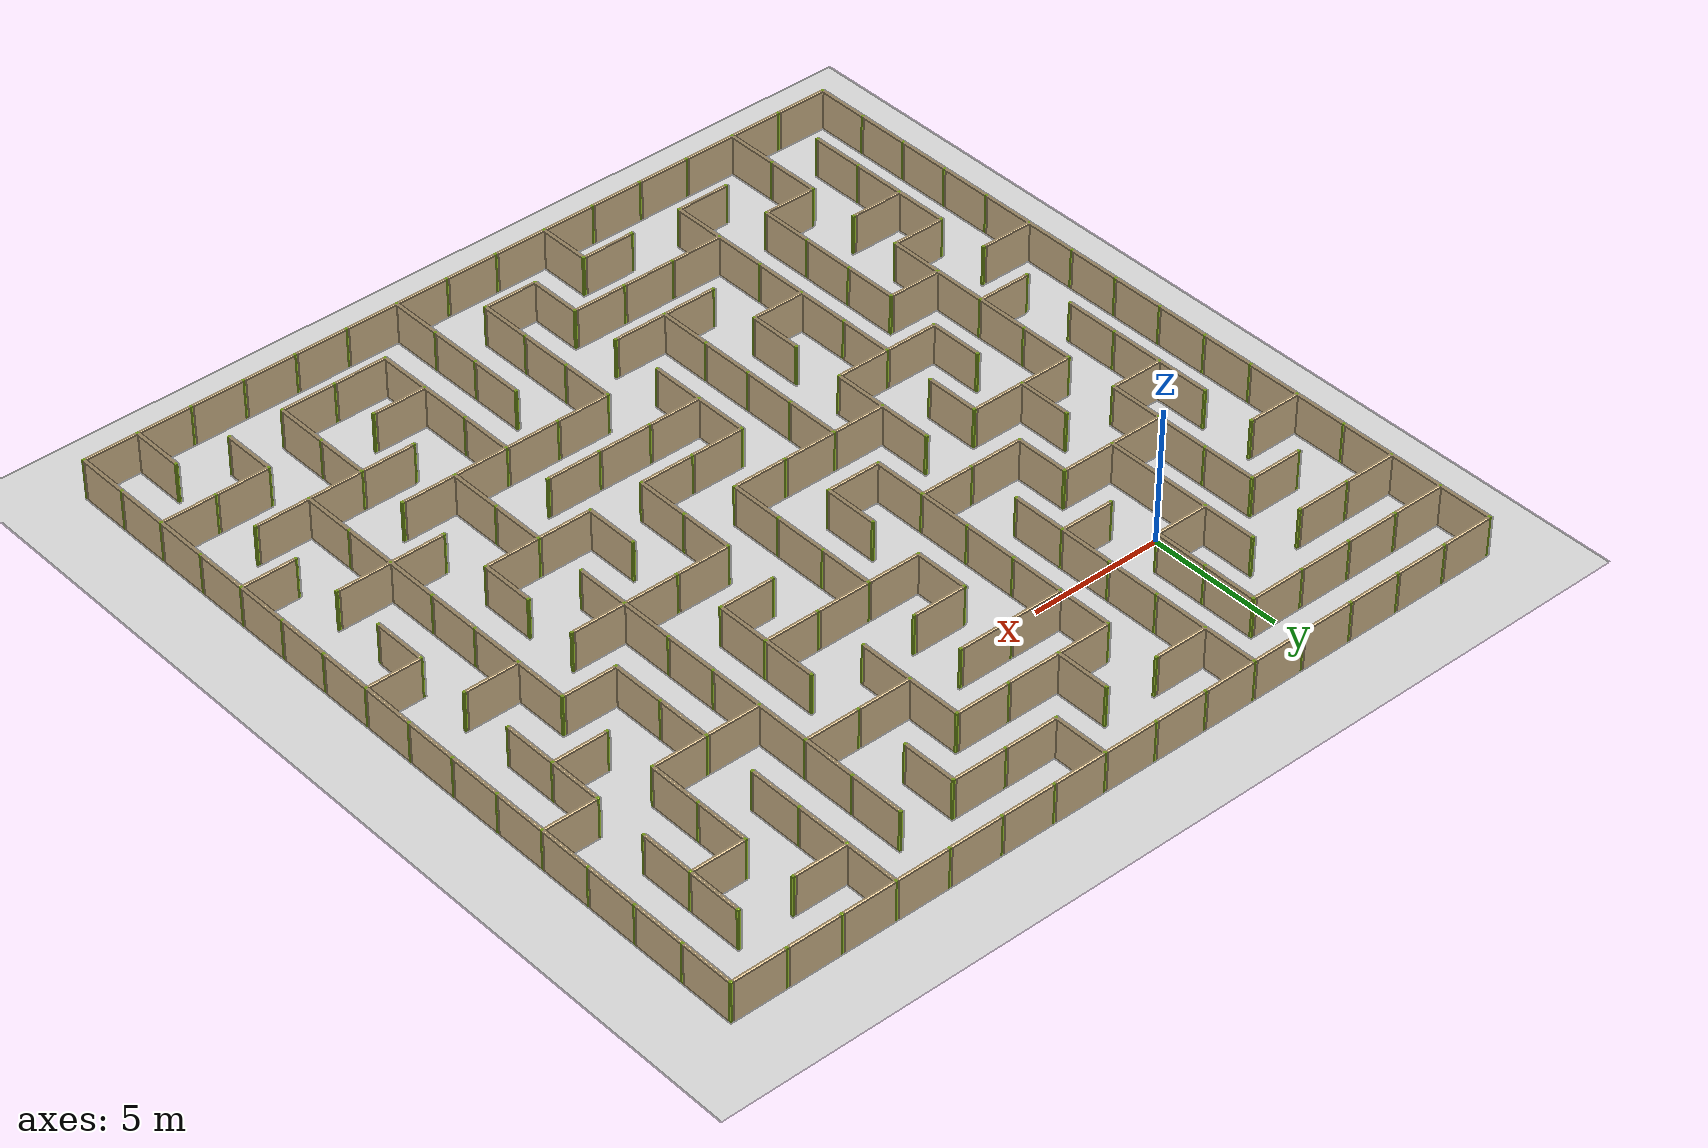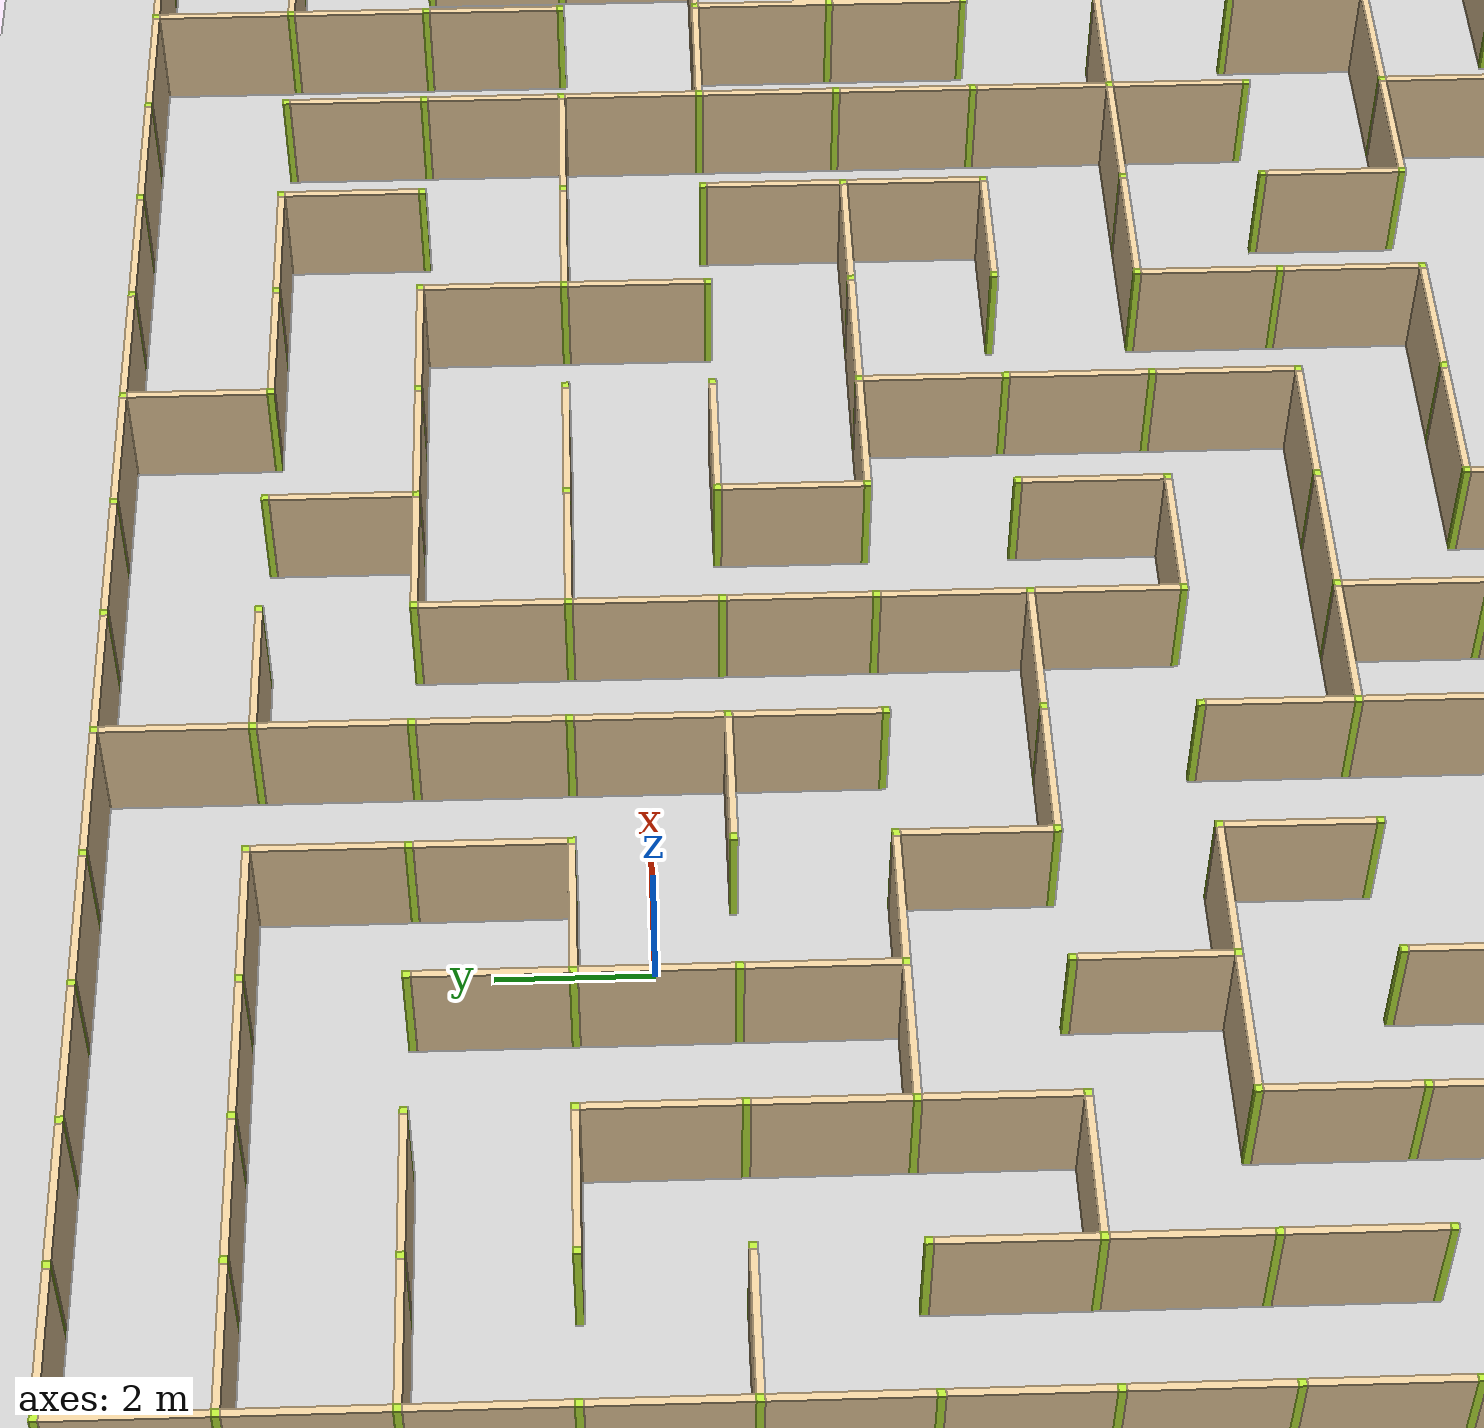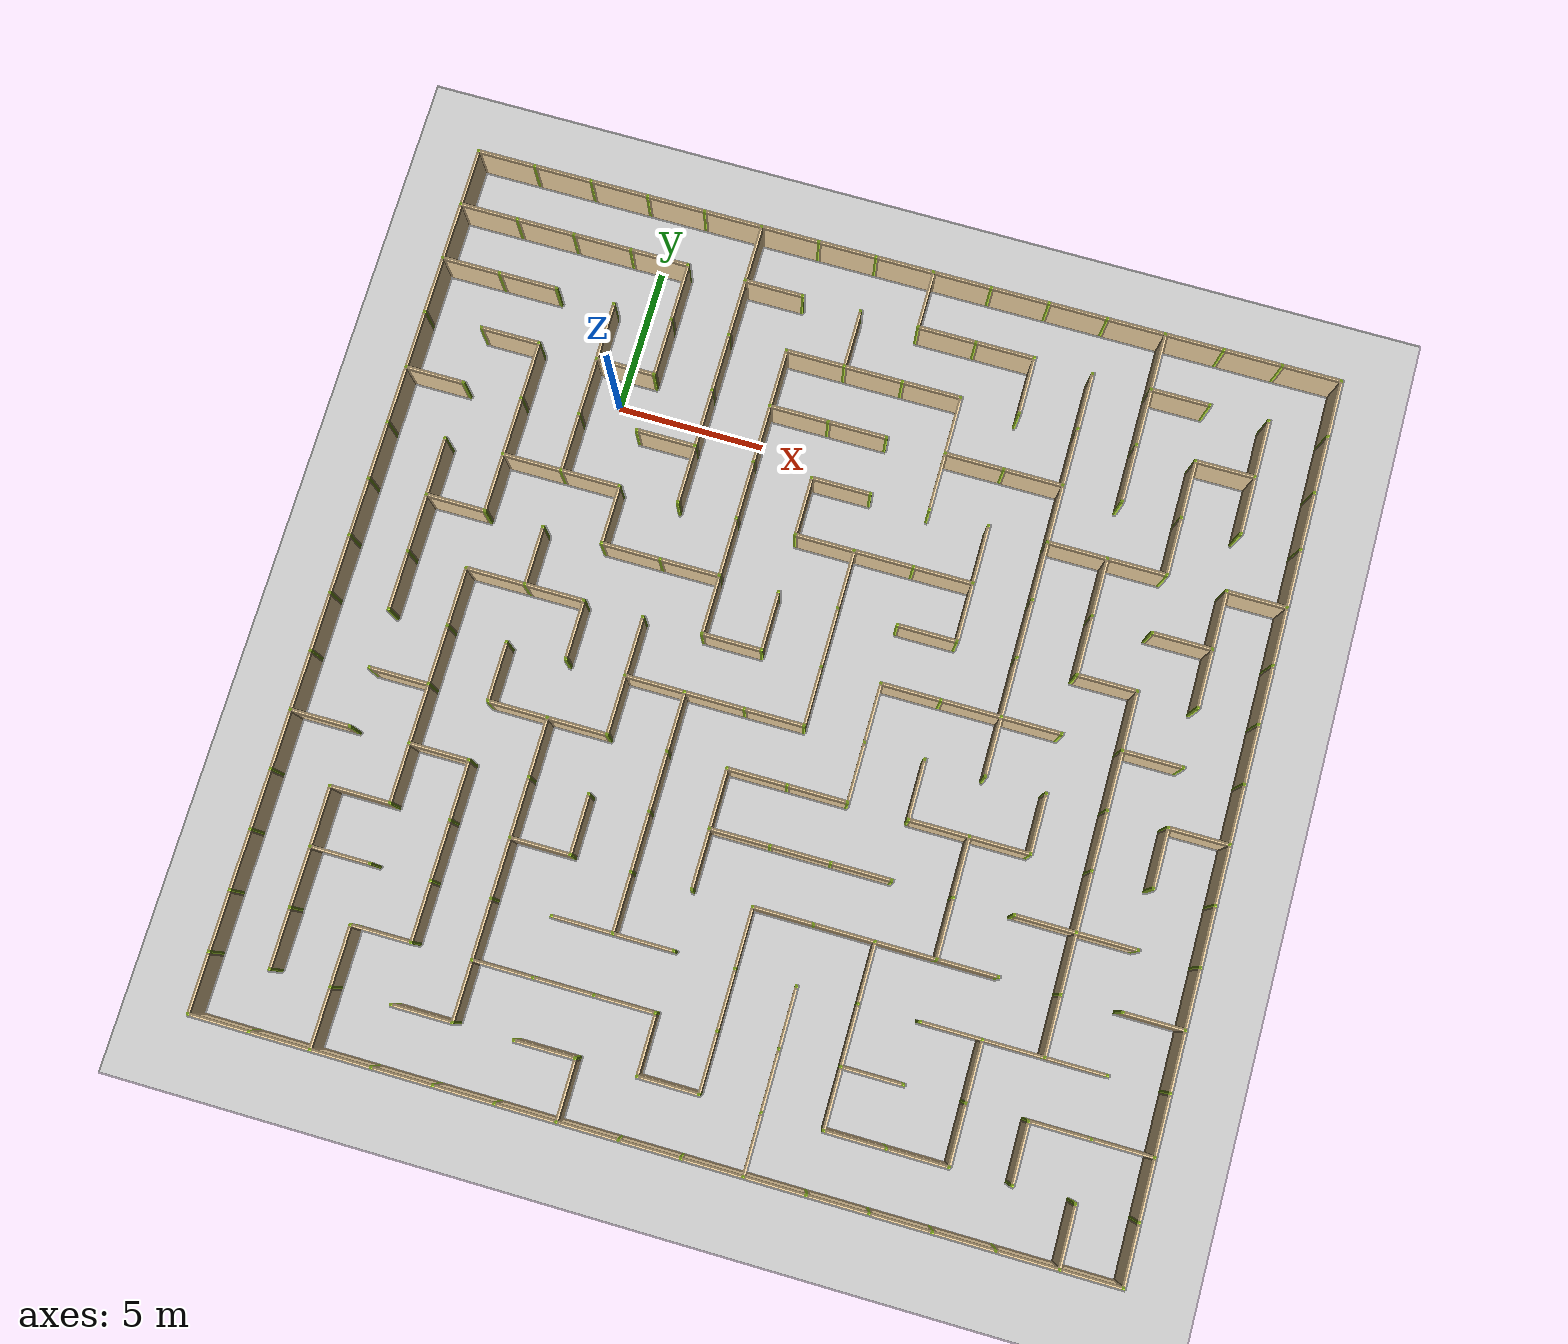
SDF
<sdf version="1.4">
  <world name="maze_world">

         <physics type="ode">
      <ode>
        <solver>
          <!-- IMPORTANT for skid steering to properly work -->
          <friction_model>cone_model</friction_model>
        </solver>
      </ode>
    </physics>
    <light name="sun" type="directional">
      <pose frame="">0 0 100 0.5 0.5 0</pose>
      <diffuse>1 1 1 1</diffuse>
      <specular>0.1 0.1 0.1 1</specular>
      <direction>0.1 0.1 -0.9</direction>
      <attenuation>
        <range>20</range>
        <constant>0.5</constant>
        <linear>0.01</linear>
        <quadratic>0.001</quadratic>
      </attenuation>
      <cast_shadows>1</cast_shadows>
    </light>
    <scene>
      <ambient>0.6 0.6 0.6 1.0</ambient>
      <sky>
        <clouds>
          <speed>12</speed>
        </clouds>
      </sky>
      <shadows>true</shadows>
      <origin_visual>false</origin_visual>
    </scene>
        <model name="ground">
      <static>true</static>
      <link name="ground_link">
        <collision name="collision1">
          <geometry>
            <plane>
              <normal>0 0 1</normal>
            </plane>
          </geometry>
        </collision>
        <visual name="visual1">
          <geometry>
            <plane>
              <normal>0 0 1</normal>
              <size>100 100</size>
            </plane>
          </geometry>
        </visual>
      </link>
    </model>
		<model name='Untitled'>
	  <pose>0 0 0 0 -0 0</pose>
        		  <link name='Wall_0_0_h'>
		    <collision name='Wall_0_Collision'>
		      <geometry>
		        <box>
		          <size>1.9 0.1 1.5</size>
		        </box>
		      </geometry>
		      <pose>0 0 0.75 0 -0 0</pose>
		    </collision>
		    <visual name='Wall_0_Visual'>
		      <pose>0 0 0.75 0 -0 0</pose>
		      <geometry>
		        <box>
		          <size>1.9 0.1 1.5</size>
		        </box>
		      </geometry>
		      <material>
		        <script>
		          <uri>file://media/materials/scripts/gazebo.material</uri>
		          <name>Gazebo/Grey</name>
		        </script>
		        <ambient>0.921569 0.807843 0.615686 1</ambient>
		      </material>
		      <meta>
		        <layer>0</layer>
		      </meta>
		    </visual>
		    <pose>-6.0 7 0 0 -0 0</pose>
                    <sensor name='my_contact' type='contact'>
          <contact>
            <collision>box_collision</collision>
			<topic>/rover_collision</topic>
          </contact>
           </sensor>
		  </link>
        		  <link name='Wall_0_0_v'>
		    <collision name='Wall_0_Collision'>
		      <geometry>
		        <box>
		          <size>1.9 0.1 1.5</size>
		        </box>
		      </geometry>
		      <pose>0 0 0.75 0 -0 0</pose>
		    </collision>
		    <visual name='Wall_0_Visual'>
		      <pose>0 0 0.75 0 -0 0</pose>
		      <geometry>
		        <box>
		          <size>1.9 0.1 1.5</size>
		        </box>
		      </geometry>
		      <material>
		        <script>
		          <uri>file://media/materials/scripts/gazebo.material</uri>
		          <name>Gazebo/Grey</name>
		        </script>
		        <ambient>0.921569 0.807843 0.615686 1</ambient>
		      </material>
		      <meta>
		        <layer>0</layer>
		      </meta>
		    </visual>
		    <pose>-7 6.0 0 0 -0 1.5708</pose>
                    <sensor name='my_contact' type='contact'>
          <contact>
            <collision>box_collision</collision>
			<topic>/rover_collision</topic>
          </contact>
           </sensor>
		  </link>
        	    <link name='Joint_-7_7'>
		    <collision name='Wall_2_Collision'>
		      <geometry>
		        <box>
		          <size>0.1 0.1 1.5</size>
		        </box>
		      </geometry>
		      <pose>0 0 0.75 0 -0 0</pose>
		    </collision>
		    <visual name='Wall_2_Visual'>
		      <pose>0 0 0.75 0 -0 0</pose>
		      <geometry>
		        <box>
		          <size>0.1 0.1 1.5</size>
		        </box>
		      </geometry>
		      <material>
		        <script>
		          <uri>file://media/materials/scripts/gazebo.material</uri>
		          <name>Gazebo/Grey</name>
		        </script>
		        <ambient>0.721569 0.907843 0.215686 1</ambient>
		      </material>
		      <meta>
		        <layer>0</layer>
		      </meta>
		    </visual>
		    <pose>-7 7 0 0 -0 0</pose>
                    <sensor name='my_contact' type='contact'>
          <contact>
            <collision>box_collision</collision>
			<topic>/rover_collision</topic>
          </contact>
           </sensor>
		  </link>
        		  <link name='Wall_1_0_h'>
		    <collision name='Wall_0_Collision'>
		      <geometry>
		        <box>
		          <size>1.9 0.1 1.5</size>
		        </box>
		      </geometry>
		      <pose>0 0 0.75 0 -0 0</pose>
		    </collision>
		    <visual name='Wall_0_Visual'>
		      <pose>0 0 0.75 0 -0 0</pose>
		      <geometry>
		        <box>
		          <size>1.9 0.1 1.5</size>
		        </box>
		      </geometry>
		      <material>
		        <script>
		          <uri>file://media/materials/scripts/gazebo.material</uri>
		          <name>Gazebo/Grey</name>
		        </script>
		        <ambient>0.921569 0.807843 0.615686 1</ambient>
		      </material>
		      <meta>
		        <layer>0</layer>
		      </meta>
		    </visual>
		    <pose>-4.0 7 0 0 -0 0</pose>
                    <sensor name='my_contact' type='contact'>
          <contact>
            <collision>box_collision</collision>
			<topic>/rover_collision</topic>
          </contact>
           </sensor>
		  </link>
        	    <link name='Joint_-5_7'>
		    <collision name='Wall_2_Collision'>
		      <geometry>
		        <box>
		          <size>0.1 0.1 1.5</size>
		        </box>
		      </geometry>
		      <pose>0 0 0.75 0 -0 0</pose>
		    </collision>
		    <visual name='Wall_2_Visual'>
		      <pose>0 0 0.75 0 -0 0</pose>
		      <geometry>
		        <box>
		          <size>0.1 0.1 1.5</size>
		        </box>
		      </geometry>
		      <material>
		        <script>
		          <uri>file://media/materials/scripts/gazebo.material</uri>
		          <name>Gazebo/Grey</name>
		        </script>
		        <ambient>0.721569 0.907843 0.215686 1</ambient>
		      </material>
		      <meta>
		        <layer>0</layer>
		      </meta>
		    </visual>
		    <pose>-5 7 0 0 -0 0</pose>
                    <sensor name='my_contact' type='contact'>
          <contact>
            <collision>box_collision</collision>
			<topic>/rover_collision</topic>
          </contact>
           </sensor>
		  </link>
        		  <link name='Wall_2_0_h'>
		    <collision name='Wall_0_Collision'>
		      <geometry>
		        <box>
		          <size>1.9 0.1 1.5</size>
		        </box>
		      </geometry>
		      <pose>0 0 0.75 0 -0 0</pose>
		    </collision>
		    <visual name='Wall_0_Visual'>
		      <pose>0 0 0.75 0 -0 0</pose>
		      <geometry>
		        <box>
		          <size>1.9 0.1 1.5</size>
		        </box>
		      </geometry>
		      <material>
		        <script>
		          <uri>file://media/materials/scripts/gazebo.material</uri>
		          <name>Gazebo/Grey</name>
		        </script>
		        <ambient>0.921569 0.807843 0.615686 1</ambient>
		      </material>
		      <meta>
		        <layer>0</layer>
		      </meta>
		    </visual>
		    <pose>-2.0 7 0 0 -0 0</pose>
                    <sensor name='my_contact' type='contact'>
          <contact>
            <collision>box_collision</collision>
			<topic>/rover_collision</topic>
          </contact>
           </sensor>
		  </link>
        	    <link name='Joint_-3_7'>
		    <collision name='Wall_2_Collision'>
		      <geometry>
		        <box>
		          <size>0.1 0.1 1.5</size>
		        </box>
		      </geometry>
		      <pose>0 0 0.75 0 -0 0</pose>
		    </collision>
		    <visual name='Wall_2_Visual'>
		      <pose>0 0 0.75 0 -0 0</pose>
		      <geometry>
		        <box>
		          <size>0.1 0.1 1.5</size>
		        </box>
		      </geometry>
		      <material>
		        <script>
		          <uri>file://media/materials/scripts/gazebo.material</uri>
		          <name>Gazebo/Grey</name>
		        </script>
		        <ambient>0.721569 0.907843 0.215686 1</ambient>
		      </material>
		      <meta>
		        <layer>0</layer>
		      </meta>
		    </visual>
		    <pose>-3 7 0 0 -0 0</pose>
                    <sensor name='my_contact' type='contact'>
          <contact>
            <collision>box_collision</collision>
			<topic>/rover_collision</topic>
          </contact>
           </sensor>
		  </link>
        		  <link name='Wall_3_0_h'>
		    <collision name='Wall_0_Collision'>
		      <geometry>
		        <box>
		          <size>1.9 0.1 1.5</size>
		        </box>
		      </geometry>
		      <pose>0 0 0.75 0 -0 0</pose>
		    </collision>
		    <visual name='Wall_0_Visual'>
		      <pose>0 0 0.75 0 -0 0</pose>
		      <geometry>
		        <box>
		          <size>1.9 0.1 1.5</size>
		        </box>
		      </geometry>
		      <material>
		        <script>
		          <uri>file://media/materials/scripts/gazebo.material</uri>
		          <name>Gazebo/Grey</name>
		        </script>
		        <ambient>0.921569 0.807843 0.615686 1</ambient>
		      </material>
		      <meta>
		        <layer>0</layer>
		      </meta>
		    </visual>
		    <pose>0.0 7 0 0 -0 0</pose>
                    <sensor name='my_contact' type='contact'>
          <contact>
            <collision>box_collision</collision>
			<topic>/rover_collision</topic>
          </contact>
           </sensor>
		  </link>
        	    <link name='Joint_-1_7'>
		    <collision name='Wall_2_Collision'>
		      <geometry>
		        <box>
		          <size>0.1 0.1 1.5</size>
		        </box>
		      </geometry>
		      <pose>0 0 0.75 0 -0 0</pose>
		    </collision>
		    <visual name='Wall_2_Visual'>
		      <pose>0 0 0.75 0 -0 0</pose>
		      <geometry>
		        <box>
		          <size>0.1 0.1 1.5</size>
		        </box>
		      </geometry>
		      <material>
		        <script>
		          <uri>file://media/materials/scripts/gazebo.material</uri>
		          <name>Gazebo/Grey</name>
		        </script>
		        <ambient>0.721569 0.907843 0.215686 1</ambient>
		      </material>
		      <meta>
		        <layer>0</layer>
		      </meta>
		    </visual>
		    <pose>-1 7 0 0 -0 0</pose>
                    <sensor name='my_contact' type='contact'>
          <contact>
            <collision>box_collision</collision>
			<topic>/rover_collision</topic>
          </contact>
           </sensor>
		  </link>
        		  <link name='Wall_4_0_h'>
		    <collision name='Wall_0_Collision'>
		      <geometry>
		        <box>
		          <size>1.9 0.1 1.5</size>
		        </box>
		      </geometry>
		      <pose>0 0 0.75 0 -0 0</pose>
		    </collision>
		    <visual name='Wall_0_Visual'>
		      <pose>0 0 0.75 0 -0 0</pose>
		      <geometry>
		        <box>
		          <size>1.9 0.1 1.5</size>
		        </box>
		      </geometry>
		      <material>
		        <script>
		          <uri>file://media/materials/scripts/gazebo.material</uri>
		          <name>Gazebo/Grey</name>
		        </script>
		        <ambient>0.921569 0.807843 0.615686 1</ambient>
		      </material>
		      <meta>
		        <layer>0</layer>
		      </meta>
		    </visual>
		    <pose>2.0 7 0 0 -0 0</pose>
                    <sensor name='my_contact' type='contact'>
          <contact>
            <collision>box_collision</collision>
			<topic>/rover_collision</topic>
          </contact>
           </sensor>
		  </link>
        	    <link name='Joint_1_7'>
		    <collision name='Wall_2_Collision'>
		      <geometry>
		        <box>
		          <size>0.1 0.1 1.5</size>
		        </box>
		      </geometry>
		      <pose>0 0 0.75 0 -0 0</pose>
		    </collision>
		    <visual name='Wall_2_Visual'>
		      <pose>0 0 0.75 0 -0 0</pose>
		      <geometry>
		        <box>
		          <size>0.1 0.1 1.5</size>
		        </box>
		      </geometry>
		      <material>
		        <script>
		          <uri>file://media/materials/scripts/gazebo.material</uri>
		          <name>Gazebo/Grey</name>
		        </script>
		        <ambient>0.721569 0.907843 0.215686 1</ambient>
		      </material>
		      <meta>
		        <layer>0</layer>
		      </meta>
		    </visual>
		    <pose>1 7 0 0 -0 0</pose>
                    <sensor name='my_contact' type='contact'>
          <contact>
            <collision>box_collision</collision>
			<topic>/rover_collision</topic>
          </contact>
           </sensor>
		  </link>
        		  <link name='Wall_5_0_h'>
		    <collision name='Wall_0_Collision'>
		      <geometry>
		        <box>
		          <size>1.9 0.1 1.5</size>
		        </box>
		      </geometry>
		      <pose>0 0 0.75 0 -0 0</pose>
		    </collision>
		    <visual name='Wall_0_Visual'>
		      <pose>0 0 0.75 0 -0 0</pose>
		      <geometry>
		        <box>
		          <size>1.9 0.1 1.5</size>
		        </box>
		      </geometry>
		      <material>
		        <script>
		          <uri>file://media/materials/scripts/gazebo.material</uri>
		          <name>Gazebo/Grey</name>
		        </script>
		        <ambient>0.921569 0.807843 0.615686 1</ambient>
		      </material>
		      <meta>
		        <layer>0</layer>
		      </meta>
		    </visual>
		    <pose>4.0 7 0 0 -0 0</pose>
                    <sensor name='my_contact' type='contact'>
          <contact>
            <collision>box_collision</collision>
			<topic>/rover_collision</topic>
          </contact>
           </sensor>
		  </link>
        		  <link name='Wall_5_0_v'>
		    <collision name='Wall_0_Collision'>
		      <geometry>
		        <box>
		          <size>1.9 0.1 1.5</size>
		        </box>
		      </geometry>
		      <pose>0 0 0.75 0 -0 0</pose>
		    </collision>
		    <visual name='Wall_0_Visual'>
		      <pose>0 0 0.75 0 -0 0</pose>
		      <geometry>
		        <box>
		          <size>1.9 0.1 1.5</size>
		        </box>
		      </geometry>
		      <material>
		        <script>
		          <uri>file://media/materials/scripts/gazebo.material</uri>
		          <name>Gazebo/Grey</name>
		        </script>
		        <ambient>0.921569 0.807843 0.615686 1</ambient>
		      </material>
		      <meta>
		        <layer>0</layer>
		      </meta>
		    </visual>
		    <pose>3 6.0 0 0 -0 1.5708</pose>
                    <sensor name='my_contact' type='contact'>
          <contact>
            <collision>box_collision</collision>
			<topic>/rover_collision</topic>
          </contact>
           </sensor>
		  </link>
        	    <link name='Joint_3_7'>
		    <collision name='Wall_2_Collision'>
		      <geometry>
		        <box>
		          <size>0.1 0.1 1.5</size>
		        </box>
		      </geometry>
		      <pose>0 0 0.75 0 -0 0</pose>
		    </collision>
		    <visual name='Wall_2_Visual'>
		      <pose>0 0 0.75 0 -0 0</pose>
		      <geometry>
		        <box>
		          <size>0.1 0.1 1.5</size>
		        </box>
		      </geometry>
		      <material>
		        <script>
		          <uri>file://media/materials/scripts/gazebo.material</uri>
		          <name>Gazebo/Grey</name>
		        </script>
		        <ambient>0.721569 0.907843 0.215686 1</ambient>
		      </material>
		      <meta>
		        <layer>0</layer>
		      </meta>
		    </visual>
		    <pose>3 7 0 0 -0 0</pose>
                    <sensor name='my_contact' type='contact'>
          <contact>
            <collision>box_collision</collision>
			<topic>/rover_collision</topic>
          </contact>
           </sensor>
		  </link>
        		  <link name='Wall_6_0_h'>
		    <collision name='Wall_0_Collision'>
		      <geometry>
		        <box>
		          <size>1.9 0.1 1.5</size>
		        </box>
		      </geometry>
		      <pose>0 0 0.75 0 -0 0</pose>
		    </collision>
		    <visual name='Wall_0_Visual'>
		      <pose>0 0 0.75 0 -0 0</pose>
		      <geometry>
		        <box>
		          <size>1.9 0.1 1.5</size>
		        </box>
		      </geometry>
		      <material>
		        <script>
		          <uri>file://media/materials/scripts/gazebo.material</uri>
		          <name>Gazebo/Grey</name>
		        </script>
		        <ambient>0.921569 0.807843 0.615686 1</ambient>
		      </material>
		      <meta>
		        <layer>0</layer>
		      </meta>
		    </visual>
		    <pose>6.0 7 0 0 -0 0</pose>
                    <sensor name='my_contact' type='contact'>
          <contact>
            <collision>box_collision</collision>
			<topic>/rover_collision</topic>
          </contact>
           </sensor>
		  </link>
        	    <link name='Joint_5_7'>
		    <collision name='Wall_2_Collision'>
		      <geometry>
		        <box>
		          <size>0.1 0.1 1.5</size>
		        </box>
		      </geometry>
		      <pose>0 0 0.75 0 -0 0</pose>
		    </collision>
		    <visual name='Wall_2_Visual'>
		      <pose>0 0 0.75 0 -0 0</pose>
		      <geometry>
		        <box>
		          <size>0.1 0.1 1.5</size>
		        </box>
		      </geometry>
		      <material>
		        <script>
		          <uri>file://media/materials/scripts/gazebo.material</uri>
		          <name>Gazebo/Grey</name>
		        </script>
		        <ambient>0.721569 0.907843 0.215686 1</ambient>
		      </material>
		      <meta>
		        <layer>0</layer>
		      </meta>
		    </visual>
		    <pose>5 7 0 0 -0 0</pose>
                    <sensor name='my_contact' type='contact'>
          <contact>
            <collision>box_collision</collision>
			<topic>/rover_collision</topic>
          </contact>
           </sensor>
		  </link>
        		  <link name='Wall_7_0_h'>
		    <collision name='Wall_0_Collision'>
		      <geometry>
		        <box>
		          <size>1.9 0.1 1.5</size>
		        </box>
		      </geometry>
		      <pose>0 0 0.75 0 -0 0</pose>
		    </collision>
		    <visual name='Wall_0_Visual'>
		      <pose>0 0 0.75 0 -0 0</pose>
		      <geometry>
		        <box>
		          <size>1.9 0.1 1.5</size>
		        </box>
		      </geometry>
		      <material>
		        <script>
		          <uri>file://media/materials/scripts/gazebo.material</uri>
		          <name>Gazebo/Grey</name>
		        </script>
		        <ambient>0.921569 0.807843 0.615686 1</ambient>
		      </material>
		      <meta>
		        <layer>0</layer>
		      </meta>
		    </visual>
		    <pose>8.0 7 0 0 -0 0</pose>
                    <sensor name='my_contact' type='contact'>
          <contact>
            <collision>box_collision</collision>
			<topic>/rover_collision</topic>
          </contact>
           </sensor>
		  </link>
        	    <link name='Joint_7_7'>
		    <collision name='Wall_2_Collision'>
		      <geometry>
		        <box>
		          <size>0.1 0.1 1.5</size>
		        </box>
		      </geometry>
		      <pose>0 0 0.75 0 -0 0</pose>
		    </collision>
		    <visual name='Wall_2_Visual'>
		      <pose>0 0 0.75 0 -0 0</pose>
		      <geometry>
		        <box>
		          <size>0.1 0.1 1.5</size>
		        </box>
		      </geometry>
		      <material>
		        <script>
		          <uri>file://media/materials/scripts/gazebo.material</uri>
		          <name>Gazebo/Grey</name>
		        </script>
		        <ambient>0.721569 0.907843 0.215686 1</ambient>
		      </material>
		      <meta>
		        <layer>0</layer>
		      </meta>
		    </visual>
		    <pose>7 7 0 0 -0 0</pose>
                    <sensor name='my_contact' type='contact'>
          <contact>
            <collision>box_collision</collision>
			<topic>/rover_collision</topic>
          </contact>
           </sensor>
		  </link>
        		  <link name='Wall_8_0_h'>
		    <collision name='Wall_0_Collision'>
		      <geometry>
		        <box>
		          <size>1.9 0.1 1.5</size>
		        </box>
		      </geometry>
		      <pose>0 0 0.75 0 -0 0</pose>
		    </collision>
		    <visual name='Wall_0_Visual'>
		      <pose>0 0 0.75 0 -0 0</pose>
		      <geometry>
		        <box>
		          <size>1.9 0.1 1.5</size>
		        </box>
		      </geometry>
		      <material>
		        <script>
		          <uri>file://media/materials/scripts/gazebo.material</uri>
		          <name>Gazebo/Grey</name>
		        </script>
		        <ambient>0.921569 0.807843 0.615686 1</ambient>
		      </material>
		      <meta>
		        <layer>0</layer>
		      </meta>
		    </visual>
		    <pose>10.0 7 0 0 -0 0</pose>
                    <sensor name='my_contact' type='contact'>
          <contact>
            <collision>box_collision</collision>
			<topic>/rover_collision</topic>
          </contact>
           </sensor>
		  </link>
        		  <link name='Wall_8_0_v'>
		    <collision name='Wall_0_Collision'>
		      <geometry>
		        <box>
		          <size>1.9 0.1 1.5</size>
		        </box>
		      </geometry>
		      <pose>0 0 0.75 0 -0 0</pose>
		    </collision>
		    <visual name='Wall_0_Visual'>
		      <pose>0 0 0.75 0 -0 0</pose>
		      <geometry>
		        <box>
		          <size>1.9 0.1 1.5</size>
		        </box>
		      </geometry>
		      <material>
		        <script>
		          <uri>file://media/materials/scripts/gazebo.material</uri>
		          <name>Gazebo/Grey</name>
		        </script>
		        <ambient>0.921569 0.807843 0.615686 1</ambient>
		      </material>
		      <meta>
		        <layer>0</layer>
		      </meta>
		    </visual>
		    <pose>9 6.0 0 0 -0 1.5708</pose>
                    <sensor name='my_contact' type='contact'>
          <contact>
            <collision>box_collision</collision>
			<topic>/rover_collision</topic>
          </contact>
           </sensor>
		  </link>
        	    <link name='Joint_9_7'>
		    <collision name='Wall_2_Collision'>
		      <geometry>
		        <box>
		          <size>0.1 0.1 1.5</size>
		        </box>
		      </geometry>
		      <pose>0 0 0.75 0 -0 0</pose>
		    </collision>
		    <visual name='Wall_2_Visual'>
		      <pose>0 0 0.75 0 -0 0</pose>
		      <geometry>
		        <box>
		          <size>0.1 0.1 1.5</size>
		        </box>
		      </geometry>
		      <material>
		        <script>
		          <uri>file://media/materials/scripts/gazebo.material</uri>
		          <name>Gazebo/Grey</name>
		        </script>
		        <ambient>0.721569 0.907843 0.215686 1</ambient>
		      </material>
		      <meta>
		        <layer>0</layer>
		      </meta>
		    </visual>
		    <pose>9 7 0 0 -0 0</pose>
                    <sensor name='my_contact' type='contact'>
          <contact>
            <collision>box_collision</collision>
			<topic>/rover_collision</topic>
          </contact>
           </sensor>
		  </link>
        		  <link name='Wall_9_0_h'>
		    <collision name='Wall_0_Collision'>
		      <geometry>
		        <box>
		          <size>1.9 0.1 1.5</size>
		        </box>
		      </geometry>
		      <pose>0 0 0.75 0 -0 0</pose>
		    </collision>
		    <visual name='Wall_0_Visual'>
		      <pose>0 0 0.75 0 -0 0</pose>
		      <geometry>
		        <box>
		          <size>1.9 0.1 1.5</size>
		        </box>
		      </geometry>
		      <material>
		        <script>
		          <uri>file://media/materials/scripts/gazebo.material</uri>
		          <name>Gazebo/Grey</name>
		        </script>
		        <ambient>0.921569 0.807843 0.615686 1</ambient>
		      </material>
		      <meta>
		        <layer>0</layer>
		      </meta>
		    </visual>
		    <pose>12.0 7 0 0 -0 0</pose>
                    <sensor name='my_contact' type='contact'>
          <contact>
            <collision>box_collision</collision>
			<topic>/rover_collision</topic>
          </contact>
           </sensor>
		  </link>
        	    <link name='Joint_11_7'>
		    <collision name='Wall_2_Collision'>
		      <geometry>
		        <box>
		          <size>0.1 0.1 1.5</size>
		        </box>
		      </geometry>
		      <pose>0 0 0.75 0 -0 0</pose>
		    </collision>
		    <visual name='Wall_2_Visual'>
		      <pose>0 0 0.75 0 -0 0</pose>
		      <geometry>
		        <box>
		          <size>0.1 0.1 1.5</size>
		        </box>
		      </geometry>
		      <material>
		        <script>
		          <uri>file://media/materials/scripts/gazebo.material</uri>
		          <name>Gazebo/Grey</name>
		        </script>
		        <ambient>0.721569 0.907843 0.215686 1</ambient>
		      </material>
		      <meta>
		        <layer>0</layer>
		      </meta>
		    </visual>
		    <pose>11 7 0 0 -0 0</pose>
                    <sensor name='my_contact' type='contact'>
          <contact>
            <collision>box_collision</collision>
			<topic>/rover_collision</topic>
          </contact>
           </sensor>
		  </link>
        		  <link name='Wall_10_0_h'>
		    <collision name='Wall_0_Collision'>
		      <geometry>
		        <box>
		          <size>1.9 0.1 1.5</size>
		        </box>
		      </geometry>
		      <pose>0 0 0.75 0 -0 0</pose>
		    </collision>
		    <visual name='Wall_0_Visual'>
		      <pose>0 0 0.75 0 -0 0</pose>
		      <geometry>
		        <box>
		          <size>1.9 0.1 1.5</size>
		        </box>
		      </geometry>
		      <material>
		        <script>
		          <uri>file://media/materials/scripts/gazebo.material</uri>
		          <name>Gazebo/Grey</name>
		        </script>
		        <ambient>0.921569 0.807843 0.615686 1</ambient>
		      </material>
		      <meta>
		        <layer>0</layer>
		      </meta>
		    </visual>
		    <pose>14.0 7 0 0 -0 0</pose>
                    <sensor name='my_contact' type='contact'>
          <contact>
            <collision>box_collision</collision>
			<topic>/rover_collision</topic>
          </contact>
           </sensor>
		  </link>
        	    <link name='Joint_13_7'>
		    <collision name='Wall_2_Collision'>
		      <geometry>
		        <box>
		          <size>0.1 0.1 1.5</size>
		        </box>
		      </geometry>
		      <pose>0 0 0.75 0 -0 0</pose>
		    </collision>
		    <visual name='Wall_2_Visual'>
		      <pose>0 0 0.75 0 -0 0</pose>
		      <geometry>
		        <box>
		          <size>0.1 0.1 1.5</size>
		        </box>
		      </geometry>
		      <material>
		        <script>
		          <uri>file://media/materials/scripts/gazebo.material</uri>
		          <name>Gazebo/Grey</name>
		        </script>
		        <ambient>0.721569 0.907843 0.215686 1</ambient>
		      </material>
		      <meta>
		        <layer>0</layer>
		      </meta>
		    </visual>
		    <pose>13 7 0 0 -0 0</pose>
                    <sensor name='my_contact' type='contact'>
          <contact>
            <collision>box_collision</collision>
			<topic>/rover_collision</topic>
          </contact>
           </sensor>
		  </link>
        		  <link name='Wall_11_0_h'>
		    <collision name='Wall_0_Collision'>
		      <geometry>
		        <box>
		          <size>1.9 0.1 1.5</size>
		        </box>
		      </geometry>
		      <pose>0 0 0.75 0 -0 0</pose>
		    </collision>
		    <visual name='Wall_0_Visual'>
		      <pose>0 0 0.75 0 -0 0</pose>
		      <geometry>
		        <box>
		          <size>1.9 0.1 1.5</size>
		        </box>
		      </geometry>
		      <material>
		        <script>
		          <uri>file://media/materials/scripts/gazebo.material</uri>
		          <name>Gazebo/Grey</name>
		        </script>
		        <ambient>0.921569 0.807843 0.615686 1</ambient>
		      </material>
		      <meta>
		        <layer>0</layer>
		      </meta>
		    </visual>
		    <pose>16.0 7 0 0 -0 0</pose>
                    <sensor name='my_contact' type='contact'>
          <contact>
            <collision>box_collision</collision>
			<topic>/rover_collision</topic>
          </contact>
           </sensor>
		  </link>
        	    <link name='Joint_15_7'>
		    <collision name='Wall_2_Collision'>
		      <geometry>
		        <box>
		          <size>0.1 0.1 1.5</size>
		        </box>
		      </geometry>
		      <pose>0 0 0.75 0 -0 0</pose>
		    </collision>
		    <visual name='Wall_2_Visual'>
		      <pose>0 0 0.75 0 -0 0</pose>
		      <geometry>
		        <box>
		          <size>0.1 0.1 1.5</size>
		        </box>
		      </geometry>
		      <material>
		        <script>
		          <uri>file://media/materials/scripts/gazebo.material</uri>
		          <name>Gazebo/Grey</name>
		        </script>
		        <ambient>0.721569 0.907843 0.215686 1</ambient>
		      </material>
		      <meta>
		        <layer>0</layer>
		      </meta>
		    </visual>
		    <pose>15 7 0 0 -0 0</pose>
                    <sensor name='my_contact' type='contact'>
          <contact>
            <collision>box_collision</collision>
			<topic>/rover_collision</topic>
          </contact>
           </sensor>
		  </link>
        		  <link name='Wall_12_0_h'>
		    <collision name='Wall_0_Collision'>
		      <geometry>
		        <box>
		          <size>1.9 0.1 1.5</size>
		        </box>
		      </geometry>
		      <pose>0 0 0.75 0 -0 0</pose>
		    </collision>
		    <visual name='Wall_0_Visual'>
		      <pose>0 0 0.75 0 -0 0</pose>
		      <geometry>
		        <box>
		          <size>1.9 0.1 1.5</size>
		        </box>
		      </geometry>
		      <material>
		        <script>
		          <uri>file://media/materials/scripts/gazebo.material</uri>
		          <name>Gazebo/Grey</name>
		        </script>
		        <ambient>0.921569 0.807843 0.615686 1</ambient>
		      </material>
		      <meta>
		        <layer>0</layer>
		      </meta>
		    </visual>
		    <pose>18.0 7 0 0 -0 0</pose>
                    <sensor name='my_contact' type='contact'>
          <contact>
            <collision>box_collision</collision>
			<topic>/rover_collision</topic>
          </contact>
           </sensor>
		  </link>
        		  <link name='Wall_12_0_v'>
		    <collision name='Wall_0_Collision'>
		      <geometry>
		        <box>
		          <size>1.9 0.1 1.5</size>
		        </box>
		      </geometry>
		      <pose>0 0 0.75 0 -0 0</pose>
		    </collision>
		    <visual name='Wall_0_Visual'>
		      <pose>0 0 0.75 0 -0 0</pose>
		      <geometry>
		        <box>
		          <size>1.9 0.1 1.5</size>
		        </box>
		      </geometry>
		      <material>
		        <script>
		          <uri>file://media/materials/scripts/gazebo.material</uri>
		          <name>Gazebo/Grey</name>
		        </script>
		        <ambient>0.921569 0.807843 0.615686 1</ambient>
		      </material>
		      <meta>
		        <layer>0</layer>
		      </meta>
		    </visual>
		    <pose>17 6.0 0 0 -0 1.5708</pose>
                    <sensor name='my_contact' type='contact'>
          <contact>
            <collision>box_collision</collision>
			<topic>/rover_collision</topic>
          </contact>
           </sensor>
		  </link>
        	    <link name='Joint_17_7'>
		    <collision name='Wall_2_Collision'>
		      <geometry>
		        <box>
		          <size>0.1 0.1 1.5</size>
		        </box>
		      </geometry>
		      <pose>0 0 0.75 0 -0 0</pose>
		    </collision>
		    <visual name='Wall_2_Visual'>
		      <pose>0 0 0.75 0 -0 0</pose>
		      <geometry>
		        <box>
		          <size>0.1 0.1 1.5</size>
		        </box>
		      </geometry>
		      <material>
		        <script>
		          <uri>file://media/materials/scripts/gazebo.material</uri>
		          <name>Gazebo/Grey</name>
		        </script>
		        <ambient>0.721569 0.907843 0.215686 1</ambient>
		      </material>
		      <meta>
		        <layer>0</layer>
		      </meta>
		    </visual>
		    <pose>17 7 0 0 -0 0</pose>
                    <sensor name='my_contact' type='contact'>
          <contact>
            <collision>box_collision</collision>
			<topic>/rover_collision</topic>
          </contact>
           </sensor>
		  </link>
        		  <link name='Wall_13_0_h'>
		    <collision name='Wall_0_Collision'>
		      <geometry>
		        <box>
		          <size>1.9 0.1 1.5</size>
		        </box>
		      </geometry>
		      <pose>0 0 0.75 0 -0 0</pose>
		    </collision>
		    <visual name='Wall_0_Visual'>
		      <pose>0 0 0.75 0 -0 0</pose>
		      <geometry>
		        <box>
		          <size>1.9 0.1 1.5</size>
		        </box>
		      </geometry>
		      <material>
		        <script>
		          <uri>file://media/materials/scripts/gazebo.material</uri>
		          <name>Gazebo/Grey</name>
		        </script>
		        <ambient>0.921569 0.807843 0.615686 1</ambient>
		      </material>
		      <meta>
		        <layer>0</layer>
		      </meta>
		    </visual>
		    <pose>20.0 7 0 0 -0 0</pose>
                    <sensor name='my_contact' type='contact'>
          <contact>
            <collision>box_collision</collision>
			<topic>/rover_collision</topic>
          </contact>
           </sensor>
		  </link>
        	    <link name='Joint_19_7'>
		    <collision name='Wall_2_Collision'>
		      <geometry>
		        <box>
		          <size>0.1 0.1 1.5</size>
		        </box>
		      </geometry>
		      <pose>0 0 0.75 0 -0 0</pose>
		    </collision>
		    <visual name='Wall_2_Visual'>
		      <pose>0 0 0.75 0 -0 0</pose>
		      <geometry>
		        <box>
		          <size>0.1 0.1 1.5</size>
		        </box>
		      </geometry>
		      <material>
		        <script>
		          <uri>file://media/materials/scripts/gazebo.material</uri>
		          <name>Gazebo/Grey</name>
		        </script>
		        <ambient>0.721569 0.907843 0.215686 1</ambient>
		      </material>
		      <meta>
		        <layer>0</layer>
		      </meta>
		    </visual>
		    <pose>19 7 0 0 -0 0</pose>
                    <sensor name='my_contact' type='contact'>
          <contact>
            <collision>box_collision</collision>
			<topic>/rover_collision</topic>
          </contact>
           </sensor>
		  </link>
        		  <link name='Wall_14_0_h'>
		    <collision name='Wall_0_Collision'>
		      <geometry>
		        <box>
		          <size>1.9 0.1 1.5</size>
		        </box>
		      </geometry>
		      <pose>0 0 0.75 0 -0 0</pose>
		    </collision>
		    <visual name='Wall_0_Visual'>
		      <pose>0 0 0.75 0 -0 0</pose>
		      <geometry>
		        <box>
		          <size>1.9 0.1 1.5</size>
		        </box>
		      </geometry>
		      <material>
		        <script>
		          <uri>file://media/materials/scripts/gazebo.material</uri>
		          <name>Gazebo/Grey</name>
		        </script>
		        <ambient>0.921569 0.807843 0.615686 1</ambient>
		      </material>
		      <meta>
		        <layer>0</layer>
		      </meta>
		    </visual>
		    <pose>22.0 7 0 0 -0 0</pose>
                    <sensor name='my_contact' type='contact'>
          <contact>
            <collision>box_collision</collision>
			<topic>/rover_collision</topic>
          </contact>
           </sensor>
		  </link>
        	    <link name='Joint_21_7'>
		    <collision name='Wall_2_Collision'>
		      <geometry>
		        <box>
		          <size>0.1 0.1 1.5</size>
		        </box>
		      </geometry>
		      <pose>0 0 0.75 0 -0 0</pose>
		    </collision>
		    <visual name='Wall_2_Visual'>
		      <pose>0 0 0.75 0 -0 0</pose>
		      <geometry>
		        <box>
		          <size>0.1 0.1 1.5</size>
		        </box>
		      </geometry>
		      <material>
		        <script>
		          <uri>file://media/materials/scripts/gazebo.material</uri>
		          <name>Gazebo/Grey</name>
		        </script>
		        <ambient>0.721569 0.907843 0.215686 1</ambient>
		      </material>
		      <meta>
		        <layer>0</layer>
		      </meta>
		    </visual>
		    <pose>21 7 0 0 -0 0</pose>
                    <sensor name='my_contact' type='contact'>
          <contact>
            <collision>box_collision</collision>
			<topic>/rover_collision</topic>
          </contact>
           </sensor>
		  </link>
        		  <link name='Wall_15_0_v'>
		    <collision name='Wall_0_Collision'>
		      <geometry>
		        <box>
		          <size>1.9 0.1 1.5</size>
		        </box>
		      </geometry>
		      <pose>0 0 0.75 0 -0 0</pose>
		    </collision>
		    <visual name='Wall_0_Visual'>
		      <pose>0 0 0.75 0 -0 0</pose>
		      <geometry>
		        <box>
		          <size>1.9 0.1 1.5</size>
		        </box>
		      </geometry>
		      <material>
		        <script>
		          <uri>file://media/materials/scripts/gazebo.material</uri>
		          <name>Gazebo/Grey</name>
		        </script>
		        <ambient>0.921569 0.807843 0.615686 1</ambient>
		      </material>
		      <meta>
		        <layer>0</layer>
		      </meta>
		    </visual>
		    <pose>23 6.0 0 0 -0 1.5708</pose>
                    <sensor name='my_contact' type='contact'>
          <contact>
            <collision>box_collision</collision>
			<topic>/rover_collision</topic>
          </contact>
           </sensor>
		  </link>
        	    <link name='Joint_23_7'>
		    <collision name='Wall_2_Collision'>
		      <geometry>
		        <box>
		          <size>0.1 0.1 1.5</size>
		        </box>
		      </geometry>
		      <pose>0 0 0.75 0 -0 0</pose>
		    </collision>
		    <visual name='Wall_2_Visual'>
		      <pose>0 0 0.75 0 -0 0</pose>
		      <geometry>
		        <box>
		          <size>0.1 0.1 1.5</size>
		        </box>
		      </geometry>
		      <material>
		        <script>
		          <uri>file://media/materials/scripts/gazebo.material</uri>
		          <name>Gazebo/Grey</name>
		        </script>
		        <ambient>0.721569 0.907843 0.215686 1</ambient>
		      </material>
		      <meta>
		        <layer>0</layer>
		      </meta>
		    </visual>
		    <pose>23 7 0 0 -0 0</pose>
                    <sensor name='my_contact' type='contact'>
          <contact>
            <collision>box_collision</collision>
			<topic>/rover_collision</topic>
          </contact>
           </sensor>
		  </link>
        		  <link name='Wall_0_1_h'>
		    <collision name='Wall_0_Collision'>
		      <geometry>
		        <box>
		          <size>1.9 0.1 1.5</size>
		        </box>
		      </geometry>
		      <pose>0 0 0.75 0 -0 0</pose>
		    </collision>
		    <visual name='Wall_0_Visual'>
		      <pose>0 0 0.75 0 -0 0</pose>
		      <geometry>
		        <box>
		          <size>1.9 0.1 1.5</size>
		        </box>
		      </geometry>
		      <material>
		        <script>
		          <uri>file://media/materials/scripts/gazebo.material</uri>
		          <name>Gazebo/Grey</name>
		        </script>
		        <ambient>0.921569 0.807843 0.615686 1</ambient>
		      </material>
		      <meta>
		        <layer>0</layer>
		      </meta>
		    </visual>
		    <pose>-6.0 5 0 0 -0 0</pose>
                    <sensor name='my_contact' type='contact'>
          <contact>
            <collision>box_collision</collision>
			<topic>/rover_collision</topic>
          </contact>
           </sensor>
		  </link>
        		  <link name='Wall_0_1_v'>
		    <collision name='Wall_0_Collision'>
		      <geometry>
		        <box>
		          <size>1.9 0.1 1.5</size>
		        </box>
		      </geometry>
		      <pose>0 0 0.75 0 -0 0</pose>
		    </collision>
		    <visual name='Wall_0_Visual'>
		      <pose>0 0 0.75 0 -0 0</pose>
		      <geometry>
		        <box>
		          <size>1.9 0.1 1.5</size>
		        </box>
		      </geometry>
		      <material>
		        <script>
		          <uri>file://media/materials/scripts/gazebo.material</uri>
		          <name>Gazebo/Grey</name>
		        </script>
		        <ambient>0.921569 0.807843 0.615686 1</ambient>
		      </material>
		      <meta>
		        <layer>0</layer>
		      </meta>
		    </visual>
		    <pose>-7 4.0 0 0 -0 1.5708</pose>
                    <sensor name='my_contact' type='contact'>
          <contact>
            <collision>box_collision</collision>
			<topic>/rover_collision</topic>
          </contact>
           </sensor>
		  </link>
        	    <link name='Joint_-7_5'>
		    <collision name='Wall_2_Collision'>
		      <geometry>
		        <box>
		          <size>0.1 0.1 1.5</size>
		        </box>
		      </geometry>
		      <pose>0 0 0.75 0 -0 0</pose>
		    </collision>
		    <visual name='Wall_2_Visual'>
		      <pose>0 0 0.75 0 -0 0</pose>
		      <geometry>
		        <box>
		          <size>0.1 0.1 1.5</size>
		        </box>
		      </geometry>
		      <material>
		        <script>
		          <uri>file://media/materials/scripts/gazebo.material</uri>
		          <name>Gazebo/Grey</name>
		        </script>
		        <ambient>0.721569 0.907843 0.215686 1</ambient>
		      </material>
		      <meta>
		        <layer>0</layer>
		      </meta>
		    </visual>
		    <pose>-7 5 0 0 -0 0</pose>
                    <sensor name='my_contact' type='contact'>
          <contact>
            <collision>box_collision</collision>
			<topic>/rover_collision</topic>
          </contact>
           </sensor>
		  </link>
        		  <link name='Wall_1_1_h'>
		    <collision name='Wall_0_Collision'>
		      <geometry>
		        <box>
		          <size>1.9 0.1 1.5</size>
		        </box>
		      </geometry>
		      <pose>0 0 0.75 0 -0 0</pose>
		    </collision>
		    <visual name='Wall_0_Visual'>
		      <pose>0 0 0.75 0 -0 0</pose>
		      <geometry>
		        <box>
		          <size>1.9 0.1 1.5</size>
		        </box>
		      </geometry>
		      <material>
		        <script>
		          <uri>file://media/materials/scripts/gazebo.material</uri>
		          <name>Gazebo/Grey</name>
		        </script>
		        <ambient>0.921569 0.807843 0.615686 1</ambient>
		      </material>
		      <meta>
		        <layer>0</layer>
		      </meta>
		    </visual>
		    <pose>-4.0 5 0 0 -0 0</pose>
                    <sensor name='my_contact' type='contact'>
          <contact>
            <collision>box_collision</collision>
			<topic>/rover_collision</topic>
          </contact>
           </sensor>
		  </link>
        	    <link name='Joint_-5_5'>
		    <collision name='Wall_2_Collision'>
		      <geometry>
		        <box>
		          <size>0.1 0.1 1.5</size>
		        </box>
		      </geometry>
		      <pose>0 0 0.75 0 -0 0</pose>
		    </collision>
		    <visual name='Wall_2_Visual'>
		      <pose>0 0 0.75 0 -0 0</pose>
		      <geometry>
		        <box>
		          <size>0.1 0.1 1.5</size>
		        </box>
		      </geometry>
		      <material>
		        <script>
		          <uri>file://media/materials/scripts/gazebo.material</uri>
		          <name>Gazebo/Grey</name>
		        </script>
		        <ambient>0.721569 0.907843 0.215686 1</ambient>
		      </material>
		      <meta>
		        <layer>0</layer>
		      </meta>
		    </visual>
		    <pose>-5 5 0 0 -0 0</pose>
                    <sensor name='my_contact' type='contact'>
          <contact>
            <collision>box_collision</collision>
			<topic>/rover_collision</topic>
          </contact>
           </sensor>
		  </link>
        		  <link name='Wall_2_1_h'>
		    <collision name='Wall_0_Collision'>
		      <geometry>
		        <box>
		          <size>1.9 0.1 1.5</size>
		        </box>
		      </geometry>
		      <pose>0 0 0.75 0 -0 0</pose>
		    </collision>
		    <visual name='Wall_0_Visual'>
		      <pose>0 0 0.75 0 -0 0</pose>
		      <geometry>
		        <box>
		          <size>1.9 0.1 1.5</size>
		        </box>
		      </geometry>
		      <material>
		        <script>
		          <uri>file://media/materials/scripts/gazebo.material</uri>
		          <name>Gazebo/Grey</name>
		        </script>
		        <ambient>0.921569 0.807843 0.615686 1</ambient>
		      </material>
		      <meta>
		        <layer>0</layer>
		      </meta>
		    </visual>
		    <pose>-2.0 5 0 0 -0 0</pose>
                    <sensor name='my_contact' type='contact'>
          <contact>
            <collision>box_collision</collision>
			<topic>/rover_collision</topic>
          </contact>
           </sensor>
		  </link>
        	    <link name='Joint_-3_5'>
		    <collision name='Wall_2_Collision'>
		      <geometry>
		        <box>
		          <size>0.1 0.1 1.5</size>
		        </box>
		      </geometry>
		      <pose>0 0 0.75 0 -0 0</pose>
		    </collision>
		    <visual name='Wall_2_Visual'>
		      <pose>0 0 0.75 0 -0 0</pose>
		      <geometry>
		        <box>
		          <size>0.1 0.1 1.5</size>
		        </box>
		      </geometry>
		      <material>
		        <script>
		          <uri>file://media/materials/scripts/gazebo.material</uri>
		          <name>Gazebo/Grey</name>
		        </script>
		        <ambient>0.721569 0.907843 0.215686 1</ambient>
		      </material>
		      <meta>
		        <layer>0</layer>
		      </meta>
		    </visual>
		    <pose>-3 5 0 0 -0 0</pose>
                    <sensor name='my_contact' type='contact'>
          <contact>
            <collision>box_collision</collision>
			<topic>/rover_collision</topic>
          </contact>
           </sensor>
		  </link>
        		  <link name='Wall_3_1_h'>
		    <collision name='Wall_0_Collision'>
		      <geometry>
		        <box>
		          <size>1.9 0.1 1.5</size>
		        </box>
		      </geometry>
		      <pose>0 0 0.75 0 -0 0</pose>
		    </collision>
		    <visual name='Wall_0_Visual'>
		      <pose>0 0 0.75 0 -0 0</pose>
		      <geometry>
		        <box>
		          <size>1.9 0.1 1.5</size>
		        </box>
		      </geometry>
		      <material>
		        <script>
		          <uri>file://media/materials/scripts/gazebo.material</uri>
		          <name>Gazebo/Grey</name>
		        </script>
		        <ambient>0.921569 0.807843 0.615686 1</ambient>
		      </material>
		      <meta>
		        <layer>0</layer>
		      </meta>
		    </visual>
		    <pose>0.0 5 0 0 -0 0</pose>
                    <sensor name='my_contact' type='contact'>
          <contact>
            <collision>box_collision</collision>
			<topic>/rover_collision</topic>
          </contact>
           </sensor>
		  </link>
        	    <link name='Joint_-1_5'>
		    <collision name='Wall_2_Collision'>
		      <geometry>
		        <box>
		          <size>0.1 0.1 1.5</size>
		        </box>
		      </geometry>
		      <pose>0 0 0.75 0 -0 0</pose>
		    </collision>
		    <visual name='Wall_2_Visual'>
		      <pose>0 0 0.75 0 -0 0</pose>
		      <geometry>
		        <box>
		          <size>0.1 0.1 1.5</size>
		        </box>
		      </geometry>
		      <material>
		        <script>
		          <uri>file://media/materials/scripts/gazebo.material</uri>
		          <name>Gazebo/Grey</name>
		        </script>
		        <ambient>0.721569 0.907843 0.215686 1</ambient>
		      </material>
		      <meta>
		        <layer>0</layer>
		      </meta>
		    </visual>
		    <pose>-1 5 0 0 -0 0</pose>
                    <sensor name='my_contact' type='contact'>
          <contact>
            <collision>box_collision</collision>
			<topic>/rover_collision</topic>
          </contact>
           </sensor>
		  </link>
        		  <link name='Wall_4_1_v'>
		    <collision name='Wall_0_Collision'>
		      <geometry>
		        <box>
		          <size>1.9 0.1 1.5</size>
		        </box>
		      </geometry>
		      <pose>0 0 0.75 0 -0 0</pose>
		    </collision>
		    <visual name='Wall_0_Visual'>
		      <pose>0 0 0.75 0 -0 0</pose>
		      <geometry>
		        <box>
		          <size>1.9 0.1 1.5</size>
		        </box>
		      </geometry>
		      <material>
		        <script>
		          <uri>file://media/materials/scripts/gazebo.material</uri>
		          <name>Gazebo/Grey</name>
		        </script>
		        <ambient>0.921569 0.807843 0.615686 1</ambient>
		      </material>
		      <meta>
		        <layer>0</layer>
		      </meta>
		    </visual>
		    <pose>1 4.0 0 0 -0 1.5708</pose>
                    <sensor name='my_contact' type='contact'>
          <contact>
            <collision>box_collision</collision>
			<topic>/rover_collision</topic>
          </contact>
           </sensor>
		  </link>
        	    <link name='Joint_1_5'>
		    <collision name='Wall_2_Collision'>
		      <geometry>
		        <box>
		          <size>0.1 0.1 1.5</size>
		        </box>
		      </geometry>
		      <pose>0 0 0.75 0 -0 0</pose>
		    </collision>
		    <visual name='Wall_2_Visual'>
		      <pose>0 0 0.75 0 -0 0</pose>
		      <geometry>
		        <box>
		          <size>0.1 0.1 1.5</size>
		        </box>
		      </geometry>
		      <material>
		        <script>
		          <uri>file://media/materials/scripts/gazebo.material</uri>
		          <name>Gazebo/Grey</name>
		        </script>
		        <ambient>0.721569 0.907843 0.215686 1</ambient>
		      </material>
		      <meta>
		        <layer>0</layer>
		      </meta>
		    </visual>
		    <pose>1 5 0 0 -0 0</pose>
                    <sensor name='my_contact' type='contact'>
          <contact>
            <collision>box_collision</collision>
			<topic>/rover_collision</topic>
          </contact>
           </sensor>
		  </link>
        		  <link name='Wall_5_1_h'>
		    <collision name='Wall_0_Collision'>
		      <geometry>
		        <box>
		          <size>1.9 0.1 1.5</size>
		        </box>
		      </geometry>
		      <pose>0 0 0.75 0 -0 0</pose>
		    </collision>
		    <visual name='Wall_0_Visual'>
		      <pose>0 0 0.75 0 -0 0</pose>
		      <geometry>
		        <box>
		          <size>1.9 0.1 1.5</size>
		        </box>
		      </geometry>
		      <material>
		        <script>
		          <uri>file://media/materials/scripts/gazebo.material</uri>
		          <name>Gazebo/Grey</name>
		        </script>
		        <ambient>0.921569 0.807843 0.615686 1</ambient>
		      </material>
		      <meta>
		        <layer>0</layer>
		      </meta>
		    </visual>
		    <pose>4.0 5 0 0 -0 0</pose>
                    <sensor name='my_contact' type='contact'>
          <contact>
            <collision>box_collision</collision>
			<topic>/rover_collision</topic>
          </contact>
           </sensor>
		  </link>
        		  <link name='Wall_5_1_v'>
		    <collision name='Wall_0_Collision'>
		      <geometry>
		        <box>
		          <size>1.9 0.1 1.5</size>
		        </box>
		      </geometry>
		      <pose>0 0 0.75 0 -0 0</pose>
		    </collision>
		    <visual name='Wall_0_Visual'>
		      <pose>0 0 0.75 0 -0 0</pose>
		      <geometry>
		        <box>
		          <size>1.9 0.1 1.5</size>
		        </box>
		      </geometry>
		      <material>
		        <script>
		          <uri>file://media/materials/scripts/gazebo.material</uri>
		          <name>Gazebo/Grey</name>
		        </script>
		        <ambient>0.921569 0.807843 0.615686 1</ambient>
		      </material>
		      <meta>
		        <layer>0</layer>
		      </meta>
		    </visual>
		    <pose>3 4.0 0 0 -0 1.5708</pose>
                    <sensor name='my_contact' type='contact'>
          <contact>
            <collision>box_collision</collision>
			<topic>/rover_collision</topic>
          </contact>
           </sensor>
		  </link>
        	    <link name='Joint_3_5'>
		    <collision name='Wall_2_Collision'>
		      <geometry>
		        <box>
		          <size>0.1 0.1 1.5</size>
		        </box>
		      </geometry>
		      <pose>0 0 0.75 0 -0 0</pose>
		    </collision>
		    <visual name='Wall_2_Visual'>
		      <pose>0 0 0.75 0 -0 0</pose>
		      <geometry>
		        <box>
		          <size>0.1 0.1 1.5</size>
		        </box>
		      </geometry>
		      <material>
		        <script>
		          <uri>file://media/materials/scripts/gazebo.material</uri>
		          <name>Gazebo/Grey</name>
		        </script>
		        <ambient>0.721569 0.907843 0.215686 1</ambient>
		      </material>
		      <meta>
		        <layer>0</layer>
		      </meta>
		    </visual>
		    <pose>3 5 0 0 -0 0</pose>
                    <sensor name='my_contact' type='contact'>
          <contact>
            <collision>box_collision</collision>
			<topic>/rover_collision</topic>
          </contact>
           </sensor>
		  </link>
        	    <link name='Joint_5_5'>
		    <collision name='Wall_2_Collision'>
		      <geometry>
		        <box>
		          <size>0.1 0.1 1.5</size>
		        </box>
		      </geometry>
		      <pose>0 0 0.75 0 -0 0</pose>
		    </collision>
		    <visual name='Wall_2_Visual'>
		      <pose>0 0 0.75 0 -0 0</pose>
		      <geometry>
		        <box>
		          <size>0.1 0.1 1.5</size>
		        </box>
		      </geometry>
		      <material>
		        <script>
		          <uri>file://media/materials/scripts/gazebo.material</uri>
		          <name>Gazebo/Grey</name>
		        </script>
		        <ambient>0.721569 0.907843 0.215686 1</ambient>
		      </material>
		      <meta>
		        <layer>0</layer>
		      </meta>
		    </visual>
		    <pose>5 5 0 0 -0 0</pose>
                    <sensor name='my_contact' type='contact'>
          <contact>
            <collision>box_collision</collision>
			<topic>/rover_collision</topic>
          </contact>
           </sensor>
		  </link>
        		  <link name='Wall_7_1_v'>
		    <collision name='Wall_0_Collision'>
		      <geometry>
		        <box>
		          <size>1.9 0.1 1.5</size>
		        </box>
		      </geometry>
		      <pose>0 0 0.75 0 -0 0</pose>
		    </collision>
		    <visual name='Wall_0_Visual'>
		      <pose>0 0 0.75 0 -0 0</pose>
		      <geometry>
		        <box>
		          <size>1.9 0.1 1.5</size>
		        </box>
		      </geometry>
		      <material>
		        <script>
		          <uri>file://media/materials/scripts/gazebo.material</uri>
		          <name>Gazebo/Grey</name>
		        </script>
		        <ambient>0.921569 0.807843 0.615686 1</ambient>
		      </material>
		      <meta>
		        <layer>0</layer>
		      </meta>
		    </visual>
		    <pose>7 4.0 0 0 -0 1.5708</pose>
                    <sensor name='my_contact' type='contact'>
          <contact>
            <collision>box_collision</collision>
			<topic>/rover_collision</topic>
          </contact>
           </sensor>
		  </link>
        	    <link name='Joint_7_5'>
		    <collision name='Wall_2_Collision'>
		      <geometry>
		        <box>
		          <size>0.1 0.1 1.5</size>
		        </box>
		      </geometry>
		      <pose>0 0 0.75 0 -0 0</pose>
		    </collision>
		    <visual name='Wall_2_Visual'>
		      <pose>0 0 0.75 0 -0 0</pose>
		      <geometry>
		        <box>
		          <size>0.1 0.1 1.5</size>
		        </box>
		      </geometry>
		      <material>
		        <script>
		          <uri>file://media/materials/scripts/gazebo.material</uri>
		          <name>Gazebo/Grey</name>
		        </script>
		        <ambient>0.721569 0.907843 0.215686 1</ambient>
		      </material>
		      <meta>
		        <layer>0</layer>
		      </meta>
		    </visual>
		    <pose>7 5 0 0 -0 0</pose>
                    <sensor name='my_contact' type='contact'>
          <contact>
            <collision>box_collision</collision>
			<topic>/rover_collision</topic>
          </contact>
           </sensor>
		  </link>
        		  <link name='Wall_8_1_h'>
		    <collision name='Wall_0_Collision'>
		      <geometry>
		        <box>
		          <size>1.9 0.1 1.5</size>
		        </box>
		      </geometry>
		      <pose>0 0 0.75 0 -0 0</pose>
		    </collision>
		    <visual name='Wall_0_Visual'>
		      <pose>0 0 0.75 0 -0 0</pose>
		      <geometry>
		        <box>
		          <size>1.9 0.1 1.5</size>
		        </box>
		      </geometry>
		      <material>
		        <script>
		          <uri>file://media/materials/scripts/gazebo.material</uri>
		          <name>Gazebo/Grey</name>
		        </script>
		        <ambient>0.921569 0.807843 0.615686 1</ambient>
		      </material>
		      <meta>
		        <layer>0</layer>
		      </meta>
		    </visual>
		    <pose>10.0 5 0 0 -0 0</pose>
                    <sensor name='my_contact' type='contact'>
          <contact>
            <collision>box_collision</collision>
			<topic>/rover_collision</topic>
          </contact>
           </sensor>
		  </link>
        	    <link name='Joint_9_5'>
		    <collision name='Wall_2_Collision'>
		      <geometry>
		        <box>
		          <size>0.1 0.1 1.5</size>
		        </box>
		      </geometry>
		      <pose>0 0 0.75 0 -0 0</pose>
		    </collision>
		    <visual name='Wall_2_Visual'>
		      <pose>0 0 0.75 0 -0 0</pose>
		      <geometry>
		        <box>
		          <size>0.1 0.1 1.5</size>
		        </box>
		      </geometry>
		      <material>
		        <script>
		          <uri>file://media/materials/scripts/gazebo.material</uri>
		          <name>Gazebo/Grey</name>
		        </script>
		        <ambient>0.721569 0.907843 0.215686 1</ambient>
		      </material>
		      <meta>
		        <layer>0</layer>
		      </meta>
		    </visual>
		    <pose>9 5 0 0 -0 0</pose>
                    <sensor name='my_contact' type='contact'>
          <contact>
            <collision>box_collision</collision>
			<topic>/rover_collision</topic>
          </contact>
           </sensor>
		  </link>
        		  <link name='Wall_9_1_h'>
		    <collision name='Wall_0_Collision'>
		      <geometry>
		        <box>
		          <size>1.9 0.1 1.5</size>
		        </box>
		      </geometry>
		      <pose>0 0 0.75 0 -0 0</pose>
		    </collision>
		    <visual name='Wall_0_Visual'>
		      <pose>0 0 0.75 0 -0 0</pose>
		      <geometry>
		        <box>
		          <size>1.9 0.1 1.5</size>
		        </box>
		      </geometry>
		      <material>
		        <script>
		          <uri>file://media/materials/scripts/gazebo.material</uri>
		          <name>Gazebo/Grey</name>
		        </script>
		        <ambient>0.921569 0.807843 0.615686 1</ambient>
		      </material>
		      <meta>
		        <layer>0</layer>
		      </meta>
		    </visual>
		    <pose>12.0 5 0 0 -0 0</pose>
                    <sensor name='my_contact' type='contact'>
          <contact>
            <collision>box_collision</collision>
			<topic>/rover_collision</topic>
          </contact>
           </sensor>
		  </link>
        	    <link name='Joint_11_5'>
		    <collision name='Wall_2_Collision'>
		      <geometry>
		        <box>
		          <size>0.1 0.1 1.5</size>
		        </box>
		      </geometry>
		      <pose>0 0 0.75 0 -0 0</pose>
		    </collision>
		    <visual name='Wall_2_Visual'>
		      <pose>0 0 0.75 0 -0 0</pose>
		      <geometry>
		        <box>
		          <size>0.1 0.1 1.5</size>
		        </box>
		      </geometry>
		      <material>
		        <script>
		          <uri>file://media/materials/scripts/gazebo.material</uri>
		          <name>Gazebo/Grey</name>
		        </script>
		        <ambient>0.721569 0.907843 0.215686 1</ambient>
		      </material>
		      <meta>
		        <layer>0</layer>
		      </meta>
		    </visual>
		    <pose>11 5 0 0 -0 0</pose>
                    <sensor name='my_contact' type='contact'>
          <contact>
            <collision>box_collision</collision>
			<topic>/rover_collision</topic>
          </contact>
           </sensor>
		  </link>
        		  <link name='Wall_10_1_v'>
		    <collision name='Wall_0_Collision'>
		      <geometry>
		        <box>
		          <size>1.9 0.1 1.5</size>
		        </box>
		      </geometry>
		      <pose>0 0 0.75 0 -0 0</pose>
		    </collision>
		    <visual name='Wall_0_Visual'>
		      <pose>0 0 0.75 0 -0 0</pose>
		      <geometry>
		        <box>
		          <size>1.9 0.1 1.5</size>
		        </box>
		      </geometry>
		      <material>
		        <script>
		          <uri>file://media/materials/scripts/gazebo.material</uri>
		          <name>Gazebo/Grey</name>
		        </script>
		        <ambient>0.921569 0.807843 0.615686 1</ambient>
		      </material>
		      <meta>
		        <layer>0</layer>
		      </meta>
		    </visual>
		    <pose>13 4.0 0 0 -0 1.5708</pose>
                    <sensor name='my_contact' type='contact'>
          <contact>
            <collision>box_collision</collision>
			<topic>/rover_collision</topic>
          </contact>
           </sensor>
		  </link>
        	    <link name='Joint_13_5'>
		    <collision name='Wall_2_Collision'>
		      <geometry>
		        <box>
		          <size>0.1 0.1 1.5</size>
		        </box>
		      </geometry>
		      <pose>0 0 0.75 0 -0 0</pose>
		    </collision>
		    <visual name='Wall_2_Visual'>
		      <pose>0 0 0.75 0 -0 0</pose>
		      <geometry>
		        <box>
		          <size>0.1 0.1 1.5</size>
		        </box>
		      </geometry>
		      <material>
		        <script>
		          <uri>file://media/materials/scripts/gazebo.material</uri>
		          <name>Gazebo/Grey</name>
		        </script>
		        <ambient>0.721569 0.907843 0.215686 1</ambient>
		      </material>
		      <meta>
		        <layer>0</layer>
		      </meta>
		    </visual>
		    <pose>13 5 0 0 -0 0</pose>
                    <sensor name='my_contact' type='contact'>
          <contact>
            <collision>box_collision</collision>
			<topic>/rover_collision</topic>
          </contact>
           </sensor>
		  </link>
        		  <link name='Wall_11_1_v'>
		    <collision name='Wall_0_Collision'>
		      <geometry>
		        <box>
		          <size>1.9 0.1 1.5</size>
		        </box>
		      </geometry>
		      <pose>0 0 0.75 0 -0 0</pose>
		    </collision>
		    <visual name='Wall_0_Visual'>
		      <pose>0 0 0.75 0 -0 0</pose>
		      <geometry>
		        <box>
		          <size>1.9 0.1 1.5</size>
		        </box>
		      </geometry>
		      <material>
		        <script>
		          <uri>file://media/materials/scripts/gazebo.material</uri>
		          <name>Gazebo/Grey</name>
		        </script>
		        <ambient>0.921569 0.807843 0.615686 1</ambient>
		      </material>
		      <meta>
		        <layer>0</layer>
		      </meta>
		    </visual>
		    <pose>15 4.0 0 0 -0 1.5708</pose>
                    <sensor name='my_contact' type='contact'>
          <contact>
            <collision>box_collision</collision>
			<topic>/rover_collision</topic>
          </contact>
           </sensor>
		  </link>
        	    <link name='Joint_15_5'>
		    <collision name='Wall_2_Collision'>
		      <geometry>
		        <box>
		          <size>0.1 0.1 1.5</size>
		        </box>
		      </geometry>
		      <pose>0 0 0.75 0 -0 0</pose>
		    </collision>
		    <visual name='Wall_2_Visual'>
		      <pose>0 0 0.75 0 -0 0</pose>
		      <geometry>
		        <box>
		          <size>0.1 0.1 1.5</size>
		        </box>
		      </geometry>
		      <material>
		        <script>
		          <uri>file://media/materials/scripts/gazebo.material</uri>
		          <name>Gazebo/Grey</name>
		        </script>
		        <ambient>0.721569 0.907843 0.215686 1</ambient>
		      </material>
		      <meta>
		        <layer>0</layer>
		      </meta>
		    </visual>
		    <pose>15 5 0 0 -0 0</pose>
                    <sensor name='my_contact' type='contact'>
          <contact>
            <collision>box_collision</collision>
			<topic>/rover_collision</topic>
          </contact>
           </sensor>
		  </link>
        		  <link name='Wall_12_1_h'>
		    <collision name='Wall_0_Collision'>
		      <geometry>
		        <box>
		          <size>1.9 0.1 1.5</size>
		        </box>
		      </geometry>
		      <pose>0 0 0.75 0 -0 0</pose>
		    </collision>
		    <visual name='Wall_0_Visual'>
		      <pose>0 0 0.75 0 -0 0</pose>
		      <geometry>
		        <box>
		          <size>1.9 0.1 1.5</size>
		        </box>
		      </geometry>
		      <material>
		        <script>
		          <uri>file://media/materials/scripts/gazebo.material</uri>
		          <name>Gazebo/Grey</name>
		        </script>
		        <ambient>0.921569 0.807843 0.615686 1</ambient>
		      </material>
		      <meta>
		        <layer>0</layer>
		      </meta>
		    </visual>
		    <pose>18.0 5 0 0 -0 0</pose>
                    <sensor name='my_contact' type='contact'>
          <contact>
            <collision>box_collision</collision>
			<topic>/rover_collision</topic>
          </contact>
           </sensor>
		  </link>
        		  <link name='Wall_12_1_v'>
		    <collision name='Wall_0_Collision'>
		      <geometry>
		        <box>
		          <size>1.9 0.1 1.5</size>
		        </box>
		      </geometry>
		      <pose>0 0 0.75 0 -0 0</pose>
		    </collision>
		    <visual name='Wall_0_Visual'>
		      <pose>0 0 0.75 0 -0 0</pose>
		      <geometry>
		        <box>
		          <size>1.9 0.1 1.5</size>
		        </box>
		      </geometry>
		      <material>
		        <script>
		          <uri>file://media/materials/scripts/gazebo.material</uri>
		          <name>Gazebo/Grey</name>
		        </script>
		        <ambient>0.921569 0.807843 0.615686 1</ambient>
		      </material>
		      <meta>
		        <layer>0</layer>
		      </meta>
		    </visual>
		    <pose>17 4.0 0 0 -0 1.5708</pose>
                    <sensor name='my_contact' type='contact'>
          <contact>
            <collision>box_collision</collision>
			<topic>/rover_collision</topic>
          </contact>
           </sensor>
		  </link>
        	    <link name='Joint_17_5'>
		    <collision name='Wall_2_Collision'>
		      <geometry>
		        <box>
		          <size>0.1 0.1 1.5</size>
		        </box>
		      </geometry>
		      <pose>0 0 0.75 0 -0 0</pose>
		    </collision>
		    <visual name='Wall_2_Visual'>
		      <pose>0 0 0.75 0 -0 0</pose>
		      <geometry>
		        <box>
		          <size>0.1 0.1 1.5</size>
		        </box>
		      </geometry>
		      <material>
		        <script>
		          <uri>file://media/materials/scripts/gazebo.material</uri>
		          <name>Gazebo/Grey</name>
		        </script>
		        <ambient>0.721569 0.907843 0.215686 1</ambient>
		      </material>
		      <meta>
		        <layer>0</layer>
		      </meta>
		    </visual>
		    <pose>17 5 0 0 -0 0</pose>
                    <sensor name='my_contact' type='contact'>
          <contact>
            <collision>box_collision</collision>
			<topic>/rover_collision</topic>
          </contact>
           </sensor>
		  </link>
        	    <link name='Joint_19_5'>
		    <collision name='Wall_2_Collision'>
		      <geometry>
		        <box>
		          <size>0.1 0.1 1.5</size>
		        </box>
		      </geometry>
		      <pose>0 0 0.75 0 -0 0</pose>
		    </collision>
		    <visual name='Wall_2_Visual'>
		      <pose>0 0 0.75 0 -0 0</pose>
		      <geometry>
		        <box>
		          <size>0.1 0.1 1.5</size>
		        </box>
		      </geometry>
		      <material>
		        <script>
		          <uri>file://media/materials/scripts/gazebo.material</uri>
		          <name>Gazebo/Grey</name>
		        </script>
		        <ambient>0.721569 0.907843 0.215686 1</ambient>
		      </material>
		      <meta>
		        <layer>0</layer>
		      </meta>
		    </visual>
		    <pose>19 5 0 0 -0 0</pose>
                    <sensor name='my_contact' type='contact'>
          <contact>
            <collision>box_collision</collision>
			<topic>/rover_collision</topic>
          </contact>
           </sensor>
		  </link>
        		  <link name='Wall_14_1_v'>
		    <collision name='Wall_0_Collision'>
		      <geometry>
		        <box>
		          <size>1.9 0.1 1.5</size>
		        </box>
		      </geometry>
		      <pose>0 0 0.75 0 -0 0</pose>
		    </collision>
		    <visual name='Wall_0_Visual'>
		      <pose>0 0 0.75 0 -0 0</pose>
		      <geometry>
		        <box>
		          <size>1.9 0.1 1.5</size>
		        </box>
		      </geometry>
		      <material>
		        <script>
		          <uri>file://media/materials/scripts/gazebo.material</uri>
		          <name>Gazebo/Grey</name>
		        </script>
		        <ambient>0.921569 0.807843 0.615686 1</ambient>
		      </material>
		      <meta>
		        <layer>0</layer>
		      </meta>
		    </visual>
		    <pose>21 4.0 0 0 -0 1.5708</pose>
                    <sensor name='my_contact' type='contact'>
          <contact>
            <collision>box_collision</collision>
			<topic>/rover_collision</topic>
          </contact>
           </sensor>
		  </link>
        	    <link name='Joint_21_5'>
		    <collision name='Wall_2_Collision'>
		      <geometry>
		        <box>
		          <size>0.1 0.1 1.5</size>
		        </box>
		      </geometry>
		      <pose>0 0 0.75 0 -0 0</pose>
		    </collision>
		    <visual name='Wall_2_Visual'>
		      <pose>0 0 0.75 0 -0 0</pose>
		      <geometry>
		        <box>
		          <size>0.1 0.1 1.5</size>
		        </box>
		      </geometry>
		      <material>
		        <script>
		          <uri>file://media/materials/scripts/gazebo.material</uri>
		          <name>Gazebo/Grey</name>
		        </script>
		        <ambient>0.721569 0.907843 0.215686 1</ambient>
		      </material>
		      <meta>
		        <layer>0</layer>
		      </meta>
		    </visual>
		    <pose>21 5 0 0 -0 0</pose>
                    <sensor name='my_contact' type='contact'>
          <contact>
            <collision>box_collision</collision>
			<topic>/rover_collision</topic>
          </contact>
           </sensor>
		  </link>
        		  <link name='Wall_15_1_v'>
		    <collision name='Wall_0_Collision'>
		      <geometry>
		        <box>
		          <size>1.9 0.1 1.5</size>
		        </box>
		      </geometry>
		      <pose>0 0 0.75 0 -0 0</pose>
		    </collision>
		    <visual name='Wall_0_Visual'>
		      <pose>0 0 0.75 0 -0 0</pose>
		      <geometry>
		        <box>
		          <size>1.9 0.1 1.5</size>
		        </box>
		      </geometry>
		      <material>
		        <script>
		          <uri>file://media/materials/scripts/gazebo.material</uri>
		          <name>Gazebo/Grey</name>
		        </script>
		        <ambient>0.921569 0.807843 0.615686 1</ambient>
		      </material>
		      <meta>
		        <layer>0</layer>
		      </meta>
		    </visual>
		    <pose>23 4.0 0 0 -0 1.5708</pose>
                    <sensor name='my_contact' type='contact'>
          <contact>
            <collision>box_collision</collision>
			<topic>/rover_collision</topic>
          </contact>
           </sensor>
		  </link>
        	    <link name='Joint_23_5'>
		    <collision name='Wall_2_Collision'>
		      <geometry>
		        <box>
		          <size>0.1 0.1 1.5</size>
		        </box>
		      </geometry>
		      <pose>0 0 0.75 0 -0 0</pose>
		    </collision>
		    <visual name='Wall_2_Visual'>
		      <pose>0 0 0.75 0 -0 0</pose>
		      <geometry>
		        <box>
		          <size>0.1 0.1 1.5</size>
		        </box>
		      </geometry>
		      <material>
		        <script>
		          <uri>file://media/materials/scripts/gazebo.material</uri>
		          <name>Gazebo/Grey</name>
		        </script>
		        <ambient>0.721569 0.907843 0.215686 1</ambient>
		      </material>
		      <meta>
		        <layer>0</layer>
		      </meta>
		    </visual>
		    <pose>23 5 0 0 -0 0</pose>
                    <sensor name='my_contact' type='contact'>
          <contact>
            <collision>box_collision</collision>
			<topic>/rover_collision</topic>
          </contact>
           </sensor>
		  </link>
        		  <link name='Wall_0_2_h'>
		    <collision name='Wall_0_Collision'>
		      <geometry>
		        <box>
		          <size>1.9 0.1 1.5</size>
		        </box>
		      </geometry>
		      <pose>0 0 0.75 0 -0 0</pose>
		    </collision>
		    <visual name='Wall_0_Visual'>
		      <pose>0 0 0.75 0 -0 0</pose>
		      <geometry>
		        <box>
		          <size>1.9 0.1 1.5</size>
		        </box>
		      </geometry>
		      <material>
		        <script>
		          <uri>file://media/materials/scripts/gazebo.material</uri>
		          <name>Gazebo/Grey</name>
		        </script>
		        <ambient>0.921569 0.807843 0.615686 1</ambient>
		      </material>
		      <meta>
		        <layer>0</layer>
		      </meta>
		    </visual>
		    <pose>-6.0 3 0 0 -0 0</pose>
                    <sensor name='my_contact' type='contact'>
          <contact>
            <collision>box_collision</collision>
			<topic>/rover_collision</topic>
          </contact>
           </sensor>
		  </link>
        		  <link name='Wall_0_2_v'>
		    <collision name='Wall_0_Collision'>
		      <geometry>
		        <box>
		          <size>1.9 0.1 1.5</size>
		        </box>
		      </geometry>
		      <pose>0 0 0.75 0 -0 0</pose>
		    </collision>
		    <visual name='Wall_0_Visual'>
		      <pose>0 0 0.75 0 -0 0</pose>
		      <geometry>
		        <box>
		          <size>1.9 0.1 1.5</size>
		        </box>
		      </geometry>
		      <material>
		        <script>
		          <uri>file://media/materials/scripts/gazebo.material</uri>
		          <name>Gazebo/Grey</name>
		        </script>
		        <ambient>0.921569 0.807843 0.615686 1</ambient>
		      </material>
		      <meta>
		        <layer>0</layer>
		      </meta>
		    </visual>
		    <pose>-7 2.0 0 0 -0 1.5708</pose>
                    <sensor name='my_contact' type='contact'>
          <contact>
            <collision>box_collision</collision>
			<topic>/rover_collision</topic>
          </contact>
           </sensor>
		  </link>
        	    <link name='Joint_-7_3'>
		    <collision name='Wall_2_Collision'>
		      <geometry>
		        <box>
		          <size>0.1 0.1 1.5</size>
		        </box>
		      </geometry>
		      <pose>0 0 0.75 0 -0 0</pose>
		    </collision>
		    <visual name='Wall_2_Visual'>
		      <pose>0 0 0.75 0 -0 0</pose>
		      <geometry>
		        <box>
		          <size>0.1 0.1 1.5</size>
		        </box>
		      </geometry>
		      <material>
		        <script>
		          <uri>file://media/materials/scripts/gazebo.material</uri>
		          <name>Gazebo/Grey</name>
		        </script>
		        <ambient>0.721569 0.907843 0.215686 1</ambient>
		      </material>
		      <meta>
		        <layer>0</layer>
		      </meta>
		    </visual>
		    <pose>-7 3 0 0 -0 0</pose>
                    <sensor name='my_contact' type='contact'>
          <contact>
            <collision>box_collision</collision>
			<topic>/rover_collision</topic>
          </contact>
           </sensor>
		  </link>
        		  <link name='Wall_1_2_h'>
		    <collision name='Wall_0_Collision'>
		      <geometry>
		        <box>
		          <size>1.9 0.1 1.5</size>
		        </box>
		      </geometry>
		      <pose>0 0 0.75 0 -0 0</pose>
		    </collision>
		    <visual name='Wall_0_Visual'>
		      <pose>0 0 0.75 0 -0 0</pose>
		      <geometry>
		        <box>
		          <size>1.9 0.1 1.5</size>
		        </box>
		      </geometry>
		      <material>
		        <script>
		          <uri>file://media/materials/scripts/gazebo.material</uri>
		          <name>Gazebo/Grey</name>
		        </script>
		        <ambient>0.921569 0.807843 0.615686 1</ambient>
		      </material>
		      <meta>
		        <layer>0</layer>
		      </meta>
		    </visual>
		    <pose>-4.0 3 0 0 -0 0</pose>
                    <sensor name='my_contact' type='contact'>
          <contact>
            <collision>box_collision</collision>
			<topic>/rover_collision</topic>
          </contact>
           </sensor>
		  </link>
        	    <link name='Joint_-5_3'>
		    <collision name='Wall_2_Collision'>
		      <geometry>
		        <box>
		          <size>0.1 0.1 1.5</size>
		        </box>
		      </geometry>
		      <pose>0 0 0.75 0 -0 0</pose>
		    </collision>
		    <visual name='Wall_2_Visual'>
		      <pose>0 0 0.75 0 -0 0</pose>
		      <geometry>
		        <box>
		          <size>0.1 0.1 1.5</size>
		        </box>
		      </geometry>
		      <material>
		        <script>
		          <uri>file://media/materials/scripts/gazebo.material</uri>
		          <name>Gazebo/Grey</name>
		        </script>
		        <ambient>0.721569 0.907843 0.215686 1</ambient>
		      </material>
		      <meta>
		        <layer>0</layer>
		      </meta>
		    </visual>
		    <pose>-5 3 0 0 -0 0</pose>
                    <sensor name='my_contact' type='contact'>
          <contact>
            <collision>box_collision</collision>
			<topic>/rover_collision</topic>
          </contact>
           </sensor>
		  </link>
        	    <link name='Joint_-3_3'>
		    <collision name='Wall_2_Collision'>
		      <geometry>
		        <box>
		          <size>0.1 0.1 1.5</size>
		        </box>
		      </geometry>
		      <pose>0 0 0.75 0 -0 0</pose>
		    </collision>
		    <visual name='Wall_2_Visual'>
		      <pose>0 0 0.75 0 -0 0</pose>
		      <geometry>
		        <box>
		          <size>0.1 0.1 1.5</size>
		        </box>
		      </geometry>
		      <material>
		        <script>
		          <uri>file://media/materials/scripts/gazebo.material</uri>
		          <name>Gazebo/Grey</name>
		        </script>
		        <ambient>0.721569 0.907843 0.215686 1</ambient>
		      </material>
		      <meta>
		        <layer>0</layer>
		      </meta>
		    </visual>
		    <pose>-3 3 0 0 -0 0</pose>
                    <sensor name='my_contact' type='contact'>
          <contact>
            <collision>box_collision</collision>
			<topic>/rover_collision</topic>
          </contact>
           </sensor>
		  </link>
        		  <link name='Wall_3_2_v'>
		    <collision name='Wall_0_Collision'>
		      <geometry>
		        <box>
		          <size>1.9 0.1 1.5</size>
		        </box>
		      </geometry>
		      <pose>0 0 0.75 0 -0 0</pose>
		    </collision>
		    <visual name='Wall_0_Visual'>
		      <pose>0 0 0.75 0 -0 0</pose>
		      <geometry>
		        <box>
		          <size>1.9 0.1 1.5</size>
		        </box>
		      </geometry>
		      <material>
		        <script>
		          <uri>file://media/materials/scripts/gazebo.material</uri>
		          <name>Gazebo/Grey</name>
		        </script>
		        <ambient>0.921569 0.807843 0.615686 1</ambient>
		      </material>
		      <meta>
		        <layer>0</layer>
		      </meta>
		    </visual>
		    <pose>-1 2.0 0 0 -0 1.5708</pose>
                    <sensor name='my_contact' type='contact'>
          <contact>
            <collision>box_collision</collision>
			<topic>/rover_collision</topic>
          </contact>
           </sensor>
		  </link>
        	    <link name='Joint_-1_3'>
		    <collision name='Wall_2_Collision'>
		      <geometry>
		        <box>
		          <size>0.1 0.1 1.5</size>
		        </box>
		      </geometry>
		      <pose>0 0 0.75 0 -0 0</pose>
		    </collision>
		    <visual name='Wall_2_Visual'>
		      <pose>0 0 0.75 0 -0 0</pose>
		      <geometry>
		        <box>
		          <size>0.1 0.1 1.5</size>
		        </box>
		      </geometry>
		      <material>
		        <script>
		          <uri>file://media/materials/scripts/gazebo.material</uri>
		          <name>Gazebo/Grey</name>
		        </script>
		        <ambient>0.721569 0.907843 0.215686 1</ambient>
		      </material>
		      <meta>
		        <layer>0</layer>
		      </meta>
		    </visual>
		    <pose>-1 3 0 0 -0 0</pose>
                    <sensor name='my_contact' type='contact'>
          <contact>
            <collision>box_collision</collision>
			<topic>/rover_collision</topic>
          </contact>
           </sensor>
		  </link>
        		  <link name='Wall_4_2_v'>
		    <collision name='Wall_0_Collision'>
		      <geometry>
		        <box>
		          <size>1.9 0.1 1.5</size>
		        </box>
		      </geometry>
		      <pose>0 0 0.75 0 -0 0</pose>
		    </collision>
		    <visual name='Wall_0_Visual'>
		      <pose>0 0 0.75 0 -0 0</pose>
		      <geometry>
		        <box>
		          <size>1.9 0.1 1.5</size>
		        </box>
		      </geometry>
		      <material>
		        <script>
		          <uri>file://media/materials/scripts/gazebo.material</uri>
		          <name>Gazebo/Grey</name>
		        </script>
		        <ambient>0.921569 0.807843 0.615686 1</ambient>
		      </material>
		      <meta>
		        <layer>0</layer>
		      </meta>
		    </visual>
		    <pose>1 2.0 0 0 -0 1.5708</pose>
                    <sensor name='my_contact' type='contact'>
          <contact>
            <collision>box_collision</collision>
			<topic>/rover_collision</topic>
          </contact>
           </sensor>
		  </link>
        	    <link name='Joint_1_3'>
		    <collision name='Wall_2_Collision'>
		      <geometry>
		        <box>
		          <size>0.1 0.1 1.5</size>
		        </box>
		      </geometry>
		      <pose>0 0 0.75 0 -0 0</pose>
		    </collision>
		    <visual name='Wall_2_Visual'>
		      <pose>0 0 0.75 0 -0 0</pose>
		      <geometry>
		        <box>
		          <size>0.1 0.1 1.5</size>
		        </box>
		      </geometry>
		      <material>
		        <script>
		          <uri>file://media/materials/scripts/gazebo.material</uri>
		          <name>Gazebo/Grey</name>
		        </script>
		        <ambient>0.721569 0.907843 0.215686 1</ambient>
		      </material>
		      <meta>
		        <layer>0</layer>
		      </meta>
		    </visual>
		    <pose>1 3 0 0 -0 0</pose>
                    <sensor name='my_contact' type='contact'>
          <contact>
            <collision>box_collision</collision>
			<topic>/rover_collision</topic>
          </contact>
           </sensor>
		  </link>
        		  <link name='Wall_5_2_v'>
		    <collision name='Wall_0_Collision'>
		      <geometry>
		        <box>
		          <size>1.9 0.1 1.5</size>
		        </box>
		      </geometry>
		      <pose>0 0 0.75 0 -0 0</pose>
		    </collision>
		    <visual name='Wall_0_Visual'>
		      <pose>0 0 0.75 0 -0 0</pose>
		      <geometry>
		        <box>
		          <size>1.9 0.1 1.5</size>
		        </box>
		      </geometry>
		      <material>
		        <script>
		          <uri>file://media/materials/scripts/gazebo.material</uri>
		          <name>Gazebo/Grey</name>
		        </script>
		        <ambient>0.921569 0.807843 0.615686 1</ambient>
		      </material>
		      <meta>
		        <layer>0</layer>
		      </meta>
		    </visual>
		    <pose>3 2.0 0 0 -0 1.5708</pose>
                    <sensor name='my_contact' type='contact'>
          <contact>
            <collision>box_collision</collision>
			<topic>/rover_collision</topic>
          </contact>
           </sensor>
		  </link>
        	    <link name='Joint_3_3'>
		    <collision name='Wall_2_Collision'>
		      <geometry>
		        <box>
		          <size>0.1 0.1 1.5</size>
		        </box>
		      </geometry>
		      <pose>0 0 0.75 0 -0 0</pose>
		    </collision>
		    <visual name='Wall_2_Visual'>
		      <pose>0 0 0.75 0 -0 0</pose>
		      <geometry>
		        <box>
		          <size>0.1 0.1 1.5</size>
		        </box>
		      </geometry>
		      <material>
		        <script>
		          <uri>file://media/materials/scripts/gazebo.material</uri>
		          <name>Gazebo/Grey</name>
		        </script>
		        <ambient>0.721569 0.907843 0.215686 1</ambient>
		      </material>
		      <meta>
		        <layer>0</layer>
		      </meta>
		    </visual>
		    <pose>3 3 0 0 -0 0</pose>
                    <sensor name='my_contact' type='contact'>
          <contact>
            <collision>box_collision</collision>
			<topic>/rover_collision</topic>
          </contact>
           </sensor>
		  </link>
        		  <link name='Wall_6_2_h'>
		    <collision name='Wall_0_Collision'>
		      <geometry>
		        <box>
		          <size>1.9 0.1 1.5</size>
		        </box>
		      </geometry>
		      <pose>0 0 0.75 0 -0 0</pose>
		    </collision>
		    <visual name='Wall_0_Visual'>
		      <pose>0 0 0.75 0 -0 0</pose>
		      <geometry>
		        <box>
		          <size>1.9 0.1 1.5</size>
		        </box>
		      </geometry>
		      <material>
		        <script>
		          <uri>file://media/materials/scripts/gazebo.material</uri>
		          <name>Gazebo/Grey</name>
		        </script>
		        <ambient>0.921569 0.807843 0.615686 1</ambient>
		      </material>
		      <meta>
		        <layer>0</layer>
		      </meta>
		    </visual>
		    <pose>6.0 3 0 0 -0 0</pose>
                    <sensor name='my_contact' type='contact'>
          <contact>
            <collision>box_collision</collision>
			<topic>/rover_collision</topic>
          </contact>
           </sensor>
		  </link>
        		  <link name='Wall_6_2_v'>
		    <collision name='Wall_0_Collision'>
		      <geometry>
		        <box>
		          <size>1.9 0.1 1.5</size>
		        </box>
		      </geometry>
		      <pose>0 0 0.75 0 -0 0</pose>
		    </collision>
		    <visual name='Wall_0_Visual'>
		      <pose>0 0 0.75 0 -0 0</pose>
		      <geometry>
		        <box>
		          <size>1.9 0.1 1.5</size>
		        </box>
		      </geometry>
		      <material>
		        <script>
		          <uri>file://media/materials/scripts/gazebo.material</uri>
		          <name>Gazebo/Grey</name>
		        </script>
		        <ambient>0.921569 0.807843 0.615686 1</ambient>
		      </material>
		      <meta>
		        <layer>0</layer>
		      </meta>
		    </visual>
		    <pose>5 2.0 0 0 -0 1.5708</pose>
                    <sensor name='my_contact' type='contact'>
          <contact>
            <collision>box_collision</collision>
			<topic>/rover_collision</topic>
          </contact>
           </sensor>
		  </link>
        	    <link name='Joint_5_3'>
		    <collision name='Wall_2_Collision'>
		      <geometry>
		        <box>
		          <size>0.1 0.1 1.5</size>
		        </box>
		      </geometry>
		      <pose>0 0 0.75 0 -0 0</pose>
		    </collision>
		    <visual name='Wall_2_Visual'>
		      <pose>0 0 0.75 0 -0 0</pose>
		      <geometry>
		        <box>
		          <size>0.1 0.1 1.5</size>
		        </box>
		      </geometry>
		      <material>
		        <script>
		          <uri>file://media/materials/scripts/gazebo.material</uri>
		          <name>Gazebo/Grey</name>
		        </script>
		        <ambient>0.721569 0.907843 0.215686 1</ambient>
		      </material>
		      <meta>
		        <layer>0</layer>
		      </meta>
		    </visual>
		    <pose>5 3 0 0 -0 0</pose>
                    <sensor name='my_contact' type='contact'>
          <contact>
            <collision>box_collision</collision>
			<topic>/rover_collision</topic>
          </contact>
           </sensor>
		  </link>
        		  <link name='Wall_7_2_h'>
		    <collision name='Wall_0_Collision'>
		      <geometry>
		        <box>
		          <size>1.9 0.1 1.5</size>
		        </box>
		      </geometry>
		      <pose>0 0 0.75 0 -0 0</pose>
		    </collision>
		    <visual name='Wall_0_Visual'>
		      <pose>0 0 0.75 0 -0 0</pose>
		      <geometry>
		        <box>
		          <size>1.9 0.1 1.5</size>
		        </box>
		      </geometry>
		      <material>
		        <script>
		          <uri>file://media/materials/scripts/gazebo.material</uri>
		          <name>Gazebo/Grey</name>
		        </script>
		        <ambient>0.921569 0.807843 0.615686 1</ambient>
		      </material>
		      <meta>
		        <layer>0</layer>
		      </meta>
		    </visual>
		    <pose>8.0 3 0 0 -0 0</pose>
                    <sensor name='my_contact' type='contact'>
          <contact>
            <collision>box_collision</collision>
			<topic>/rover_collision</topic>
          </contact>
           </sensor>
		  </link>
        	    <link name='Joint_7_3'>
		    <collision name='Wall_2_Collision'>
		      <geometry>
		        <box>
		          <size>0.1 0.1 1.5</size>
		        </box>
		      </geometry>
		      <pose>0 0 0.75 0 -0 0</pose>
		    </collision>
		    <visual name='Wall_2_Visual'>
		      <pose>0 0 0.75 0 -0 0</pose>
		      <geometry>
		        <box>
		          <size>0.1 0.1 1.5</size>
		        </box>
		      </geometry>
		      <material>
		        <script>
		          <uri>file://media/materials/scripts/gazebo.material</uri>
		          <name>Gazebo/Grey</name>
		        </script>
		        <ambient>0.721569 0.907843 0.215686 1</ambient>
		      </material>
		      <meta>
		        <layer>0</layer>
		      </meta>
		    </visual>
		    <pose>7 3 0 0 -0 0</pose>
                    <sensor name='my_contact' type='contact'>
          <contact>
            <collision>box_collision</collision>
			<topic>/rover_collision</topic>
          </contact>
           </sensor>
		  </link>
        		  <link name='Wall_8_2_h'>
		    <collision name='Wall_0_Collision'>
		      <geometry>
		        <box>
		          <size>1.9 0.1 1.5</size>
		        </box>
		      </geometry>
		      <pose>0 0 0.75 0 -0 0</pose>
		    </collision>
		    <visual name='Wall_0_Visual'>
		      <pose>0 0 0.75 0 -0 0</pose>
		      <geometry>
		        <box>
		          <size>1.9 0.1 1.5</size>
		        </box>
		      </geometry>
		      <material>
		        <script>
		          <uri>file://media/materials/scripts/gazebo.material</uri>
		          <name>Gazebo/Grey</name>
		        </script>
		        <ambient>0.921569 0.807843 0.615686 1</ambient>
		      </material>
		      <meta>
		        <layer>0</layer>
		      </meta>
		    </visual>
		    <pose>10.0 3 0 0 -0 0</pose>
                    <sensor name='my_contact' type='contact'>
          <contact>
            <collision>box_collision</collision>
			<topic>/rover_collision</topic>
          </contact>
           </sensor>
		  </link>
        	    <link name='Joint_9_3'>
		    <collision name='Wall_2_Collision'>
		      <geometry>
		        <box>
		          <size>0.1 0.1 1.5</size>
		        </box>
		      </geometry>
		      <pose>0 0 0.75 0 -0 0</pose>
		    </collision>
		    <visual name='Wall_2_Visual'>
		      <pose>0 0 0.75 0 -0 0</pose>
		      <geometry>
		        <box>
		          <size>0.1 0.1 1.5</size>
		        </box>
		      </geometry>
		      <material>
		        <script>
		          <uri>file://media/materials/scripts/gazebo.material</uri>
		          <name>Gazebo/Grey</name>
		        </script>
		        <ambient>0.721569 0.907843 0.215686 1</ambient>
		      </material>
		      <meta>
		        <layer>0</layer>
		      </meta>
		    </visual>
		    <pose>9 3 0 0 -0 0</pose>
                    <sensor name='my_contact' type='contact'>
          <contact>
            <collision>box_collision</collision>
			<topic>/rover_collision</topic>
          </contact>
           </sensor>
		  </link>
        		  <link name='Wall_9_2_v'>
		    <collision name='Wall_0_Collision'>
		      <geometry>
		        <box>
		          <size>1.9 0.1 1.5</size>
		        </box>
		      </geometry>
		      <pose>0 0 0.75 0 -0 0</pose>
		    </collision>
		    <visual name='Wall_0_Visual'>
		      <pose>0 0 0.75 0 -0 0</pose>
		      <geometry>
		        <box>
		          <size>1.9 0.1 1.5</size>
		        </box>
		      </geometry>
		      <material>
		        <script>
		          <uri>file://media/materials/scripts/gazebo.material</uri>
		          <name>Gazebo/Grey</name>
		        </script>
		        <ambient>0.921569 0.807843 0.615686 1</ambient>
		      </material>
		      <meta>
		        <layer>0</layer>
		      </meta>
		    </visual>
		    <pose>11 2.0 0 0 -0 1.5708</pose>
                    <sensor name='my_contact' type='contact'>
          <contact>
            <collision>box_collision</collision>
			<topic>/rover_collision</topic>
          </contact>
           </sensor>
		  </link>
        	    <link name='Joint_11_3'>
		    <collision name='Wall_2_Collision'>
		      <geometry>
		        <box>
		          <size>0.1 0.1 1.5</size>
		        </box>
		      </geometry>
		      <pose>0 0 0.75 0 -0 0</pose>
		    </collision>
		    <visual name='Wall_2_Visual'>
		      <pose>0 0 0.75 0 -0 0</pose>
		      <geometry>
		        <box>
		          <size>0.1 0.1 1.5</size>
		        </box>
		      </geometry>
		      <material>
		        <script>
		          <uri>file://media/materials/scripts/gazebo.material</uri>
		          <name>Gazebo/Grey</name>
		        </script>
		        <ambient>0.721569 0.907843 0.215686 1</ambient>
		      </material>
		      <meta>
		        <layer>0</layer>
		      </meta>
		    </visual>
		    <pose>11 3 0 0 -0 0</pose>
                    <sensor name='my_contact' type='contact'>
          <contact>
            <collision>box_collision</collision>
			<topic>/rover_collision</topic>
          </contact>
           </sensor>
		  </link>
        	    <link name='Joint_13_3'>
		    <collision name='Wall_2_Collision'>
		      <geometry>
		        <box>
		          <size>0.1 0.1 1.5</size>
		        </box>
		      </geometry>
		      <pose>0 0 0.75 0 -0 0</pose>
		    </collision>
		    <visual name='Wall_2_Visual'>
		      <pose>0 0 0.75 0 -0 0</pose>
		      <geometry>
		        <box>
		          <size>0.1 0.1 1.5</size>
		        </box>
		      </geometry>
		      <material>
		        <script>
		          <uri>file://media/materials/scripts/gazebo.material</uri>
		          <name>Gazebo/Grey</name>
		        </script>
		        <ambient>0.721569 0.907843 0.215686 1</ambient>
		      </material>
		      <meta>
		        <layer>0</layer>
		      </meta>
		    </visual>
		    <pose>13 3 0 0 -0 0</pose>
                    <sensor name='my_contact' type='contact'>
          <contact>
            <collision>box_collision</collision>
			<topic>/rover_collision</topic>
          </contact>
           </sensor>
		  </link>
        		  <link name='Wall_11_2_v'>
		    <collision name='Wall_0_Collision'>
		      <geometry>
		        <box>
		          <size>1.9 0.1 1.5</size>
		        </box>
		      </geometry>
		      <pose>0 0 0.75 0 -0 0</pose>
		    </collision>
		    <visual name='Wall_0_Visual'>
		      <pose>0 0 0.75 0 -0 0</pose>
		      <geometry>
		        <box>
		          <size>1.9 0.1 1.5</size>
		        </box>
		      </geometry>
		      <material>
		        <script>
		          <uri>file://media/materials/scripts/gazebo.material</uri>
		          <name>Gazebo/Grey</name>
		        </script>
		        <ambient>0.921569 0.807843 0.615686 1</ambient>
		      </material>
		      <meta>
		        <layer>0</layer>
		      </meta>
		    </visual>
		    <pose>15 2.0 0 0 -0 1.5708</pose>
                    <sensor name='my_contact' type='contact'>
          <contact>
            <collision>box_collision</collision>
			<topic>/rover_collision</topic>
          </contact>
           </sensor>
		  </link>
        	    <link name='Joint_15_3'>
		    <collision name='Wall_2_Collision'>
		      <geometry>
		        <box>
		          <size>0.1 0.1 1.5</size>
		        </box>
		      </geometry>
		      <pose>0 0 0.75 0 -0 0</pose>
		    </collision>
		    <visual name='Wall_2_Visual'>
		      <pose>0 0 0.75 0 -0 0</pose>
		      <geometry>
		        <box>
		          <size>0.1 0.1 1.5</size>
		        </box>
		      </geometry>
		      <material>
		        <script>
		          <uri>file://media/materials/scripts/gazebo.material</uri>
		          <name>Gazebo/Grey</name>
		        </script>
		        <ambient>0.721569 0.907843 0.215686 1</ambient>
		      </material>
		      <meta>
		        <layer>0</layer>
		      </meta>
		    </visual>
		    <pose>15 3 0 0 -0 0</pose>
                    <sensor name='my_contact' type='contact'>
          <contact>
            <collision>box_collision</collision>
			<topic>/rover_collision</topic>
          </contact>
           </sensor>
		  </link>
        		  <link name='Wall_12_2_v'>
		    <collision name='Wall_0_Collision'>
		      <geometry>
		        <box>
		          <size>1.9 0.1 1.5</size>
		        </box>
		      </geometry>
		      <pose>0 0 0.75 0 -0 0</pose>
		    </collision>
		    <visual name='Wall_0_Visual'>
		      <pose>0 0 0.75 0 -0 0</pose>
		      <geometry>
		        <box>
		          <size>1.9 0.1 1.5</size>
		        </box>
		      </geometry>
		      <material>
		        <script>
		          <uri>file://media/materials/scripts/gazebo.material</uri>
		          <name>Gazebo/Grey</name>
		        </script>
		        <ambient>0.921569 0.807843 0.615686 1</ambient>
		      </material>
		      <meta>
		        <layer>0</layer>
		      </meta>
		    </visual>
		    <pose>17 2.0 0 0 -0 1.5708</pose>
                    <sensor name='my_contact' type='contact'>
          <contact>
            <collision>box_collision</collision>
			<topic>/rover_collision</topic>
          </contact>
           </sensor>
		  </link>
        	    <link name='Joint_17_3'>
		    <collision name='Wall_2_Collision'>
		      <geometry>
		        <box>
		          <size>0.1 0.1 1.5</size>
		        </box>
		      </geometry>
		      <pose>0 0 0.75 0 -0 0</pose>
		    </collision>
		    <visual name='Wall_2_Visual'>
		      <pose>0 0 0.75 0 -0 0</pose>
		      <geometry>
		        <box>
		          <size>0.1 0.1 1.5</size>
		        </box>
		      </geometry>
		      <material>
		        <script>
		          <uri>file://media/materials/scripts/gazebo.material</uri>
		          <name>Gazebo/Grey</name>
		        </script>
		        <ambient>0.721569 0.907843 0.215686 1</ambient>
		      </material>
		      <meta>
		        <layer>0</layer>
		      </meta>
		    </visual>
		    <pose>17 3 0 0 -0 0</pose>
                    <sensor name='my_contact' type='contact'>
          <contact>
            <collision>box_collision</collision>
			<topic>/rover_collision</topic>
          </contact>
           </sensor>
		  </link>
        		  <link name='Wall_13_2_h'>
		    <collision name='Wall_0_Collision'>
		      <geometry>
		        <box>
		          <size>1.9 0.1 1.5</size>
		        </box>
		      </geometry>
		      <pose>0 0 0.75 0 -0 0</pose>
		    </collision>
		    <visual name='Wall_0_Visual'>
		      <pose>0 0 0.75 0 -0 0</pose>
		      <geometry>
		        <box>
		          <size>1.9 0.1 1.5</size>
		        </box>
		      </geometry>
		      <material>
		        <script>
		          <uri>file://media/materials/scripts/gazebo.material</uri>
		          <name>Gazebo/Grey</name>
		        </script>
		        <ambient>0.921569 0.807843 0.615686 1</ambient>
		      </material>
		      <meta>
		        <layer>0</layer>
		      </meta>
		    </visual>
		    <pose>20.0 3 0 0 -0 0</pose>
                    <sensor name='my_contact' type='contact'>
          <contact>
            <collision>box_collision</collision>
			<topic>/rover_collision</topic>
          </contact>
           </sensor>
		  </link>
        		  <link name='Wall_13_2_v'>
		    <collision name='Wall_0_Collision'>
		      <geometry>
		        <box>
		          <size>1.9 0.1 1.5</size>
		        </box>
		      </geometry>
		      <pose>0 0 0.75 0 -0 0</pose>
		    </collision>
		    <visual name='Wall_0_Visual'>
		      <pose>0 0 0.75 0 -0 0</pose>
		      <geometry>
		        <box>
		          <size>1.9 0.1 1.5</size>
		        </box>
		      </geometry>
		      <material>
		        <script>
		          <uri>file://media/materials/scripts/gazebo.material</uri>
		          <name>Gazebo/Grey</name>
		        </script>
		        <ambient>0.921569 0.807843 0.615686 1</ambient>
		      </material>
		      <meta>
		        <layer>0</layer>
		      </meta>
		    </visual>
		    <pose>19 2.0 0 0 -0 1.5708</pose>
                    <sensor name='my_contact' type='contact'>
          <contact>
            <collision>box_collision</collision>
			<topic>/rover_collision</topic>
          </contact>
           </sensor>
		  </link>
        	    <link name='Joint_19_3'>
		    <collision name='Wall_2_Collision'>
		      <geometry>
		        <box>
		          <size>0.1 0.1 1.5</size>
		        </box>
		      </geometry>
		      <pose>0 0 0.75 0 -0 0</pose>
		    </collision>
		    <visual name='Wall_2_Visual'>
		      <pose>0 0 0.75 0 -0 0</pose>
		      <geometry>
		        <box>
		          <size>0.1 0.1 1.5</size>
		        </box>
		      </geometry>
		      <material>
		        <script>
		          <uri>file://media/materials/scripts/gazebo.material</uri>
		          <name>Gazebo/Grey</name>
		        </script>
		        <ambient>0.721569 0.907843 0.215686 1</ambient>
		      </material>
		      <meta>
		        <layer>0</layer>
		      </meta>
		    </visual>
		    <pose>19 3 0 0 -0 0</pose>
                    <sensor name='my_contact' type='contact'>
          <contact>
            <collision>box_collision</collision>
			<topic>/rover_collision</topic>
          </contact>
           </sensor>
		  </link>
        		  <link name='Wall_14_2_v'>
		    <collision name='Wall_0_Collision'>
		      <geometry>
		        <box>
		          <size>1.9 0.1 1.5</size>
		        </box>
		      </geometry>
		      <pose>0 0 0.75 0 -0 0</pose>
		    </collision>
		    <visual name='Wall_0_Visual'>
		      <pose>0 0 0.75 0 -0 0</pose>
		      <geometry>
		        <box>
		          <size>1.9 0.1 1.5</size>
		        </box>
		      </geometry>
		      <material>
		        <script>
		          <uri>file://media/materials/scripts/gazebo.material</uri>
		          <name>Gazebo/Grey</name>
		        </script>
		        <ambient>0.921569 0.807843 0.615686 1</ambient>
		      </material>
		      <meta>
		        <layer>0</layer>
		      </meta>
		    </visual>
		    <pose>21 2.0 0 0 -0 1.5708</pose>
                    <sensor name='my_contact' type='contact'>
          <contact>
            <collision>box_collision</collision>
			<topic>/rover_collision</topic>
          </contact>
           </sensor>
		  </link>
        	    <link name='Joint_21_3'>
		    <collision name='Wall_2_Collision'>
		      <geometry>
		        <box>
		          <size>0.1 0.1 1.5</size>
		        </box>
		      </geometry>
		      <pose>0 0 0.75 0 -0 0</pose>
		    </collision>
		    <visual name='Wall_2_Visual'>
		      <pose>0 0 0.75 0 -0 0</pose>
		      <geometry>
		        <box>
		          <size>0.1 0.1 1.5</size>
		        </box>
		      </geometry>
		      <material>
		        <script>
		          <uri>file://media/materials/scripts/gazebo.material</uri>
		          <name>Gazebo/Grey</name>
		        </script>
		        <ambient>0.721569 0.907843 0.215686 1</ambient>
		      </material>
		      <meta>
		        <layer>0</layer>
		      </meta>
		    </visual>
		    <pose>21 3 0 0 -0 0</pose>
                    <sensor name='my_contact' type='contact'>
          <contact>
            <collision>box_collision</collision>
			<topic>/rover_collision</topic>
          </contact>
           </sensor>
		  </link>
        		  <link name='Wall_15_2_v'>
		    <collision name='Wall_0_Collision'>
		      <geometry>
		        <box>
		          <size>1.9 0.1 1.5</size>
		        </box>
		      </geometry>
		      <pose>0 0 0.75 0 -0 0</pose>
		    </collision>
		    <visual name='Wall_0_Visual'>
		      <pose>0 0 0.75 0 -0 0</pose>
		      <geometry>
		        <box>
		          <size>1.9 0.1 1.5</size>
		        </box>
		      </geometry>
		      <material>
		        <script>
		          <uri>file://media/materials/scripts/gazebo.material</uri>
		          <name>Gazebo/Grey</name>
		        </script>
		        <ambient>0.921569 0.807843 0.615686 1</ambient>
		      </material>
		      <meta>
		        <layer>0</layer>
		      </meta>
		    </visual>
		    <pose>23 2.0 0 0 -0 1.5708</pose>
                    <sensor name='my_contact' type='contact'>
          <contact>
            <collision>box_collision</collision>
			<topic>/rover_collision</topic>
          </contact>
           </sensor>
		  </link>
        	    <link name='Joint_23_3'>
		    <collision name='Wall_2_Collision'>
		      <geometry>
		        <box>
		          <size>0.1 0.1 1.5</size>
		        </box>
		      </geometry>
		      <pose>0 0 0.75 0 -0 0</pose>
		    </collision>
		    <visual name='Wall_2_Visual'>
		      <pose>0 0 0.75 0 -0 0</pose>
		      <geometry>
		        <box>
		          <size>0.1 0.1 1.5</size>
		        </box>
		      </geometry>
		      <material>
		        <script>
		          <uri>file://media/materials/scripts/gazebo.material</uri>
		          <name>Gazebo/Grey</name>
		        </script>
		        <ambient>0.721569 0.907843 0.215686 1</ambient>
		      </material>
		      <meta>
		        <layer>0</layer>
		      </meta>
		    </visual>
		    <pose>23 3 0 0 -0 0</pose>
                    <sensor name='my_contact' type='contact'>
          <contact>
            <collision>box_collision</collision>
			<topic>/rover_collision</topic>
          </contact>
           </sensor>
		  </link>
        		  <link name='Wall_0_3_v'>
		    <collision name='Wall_0_Collision'>
		      <geometry>
		        <box>
		          <size>1.9 0.1 1.5</size>
		        </box>
		      </geometry>
		      <pose>0 0 0.75 0 -0 0</pose>
		    </collision>
		    <visual name='Wall_0_Visual'>
		      <pose>0 0 0.75 0 -0 0</pose>
		      <geometry>
		        <box>
		          <size>1.9 0.1 1.5</size>
		        </box>
		      </geometry>
		      <material>
		        <script>
		          <uri>file://media/materials/scripts/gazebo.material</uri>
		          <name>Gazebo/Grey</name>
		        </script>
		        <ambient>0.921569 0.807843 0.615686 1</ambient>
		      </material>
		      <meta>
		        <layer>0</layer>
		      </meta>
		    </visual>
		    <pose>-7 -0.0 0 0 -0 1.5708</pose>
                    <sensor name='my_contact' type='contact'>
          <contact>
            <collision>box_collision</collision>
			<topic>/rover_collision</topic>
          </contact>
           </sensor>
		  </link>
        	    <link name='Joint_-7_1'>
		    <collision name='Wall_2_Collision'>
		      <geometry>
		        <box>
		          <size>0.1 0.1 1.5</size>
		        </box>
		      </geometry>
		      <pose>0 0 0.75 0 -0 0</pose>
		    </collision>
		    <visual name='Wall_2_Visual'>
		      <pose>0 0 0.75 0 -0 0</pose>
		      <geometry>
		        <box>
		          <size>0.1 0.1 1.5</size>
		        </box>
		      </geometry>
		      <material>
		        <script>
		          <uri>file://media/materials/scripts/gazebo.material</uri>
		          <name>Gazebo/Grey</name>
		        </script>
		        <ambient>0.721569 0.907843 0.215686 1</ambient>
		      </material>
		      <meta>
		        <layer>0</layer>
		      </meta>
		    </visual>
		    <pose>-7 1 0 0 -0 0</pose>
                    <sensor name='my_contact' type='contact'>
          <contact>
            <collision>box_collision</collision>
			<topic>/rover_collision</topic>
          </contact>
           </sensor>
		  </link>
        		  <link name='Wall_1_3_h'>
		    <collision name='Wall_0_Collision'>
		      <geometry>
		        <box>
		          <size>1.9 0.1 1.5</size>
		        </box>
		      </geometry>
		      <pose>0 0 0.75 0 -0 0</pose>
		    </collision>
		    <visual name='Wall_0_Visual'>
		      <pose>0 0 0.75 0 -0 0</pose>
		      <geometry>
		        <box>
		          <size>1.9 0.1 1.5</size>
		        </box>
		      </geometry>
		      <material>
		        <script>
		          <uri>file://media/materials/scripts/gazebo.material</uri>
		          <name>Gazebo/Grey</name>
		        </script>
		        <ambient>0.921569 0.807843 0.615686 1</ambient>
		      </material>
		      <meta>
		        <layer>0</layer>
		      </meta>
		    </visual>
		    <pose>-4.0 1 0 0 -0 0</pose>
                    <sensor name='my_contact' type='contact'>
          <contact>
            <collision>box_collision</collision>
			<topic>/rover_collision</topic>
          </contact>
           </sensor>
		  </link>
        	    <link name='Joint_-5_1'>
		    <collision name='Wall_2_Collision'>
		      <geometry>
		        <box>
		          <size>0.1 0.1 1.5</size>
		        </box>
		      </geometry>
		      <pose>0 0 0.75 0 -0 0</pose>
		    </collision>
		    <visual name='Wall_2_Visual'>
		      <pose>0 0 0.75 0 -0 0</pose>
		      <geometry>
		        <box>
		          <size>0.1 0.1 1.5</size>
		        </box>
		      </geometry>
		      <material>
		        <script>
		          <uri>file://media/materials/scripts/gazebo.material</uri>
		          <name>Gazebo/Grey</name>
		        </script>
		        <ambient>0.721569 0.907843 0.215686 1</ambient>
		      </material>
		      <meta>
		        <layer>0</layer>
		      </meta>
		    </visual>
		    <pose>-5 1 0 0 -0 0</pose>
                    <sensor name='my_contact' type='contact'>
          <contact>
            <collision>box_collision</collision>
			<topic>/rover_collision</topic>
          </contact>
           </sensor>
		  </link>
        		  <link name='Wall_2_3_v'>
		    <collision name='Wall_0_Collision'>
		      <geometry>
		        <box>
		          <size>1.9 0.1 1.5</size>
		        </box>
		      </geometry>
		      <pose>0 0 0.75 0 -0 0</pose>
		    </collision>
		    <visual name='Wall_0_Visual'>
		      <pose>0 0 0.75 0 -0 0</pose>
		      <geometry>
		        <box>
		          <size>1.9 0.1 1.5</size>
		        </box>
		      </geometry>
		      <material>
		        <script>
		          <uri>file://media/materials/scripts/gazebo.material</uri>
		          <name>Gazebo/Grey</name>
		        </script>
		        <ambient>0.921569 0.807843 0.615686 1</ambient>
		      </material>
		      <meta>
		        <layer>0</layer>
		      </meta>
		    </visual>
		    <pose>-3 -0.0 0 0 -0 1.5708</pose>
                    <sensor name='my_contact' type='contact'>
          <contact>
            <collision>box_collision</collision>
			<topic>/rover_collision</topic>
          </contact>
           </sensor>
		  </link>
        	    <link name='Joint_-3_1'>
		    <collision name='Wall_2_Collision'>
		      <geometry>
		        <box>
		          <size>0.1 0.1 1.5</size>
		        </box>
		      </geometry>
		      <pose>0 0 0.75 0 -0 0</pose>
		    </collision>
		    <visual name='Wall_2_Visual'>
		      <pose>0 0 0.75 0 -0 0</pose>
		      <geometry>
		        <box>
		          <size>0.1 0.1 1.5</size>
		        </box>
		      </geometry>
		      <material>
		        <script>
		          <uri>file://media/materials/scripts/gazebo.material</uri>
		          <name>Gazebo/Grey</name>
		        </script>
		        <ambient>0.721569 0.907843 0.215686 1</ambient>
		      </material>
		      <meta>
		        <layer>0</layer>
		      </meta>
		    </visual>
		    <pose>-3 1 0 0 -0 0</pose>
                    <sensor name='my_contact' type='contact'>
          <contact>
            <collision>box_collision</collision>
			<topic>/rover_collision</topic>
          </contact>
           </sensor>
		  </link>
        		  <link name='Wall_3_3_h'>
		    <collision name='Wall_0_Collision'>
		      <geometry>
		        <box>
		          <size>1.9 0.1 1.5</size>
		        </box>
		      </geometry>
		      <pose>0 0 0.75 0 -0 0</pose>
		    </collision>
		    <visual name='Wall_0_Visual'>
		      <pose>0 0 0.75 0 -0 0</pose>
		      <geometry>
		        <box>
		          <size>1.9 0.1 1.5</size>
		        </box>
		      </geometry>
		      <material>
		        <script>
		          <uri>file://media/materials/scripts/gazebo.material</uri>
		          <name>Gazebo/Grey</name>
		        </script>
		        <ambient>0.921569 0.807843 0.615686 1</ambient>
		      </material>
		      <meta>
		        <layer>0</layer>
		      </meta>
		    </visual>
		    <pose>0.0 1 0 0 -0 0</pose>
                    <sensor name='my_contact' type='contact'>
          <contact>
            <collision>box_collision</collision>
			<topic>/rover_collision</topic>
          </contact>
           </sensor>
		  </link>
        		  <link name='Wall_3_3_v'>
		    <collision name='Wall_0_Collision'>
		      <geometry>
		        <box>
		          <size>1.9 0.1 1.5</size>
		        </box>
		      </geometry>
		      <pose>0 0 0.75 0 -0 0</pose>
		    </collision>
		    <visual name='Wall_0_Visual'>
		      <pose>0 0 0.75 0 -0 0</pose>
		      <geometry>
		        <box>
		          <size>1.9 0.1 1.5</size>
		        </box>
		      </geometry>
		      <material>
		        <script>
		          <uri>file://media/materials/scripts/gazebo.material</uri>
		          <name>Gazebo/Grey</name>
		        </script>
		        <ambient>0.921569 0.807843 0.615686 1</ambient>
		      </material>
		      <meta>
		        <layer>0</layer>
		      </meta>
		    </visual>
		    <pose>-1 -0.0 0 0 -0 1.5708</pose>
                    <sensor name='my_contact' type='contact'>
          <contact>
            <collision>box_collision</collision>
			<topic>/rover_collision</topic>
          </contact>
           </sensor>
		  </link>
        	    <link name='Joint_-1_1'>
		    <collision name='Wall_2_Collision'>
		      <geometry>
		        <box>
		          <size>0.1 0.1 1.5</size>
		        </box>
		      </geometry>
		      <pose>0 0 0.75 0 -0 0</pose>
		    </collision>
		    <visual name='Wall_2_Visual'>
		      <pose>0 0 0.75 0 -0 0</pose>
		      <geometry>
		        <box>
		          <size>0.1 0.1 1.5</size>
		        </box>
		      </geometry>
		      <material>
		        <script>
		          <uri>file://media/materials/scripts/gazebo.material</uri>
		          <name>Gazebo/Grey</name>
		        </script>
		        <ambient>0.721569 0.907843 0.215686 1</ambient>
		      </material>
		      <meta>
		        <layer>0</layer>
		      </meta>
		    </visual>
		    <pose>-1 1 0 0 -0 0</pose>
                    <sensor name='my_contact' type='contact'>
          <contact>
            <collision>box_collision</collision>
			<topic>/rover_collision</topic>
          </contact>
           </sensor>
		  </link>
        	    <link name='Joint_1_1'>
		    <collision name='Wall_2_Collision'>
		      <geometry>
		        <box>
		          <size>0.1 0.1 1.5</size>
		        </box>
		      </geometry>
		      <pose>0 0 0.75 0 -0 0</pose>
		    </collision>
		    <visual name='Wall_2_Visual'>
		      <pose>0 0 0.75 0 -0 0</pose>
		      <geometry>
		        <box>
		          <size>0.1 0.1 1.5</size>
		        </box>
		      </geometry>
		      <material>
		        <script>
		          <uri>file://media/materials/scripts/gazebo.material</uri>
		          <name>Gazebo/Grey</name>
		        </script>
		        <ambient>0.721569 0.907843 0.215686 1</ambient>
		      </material>
		      <meta>
		        <layer>0</layer>
		      </meta>
		    </visual>
		    <pose>1 1 0 0 -0 0</pose>
                    <sensor name='my_contact' type='contact'>
          <contact>
            <collision>box_collision</collision>
			<topic>/rover_collision</topic>
          </contact>
           </sensor>
		  </link>
        		  <link name='Wall_5_3_v'>
		    <collision name='Wall_0_Collision'>
		      <geometry>
		        <box>
		          <size>1.9 0.1 1.5</size>
		        </box>
		      </geometry>
		      <pose>0 0 0.75 0 -0 0</pose>
		    </collision>
		    <visual name='Wall_0_Visual'>
		      <pose>0 0 0.75 0 -0 0</pose>
		      <geometry>
		        <box>
		          <size>1.9 0.1 1.5</size>
		        </box>
		      </geometry>
		      <material>
		        <script>
		          <uri>file://media/materials/scripts/gazebo.material</uri>
		          <name>Gazebo/Grey</name>
		        </script>
		        <ambient>0.921569 0.807843 0.615686 1</ambient>
		      </material>
		      <meta>
		        <layer>0</layer>
		      </meta>
		    </visual>
		    <pose>3 -0.0 0 0 -0 1.5708</pose>
                    <sensor name='my_contact' type='contact'>
          <contact>
            <collision>box_collision</collision>
			<topic>/rover_collision</topic>
          </contact>
           </sensor>
		  </link>
        	    <link name='Joint_3_1'>
		    <collision name='Wall_2_Collision'>
		      <geometry>
		        <box>
		          <size>0.1 0.1 1.5</size>
		        </box>
		      </geometry>
		      <pose>0 0 0.75 0 -0 0</pose>
		    </collision>
		    <visual name='Wall_2_Visual'>
		      <pose>0 0 0.75 0 -0 0</pose>
		      <geometry>
		        <box>
		          <size>0.1 0.1 1.5</size>
		        </box>
		      </geometry>
		      <material>
		        <script>
		          <uri>file://media/materials/scripts/gazebo.material</uri>
		          <name>Gazebo/Grey</name>
		        </script>
		        <ambient>0.721569 0.907843 0.215686 1</ambient>
		      </material>
		      <meta>
		        <layer>0</layer>
		      </meta>
		    </visual>
		    <pose>3 1 0 0 -0 0</pose>
                    <sensor name='my_contact' type='contact'>
          <contact>
            <collision>box_collision</collision>
			<topic>/rover_collision</topic>
          </contact>
           </sensor>
		  </link>
        		  <link name='Wall_6_3_h'>
		    <collision name='Wall_0_Collision'>
		      <geometry>
		        <box>
		          <size>1.9 0.1 1.5</size>
		        </box>
		      </geometry>
		      <pose>0 0 0.75 0 -0 0</pose>
		    </collision>
		    <visual name='Wall_0_Visual'>
		      <pose>0 0 0.75 0 -0 0</pose>
		      <geometry>
		        <box>
		          <size>1.9 0.1 1.5</size>
		        </box>
		      </geometry>
		      <material>
		        <script>
		          <uri>file://media/materials/scripts/gazebo.material</uri>
		          <name>Gazebo/Grey</name>
		        </script>
		        <ambient>0.921569 0.807843 0.615686 1</ambient>
		      </material>
		      <meta>
		        <layer>0</layer>
		      </meta>
		    </visual>
		    <pose>6.0 1 0 0 -0 0</pose>
                    <sensor name='my_contact' type='contact'>
          <contact>
            <collision>box_collision</collision>
			<topic>/rover_collision</topic>
          </contact>
           </sensor>
		  </link>
        		  <link name='Wall_6_3_v'>
		    <collision name='Wall_0_Collision'>
		      <geometry>
		        <box>
		          <size>1.9 0.1 1.5</size>
		        </box>
		      </geometry>
		      <pose>0 0 0.75 0 -0 0</pose>
		    </collision>
		    <visual name='Wall_0_Visual'>
		      <pose>0 0 0.75 0 -0 0</pose>
		      <geometry>
		        <box>
		          <size>1.9 0.1 1.5</size>
		        </box>
		      </geometry>
		      <material>
		        <script>
		          <uri>file://media/materials/scripts/gazebo.material</uri>
		          <name>Gazebo/Grey</name>
		        </script>
		        <ambient>0.921569 0.807843 0.615686 1</ambient>
		      </material>
		      <meta>
		        <layer>0</layer>
		      </meta>
		    </visual>
		    <pose>5 -0.0 0 0 -0 1.5708</pose>
                    <sensor name='my_contact' type='contact'>
          <contact>
            <collision>box_collision</collision>
			<topic>/rover_collision</topic>
          </contact>
           </sensor>
		  </link>
        	    <link name='Joint_5_1'>
		    <collision name='Wall_2_Collision'>
		      <geometry>
		        <box>
		          <size>0.1 0.1 1.5</size>
		        </box>
		      </geometry>
		      <pose>0 0 0.75 0 -0 0</pose>
		    </collision>
		    <visual name='Wall_2_Visual'>
		      <pose>0 0 0.75 0 -0 0</pose>
		      <geometry>
		        <box>
		          <size>0.1 0.1 1.5</size>
		        </box>
		      </geometry>
		      <material>
		        <script>
		          <uri>file://media/materials/scripts/gazebo.material</uri>
		          <name>Gazebo/Grey</name>
		        </script>
		        <ambient>0.721569 0.907843 0.215686 1</ambient>
		      </material>
		      <meta>
		        <layer>0</layer>
		      </meta>
		    </visual>
		    <pose>5 1 0 0 -0 0</pose>
                    <sensor name='my_contact' type='contact'>
          <contact>
            <collision>box_collision</collision>
			<topic>/rover_collision</topic>
          </contact>
           </sensor>
		  </link>
        		  <link name='Wall_7_3_h'>
		    <collision name='Wall_0_Collision'>
		      <geometry>
		        <box>
		          <size>1.9 0.1 1.5</size>
		        </box>
		      </geometry>
		      <pose>0 0 0.75 0 -0 0</pose>
		    </collision>
		    <visual name='Wall_0_Visual'>
		      <pose>0 0 0.75 0 -0 0</pose>
		      <geometry>
		        <box>
		          <size>1.9 0.1 1.5</size>
		        </box>
		      </geometry>
		      <material>
		        <script>
		          <uri>file://media/materials/scripts/gazebo.material</uri>
		          <name>Gazebo/Grey</name>
		        </script>
		        <ambient>0.921569 0.807843 0.615686 1</ambient>
		      </material>
		      <meta>
		        <layer>0</layer>
		      </meta>
		    </visual>
		    <pose>8.0 1 0 0 -0 0</pose>
                    <sensor name='my_contact' type='contact'>
          <contact>
            <collision>box_collision</collision>
			<topic>/rover_collision</topic>
          </contact>
           </sensor>
		  </link>
        	    <link name='Joint_7_1'>
		    <collision name='Wall_2_Collision'>
		      <geometry>
		        <box>
		          <size>0.1 0.1 1.5</size>
		        </box>
		      </geometry>
		      <pose>0 0 0.75 0 -0 0</pose>
		    </collision>
		    <visual name='Wall_2_Visual'>
		      <pose>0 0 0.75 0 -0 0</pose>
		      <geometry>
		        <box>
		          <size>0.1 0.1 1.5</size>
		        </box>
		      </geometry>
		      <material>
		        <script>
		          <uri>file://media/materials/scripts/gazebo.material</uri>
		          <name>Gazebo/Grey</name>
		        </script>
		        <ambient>0.721569 0.907843 0.215686 1</ambient>
		      </material>
		      <meta>
		        <layer>0</layer>
		      </meta>
		    </visual>
		    <pose>7 1 0 0 -0 0</pose>
                    <sensor name='my_contact' type='contact'>
          <contact>
            <collision>box_collision</collision>
			<topic>/rover_collision</topic>
          </contact>
           </sensor>
		  </link>
        	    <link name='Joint_9_1'>
		    <collision name='Wall_2_Collision'>
		      <geometry>
		        <box>
		          <size>0.1 0.1 1.5</size>
		        </box>
		      </geometry>
		      <pose>0 0 0.75 0 -0 0</pose>
		    </collision>
		    <visual name='Wall_2_Visual'>
		      <pose>0 0 0.75 0 -0 0</pose>
		      <geometry>
		        <box>
		          <size>0.1 0.1 1.5</size>
		        </box>
		      </geometry>
		      <material>
		        <script>
		          <uri>file://media/materials/scripts/gazebo.material</uri>
		          <name>Gazebo/Grey</name>
		        </script>
		        <ambient>0.721569 0.907843 0.215686 1</ambient>
		      </material>
		      <meta>
		        <layer>0</layer>
		      </meta>
		    </visual>
		    <pose>9 1 0 0 -0 0</pose>
                    <sensor name='my_contact' type='contact'>
          <contact>
            <collision>box_collision</collision>
			<topic>/rover_collision</topic>
          </contact>
           </sensor>
		  </link>
        		  <link name='Wall_9_3_h'>
		    <collision name='Wall_0_Collision'>
		      <geometry>
		        <box>
		          <size>1.9 0.1 1.5</size>
		        </box>
		      </geometry>
		      <pose>0 0 0.75 0 -0 0</pose>
		    </collision>
		    <visual name='Wall_0_Visual'>
		      <pose>0 0 0.75 0 -0 0</pose>
		      <geometry>
		        <box>
		          <size>1.9 0.1 1.5</size>
		        </box>
		      </geometry>
		      <material>
		        <script>
		          <uri>file://media/materials/scripts/gazebo.material</uri>
		          <name>Gazebo/Grey</name>
		        </script>
		        <ambient>0.921569 0.807843 0.615686 1</ambient>
		      </material>
		      <meta>
		        <layer>0</layer>
		      </meta>
		    </visual>
		    <pose>12.0 1 0 0 -0 0</pose>
                    <sensor name='my_contact' type='contact'>
          <contact>
            <collision>box_collision</collision>
			<topic>/rover_collision</topic>
          </contact>
           </sensor>
		  </link>
        		  <link name='Wall_9_3_v'>
		    <collision name='Wall_0_Collision'>
		      <geometry>
		        <box>
		          <size>1.9 0.1 1.5</size>
		        </box>
		      </geometry>
		      <pose>0 0 0.75 0 -0 0</pose>
		    </collision>
		    <visual name='Wall_0_Visual'>
		      <pose>0 0 0.75 0 -0 0</pose>
		      <geometry>
		        <box>
		          <size>1.9 0.1 1.5</size>
		        </box>
		      </geometry>
		      <material>
		        <script>
		          <uri>file://media/materials/scripts/gazebo.material</uri>
		          <name>Gazebo/Grey</name>
		        </script>
		        <ambient>0.921569 0.807843 0.615686 1</ambient>
		      </material>
		      <meta>
		        <layer>0</layer>
		      </meta>
		    </visual>
		    <pose>11 -0.0 0 0 -0 1.5708</pose>
                    <sensor name='my_contact' type='contact'>
          <contact>
            <collision>box_collision</collision>
			<topic>/rover_collision</topic>
          </contact>
           </sensor>
		  </link>
        	    <link name='Joint_11_1'>
		    <collision name='Wall_2_Collision'>
		      <geometry>
		        <box>
		          <size>0.1 0.1 1.5</size>
		        </box>
		      </geometry>
		      <pose>0 0 0.75 0 -0 0</pose>
		    </collision>
		    <visual name='Wall_2_Visual'>
		      <pose>0 0 0.75 0 -0 0</pose>
		      <geometry>
		        <box>
		          <size>0.1 0.1 1.5</size>
		        </box>
		      </geometry>
		      <material>
		        <script>
		          <uri>file://media/materials/scripts/gazebo.material</uri>
		          <name>Gazebo/Grey</name>
		        </script>
		        <ambient>0.721569 0.907843 0.215686 1</ambient>
		      </material>
		      <meta>
		        <layer>0</layer>
		      </meta>
		    </visual>
		    <pose>11 1 0 0 -0 0</pose>
                    <sensor name='my_contact' type='contact'>
          <contact>
            <collision>box_collision</collision>
			<topic>/rover_collision</topic>
          </contact>
           </sensor>
		  </link>
        		  <link name='Wall_10_3_h'>
		    <collision name='Wall_0_Collision'>
		      <geometry>
		        <box>
		          <size>1.9 0.1 1.5</size>
		        </box>
		      </geometry>
		      <pose>0 0 0.75 0 -0 0</pose>
		    </collision>
		    <visual name='Wall_0_Visual'>
		      <pose>0 0 0.75 0 -0 0</pose>
		      <geometry>
		        <box>
		          <size>1.9 0.1 1.5</size>
		        </box>
		      </geometry>
		      <material>
		        <script>
		          <uri>file://media/materials/scripts/gazebo.material</uri>
		          <name>Gazebo/Grey</name>
		        </script>
		        <ambient>0.921569 0.807843 0.615686 1</ambient>
		      </material>
		      <meta>
		        <layer>0</layer>
		      </meta>
		    </visual>
		    <pose>14.0 1 0 0 -0 0</pose>
                    <sensor name='my_contact' type='contact'>
          <contact>
            <collision>box_collision</collision>
			<topic>/rover_collision</topic>
          </contact>
           </sensor>
		  </link>
        	    <link name='Joint_13_1'>
		    <collision name='Wall_2_Collision'>
		      <geometry>
		        <box>
		          <size>0.1 0.1 1.5</size>
		        </box>
		      </geometry>
		      <pose>0 0 0.75 0 -0 0</pose>
		    </collision>
		    <visual name='Wall_2_Visual'>
		      <pose>0 0 0.75 0 -0 0</pose>
		      <geometry>
		        <box>
		          <size>0.1 0.1 1.5</size>
		        </box>
		      </geometry>
		      <material>
		        <script>
		          <uri>file://media/materials/scripts/gazebo.material</uri>
		          <name>Gazebo/Grey</name>
		        </script>
		        <ambient>0.721569 0.907843 0.215686 1</ambient>
		      </material>
		      <meta>
		        <layer>0</layer>
		      </meta>
		    </visual>
		    <pose>13 1 0 0 -0 0</pose>
                    <sensor name='my_contact' type='contact'>
          <contact>
            <collision>box_collision</collision>
			<topic>/rover_collision</topic>
          </contact>
           </sensor>
		  </link>
        		  <link name='Wall_11_3_v'>
		    <collision name='Wall_0_Collision'>
		      <geometry>
		        <box>
		          <size>1.9 0.1 1.5</size>
		        </box>
		      </geometry>
		      <pose>0 0 0.75 0 -0 0</pose>
		    </collision>
		    <visual name='Wall_0_Visual'>
		      <pose>0 0 0.75 0 -0 0</pose>
		      <geometry>
		        <box>
		          <size>1.9 0.1 1.5</size>
		        </box>
		      </geometry>
		      <material>
		        <script>
		          <uri>file://media/materials/scripts/gazebo.material</uri>
		          <name>Gazebo/Grey</name>
		        </script>
		        <ambient>0.921569 0.807843 0.615686 1</ambient>
		      </material>
		      <meta>
		        <layer>0</layer>
		      </meta>
		    </visual>
		    <pose>15 -0.0 0 0 -0 1.5708</pose>
                    <sensor name='my_contact' type='contact'>
          <contact>
            <collision>box_collision</collision>
			<topic>/rover_collision</topic>
          </contact>
           </sensor>
		  </link>
        	    <link name='Joint_15_1'>
		    <collision name='Wall_2_Collision'>
		      <geometry>
		        <box>
		          <size>0.1 0.1 1.5</size>
		        </box>
		      </geometry>
		      <pose>0 0 0.75 0 -0 0</pose>
		    </collision>
		    <visual name='Wall_2_Visual'>
		      <pose>0 0 0.75 0 -0 0</pose>
		      <geometry>
		        <box>
		          <size>0.1 0.1 1.5</size>
		        </box>
		      </geometry>
		      <material>
		        <script>
		          <uri>file://media/materials/scripts/gazebo.material</uri>
		          <name>Gazebo/Grey</name>
		        </script>
		        <ambient>0.721569 0.907843 0.215686 1</ambient>
		      </material>
		      <meta>
		        <layer>0</layer>
		      </meta>
		    </visual>
		    <pose>15 1 0 0 -0 0</pose>
                    <sensor name='my_contact' type='contact'>
          <contact>
            <collision>box_collision</collision>
			<topic>/rover_collision</topic>
          </contact>
           </sensor>
		  </link>
        	    <link name='Joint_17_1'>
		    <collision name='Wall_2_Collision'>
		      <geometry>
		        <box>
		          <size>0.1 0.1 1.5</size>
		        </box>
		      </geometry>
		      <pose>0 0 0.75 0 -0 0</pose>
		    </collision>
		    <visual name='Wall_2_Visual'>
		      <pose>0 0 0.75 0 -0 0</pose>
		      <geometry>
		        <box>
		          <size>0.1 0.1 1.5</size>
		        </box>
		      </geometry>
		      <material>
		        <script>
		          <uri>file://media/materials/scripts/gazebo.material</uri>
		          <name>Gazebo/Grey</name>
		        </script>
		        <ambient>0.721569 0.907843 0.215686 1</ambient>
		      </material>
		      <meta>
		        <layer>0</layer>
		      </meta>
		    </visual>
		    <pose>17 1 0 0 -0 0</pose>
                    <sensor name='my_contact' type='contact'>
          <contact>
            <collision>box_collision</collision>
			<topic>/rover_collision</topic>
          </contact>
           </sensor>
		  </link>
        		  <link name='Wall_13_3_v'>
		    <collision name='Wall_0_Collision'>
		      <geometry>
		        <box>
		          <size>1.9 0.1 1.5</size>
		        </box>
		      </geometry>
		      <pose>0 0 0.75 0 -0 0</pose>
		    </collision>
		    <visual name='Wall_0_Visual'>
		      <pose>0 0 0.75 0 -0 0</pose>
		      <geometry>
		        <box>
		          <size>1.9 0.1 1.5</size>
		        </box>
		      </geometry>
		      <material>
		        <script>
		          <uri>file://media/materials/scripts/gazebo.material</uri>
		          <name>Gazebo/Grey</name>
		        </script>
		        <ambient>0.921569 0.807843 0.615686 1</ambient>
		      </material>
		      <meta>
		        <layer>0</layer>
		      </meta>
		    </visual>
		    <pose>19 -0.0 0 0 -0 1.5708</pose>
                    <sensor name='my_contact' type='contact'>
          <contact>
            <collision>box_collision</collision>
			<topic>/rover_collision</topic>
          </contact>
           </sensor>
		  </link>
        	    <link name='Joint_19_1'>
		    <collision name='Wall_2_Collision'>
		      <geometry>
		        <box>
		          <size>0.1 0.1 1.5</size>
		        </box>
		      </geometry>
		      <pose>0 0 0.75 0 -0 0</pose>
		    </collision>
		    <visual name='Wall_2_Visual'>
		      <pose>0 0 0.75 0 -0 0</pose>
		      <geometry>
		        <box>
		          <size>0.1 0.1 1.5</size>
		        </box>
		      </geometry>
		      <material>
		        <script>
		          <uri>file://media/materials/scripts/gazebo.material</uri>
		          <name>Gazebo/Grey</name>
		        </script>
		        <ambient>0.721569 0.907843 0.215686 1</ambient>
		      </material>
		      <meta>
		        <layer>0</layer>
		      </meta>
		    </visual>
		    <pose>19 1 0 0 -0 0</pose>
                    <sensor name='my_contact' type='contact'>
          <contact>
            <collision>box_collision</collision>
			<topic>/rover_collision</topic>
          </contact>
           </sensor>
		  </link>
        	    <link name='Joint_21_1'>
		    <collision name='Wall_2_Collision'>
		      <geometry>
		        <box>
		          <size>0.1 0.1 1.5</size>
		        </box>
		      </geometry>
		      <pose>0 0 0.75 0 -0 0</pose>
		    </collision>
		    <visual name='Wall_2_Visual'>
		      <pose>0 0 0.75 0 -0 0</pose>
		      <geometry>
		        <box>
		          <size>0.1 0.1 1.5</size>
		        </box>
		      </geometry>
		      <material>
		        <script>
		          <uri>file://media/materials/scripts/gazebo.material</uri>
		          <name>Gazebo/Grey</name>
		        </script>
		        <ambient>0.721569 0.907843 0.215686 1</ambient>
		      </material>
		      <meta>
		        <layer>0</layer>
		      </meta>
		    </visual>
		    <pose>21 1 0 0 -0 0</pose>
                    <sensor name='my_contact' type='contact'>
          <contact>
            <collision>box_collision</collision>
			<topic>/rover_collision</topic>
          </contact>
           </sensor>
		  </link>
        		  <link name='Wall_15_3_v'>
		    <collision name='Wall_0_Collision'>
		      <geometry>
		        <box>
		          <size>1.9 0.1 1.5</size>
		        </box>
		      </geometry>
		      <pose>0 0 0.75 0 -0 0</pose>
		    </collision>
		    <visual name='Wall_0_Visual'>
		      <pose>0 0 0.75 0 -0 0</pose>
		      <geometry>
		        <box>
		          <size>1.9 0.1 1.5</size>
		        </box>
		      </geometry>
		      <material>
		        <script>
		          <uri>file://media/materials/scripts/gazebo.material</uri>
		          <name>Gazebo/Grey</name>
		        </script>
		        <ambient>0.921569 0.807843 0.615686 1</ambient>
		      </material>
		      <meta>
		        <layer>0</layer>
		      </meta>
		    </visual>
		    <pose>23 -0.0 0 0 -0 1.5708</pose>
                    <sensor name='my_contact' type='contact'>
          <contact>
            <collision>box_collision</collision>
			<topic>/rover_collision</topic>
          </contact>
           </sensor>
		  </link>
        	    <link name='Joint_23_1'>
		    <collision name='Wall_2_Collision'>
		      <geometry>
		        <box>
		          <size>0.1 0.1 1.5</size>
		        </box>
		      </geometry>
		      <pose>0 0 0.75 0 -0 0</pose>
		    </collision>
		    <visual name='Wall_2_Visual'>
		      <pose>0 0 0.75 0 -0 0</pose>
		      <geometry>
		        <box>
		          <size>0.1 0.1 1.5</size>
		        </box>
		      </geometry>
		      <material>
		        <script>
		          <uri>file://media/materials/scripts/gazebo.material</uri>
		          <name>Gazebo/Grey</name>
		        </script>
		        <ambient>0.721569 0.907843 0.215686 1</ambient>
		      </material>
		      <meta>
		        <layer>0</layer>
		      </meta>
		    </visual>
		    <pose>23 1 0 0 -0 0</pose>
                    <sensor name='my_contact' type='contact'>
          <contact>
            <collision>box_collision</collision>
			<topic>/rover_collision</topic>
          </contact>
           </sensor>
		  </link>
        		  <link name='Wall_0_4_h'>
		    <collision name='Wall_0_Collision'>
		      <geometry>
		        <box>
		          <size>1.9 0.1 1.5</size>
		        </box>
		      </geometry>
		      <pose>0 0 0.75 0 -0 0</pose>
		    </collision>
		    <visual name='Wall_0_Visual'>
		      <pose>0 0 0.75 0 -0 0</pose>
		      <geometry>
		        <box>
		          <size>1.9 0.1 1.5</size>
		        </box>
		      </geometry>
		      <material>
		        <script>
		          <uri>file://media/materials/scripts/gazebo.material</uri>
		          <name>Gazebo/Grey</name>
		        </script>
		        <ambient>0.921569 0.807843 0.615686 1</ambient>
		      </material>
		      <meta>
		        <layer>0</layer>
		      </meta>
		    </visual>
		    <pose>-6.0 -1 0 0 -0 0</pose>
                    <sensor name='my_contact' type='contact'>
          <contact>
            <collision>box_collision</collision>
			<topic>/rover_collision</topic>
          </contact>
           </sensor>
		  </link>
        		  <link name='Wall_0_4_v'>
		    <collision name='Wall_0_Collision'>
		      <geometry>
		        <box>
		          <size>1.9 0.1 1.5</size>
		        </box>
		      </geometry>
		      <pose>0 0 0.75 0 -0 0</pose>
		    </collision>
		    <visual name='Wall_0_Visual'>
		      <pose>0 0 0.75 0 -0 0</pose>
		      <geometry>
		        <box>
		          <size>1.9 0.1 1.5</size>
		        </box>
		      </geometry>
		      <material>
		        <script>
		          <uri>file://media/materials/scripts/gazebo.material</uri>
		          <name>Gazebo/Grey</name>
		        </script>
		        <ambient>0.921569 0.807843 0.615686 1</ambient>
		      </material>
		      <meta>
		        <layer>0</layer>
		      </meta>
		    </visual>
		    <pose>-7 -2.0 0 0 -0 1.5708</pose>
                    <sensor name='my_contact' type='contact'>
          <contact>
            <collision>box_collision</collision>
			<topic>/rover_collision</topic>
          </contact>
           </sensor>
		  </link>
        	    <link name='Joint_-7_-1'>
		    <collision name='Wall_2_Collision'>
		      <geometry>
		        <box>
		          <size>0.1 0.1 1.5</size>
		        </box>
		      </geometry>
		      <pose>0 0 0.75 0 -0 0</pose>
		    </collision>
		    <visual name='Wall_2_Visual'>
		      <pose>0 0 0.75 0 -0 0</pose>
		      <geometry>
		        <box>
		          <size>0.1 0.1 1.5</size>
		        </box>
		      </geometry>
		      <material>
		        <script>
		          <uri>file://media/materials/scripts/gazebo.material</uri>
		          <name>Gazebo/Grey</name>
		        </script>
		        <ambient>0.721569 0.907843 0.215686 1</ambient>
		      </material>
		      <meta>
		        <layer>0</layer>
		      </meta>
		    </visual>
		    <pose>-7 -1 0 0 -0 0</pose>
                    <sensor name='my_contact' type='contact'>
          <contact>
            <collision>box_collision</collision>
			<topic>/rover_collision</topic>
          </contact>
           </sensor>
		  </link>
        	    <link name='Joint_-5_-1'>
		    <collision name='Wall_2_Collision'>
		      <geometry>
		        <box>
		          <size>0.1 0.1 1.5</size>
		        </box>
		      </geometry>
		      <pose>0 0 0.75 0 -0 0</pose>
		    </collision>
		    <visual name='Wall_2_Visual'>
		      <pose>0 0 0.75 0 -0 0</pose>
		      <geometry>
		        <box>
		          <size>0.1 0.1 1.5</size>
		        </box>
		      </geometry>
		      <material>
		        <script>
		          <uri>file://media/materials/scripts/gazebo.material</uri>
		          <name>Gazebo/Grey</name>
		        </script>
		        <ambient>0.721569 0.907843 0.215686 1</ambient>
		      </material>
		      <meta>
		        <layer>0</layer>
		      </meta>
		    </visual>
		    <pose>-5 -1 0 0 -0 0</pose>
                    <sensor name='my_contact' type='contact'>
          <contact>
            <collision>box_collision</collision>
			<topic>/rover_collision</topic>
          </contact>
           </sensor>
		  </link>
        		  <link name='Wall_2_4_v'>
		    <collision name='Wall_0_Collision'>
		      <geometry>
		        <box>
		          <size>1.9 0.1 1.5</size>
		        </box>
		      </geometry>
		      <pose>0 0 0.75 0 -0 0</pose>
		    </collision>
		    <visual name='Wall_0_Visual'>
		      <pose>0 0 0.75 0 -0 0</pose>
		      <geometry>
		        <box>
		          <size>1.9 0.1 1.5</size>
		        </box>
		      </geometry>
		      <material>
		        <script>
		          <uri>file://media/materials/scripts/gazebo.material</uri>
		          <name>Gazebo/Grey</name>
		        </script>
		        <ambient>0.921569 0.807843 0.615686 1</ambient>
		      </material>
		      <meta>
		        <layer>0</layer>
		      </meta>
		    </visual>
		    <pose>-3 -2.0 0 0 -0 1.5708</pose>
                    <sensor name='my_contact' type='contact'>
          <contact>
            <collision>box_collision</collision>
			<topic>/rover_collision</topic>
          </contact>
           </sensor>
		  </link>
        	    <link name='Joint_-3_-1'>
		    <collision name='Wall_2_Collision'>
		      <geometry>
		        <box>
		          <size>0.1 0.1 1.5</size>
		        </box>
		      </geometry>
		      <pose>0 0 0.75 0 -0 0</pose>
		    </collision>
		    <visual name='Wall_2_Visual'>
		      <pose>0 0 0.75 0 -0 0</pose>
		      <geometry>
		        <box>
		          <size>0.1 0.1 1.5</size>
		        </box>
		      </geometry>
		      <material>
		        <script>
		          <uri>file://media/materials/scripts/gazebo.material</uri>
		          <name>Gazebo/Grey</name>
		        </script>
		        <ambient>0.721569 0.907843 0.215686 1</ambient>
		      </material>
		      <meta>
		        <layer>0</layer>
		      </meta>
		    </visual>
		    <pose>-3 -1 0 0 -0 0</pose>
                    <sensor name='my_contact' type='contact'>
          <contact>
            <collision>box_collision</collision>
			<topic>/rover_collision</topic>
          </contact>
           </sensor>
		  </link>
        		  <link name='Wall_3_4_v'>
		    <collision name='Wall_0_Collision'>
		      <geometry>
		        <box>
		          <size>1.9 0.1 1.5</size>
		        </box>
		      </geometry>
		      <pose>0 0 0.75 0 -0 0</pose>
		    </collision>
		    <visual name='Wall_0_Visual'>
		      <pose>0 0 0.75 0 -0 0</pose>
		      <geometry>
		        <box>
		          <size>1.9 0.1 1.5</size>
		        </box>
		      </geometry>
		      <material>
		        <script>
		          <uri>file://media/materials/scripts/gazebo.material</uri>
		          <name>Gazebo/Grey</name>
		        </script>
		        <ambient>0.921569 0.807843 0.615686 1</ambient>
		      </material>
		      <meta>
		        <layer>0</layer>
		      </meta>
		    </visual>
		    <pose>-1 -2.0 0 0 -0 1.5708</pose>
                    <sensor name='my_contact' type='contact'>
          <contact>
            <collision>box_collision</collision>
			<topic>/rover_collision</topic>
          </contact>
           </sensor>
		  </link>
        	    <link name='Joint_-1_-1'>
		    <collision name='Wall_2_Collision'>
		      <geometry>
		        <box>
		          <size>0.1 0.1 1.5</size>
		        </box>
		      </geometry>
		      <pose>0 0 0.75 0 -0 0</pose>
		    </collision>
		    <visual name='Wall_2_Visual'>
		      <pose>0 0 0.75 0 -0 0</pose>
		      <geometry>
		        <box>
		          <size>0.1 0.1 1.5</size>
		        </box>
		      </geometry>
		      <material>
		        <script>
		          <uri>file://media/materials/scripts/gazebo.material</uri>
		          <name>Gazebo/Grey</name>
		        </script>
		        <ambient>0.721569 0.907843 0.215686 1</ambient>
		      </material>
		      <meta>
		        <layer>0</layer>
		      </meta>
		    </visual>
		    <pose>-1 -1 0 0 -0 0</pose>
                    <sensor name='my_contact' type='contact'>
          <contact>
            <collision>box_collision</collision>
			<topic>/rover_collision</topic>
          </contact>
           </sensor>
		  </link>
        		  <link name='Wall_4_4_h'>
		    <collision name='Wall_0_Collision'>
		      <geometry>
		        <box>
		          <size>1.9 0.1 1.5</size>
		        </box>
		      </geometry>
		      <pose>0 0 0.75 0 -0 0</pose>
		    </collision>
		    <visual name='Wall_0_Visual'>
		      <pose>0 0 0.75 0 -0 0</pose>
		      <geometry>
		        <box>
		          <size>1.9 0.1 1.5</size>
		        </box>
		      </geometry>
		      <material>
		        <script>
		          <uri>file://media/materials/scripts/gazebo.material</uri>
		          <name>Gazebo/Grey</name>
		        </script>
		        <ambient>0.921569 0.807843 0.615686 1</ambient>
		      </material>
		      <meta>
		        <layer>0</layer>
		      </meta>
		    </visual>
		    <pose>2.0 -1 0 0 -0 0</pose>
                    <sensor name='my_contact' type='contact'>
          <contact>
            <collision>box_collision</collision>
			<topic>/rover_collision</topic>
          </contact>
           </sensor>
		  </link>
        	    <link name='Joint_1_-1'>
		    <collision name='Wall_2_Collision'>
		      <geometry>
		        <box>
		          <size>0.1 0.1 1.5</size>
		        </box>
		      </geometry>
		      <pose>0 0 0.75 0 -0 0</pose>
		    </collision>
		    <visual name='Wall_2_Visual'>
		      <pose>0 0 0.75 0 -0 0</pose>
		      <geometry>
		        <box>
		          <size>0.1 0.1 1.5</size>
		        </box>
		      </geometry>
		      <material>
		        <script>
		          <uri>file://media/materials/scripts/gazebo.material</uri>
		          <name>Gazebo/Grey</name>
		        </script>
		        <ambient>0.721569 0.907843 0.215686 1</ambient>
		      </material>
		      <meta>
		        <layer>0</layer>
		      </meta>
		    </visual>
		    <pose>1 -1 0 0 -0 0</pose>
                    <sensor name='my_contact' type='contact'>
          <contact>
            <collision>box_collision</collision>
			<topic>/rover_collision</topic>
          </contact>
           </sensor>
		  </link>
        		  <link name='Wall_5_4_v'>
		    <collision name='Wall_0_Collision'>
		      <geometry>
		        <box>
		          <size>1.9 0.1 1.5</size>
		        </box>
		      </geometry>
		      <pose>0 0 0.75 0 -0 0</pose>
		    </collision>
		    <visual name='Wall_0_Visual'>
		      <pose>0 0 0.75 0 -0 0</pose>
		      <geometry>
		        <box>
		          <size>1.9 0.1 1.5</size>
		        </box>
		      </geometry>
		      <material>
		        <script>
		          <uri>file://media/materials/scripts/gazebo.material</uri>
		          <name>Gazebo/Grey</name>
		        </script>
		        <ambient>0.921569 0.807843 0.615686 1</ambient>
		      </material>
		      <meta>
		        <layer>0</layer>
		      </meta>
		    </visual>
		    <pose>3 -2.0 0 0 -0 1.5708</pose>
                    <sensor name='my_contact' type='contact'>
          <contact>
            <collision>box_collision</collision>
			<topic>/rover_collision</topic>
          </contact>
           </sensor>
		  </link>
        	    <link name='Joint_3_-1'>
		    <collision name='Wall_2_Collision'>
		      <geometry>
		        <box>
		          <size>0.1 0.1 1.5</size>
		        </box>
		      </geometry>
		      <pose>0 0 0.75 0 -0 0</pose>
		    </collision>
		    <visual name='Wall_2_Visual'>
		      <pose>0 0 0.75 0 -0 0</pose>
		      <geometry>
		        <box>
		          <size>0.1 0.1 1.5</size>
		        </box>
		      </geometry>
		      <material>
		        <script>
		          <uri>file://media/materials/scripts/gazebo.material</uri>
		          <name>Gazebo/Grey</name>
		        </script>
		        <ambient>0.721569 0.907843 0.215686 1</ambient>
		      </material>
		      <meta>
		        <layer>0</layer>
		      </meta>
		    </visual>
		    <pose>3 -1 0 0 -0 0</pose>
                    <sensor name='my_contact' type='contact'>
          <contact>
            <collision>box_collision</collision>
			<topic>/rover_collision</topic>
          </contact>
           </sensor>
		  </link>
        		  <link name='Wall_6_4_v'>
		    <collision name='Wall_0_Collision'>
		      <geometry>
		        <box>
		          <size>1.9 0.1 1.5</size>
		        </box>
		      </geometry>
		      <pose>0 0 0.75 0 -0 0</pose>
		    </collision>
		    <visual name='Wall_0_Visual'>
		      <pose>0 0 0.75 0 -0 0</pose>
		      <geometry>
		        <box>
		          <size>1.9 0.1 1.5</size>
		        </box>
		      </geometry>
		      <material>
		        <script>
		          <uri>file://media/materials/scripts/gazebo.material</uri>
		          <name>Gazebo/Grey</name>
		        </script>
		        <ambient>0.921569 0.807843 0.615686 1</ambient>
		      </material>
		      <meta>
		        <layer>0</layer>
		      </meta>
		    </visual>
		    <pose>5 -2.0 0 0 -0 1.5708</pose>
                    <sensor name='my_contact' type='contact'>
          <contact>
            <collision>box_collision</collision>
			<topic>/rover_collision</topic>
          </contact>
           </sensor>
		  </link>
        	    <link name='Joint_5_-1'>
		    <collision name='Wall_2_Collision'>
		      <geometry>
		        <box>
		          <size>0.1 0.1 1.5</size>
		        </box>
		      </geometry>
		      <pose>0 0 0.75 0 -0 0</pose>
		    </collision>
		    <visual name='Wall_2_Visual'>
		      <pose>0 0 0.75 0 -0 0</pose>
		      <geometry>
		        <box>
		          <size>0.1 0.1 1.5</size>
		        </box>
		      </geometry>
		      <material>
		        <script>
		          <uri>file://media/materials/scripts/gazebo.material</uri>
		          <name>Gazebo/Grey</name>
		        </script>
		        <ambient>0.721569 0.907843 0.215686 1</ambient>
		      </material>
		      <meta>
		        <layer>0</layer>
		      </meta>
		    </visual>
		    <pose>5 -1 0 0 -0 0</pose>
                    <sensor name='my_contact' type='contact'>
          <contact>
            <collision>box_collision</collision>
			<topic>/rover_collision</topic>
          </contact>
           </sensor>
		  </link>
        		  <link name='Wall_7_4_h'>
		    <collision name='Wall_0_Collision'>
		      <geometry>
		        <box>
		          <size>1.9 0.1 1.5</size>
		        </box>
		      </geometry>
		      <pose>0 0 0.75 0 -0 0</pose>
		    </collision>
		    <visual name='Wall_0_Visual'>
		      <pose>0 0 0.75 0 -0 0</pose>
		      <geometry>
		        <box>
		          <size>1.9 0.1 1.5</size>
		        </box>
		      </geometry>
		      <material>
		        <script>
		          <uri>file://media/materials/scripts/gazebo.material</uri>
		          <name>Gazebo/Grey</name>
		        </script>
		        <ambient>0.921569 0.807843 0.615686 1</ambient>
		      </material>
		      <meta>
		        <layer>0</layer>
		      </meta>
		    </visual>
		    <pose>8.0 -1 0 0 -0 0</pose>
                    <sensor name='my_contact' type='contact'>
          <contact>
            <collision>box_collision</collision>
			<topic>/rover_collision</topic>
          </contact>
           </sensor>
		  </link>
        		  <link name='Wall_7_4_v'>
		    <collision name='Wall_0_Collision'>
		      <geometry>
		        <box>
		          <size>1.9 0.1 1.5</size>
		        </box>
		      </geometry>
		      <pose>0 0 0.75 0 -0 0</pose>
		    </collision>
		    <visual name='Wall_0_Visual'>
		      <pose>0 0 0.75 0 -0 0</pose>
		      <geometry>
		        <box>
		          <size>1.9 0.1 1.5</size>
		        </box>
		      </geometry>
		      <material>
		        <script>
		          <uri>file://media/materials/scripts/gazebo.material</uri>
		          <name>Gazebo/Grey</name>
		        </script>
		        <ambient>0.921569 0.807843 0.615686 1</ambient>
		      </material>
		      <meta>
		        <layer>0</layer>
		      </meta>
		    </visual>
		    <pose>7 -2.0 0 0 -0 1.5708</pose>
                    <sensor name='my_contact' type='contact'>
          <contact>
            <collision>box_collision</collision>
			<topic>/rover_collision</topic>
          </contact>
           </sensor>
		  </link>
        	    <link name='Joint_7_-1'>
		    <collision name='Wall_2_Collision'>
		      <geometry>
		        <box>
		          <size>0.1 0.1 1.5</size>
		        </box>
		      </geometry>
		      <pose>0 0 0.75 0 -0 0</pose>
		    </collision>
		    <visual name='Wall_2_Visual'>
		      <pose>0 0 0.75 0 -0 0</pose>
		      <geometry>
		        <box>
		          <size>0.1 0.1 1.5</size>
		        </box>
		      </geometry>
		      <material>
		        <script>
		          <uri>file://media/materials/scripts/gazebo.material</uri>
		          <name>Gazebo/Grey</name>
		        </script>
		        <ambient>0.721569 0.907843 0.215686 1</ambient>
		      </material>
		      <meta>
		        <layer>0</layer>
		      </meta>
		    </visual>
		    <pose>7 -1 0 0 -0 0</pose>
                    <sensor name='my_contact' type='contact'>
          <contact>
            <collision>box_collision</collision>
			<topic>/rover_collision</topic>
          </contact>
           </sensor>
		  </link>
        	    <link name='Joint_9_-1'>
		    <collision name='Wall_2_Collision'>
		      <geometry>
		        <box>
		          <size>0.1 0.1 1.5</size>
		        </box>
		      </geometry>
		      <pose>0 0 0.75 0 -0 0</pose>
		    </collision>
		    <visual name='Wall_2_Visual'>
		      <pose>0 0 0.75 0 -0 0</pose>
		      <geometry>
		        <box>
		          <size>0.1 0.1 1.5</size>
		        </box>
		      </geometry>
		      <material>
		        <script>
		          <uri>file://media/materials/scripts/gazebo.material</uri>
		          <name>Gazebo/Grey</name>
		        </script>
		        <ambient>0.721569 0.907843 0.215686 1</ambient>
		      </material>
		      <meta>
		        <layer>0</layer>
		      </meta>
		    </visual>
		    <pose>9 -1 0 0 -0 0</pose>
                    <sensor name='my_contact' type='contact'>
          <contact>
            <collision>box_collision</collision>
			<topic>/rover_collision</topic>
          </contact>
           </sensor>
		  </link>
        	    <link name='Joint_11_-1'>
		    <collision name='Wall_2_Collision'>
		      <geometry>
		        <box>
		          <size>0.1 0.1 1.5</size>
		        </box>
		      </geometry>
		      <pose>0 0 0.75 0 -0 0</pose>
		    </collision>
		    <visual name='Wall_2_Visual'>
		      <pose>0 0 0.75 0 -0 0</pose>
		      <geometry>
		        <box>
		          <size>0.1 0.1 1.5</size>
		        </box>
		      </geometry>
		      <material>
		        <script>
		          <uri>file://media/materials/scripts/gazebo.material</uri>
		          <name>Gazebo/Grey</name>
		        </script>
		        <ambient>0.721569 0.907843 0.215686 1</ambient>
		      </material>
		      <meta>
		        <layer>0</layer>
		      </meta>
		    </visual>
		    <pose>11 -1 0 0 -0 0</pose>
                    <sensor name='my_contact' type='contact'>
          <contact>
            <collision>box_collision</collision>
			<topic>/rover_collision</topic>
          </contact>
           </sensor>
		  </link>
        		  <link name='Wall_10_4_v'>
		    <collision name='Wall_0_Collision'>
		      <geometry>
		        <box>
		          <size>1.9 0.1 1.5</size>
		        </box>
		      </geometry>
		      <pose>0 0 0.75 0 -0 0</pose>
		    </collision>
		    <visual name='Wall_0_Visual'>
		      <pose>0 0 0.75 0 -0 0</pose>
		      <geometry>
		        <box>
		          <size>1.9 0.1 1.5</size>
		        </box>
		      </geometry>
		      <material>
		        <script>
		          <uri>file://media/materials/scripts/gazebo.material</uri>
		          <name>Gazebo/Grey</name>
		        </script>
		        <ambient>0.921569 0.807843 0.615686 1</ambient>
		      </material>
		      <meta>
		        <layer>0</layer>
		      </meta>
		    </visual>
		    <pose>13 -2.0 0 0 -0 1.5708</pose>
                    <sensor name='my_contact' type='contact'>
          <contact>
            <collision>box_collision</collision>
			<topic>/rover_collision</topic>
          </contact>
           </sensor>
		  </link>
        	    <link name='Joint_13_-1'>
		    <collision name='Wall_2_Collision'>
		      <geometry>
		        <box>
		          <size>0.1 0.1 1.5</size>
		        </box>
		      </geometry>
		      <pose>0 0 0.75 0 -0 0</pose>
		    </collision>
		    <visual name='Wall_2_Visual'>
		      <pose>0 0 0.75 0 -0 0</pose>
		      <geometry>
		        <box>
		          <size>0.1 0.1 1.5</size>
		        </box>
		      </geometry>
		      <material>
		        <script>
		          <uri>file://media/materials/scripts/gazebo.material</uri>
		          <name>Gazebo/Grey</name>
		        </script>
		        <ambient>0.721569 0.907843 0.215686 1</ambient>
		      </material>
		      <meta>
		        <layer>0</layer>
		      </meta>
		    </visual>
		    <pose>13 -1 0 0 -0 0</pose>
                    <sensor name='my_contact' type='contact'>
          <contact>
            <collision>box_collision</collision>
			<topic>/rover_collision</topic>
          </contact>
           </sensor>
		  </link>
        		  <link name='Wall_11_4_h'>
		    <collision name='Wall_0_Collision'>
		      <geometry>
		        <box>
		          <size>1.9 0.1 1.5</size>
		        </box>
		      </geometry>
		      <pose>0 0 0.75 0 -0 0</pose>
		    </collision>
		    <visual name='Wall_0_Visual'>
		      <pose>0 0 0.75 0 -0 0</pose>
		      <geometry>
		        <box>
		          <size>1.9 0.1 1.5</size>
		        </box>
		      </geometry>
		      <material>
		        <script>
		          <uri>file://media/materials/scripts/gazebo.material</uri>
		          <name>Gazebo/Grey</name>
		        </script>
		        <ambient>0.921569 0.807843 0.615686 1</ambient>
		      </material>
		      <meta>
		        <layer>0</layer>
		      </meta>
		    </visual>
		    <pose>16.0 -1 0 0 -0 0</pose>
                    <sensor name='my_contact' type='contact'>
          <contact>
            <collision>box_collision</collision>
			<topic>/rover_collision</topic>
          </contact>
           </sensor>
		  </link>
        		  <link name='Wall_11_4_v'>
		    <collision name='Wall_0_Collision'>
		      <geometry>
		        <box>
		          <size>1.9 0.1 1.5</size>
		        </box>
		      </geometry>
		      <pose>0 0 0.75 0 -0 0</pose>
		    </collision>
		    <visual name='Wall_0_Visual'>
		      <pose>0 0 0.75 0 -0 0</pose>
		      <geometry>
		        <box>
		          <size>1.9 0.1 1.5</size>
		        </box>
		      </geometry>
		      <material>
		        <script>
		          <uri>file://media/materials/scripts/gazebo.material</uri>
		          <name>Gazebo/Grey</name>
		        </script>
		        <ambient>0.921569 0.807843 0.615686 1</ambient>
		      </material>
		      <meta>
		        <layer>0</layer>
		      </meta>
		    </visual>
		    <pose>15 -2.0 0 0 -0 1.5708</pose>
                    <sensor name='my_contact' type='contact'>
          <contact>
            <collision>box_collision</collision>
			<topic>/rover_collision</topic>
          </contact>
           </sensor>
		  </link>
        	    <link name='Joint_15_-1'>
		    <collision name='Wall_2_Collision'>
		      <geometry>
		        <box>
		          <size>0.1 0.1 1.5</size>
		        </box>
		      </geometry>
		      <pose>0 0 0.75 0 -0 0</pose>
		    </collision>
		    <visual name='Wall_2_Visual'>
		      <pose>0 0 0.75 0 -0 0</pose>
		      <geometry>
		        <box>
		          <size>0.1 0.1 1.5</size>
		        </box>
		      </geometry>
		      <material>
		        <script>
		          <uri>file://media/materials/scripts/gazebo.material</uri>
		          <name>Gazebo/Grey</name>
		        </script>
		        <ambient>0.721569 0.907843 0.215686 1</ambient>
		      </material>
		      <meta>
		        <layer>0</layer>
		      </meta>
		    </visual>
		    <pose>15 -1 0 0 -0 0</pose>
                    <sensor name='my_contact' type='contact'>
          <contact>
            <collision>box_collision</collision>
			<topic>/rover_collision</topic>
          </contact>
           </sensor>
		  </link>
        		  <link name='Wall_12_4_h'>
		    <collision name='Wall_0_Collision'>
		      <geometry>
		        <box>
		          <size>1.9 0.1 1.5</size>
		        </box>
		      </geometry>
		      <pose>0 0 0.75 0 -0 0</pose>
		    </collision>
		    <visual name='Wall_0_Visual'>
		      <pose>0 0 0.75 0 -0 0</pose>
		      <geometry>
		        <box>
		          <size>1.9 0.1 1.5</size>
		        </box>
		      </geometry>
		      <material>
		        <script>
		          <uri>file://media/materials/scripts/gazebo.material</uri>
		          <name>Gazebo/Grey</name>
		        </script>
		        <ambient>0.921569 0.807843 0.615686 1</ambient>
		      </material>
		      <meta>
		        <layer>0</layer>
		      </meta>
		    </visual>
		    <pose>18.0 -1 0 0 -0 0</pose>
                    <sensor name='my_contact' type='contact'>
          <contact>
            <collision>box_collision</collision>
			<topic>/rover_collision</topic>
          </contact>
           </sensor>
		  </link>
        		  <link name='Wall_12_4_v'>
		    <collision name='Wall_0_Collision'>
		      <geometry>
		        <box>
		          <size>1.9 0.1 1.5</size>
		        </box>
		      </geometry>
		      <pose>0 0 0.75 0 -0 0</pose>
		    </collision>
		    <visual name='Wall_0_Visual'>
		      <pose>0 0 0.75 0 -0 0</pose>
		      <geometry>
		        <box>
		          <size>1.9 0.1 1.5</size>
		        </box>
		      </geometry>
		      <material>
		        <script>
		          <uri>file://media/materials/scripts/gazebo.material</uri>
		          <name>Gazebo/Grey</name>
		        </script>
		        <ambient>0.921569 0.807843 0.615686 1</ambient>
		      </material>
		      <meta>
		        <layer>0</layer>
		      </meta>
		    </visual>
		    <pose>17 -2.0 0 0 -0 1.5708</pose>
                    <sensor name='my_contact' type='contact'>
          <contact>
            <collision>box_collision</collision>
			<topic>/rover_collision</topic>
          </contact>
           </sensor>
		  </link>
        	    <link name='Joint_17_-1'>
		    <collision name='Wall_2_Collision'>
		      <geometry>
		        <box>
		          <size>0.1 0.1 1.5</size>
		        </box>
		      </geometry>
		      <pose>0 0 0.75 0 -0 0</pose>
		    </collision>
		    <visual name='Wall_2_Visual'>
		      <pose>0 0 0.75 0 -0 0</pose>
		      <geometry>
		        <box>
		          <size>0.1 0.1 1.5</size>
		        </box>
		      </geometry>
		      <material>
		        <script>
		          <uri>file://media/materials/scripts/gazebo.material</uri>
		          <name>Gazebo/Grey</name>
		        </script>
		        <ambient>0.721569 0.907843 0.215686 1</ambient>
		      </material>
		      <meta>
		        <layer>0</layer>
		      </meta>
		    </visual>
		    <pose>17 -1 0 0 -0 0</pose>
                    <sensor name='my_contact' type='contact'>
          <contact>
            <collision>box_collision</collision>
			<topic>/rover_collision</topic>
          </contact>
           </sensor>
		  </link>
        	    <link name='Joint_19_-1'>
		    <collision name='Wall_2_Collision'>
		      <geometry>
		        <box>
		          <size>0.1 0.1 1.5</size>
		        </box>
		      </geometry>
		      <pose>0 0 0.75 0 -0 0</pose>
		    </collision>
		    <visual name='Wall_2_Visual'>
		      <pose>0 0 0.75 0 -0 0</pose>
		      <geometry>
		        <box>
		          <size>0.1 0.1 1.5</size>
		        </box>
		      </geometry>
		      <material>
		        <script>
		          <uri>file://media/materials/scripts/gazebo.material</uri>
		          <name>Gazebo/Grey</name>
		        </script>
		        <ambient>0.721569 0.907843 0.215686 1</ambient>
		      </material>
		      <meta>
		        <layer>0</layer>
		      </meta>
		    </visual>
		    <pose>19 -1 0 0 -0 0</pose>
                    <sensor name='my_contact' type='contact'>
          <contact>
            <collision>box_collision</collision>
			<topic>/rover_collision</topic>
          </contact>
           </sensor>
		  </link>
        		  <link name='Wall_14_4_h'>
		    <collision name='Wall_0_Collision'>
		      <geometry>
		        <box>
		          <size>1.9 0.1 1.5</size>
		        </box>
		      </geometry>
		      <pose>0 0 0.75 0 -0 0</pose>
		    </collision>
		    <visual name='Wall_0_Visual'>
		      <pose>0 0 0.75 0 -0 0</pose>
		      <geometry>
		        <box>
		          <size>1.9 0.1 1.5</size>
		        </box>
		      </geometry>
		      <material>
		        <script>
		          <uri>file://media/materials/scripts/gazebo.material</uri>
		          <name>Gazebo/Grey</name>
		        </script>
		        <ambient>0.921569 0.807843 0.615686 1</ambient>
		      </material>
		      <meta>
		        <layer>0</layer>
		      </meta>
		    </visual>
		    <pose>22.0 -1 0 0 -0 0</pose>
                    <sensor name='my_contact' type='contact'>
          <contact>
            <collision>box_collision</collision>
			<topic>/rover_collision</topic>
          </contact>
           </sensor>
		  </link>
        		  <link name='Wall_14_4_v'>
		    <collision name='Wall_0_Collision'>
		      <geometry>
		        <box>
		          <size>1.9 0.1 1.5</size>
		        </box>
		      </geometry>
		      <pose>0 0 0.75 0 -0 0</pose>
		    </collision>
		    <visual name='Wall_0_Visual'>
		      <pose>0 0 0.75 0 -0 0</pose>
		      <geometry>
		        <box>
		          <size>1.9 0.1 1.5</size>
		        </box>
		      </geometry>
		      <material>
		        <script>
		          <uri>file://media/materials/scripts/gazebo.material</uri>
		          <name>Gazebo/Grey</name>
		        </script>
		        <ambient>0.921569 0.807843 0.615686 1</ambient>
		      </material>
		      <meta>
		        <layer>0</layer>
		      </meta>
		    </visual>
		    <pose>21 -2.0 0 0 -0 1.5708</pose>
                    <sensor name='my_contact' type='contact'>
          <contact>
            <collision>box_collision</collision>
			<topic>/rover_collision</topic>
          </contact>
           </sensor>
		  </link>
        	    <link name='Joint_21_-1'>
		    <collision name='Wall_2_Collision'>
		      <geometry>
		        <box>
		          <size>0.1 0.1 1.5</size>
		        </box>
		      </geometry>
		      <pose>0 0 0.75 0 -0 0</pose>
		    </collision>
		    <visual name='Wall_2_Visual'>
		      <pose>0 0 0.75 0 -0 0</pose>
		      <geometry>
		        <box>
		          <size>0.1 0.1 1.5</size>
		        </box>
		      </geometry>
		      <material>
		        <script>
		          <uri>file://media/materials/scripts/gazebo.material</uri>
		          <name>Gazebo/Grey</name>
		        </script>
		        <ambient>0.721569 0.907843 0.215686 1</ambient>
		      </material>
		      <meta>
		        <layer>0</layer>
		      </meta>
		    </visual>
		    <pose>21 -1 0 0 -0 0</pose>
                    <sensor name='my_contact' type='contact'>
          <contact>
            <collision>box_collision</collision>
			<topic>/rover_collision</topic>
          </contact>
           </sensor>
		  </link>
        		  <link name='Wall_15_4_v'>
		    <collision name='Wall_0_Collision'>
		      <geometry>
		        <box>
		          <size>1.9 0.1 1.5</size>
		        </box>
		      </geometry>
		      <pose>0 0 0.75 0 -0 0</pose>
		    </collision>
		    <visual name='Wall_0_Visual'>
		      <pose>0 0 0.75 0 -0 0</pose>
		      <geometry>
		        <box>
		          <size>1.9 0.1 1.5</size>
		        </box>
		      </geometry>
		      <material>
		        <script>
		          <uri>file://media/materials/scripts/gazebo.material</uri>
		          <name>Gazebo/Grey</name>
		        </script>
		        <ambient>0.921569 0.807843 0.615686 1</ambient>
		      </material>
		      <meta>
		        <layer>0</layer>
		      </meta>
		    </visual>
		    <pose>23 -2.0 0 0 -0 1.5708</pose>
                    <sensor name='my_contact' type='contact'>
          <contact>
            <collision>box_collision</collision>
			<topic>/rover_collision</topic>
          </contact>
           </sensor>
		  </link>
        	    <link name='Joint_23_-1'>
		    <collision name='Wall_2_Collision'>
		      <geometry>
		        <box>
		          <size>0.1 0.1 1.5</size>
		        </box>
		      </geometry>
		      <pose>0 0 0.75 0 -0 0</pose>
		    </collision>
		    <visual name='Wall_2_Visual'>
		      <pose>0 0 0.75 0 -0 0</pose>
		      <geometry>
		        <box>
		          <size>0.1 0.1 1.5</size>
		        </box>
		      </geometry>
		      <material>
		        <script>
		          <uri>file://media/materials/scripts/gazebo.material</uri>
		          <name>Gazebo/Grey</name>
		        </script>
		        <ambient>0.721569 0.907843 0.215686 1</ambient>
		      </material>
		      <meta>
		        <layer>0</layer>
		      </meta>
		    </visual>
		    <pose>23 -1 0 0 -0 0</pose>
                    <sensor name='my_contact' type='contact'>
          <contact>
            <collision>box_collision</collision>
			<topic>/rover_collision</topic>
          </contact>
           </sensor>
		  </link>
        		  <link name='Wall_0_5_v'>
		    <collision name='Wall_0_Collision'>
		      <geometry>
		        <box>
		          <size>1.9 0.1 1.5</size>
		        </box>
		      </geometry>
		      <pose>0 0 0.75 0 -0 0</pose>
		    </collision>
		    <visual name='Wall_0_Visual'>
		      <pose>0 0 0.75 0 -0 0</pose>
		      <geometry>
		        <box>
		          <size>1.9 0.1 1.5</size>
		        </box>
		      </geometry>
		      <material>
		        <script>
		          <uri>file://media/materials/scripts/gazebo.material</uri>
		          <name>Gazebo/Grey</name>
		        </script>
		        <ambient>0.921569 0.807843 0.615686 1</ambient>
		      </material>
		      <meta>
		        <layer>0</layer>
		      </meta>
		    </visual>
		    <pose>-7 -4.0 0 0 -0 1.5708</pose>
                    <sensor name='my_contact' type='contact'>
          <contact>
            <collision>box_collision</collision>
			<topic>/rover_collision</topic>
          </contact>
           </sensor>
		  </link>
        	    <link name='Joint_-7_-3'>
		    <collision name='Wall_2_Collision'>
		      <geometry>
		        <box>
		          <size>0.1 0.1 1.5</size>
		        </box>
		      </geometry>
		      <pose>0 0 0.75 0 -0 0</pose>
		    </collision>
		    <visual name='Wall_2_Visual'>
		      <pose>0 0 0.75 0 -0 0</pose>
		      <geometry>
		        <box>
		          <size>0.1 0.1 1.5</size>
		        </box>
		      </geometry>
		      <material>
		        <script>
		          <uri>file://media/materials/scripts/gazebo.material</uri>
		          <name>Gazebo/Grey</name>
		        </script>
		        <ambient>0.721569 0.907843 0.215686 1</ambient>
		      </material>
		      <meta>
		        <layer>0</layer>
		      </meta>
		    </visual>
		    <pose>-7 -3 0 0 -0 0</pose>
                    <sensor name='my_contact' type='contact'>
          <contact>
            <collision>box_collision</collision>
			<topic>/rover_collision</topic>
          </contact>
           </sensor>
		  </link>
        		  <link name='Wall_1_5_v'>
		    <collision name='Wall_0_Collision'>
		      <geometry>
		        <box>
		          <size>1.9 0.1 1.5</size>
		        </box>
		      </geometry>
		      <pose>0 0 0.75 0 -0 0</pose>
		    </collision>
		    <visual name='Wall_0_Visual'>
		      <pose>0 0 0.75 0 -0 0</pose>
		      <geometry>
		        <box>
		          <size>1.9 0.1 1.5</size>
		        </box>
		      </geometry>
		      <material>
		        <script>
		          <uri>file://media/materials/scripts/gazebo.material</uri>
		          <name>Gazebo/Grey</name>
		        </script>
		        <ambient>0.921569 0.807843 0.615686 1</ambient>
		      </material>
		      <meta>
		        <layer>0</layer>
		      </meta>
		    </visual>
		    <pose>-5 -4.0 0 0 -0 1.5708</pose>
                    <sensor name='my_contact' type='contact'>
          <contact>
            <collision>box_collision</collision>
			<topic>/rover_collision</topic>
          </contact>
           </sensor>
		  </link>
        	    <link name='Joint_-5_-3'>
		    <collision name='Wall_2_Collision'>
		      <geometry>
		        <box>
		          <size>0.1 0.1 1.5</size>
		        </box>
		      </geometry>
		      <pose>0 0 0.75 0 -0 0</pose>
		    </collision>
		    <visual name='Wall_2_Visual'>
		      <pose>0 0 0.75 0 -0 0</pose>
		      <geometry>
		        <box>
		          <size>0.1 0.1 1.5</size>
		        </box>
		      </geometry>
		      <material>
		        <script>
		          <uri>file://media/materials/scripts/gazebo.material</uri>
		          <name>Gazebo/Grey</name>
		        </script>
		        <ambient>0.721569 0.907843 0.215686 1</ambient>
		      </material>
		      <meta>
		        <layer>0</layer>
		      </meta>
		    </visual>
		    <pose>-5 -3 0 0 -0 0</pose>
                    <sensor name='my_contact' type='contact'>
          <contact>
            <collision>box_collision</collision>
			<topic>/rover_collision</topic>
          </contact>
           </sensor>
		  </link>
        		  <link name='Wall_2_5_h'>
		    <collision name='Wall_0_Collision'>
		      <geometry>
		        <box>
		          <size>1.9 0.1 1.5</size>
		        </box>
		      </geometry>
		      <pose>0 0 0.75 0 -0 0</pose>
		    </collision>
		    <visual name='Wall_0_Visual'>
		      <pose>0 0 0.75 0 -0 0</pose>
		      <geometry>
		        <box>
		          <size>1.9 0.1 1.5</size>
		        </box>
		      </geometry>
		      <material>
		        <script>
		          <uri>file://media/materials/scripts/gazebo.material</uri>
		          <name>Gazebo/Grey</name>
		        </script>
		        <ambient>0.921569 0.807843 0.615686 1</ambient>
		      </material>
		      <meta>
		        <layer>0</layer>
		      </meta>
		    </visual>
		    <pose>-2.0 -3 0 0 -0 0</pose>
                    <sensor name='my_contact' type='contact'>
          <contact>
            <collision>box_collision</collision>
			<topic>/rover_collision</topic>
          </contact>
           </sensor>
		  </link>
        		  <link name='Wall_2_5_v'>
		    <collision name='Wall_0_Collision'>
		      <geometry>
		        <box>
		          <size>1.9 0.1 1.5</size>
		        </box>
		      </geometry>
		      <pose>0 0 0.75 0 -0 0</pose>
		    </collision>
		    <visual name='Wall_0_Visual'>
		      <pose>0 0 0.75 0 -0 0</pose>
		      <geometry>
		        <box>
		          <size>1.9 0.1 1.5</size>
		        </box>
		      </geometry>
		      <material>
		        <script>
		          <uri>file://media/materials/scripts/gazebo.material</uri>
		          <name>Gazebo/Grey</name>
		        </script>
		        <ambient>0.921569 0.807843 0.615686 1</ambient>
		      </material>
		      <meta>
		        <layer>0</layer>
		      </meta>
		    </visual>
		    <pose>-3 -4.0 0 0 -0 1.5708</pose>
                    <sensor name='my_contact' type='contact'>
          <contact>
            <collision>box_collision</collision>
			<topic>/rover_collision</topic>
          </contact>
           </sensor>
		  </link>
        	    <link name='Joint_-3_-3'>
		    <collision name='Wall_2_Collision'>
		      <geometry>
		        <box>
		          <size>0.1 0.1 1.5</size>
		        </box>
		      </geometry>
		      <pose>0 0 0.75 0 -0 0</pose>
		    </collision>
		    <visual name='Wall_2_Visual'>
		      <pose>0 0 0.75 0 -0 0</pose>
		      <geometry>
		        <box>
		          <size>0.1 0.1 1.5</size>
		        </box>
		      </geometry>
		      <material>
		        <script>
		          <uri>file://media/materials/scripts/gazebo.material</uri>
		          <name>Gazebo/Grey</name>
		        </script>
		        <ambient>0.721569 0.907843 0.215686 1</ambient>
		      </material>
		      <meta>
		        <layer>0</layer>
		      </meta>
		    </visual>
		    <pose>-3 -3 0 0 -0 0</pose>
                    <sensor name='my_contact' type='contact'>
          <contact>
            <collision>box_collision</collision>
			<topic>/rover_collision</topic>
          </contact>
           </sensor>
		  </link>
        		  <link name='Wall_3_5_h'>
		    <collision name='Wall_0_Collision'>
		      <geometry>
		        <box>
		          <size>1.9 0.1 1.5</size>
		        </box>
		      </geometry>
		      <pose>0 0 0.75 0 -0 0</pose>
		    </collision>
		    <visual name='Wall_0_Visual'>
		      <pose>0 0 0.75 0 -0 0</pose>
		      <geometry>
		        <box>
		          <size>1.9 0.1 1.5</size>
		        </box>
		      </geometry>
		      <material>
		        <script>
		          <uri>file://media/materials/scripts/gazebo.material</uri>
		          <name>Gazebo/Grey</name>
		        </script>
		        <ambient>0.921569 0.807843 0.615686 1</ambient>
		      </material>
		      <meta>
		        <layer>0</layer>
		      </meta>
		    </visual>
		    <pose>0.0 -3 0 0 -0 0</pose>
                    <sensor name='my_contact' type='contact'>
          <contact>
            <collision>box_collision</collision>
			<topic>/rover_collision</topic>
          </contact>
           </sensor>
		  </link>
        	    <link name='Joint_-1_-3'>
		    <collision name='Wall_2_Collision'>
		      <geometry>
		        <box>
		          <size>0.1 0.1 1.5</size>
		        </box>
		      </geometry>
		      <pose>0 0 0.75 0 -0 0</pose>
		    </collision>
		    <visual name='Wall_2_Visual'>
		      <pose>0 0 0.75 0 -0 0</pose>
		      <geometry>
		        <box>
		          <size>0.1 0.1 1.5</size>
		        </box>
		      </geometry>
		      <material>
		        <script>
		          <uri>file://media/materials/scripts/gazebo.material</uri>
		          <name>Gazebo/Grey</name>
		        </script>
		        <ambient>0.721569 0.907843 0.215686 1</ambient>
		      </material>
		      <meta>
		        <layer>0</layer>
		      </meta>
		    </visual>
		    <pose>-1 -3 0 0 -0 0</pose>
                    <sensor name='my_contact' type='contact'>
          <contact>
            <collision>box_collision</collision>
			<topic>/rover_collision</topic>
          </contact>
           </sensor>
		  </link>
        		  <link name='Wall_4_5_v'>
		    <collision name='Wall_0_Collision'>
		      <geometry>
		        <box>
		          <size>1.9 0.1 1.5</size>
		        </box>
		      </geometry>
		      <pose>0 0 0.75 0 -0 0</pose>
		    </collision>
		    <visual name='Wall_0_Visual'>
		      <pose>0 0 0.75 0 -0 0</pose>
		      <geometry>
		        <box>
		          <size>1.9 0.1 1.5</size>
		        </box>
		      </geometry>
		      <material>
		        <script>
		          <uri>file://media/materials/scripts/gazebo.material</uri>
		          <name>Gazebo/Grey</name>
		        </script>
		        <ambient>0.921569 0.807843 0.615686 1</ambient>
		      </material>
		      <meta>
		        <layer>0</layer>
		      </meta>
		    </visual>
		    <pose>1 -4.0 0 0 -0 1.5708</pose>
                    <sensor name='my_contact' type='contact'>
          <contact>
            <collision>box_collision</collision>
			<topic>/rover_collision</topic>
          </contact>
           </sensor>
		  </link>
        	    <link name='Joint_1_-3'>
		    <collision name='Wall_2_Collision'>
		      <geometry>
		        <box>
		          <size>0.1 0.1 1.5</size>
		        </box>
		      </geometry>
		      <pose>0 0 0.75 0 -0 0</pose>
		    </collision>
		    <visual name='Wall_2_Visual'>
		      <pose>0 0 0.75 0 -0 0</pose>
		      <geometry>
		        <box>
		          <size>0.1 0.1 1.5</size>
		        </box>
		      </geometry>
		      <material>
		        <script>
		          <uri>file://media/materials/scripts/gazebo.material</uri>
		          <name>Gazebo/Grey</name>
		        </script>
		        <ambient>0.721569 0.907843 0.215686 1</ambient>
		      </material>
		      <meta>
		        <layer>0</layer>
		      </meta>
		    </visual>
		    <pose>1 -3 0 0 -0 0</pose>
                    <sensor name='my_contact' type='contact'>
          <contact>
            <collision>box_collision</collision>
			<topic>/rover_collision</topic>
          </contact>
           </sensor>
		  </link>
        	    <link name='Joint_3_-3'>
		    <collision name='Wall_2_Collision'>
		      <geometry>
		        <box>
		          <size>0.1 0.1 1.5</size>
		        </box>
		      </geometry>
		      <pose>0 0 0.75 0 -0 0</pose>
		    </collision>
		    <visual name='Wall_2_Visual'>
		      <pose>0 0 0.75 0 -0 0</pose>
		      <geometry>
		        <box>
		          <size>0.1 0.1 1.5</size>
		        </box>
		      </geometry>
		      <material>
		        <script>
		          <uri>file://media/materials/scripts/gazebo.material</uri>
		          <name>Gazebo/Grey</name>
		        </script>
		        <ambient>0.721569 0.907843 0.215686 1</ambient>
		      </material>
		      <meta>
		        <layer>0</layer>
		      </meta>
		    </visual>
		    <pose>3 -3 0 0 -0 0</pose>
                    <sensor name='my_contact' type='contact'>
          <contact>
            <collision>box_collision</collision>
			<topic>/rover_collision</topic>
          </contact>
           </sensor>
		  </link>
        		  <link name='Wall_6_5_v'>
		    <collision name='Wall_0_Collision'>
		      <geometry>
		        <box>
		          <size>1.9 0.1 1.5</size>
		        </box>
		      </geometry>
		      <pose>0 0 0.75 0 -0 0</pose>
		    </collision>
		    <visual name='Wall_0_Visual'>
		      <pose>0 0 0.75 0 -0 0</pose>
		      <geometry>
		        <box>
		          <size>1.9 0.1 1.5</size>
		        </box>
		      </geometry>
		      <material>
		        <script>
		          <uri>file://media/materials/scripts/gazebo.material</uri>
		          <name>Gazebo/Grey</name>
		        </script>
		        <ambient>0.921569 0.807843 0.615686 1</ambient>
		      </material>
		      <meta>
		        <layer>0</layer>
		      </meta>
		    </visual>
		    <pose>5 -4.0 0 0 -0 1.5708</pose>
                    <sensor name='my_contact' type='contact'>
          <contact>
            <collision>box_collision</collision>
			<topic>/rover_collision</topic>
          </contact>
           </sensor>
		  </link>
        	    <link name='Joint_5_-3'>
		    <collision name='Wall_2_Collision'>
		      <geometry>
		        <box>
		          <size>0.1 0.1 1.5</size>
		        </box>
		      </geometry>
		      <pose>0 0 0.75 0 -0 0</pose>
		    </collision>
		    <visual name='Wall_2_Visual'>
		      <pose>0 0 0.75 0 -0 0</pose>
		      <geometry>
		        <box>
		          <size>0.1 0.1 1.5</size>
		        </box>
		      </geometry>
		      <material>
		        <script>
		          <uri>file://media/materials/scripts/gazebo.material</uri>
		          <name>Gazebo/Grey</name>
		        </script>
		        <ambient>0.721569 0.907843 0.215686 1</ambient>
		      </material>
		      <meta>
		        <layer>0</layer>
		      </meta>
		    </visual>
		    <pose>5 -3 0 0 -0 0</pose>
                    <sensor name='my_contact' type='contact'>
          <contact>
            <collision>box_collision</collision>
			<topic>/rover_collision</topic>
          </contact>
           </sensor>
		  </link>
        		  <link name='Wall_7_5_h'>
		    <collision name='Wall_0_Collision'>
		      <geometry>
		        <box>
		          <size>1.9 0.1 1.5</size>
		        </box>
		      </geometry>
		      <pose>0 0 0.75 0 -0 0</pose>
		    </collision>
		    <visual name='Wall_0_Visual'>
		      <pose>0 0 0.75 0 -0 0</pose>
		      <geometry>
		        <box>
		          <size>1.9 0.1 1.5</size>
		        </box>
		      </geometry>
		      <material>
		        <script>
		          <uri>file://media/materials/scripts/gazebo.material</uri>
		          <name>Gazebo/Grey</name>
		        </script>
		        <ambient>0.921569 0.807843 0.615686 1</ambient>
		      </material>
		      <meta>
		        <layer>0</layer>
		      </meta>
		    </visual>
		    <pose>8.0 -3 0 0 -0 0</pose>
                    <sensor name='my_contact' type='contact'>
          <contact>
            <collision>box_collision</collision>
			<topic>/rover_collision</topic>
          </contact>
           </sensor>
		  </link>
        	    <link name='Joint_7_-3'>
		    <collision name='Wall_2_Collision'>
		      <geometry>
		        <box>
		          <size>0.1 0.1 1.5</size>
		        </box>
		      </geometry>
		      <pose>0 0 0.75 0 -0 0</pose>
		    </collision>
		    <visual name='Wall_2_Visual'>
		      <pose>0 0 0.75 0 -0 0</pose>
		      <geometry>
		        <box>
		          <size>0.1 0.1 1.5</size>
		        </box>
		      </geometry>
		      <material>
		        <script>
		          <uri>file://media/materials/scripts/gazebo.material</uri>
		          <name>Gazebo/Grey</name>
		        </script>
		        <ambient>0.721569 0.907843 0.215686 1</ambient>
		      </material>
		      <meta>
		        <layer>0</layer>
		      </meta>
		    </visual>
		    <pose>7 -3 0 0 -0 0</pose>
                    <sensor name='my_contact' type='contact'>
          <contact>
            <collision>box_collision</collision>
			<topic>/rover_collision</topic>
          </contact>
           </sensor>
		  </link>
        		  <link name='Wall_8_5_h'>
		    <collision name='Wall_0_Collision'>
		      <geometry>
		        <box>
		          <size>1.9 0.1 1.5</size>
		        </box>
		      </geometry>
		      <pose>0 0 0.75 0 -0 0</pose>
		    </collision>
		    <visual name='Wall_0_Visual'>
		      <pose>0 0 0.75 0 -0 0</pose>
		      <geometry>
		        <box>
		          <size>1.9 0.1 1.5</size>
		        </box>
		      </geometry>
		      <material>
		        <script>
		          <uri>file://media/materials/scripts/gazebo.material</uri>
		          <name>Gazebo/Grey</name>
		        </script>
		        <ambient>0.921569 0.807843 0.615686 1</ambient>
		      </material>
		      <meta>
		        <layer>0</layer>
		      </meta>
		    </visual>
		    <pose>10.0 -3 0 0 -0 0</pose>
                    <sensor name='my_contact' type='contact'>
          <contact>
            <collision>box_collision</collision>
			<topic>/rover_collision</topic>
          </contact>
           </sensor>
		  </link>
        		  <link name='Wall_8_5_v'>
		    <collision name='Wall_0_Collision'>
		      <geometry>
		        <box>
		          <size>1.9 0.1 1.5</size>
		        </box>
		      </geometry>
		      <pose>0 0 0.75 0 -0 0</pose>
		    </collision>
		    <visual name='Wall_0_Visual'>
		      <pose>0 0 0.75 0 -0 0</pose>
		      <geometry>
		        <box>
		          <size>1.9 0.1 1.5</size>
		        </box>
		      </geometry>
		      <material>
		        <script>
		          <uri>file://media/materials/scripts/gazebo.material</uri>
		          <name>Gazebo/Grey</name>
		        </script>
		        <ambient>0.921569 0.807843 0.615686 1</ambient>
		      </material>
		      <meta>
		        <layer>0</layer>
		      </meta>
		    </visual>
		    <pose>9 -4.0 0 0 -0 1.5708</pose>
                    <sensor name='my_contact' type='contact'>
          <contact>
            <collision>box_collision</collision>
			<topic>/rover_collision</topic>
          </contact>
           </sensor>
		  </link>
        	    <link name='Joint_9_-3'>
		    <collision name='Wall_2_Collision'>
		      <geometry>
		        <box>
		          <size>0.1 0.1 1.5</size>
		        </box>
		      </geometry>
		      <pose>0 0 0.75 0 -0 0</pose>
		    </collision>
		    <visual name='Wall_2_Visual'>
		      <pose>0 0 0.75 0 -0 0</pose>
		      <geometry>
		        <box>
		          <size>0.1 0.1 1.5</size>
		        </box>
		      </geometry>
		      <material>
		        <script>
		          <uri>file://media/materials/scripts/gazebo.material</uri>
		          <name>Gazebo/Grey</name>
		        </script>
		        <ambient>0.721569 0.907843 0.215686 1</ambient>
		      </material>
		      <meta>
		        <layer>0</layer>
		      </meta>
		    </visual>
		    <pose>9 -3 0 0 -0 0</pose>
                    <sensor name='my_contact' type='contact'>
          <contact>
            <collision>box_collision</collision>
			<topic>/rover_collision</topic>
          </contact>
           </sensor>
		  </link>
        		  <link name='Wall_9_5_h'>
		    <collision name='Wall_0_Collision'>
		      <geometry>
		        <box>
		          <size>1.9 0.1 1.5</size>
		        </box>
		      </geometry>
		      <pose>0 0 0.75 0 -0 0</pose>
		    </collision>
		    <visual name='Wall_0_Visual'>
		      <pose>0 0 0.75 0 -0 0</pose>
		      <geometry>
		        <box>
		          <size>1.9 0.1 1.5</size>
		        </box>
		      </geometry>
		      <material>
		        <script>
		          <uri>file://media/materials/scripts/gazebo.material</uri>
		          <name>Gazebo/Grey</name>
		        </script>
		        <ambient>0.921569 0.807843 0.615686 1</ambient>
		      </material>
		      <meta>
		        <layer>0</layer>
		      </meta>
		    </visual>
		    <pose>12.0 -3 0 0 -0 0</pose>
                    <sensor name='my_contact' type='contact'>
          <contact>
            <collision>box_collision</collision>
			<topic>/rover_collision</topic>
          </contact>
           </sensor>
		  </link>
        	    <link name='Joint_11_-3'>
		    <collision name='Wall_2_Collision'>
		      <geometry>
		        <box>
		          <size>0.1 0.1 1.5</size>
		        </box>
		      </geometry>
		      <pose>0 0 0.75 0 -0 0</pose>
		    </collision>
		    <visual name='Wall_2_Visual'>
		      <pose>0 0 0.75 0 -0 0</pose>
		      <geometry>
		        <box>
		          <size>0.1 0.1 1.5</size>
		        </box>
		      </geometry>
		      <material>
		        <script>
		          <uri>file://media/materials/scripts/gazebo.material</uri>
		          <name>Gazebo/Grey</name>
		        </script>
		        <ambient>0.721569 0.907843 0.215686 1</ambient>
		      </material>
		      <meta>
		        <layer>0</layer>
		      </meta>
		    </visual>
		    <pose>11 -3 0 0 -0 0</pose>
                    <sensor name='my_contact' type='contact'>
          <contact>
            <collision>box_collision</collision>
			<topic>/rover_collision</topic>
          </contact>
           </sensor>
		  </link>
        		  <link name='Wall_10_5_v'>
		    <collision name='Wall_0_Collision'>
		      <geometry>
		        <box>
		          <size>1.9 0.1 1.5</size>
		        </box>
		      </geometry>
		      <pose>0 0 0.75 0 -0 0</pose>
		    </collision>
		    <visual name='Wall_0_Visual'>
		      <pose>0 0 0.75 0 -0 0</pose>
		      <geometry>
		        <box>
		          <size>1.9 0.1 1.5</size>
		        </box>
		      </geometry>
		      <material>
		        <script>
		          <uri>file://media/materials/scripts/gazebo.material</uri>
		          <name>Gazebo/Grey</name>
		        </script>
		        <ambient>0.921569 0.807843 0.615686 1</ambient>
		      </material>
		      <meta>
		        <layer>0</layer>
		      </meta>
		    </visual>
		    <pose>13 -4.0 0 0 -0 1.5708</pose>
                    <sensor name='my_contact' type='contact'>
          <contact>
            <collision>box_collision</collision>
			<topic>/rover_collision</topic>
          </contact>
           </sensor>
		  </link>
        	    <link name='Joint_13_-3'>
		    <collision name='Wall_2_Collision'>
		      <geometry>
		        <box>
		          <size>0.1 0.1 1.5</size>
		        </box>
		      </geometry>
		      <pose>0 0 0.75 0 -0 0</pose>
		    </collision>
		    <visual name='Wall_2_Visual'>
		      <pose>0 0 0.75 0 -0 0</pose>
		      <geometry>
		        <box>
		          <size>0.1 0.1 1.5</size>
		        </box>
		      </geometry>
		      <material>
		        <script>
		          <uri>file://media/materials/scripts/gazebo.material</uri>
		          <name>Gazebo/Grey</name>
		        </script>
		        <ambient>0.721569 0.907843 0.215686 1</ambient>
		      </material>
		      <meta>
		        <layer>0</layer>
		      </meta>
		    </visual>
		    <pose>13 -3 0 0 -0 0</pose>
                    <sensor name='my_contact' type='contact'>
          <contact>
            <collision>box_collision</collision>
			<topic>/rover_collision</topic>
          </contact>
           </sensor>
		  </link>
        		  <link name='Wall_11_5_v'>
		    <collision name='Wall_0_Collision'>
		      <geometry>
		        <box>
		          <size>1.9 0.1 1.5</size>
		        </box>
		      </geometry>
		      <pose>0 0 0.75 0 -0 0</pose>
		    </collision>
		    <visual name='Wall_0_Visual'>
		      <pose>0 0 0.75 0 -0 0</pose>
		      <geometry>
		        <box>
		          <size>1.9 0.1 1.5</size>
		        </box>
		      </geometry>
		      <material>
		        <script>
		          <uri>file://media/materials/scripts/gazebo.material</uri>
		          <name>Gazebo/Grey</name>
		        </script>
		        <ambient>0.921569 0.807843 0.615686 1</ambient>
		      </material>
		      <meta>
		        <layer>0</layer>
		      </meta>
		    </visual>
		    <pose>15 -4.0 0 0 -0 1.5708</pose>
                    <sensor name='my_contact' type='contact'>
          <contact>
            <collision>box_collision</collision>
			<topic>/rover_collision</topic>
          </contact>
           </sensor>
		  </link>
        	    <link name='Joint_15_-3'>
		    <collision name='Wall_2_Collision'>
		      <geometry>
		        <box>
		          <size>0.1 0.1 1.5</size>
		        </box>
		      </geometry>
		      <pose>0 0 0.75 0 -0 0</pose>
		    </collision>
		    <visual name='Wall_2_Visual'>
		      <pose>0 0 0.75 0 -0 0</pose>
		      <geometry>
		        <box>
		          <size>0.1 0.1 1.5</size>
		        </box>
		      </geometry>
		      <material>
		        <script>
		          <uri>file://media/materials/scripts/gazebo.material</uri>
		          <name>Gazebo/Grey</name>
		        </script>
		        <ambient>0.721569 0.907843 0.215686 1</ambient>
		      </material>
		      <meta>
		        <layer>0</layer>
		      </meta>
		    </visual>
		    <pose>15 -3 0 0 -0 0</pose>
                    <sensor name='my_contact' type='contact'>
          <contact>
            <collision>box_collision</collision>
			<topic>/rover_collision</topic>
          </contact>
           </sensor>
		  </link>
        		  <link name='Wall_12_5_v'>
		    <collision name='Wall_0_Collision'>
		      <geometry>
		        <box>
		          <size>1.9 0.1 1.5</size>
		        </box>
		      </geometry>
		      <pose>0 0 0.75 0 -0 0</pose>
		    </collision>
		    <visual name='Wall_0_Visual'>
		      <pose>0 0 0.75 0 -0 0</pose>
		      <geometry>
		        <box>
		          <size>1.9 0.1 1.5</size>
		        </box>
		      </geometry>
		      <material>
		        <script>
		          <uri>file://media/materials/scripts/gazebo.material</uri>
		          <name>Gazebo/Grey</name>
		        </script>
		        <ambient>0.921569 0.807843 0.615686 1</ambient>
		      </material>
		      <meta>
		        <layer>0</layer>
		      </meta>
		    </visual>
		    <pose>17 -4.0 0 0 -0 1.5708</pose>
                    <sensor name='my_contact' type='contact'>
          <contact>
            <collision>box_collision</collision>
			<topic>/rover_collision</topic>
          </contact>
           </sensor>
		  </link>
        	    <link name='Joint_17_-3'>
		    <collision name='Wall_2_Collision'>
		      <geometry>
		        <box>
		          <size>0.1 0.1 1.5</size>
		        </box>
		      </geometry>
		      <pose>0 0 0.75 0 -0 0</pose>
		    </collision>
		    <visual name='Wall_2_Visual'>
		      <pose>0 0 0.75 0 -0 0</pose>
		      <geometry>
		        <box>
		          <size>0.1 0.1 1.5</size>
		        </box>
		      </geometry>
		      <material>
		        <script>
		          <uri>file://media/materials/scripts/gazebo.material</uri>
		          <name>Gazebo/Grey</name>
		        </script>
		        <ambient>0.721569 0.907843 0.215686 1</ambient>
		      </material>
		      <meta>
		        <layer>0</layer>
		      </meta>
		    </visual>
		    <pose>17 -3 0 0 -0 0</pose>
                    <sensor name='my_contact' type='contact'>
          <contact>
            <collision>box_collision</collision>
			<topic>/rover_collision</topic>
          </contact>
           </sensor>
		  </link>
        		  <link name='Wall_13_5_h'>
		    <collision name='Wall_0_Collision'>
		      <geometry>
		        <box>
		          <size>1.9 0.1 1.5</size>
		        </box>
		      </geometry>
		      <pose>0 0 0.75 0 -0 0</pose>
		    </collision>
		    <visual name='Wall_0_Visual'>
		      <pose>0 0 0.75 0 -0 0</pose>
		      <geometry>
		        <box>
		          <size>1.9 0.1 1.5</size>
		        </box>
		      </geometry>
		      <material>
		        <script>
		          <uri>file://media/materials/scripts/gazebo.material</uri>
		          <name>Gazebo/Grey</name>
		        </script>
		        <ambient>0.921569 0.807843 0.615686 1</ambient>
		      </material>
		      <meta>
		        <layer>0</layer>
		      </meta>
		    </visual>
		    <pose>20.0 -3 0 0 -0 0</pose>
                    <sensor name='my_contact' type='contact'>
          <contact>
            <collision>box_collision</collision>
			<topic>/rover_collision</topic>
          </contact>
           </sensor>
		  </link>
        	    <link name='Joint_19_-3'>
		    <collision name='Wall_2_Collision'>
		      <geometry>
		        <box>
		          <size>0.1 0.1 1.5</size>
		        </box>
		      </geometry>
		      <pose>0 0 0.75 0 -0 0</pose>
		    </collision>
		    <visual name='Wall_2_Visual'>
		      <pose>0 0 0.75 0 -0 0</pose>
		      <geometry>
		        <box>
		          <size>0.1 0.1 1.5</size>
		        </box>
		      </geometry>
		      <material>
		        <script>
		          <uri>file://media/materials/scripts/gazebo.material</uri>
		          <name>Gazebo/Grey</name>
		        </script>
		        <ambient>0.721569 0.907843 0.215686 1</ambient>
		      </material>
		      <meta>
		        <layer>0</layer>
		      </meta>
		    </visual>
		    <pose>19 -3 0 0 -0 0</pose>
                    <sensor name='my_contact' type='contact'>
          <contact>
            <collision>box_collision</collision>
			<topic>/rover_collision</topic>
          </contact>
           </sensor>
		  </link>
        		  <link name='Wall_14_5_v'>
		    <collision name='Wall_0_Collision'>
		      <geometry>
		        <box>
		          <size>1.9 0.1 1.5</size>
		        </box>
		      </geometry>
		      <pose>0 0 0.75 0 -0 0</pose>
		    </collision>
		    <visual name='Wall_0_Visual'>
		      <pose>0 0 0.75 0 -0 0</pose>
		      <geometry>
		        <box>
		          <size>1.9 0.1 1.5</size>
		        </box>
		      </geometry>
		      <material>
		        <script>
		          <uri>file://media/materials/scripts/gazebo.material</uri>
		          <name>Gazebo/Grey</name>
		        </script>
		        <ambient>0.921569 0.807843 0.615686 1</ambient>
		      </material>
		      <meta>
		        <layer>0</layer>
		      </meta>
		    </visual>
		    <pose>21 -4.0 0 0 -0 1.5708</pose>
                    <sensor name='my_contact' type='contact'>
          <contact>
            <collision>box_collision</collision>
			<topic>/rover_collision</topic>
          </contact>
           </sensor>
		  </link>
        	    <link name='Joint_21_-3'>
		    <collision name='Wall_2_Collision'>
		      <geometry>
		        <box>
		          <size>0.1 0.1 1.5</size>
		        </box>
		      </geometry>
		      <pose>0 0 0.75 0 -0 0</pose>
		    </collision>
		    <visual name='Wall_2_Visual'>
		      <pose>0 0 0.75 0 -0 0</pose>
		      <geometry>
		        <box>
		          <size>0.1 0.1 1.5</size>
		        </box>
		      </geometry>
		      <material>
		        <script>
		          <uri>file://media/materials/scripts/gazebo.material</uri>
		          <name>Gazebo/Grey</name>
		        </script>
		        <ambient>0.721569 0.907843 0.215686 1</ambient>
		      </material>
		      <meta>
		        <layer>0</layer>
		      </meta>
		    </visual>
		    <pose>21 -3 0 0 -0 0</pose>
                    <sensor name='my_contact' type='contact'>
          <contact>
            <collision>box_collision</collision>
			<topic>/rover_collision</topic>
          </contact>
           </sensor>
		  </link>
        		  <link name='Wall_15_5_v'>
		    <collision name='Wall_0_Collision'>
		      <geometry>
		        <box>
		          <size>1.9 0.1 1.5</size>
		        </box>
		      </geometry>
		      <pose>0 0 0.75 0 -0 0</pose>
		    </collision>
		    <visual name='Wall_0_Visual'>
		      <pose>0 0 0.75 0 -0 0</pose>
		      <geometry>
		        <box>
		          <size>1.9 0.1 1.5</size>
		        </box>
		      </geometry>
		      <material>
		        <script>
		          <uri>file://media/materials/scripts/gazebo.material</uri>
		          <name>Gazebo/Grey</name>
		        </script>
		        <ambient>0.921569 0.807843 0.615686 1</ambient>
		      </material>
		      <meta>
		        <layer>0</layer>
		      </meta>
		    </visual>
		    <pose>23 -4.0 0 0 -0 1.5708</pose>
                    <sensor name='my_contact' type='contact'>
          <contact>
            <collision>box_collision</collision>
			<topic>/rover_collision</topic>
          </contact>
           </sensor>
		  </link>
        	    <link name='Joint_23_-3'>
		    <collision name='Wall_2_Collision'>
		      <geometry>
		        <box>
		          <size>0.1 0.1 1.5</size>
		        </box>
		      </geometry>
		      <pose>0 0 0.75 0 -0 0</pose>
		    </collision>
		    <visual name='Wall_2_Visual'>
		      <pose>0 0 0.75 0 -0 0</pose>
		      <geometry>
		        <box>
		          <size>0.1 0.1 1.5</size>
		        </box>
		      </geometry>
		      <material>
		        <script>
		          <uri>file://media/materials/scripts/gazebo.material</uri>
		          <name>Gazebo/Grey</name>
		        </script>
		        <ambient>0.721569 0.907843 0.215686 1</ambient>
		      </material>
		      <meta>
		        <layer>0</layer>
		      </meta>
		    </visual>
		    <pose>23 -3 0 0 -0 0</pose>
                    <sensor name='my_contact' type='contact'>
          <contact>
            <collision>box_collision</collision>
			<topic>/rover_collision</topic>
          </contact>
           </sensor>
		  </link>
        		  <link name='Wall_0_6_v'>
		    <collision name='Wall_0_Collision'>
		      <geometry>
		        <box>
		          <size>1.9 0.1 1.5</size>
		        </box>
		      </geometry>
		      <pose>0 0 0.75 0 -0 0</pose>
		    </collision>
		    <visual name='Wall_0_Visual'>
		      <pose>0 0 0.75 0 -0 0</pose>
		      <geometry>
		        <box>
		          <size>1.9 0.1 1.5</size>
		        </box>
		      </geometry>
		      <material>
		        <script>
		          <uri>file://media/materials/scripts/gazebo.material</uri>
		          <name>Gazebo/Grey</name>
		        </script>
		        <ambient>0.921569 0.807843 0.615686 1</ambient>
		      </material>
		      <meta>
		        <layer>0</layer>
		      </meta>
		    </visual>
		    <pose>-7 -6.0 0 0 -0 1.5708</pose>
                    <sensor name='my_contact' type='contact'>
          <contact>
            <collision>box_collision</collision>
			<topic>/rover_collision</topic>
          </contact>
           </sensor>
		  </link>
        	    <link name='Joint_-7_-5'>
		    <collision name='Wall_2_Collision'>
		      <geometry>
		        <box>
		          <size>0.1 0.1 1.5</size>
		        </box>
		      </geometry>
		      <pose>0 0 0.75 0 -0 0</pose>
		    </collision>
		    <visual name='Wall_2_Visual'>
		      <pose>0 0 0.75 0 -0 0</pose>
		      <geometry>
		        <box>
		          <size>0.1 0.1 1.5</size>
		        </box>
		      </geometry>
		      <material>
		        <script>
		          <uri>file://media/materials/scripts/gazebo.material</uri>
		          <name>Gazebo/Grey</name>
		        </script>
		        <ambient>0.721569 0.907843 0.215686 1</ambient>
		      </material>
		      <meta>
		        <layer>0</layer>
		      </meta>
		    </visual>
		    <pose>-7 -5 0 0 -0 0</pose>
                    <sensor name='my_contact' type='contact'>
          <contact>
            <collision>box_collision</collision>
			<topic>/rover_collision</topic>
          </contact>
           </sensor>
		  </link>
        		  <link name='Wall_1_6_h'>
		    <collision name='Wall_0_Collision'>
		      <geometry>
		        <box>
		          <size>1.9 0.1 1.5</size>
		        </box>
		      </geometry>
		      <pose>0 0 0.75 0 -0 0</pose>
		    </collision>
		    <visual name='Wall_0_Visual'>
		      <pose>0 0 0.75 0 -0 0</pose>
		      <geometry>
		        <box>
		          <size>1.9 0.1 1.5</size>
		        </box>
		      </geometry>
		      <material>
		        <script>
		          <uri>file://media/materials/scripts/gazebo.material</uri>
		          <name>Gazebo/Grey</name>
		        </script>
		        <ambient>0.921569 0.807843 0.615686 1</ambient>
		      </material>
		      <meta>
		        <layer>0</layer>
		      </meta>
		    </visual>
		    <pose>-4.0 -5 0 0 -0 0</pose>
                    <sensor name='my_contact' type='contact'>
          <contact>
            <collision>box_collision</collision>
			<topic>/rover_collision</topic>
          </contact>
           </sensor>
		  </link>
        		  <link name='Wall_1_6_v'>
		    <collision name='Wall_0_Collision'>
		      <geometry>
		        <box>
		          <size>1.9 0.1 1.5</size>
		        </box>
		      </geometry>
		      <pose>0 0 0.75 0 -0 0</pose>
		    </collision>
		    <visual name='Wall_0_Visual'>
		      <pose>0 0 0.75 0 -0 0</pose>
		      <geometry>
		        <box>
		          <size>1.9 0.1 1.5</size>
		        </box>
		      </geometry>
		      <material>
		        <script>
		          <uri>file://media/materials/scripts/gazebo.material</uri>
		          <name>Gazebo/Grey</name>
		        </script>
		        <ambient>0.921569 0.807843 0.615686 1</ambient>
		      </material>
		      <meta>
		        <layer>0</layer>
		      </meta>
		    </visual>
		    <pose>-5 -6.0 0 0 -0 1.5708</pose>
                    <sensor name='my_contact' type='contact'>
          <contact>
            <collision>box_collision</collision>
			<topic>/rover_collision</topic>
          </contact>
           </sensor>
		  </link>
        	    <link name='Joint_-5_-5'>
		    <collision name='Wall_2_Collision'>
		      <geometry>
		        <box>
		          <size>0.1 0.1 1.5</size>
		        </box>
		      </geometry>
		      <pose>0 0 0.75 0 -0 0</pose>
		    </collision>
		    <visual name='Wall_2_Visual'>
		      <pose>0 0 0.75 0 -0 0</pose>
		      <geometry>
		        <box>
		          <size>0.1 0.1 1.5</size>
		        </box>
		      </geometry>
		      <material>
		        <script>
		          <uri>file://media/materials/scripts/gazebo.material</uri>
		          <name>Gazebo/Grey</name>
		        </script>
		        <ambient>0.721569 0.907843 0.215686 1</ambient>
		      </material>
		      <meta>
		        <layer>0</layer>
		      </meta>
		    </visual>
		    <pose>-5 -5 0 0 -0 0</pose>
                    <sensor name='my_contact' type='contact'>
          <contact>
            <collision>box_collision</collision>
			<topic>/rover_collision</topic>
          </contact>
           </sensor>
		  </link>
        	    <link name='Joint_-3_-5'>
		    <collision name='Wall_2_Collision'>
		      <geometry>
		        <box>
		          <size>0.1 0.1 1.5</size>
		        </box>
		      </geometry>
		      <pose>0 0 0.75 0 -0 0</pose>
		    </collision>
		    <visual name='Wall_2_Visual'>
		      <pose>0 0 0.75 0 -0 0</pose>
		      <geometry>
		        <box>
		          <size>0.1 0.1 1.5</size>
		        </box>
		      </geometry>
		      <material>
		        <script>
		          <uri>file://media/materials/scripts/gazebo.material</uri>
		          <name>Gazebo/Grey</name>
		        </script>
		        <ambient>0.721569 0.907843 0.215686 1</ambient>
		      </material>
		      <meta>
		        <layer>0</layer>
		      </meta>
		    </visual>
		    <pose>-3 -5 0 0 -0 0</pose>
                    <sensor name='my_contact' type='contact'>
          <contact>
            <collision>box_collision</collision>
			<topic>/rover_collision</topic>
          </contact>
           </sensor>
		  </link>
        		  <link name='Wall_3_6_v'>
		    <collision name='Wall_0_Collision'>
		      <geometry>
		        <box>
		          <size>1.9 0.1 1.5</size>
		        </box>
		      </geometry>
		      <pose>0 0 0.75 0 -0 0</pose>
		    </collision>
		    <visual name='Wall_0_Visual'>
		      <pose>0 0 0.75 0 -0 0</pose>
		      <geometry>
		        <box>
		          <size>1.9 0.1 1.5</size>
		        </box>
		      </geometry>
		      <material>
		        <script>
		          <uri>file://media/materials/scripts/gazebo.material</uri>
		          <name>Gazebo/Grey</name>
		        </script>
		        <ambient>0.921569 0.807843 0.615686 1</ambient>
		      </material>
		      <meta>
		        <layer>0</layer>
		      </meta>
		    </visual>
		    <pose>-1 -6.0 0 0 -0 1.5708</pose>
                    <sensor name='my_contact' type='contact'>
          <contact>
            <collision>box_collision</collision>
			<topic>/rover_collision</topic>
          </contact>
           </sensor>
		  </link>
        	    <link name='Joint_-1_-5'>
		    <collision name='Wall_2_Collision'>
		      <geometry>
		        <box>
		          <size>0.1 0.1 1.5</size>
		        </box>
		      </geometry>
		      <pose>0 0 0.75 0 -0 0</pose>
		    </collision>
		    <visual name='Wall_2_Visual'>
		      <pose>0 0 0.75 0 -0 0</pose>
		      <geometry>
		        <box>
		          <size>0.1 0.1 1.5</size>
		        </box>
		      </geometry>
		      <material>
		        <script>
		          <uri>file://media/materials/scripts/gazebo.material</uri>
		          <name>Gazebo/Grey</name>
		        </script>
		        <ambient>0.721569 0.907843 0.215686 1</ambient>
		      </material>
		      <meta>
		        <layer>0</layer>
		      </meta>
		    </visual>
		    <pose>-1 -5 0 0 -0 0</pose>
                    <sensor name='my_contact' type='contact'>
          <contact>
            <collision>box_collision</collision>
			<topic>/rover_collision</topic>
          </contact>
           </sensor>
		  </link>
        		  <link name='Wall_4_6_h'>
		    <collision name='Wall_0_Collision'>
		      <geometry>
		        <box>
		          <size>1.9 0.1 1.5</size>
		        </box>
		      </geometry>
		      <pose>0 0 0.75 0 -0 0</pose>
		    </collision>
		    <visual name='Wall_0_Visual'>
		      <pose>0 0 0.75 0 -0 0</pose>
		      <geometry>
		        <box>
		          <size>1.9 0.1 1.5</size>
		        </box>
		      </geometry>
		      <material>
		        <script>
		          <uri>file://media/materials/scripts/gazebo.material</uri>
		          <name>Gazebo/Grey</name>
		        </script>
		        <ambient>0.921569 0.807843 0.615686 1</ambient>
		      </material>
		      <meta>
		        <layer>0</layer>
		      </meta>
		    </visual>
		    <pose>2.0 -5 0 0 -0 0</pose>
                    <sensor name='my_contact' type='contact'>
          <contact>
            <collision>box_collision</collision>
			<topic>/rover_collision</topic>
          </contact>
           </sensor>
		  </link>
        	    <link name='Joint_1_-5'>
		    <collision name='Wall_2_Collision'>
		      <geometry>
		        <box>
		          <size>0.1 0.1 1.5</size>
		        </box>
		      </geometry>
		      <pose>0 0 0.75 0 -0 0</pose>
		    </collision>
		    <visual name='Wall_2_Visual'>
		      <pose>0 0 0.75 0 -0 0</pose>
		      <geometry>
		        <box>
		          <size>0.1 0.1 1.5</size>
		        </box>
		      </geometry>
		      <material>
		        <script>
		          <uri>file://media/materials/scripts/gazebo.material</uri>
		          <name>Gazebo/Grey</name>
		        </script>
		        <ambient>0.721569 0.907843 0.215686 1</ambient>
		      </material>
		      <meta>
		        <layer>0</layer>
		      </meta>
		    </visual>
		    <pose>1 -5 0 0 -0 0</pose>
                    <sensor name='my_contact' type='contact'>
          <contact>
            <collision>box_collision</collision>
			<topic>/rover_collision</topic>
          </contact>
           </sensor>
		  </link>
        		  <link name='Wall_5_6_h'>
		    <collision name='Wall_0_Collision'>
		      <geometry>
		        <box>
		          <size>1.9 0.1 1.5</size>
		        </box>
		      </geometry>
		      <pose>0 0 0.75 0 -0 0</pose>
		    </collision>
		    <visual name='Wall_0_Visual'>
		      <pose>0 0 0.75 0 -0 0</pose>
		      <geometry>
		        <box>
		          <size>1.9 0.1 1.5</size>
		        </box>
		      </geometry>
		      <material>
		        <script>
		          <uri>file://media/materials/scripts/gazebo.material</uri>
		          <name>Gazebo/Grey</name>
		        </script>
		        <ambient>0.921569 0.807843 0.615686 1</ambient>
		      </material>
		      <meta>
		        <layer>0</layer>
		      </meta>
		    </visual>
		    <pose>4.0 -5 0 0 -0 0</pose>
                    <sensor name='my_contact' type='contact'>
          <contact>
            <collision>box_collision</collision>
			<topic>/rover_collision</topic>
          </contact>
           </sensor>
		  </link>
        	    <link name='Joint_3_-5'>
		    <collision name='Wall_2_Collision'>
		      <geometry>
		        <box>
		          <size>0.1 0.1 1.5</size>
		        </box>
		      </geometry>
		      <pose>0 0 0.75 0 -0 0</pose>
		    </collision>
		    <visual name='Wall_2_Visual'>
		      <pose>0 0 0.75 0 -0 0</pose>
		      <geometry>
		        <box>
		          <size>0.1 0.1 1.5</size>
		        </box>
		      </geometry>
		      <material>
		        <script>
		          <uri>file://media/materials/scripts/gazebo.material</uri>
		          <name>Gazebo/Grey</name>
		        </script>
		        <ambient>0.721569 0.907843 0.215686 1</ambient>
		      </material>
		      <meta>
		        <layer>0</layer>
		      </meta>
		    </visual>
		    <pose>3 -5 0 0 -0 0</pose>
                    <sensor name='my_contact' type='contact'>
          <contact>
            <collision>box_collision</collision>
			<topic>/rover_collision</topic>
          </contact>
           </sensor>
		  </link>
        		  <link name='Wall_6_6_v'>
		    <collision name='Wall_0_Collision'>
		      <geometry>
		        <box>
		          <size>1.9 0.1 1.5</size>
		        </box>
		      </geometry>
		      <pose>0 0 0.75 0 -0 0</pose>
		    </collision>
		    <visual name='Wall_0_Visual'>
		      <pose>0 0 0.75 0 -0 0</pose>
		      <geometry>
		        <box>
		          <size>1.9 0.1 1.5</size>
		        </box>
		      </geometry>
		      <material>
		        <script>
		          <uri>file://media/materials/scripts/gazebo.material</uri>
		          <name>Gazebo/Grey</name>
		        </script>
		        <ambient>0.921569 0.807843 0.615686 1</ambient>
		      </material>
		      <meta>
		        <layer>0</layer>
		      </meta>
		    </visual>
		    <pose>5 -6.0 0 0 -0 1.5708</pose>
                    <sensor name='my_contact' type='contact'>
          <contact>
            <collision>box_collision</collision>
			<topic>/rover_collision</topic>
          </contact>
           </sensor>
		  </link>
        	    <link name='Joint_5_-5'>
		    <collision name='Wall_2_Collision'>
		      <geometry>
		        <box>
		          <size>0.1 0.1 1.5</size>
		        </box>
		      </geometry>
		      <pose>0 0 0.75 0 -0 0</pose>
		    </collision>
		    <visual name='Wall_2_Visual'>
		      <pose>0 0 0.75 0 -0 0</pose>
		      <geometry>
		        <box>
		          <size>0.1 0.1 1.5</size>
		        </box>
		      </geometry>
		      <material>
		        <script>
		          <uri>file://media/materials/scripts/gazebo.material</uri>
		          <name>Gazebo/Grey</name>
		        </script>
		        <ambient>0.721569 0.907843 0.215686 1</ambient>
		      </material>
		      <meta>
		        <layer>0</layer>
		      </meta>
		    </visual>
		    <pose>5 -5 0 0 -0 0</pose>
                    <sensor name='my_contact' type='contact'>
          <contact>
            <collision>box_collision</collision>
			<topic>/rover_collision</topic>
          </contact>
           </sensor>
		  </link>
        		  <link name='Wall_7_6_v'>
		    <collision name='Wall_0_Collision'>
		      <geometry>
		        <box>
		          <size>1.9 0.1 1.5</size>
		        </box>
		      </geometry>
		      <pose>0 0 0.75 0 -0 0</pose>
		    </collision>
		    <visual name='Wall_0_Visual'>
		      <pose>0 0 0.75 0 -0 0</pose>
		      <geometry>
		        <box>
		          <size>1.9 0.1 1.5</size>
		        </box>
		      </geometry>
		      <material>
		        <script>
		          <uri>file://media/materials/scripts/gazebo.material</uri>
		          <name>Gazebo/Grey</name>
		        </script>
		        <ambient>0.921569 0.807843 0.615686 1</ambient>
		      </material>
		      <meta>
		        <layer>0</layer>
		      </meta>
		    </visual>
		    <pose>7 -6.0 0 0 -0 1.5708</pose>
                    <sensor name='my_contact' type='contact'>
          <contact>
            <collision>box_collision</collision>
			<topic>/rover_collision</topic>
          </contact>
           </sensor>
		  </link>
        	    <link name='Joint_7_-5'>
		    <collision name='Wall_2_Collision'>
		      <geometry>
		        <box>
		          <size>0.1 0.1 1.5</size>
		        </box>
		      </geometry>
		      <pose>0 0 0.75 0 -0 0</pose>
		    </collision>
		    <visual name='Wall_2_Visual'>
		      <pose>0 0 0.75 0 -0 0</pose>
		      <geometry>
		        <box>
		          <size>0.1 0.1 1.5</size>
		        </box>
		      </geometry>
		      <material>
		        <script>
		          <uri>file://media/materials/scripts/gazebo.material</uri>
		          <name>Gazebo/Grey</name>
		        </script>
		        <ambient>0.721569 0.907843 0.215686 1</ambient>
		      </material>
		      <meta>
		        <layer>0</layer>
		      </meta>
		    </visual>
		    <pose>7 -5 0 0 -0 0</pose>
                    <sensor name='my_contact' type='contact'>
          <contact>
            <collision>box_collision</collision>
			<topic>/rover_collision</topic>
          </contact>
           </sensor>
		  </link>
        		  <link name='Wall_8_6_v'>
		    <collision name='Wall_0_Collision'>
		      <geometry>
		        <box>
		          <size>1.9 0.1 1.5</size>
		        </box>
		      </geometry>
		      <pose>0 0 0.75 0 -0 0</pose>
		    </collision>
		    <visual name='Wall_0_Visual'>
		      <pose>0 0 0.75 0 -0 0</pose>
		      <geometry>
		        <box>
		          <size>1.9 0.1 1.5</size>
		        </box>
		      </geometry>
		      <material>
		        <script>
		          <uri>file://media/materials/scripts/gazebo.material</uri>
		          <name>Gazebo/Grey</name>
		        </script>
		        <ambient>0.921569 0.807843 0.615686 1</ambient>
		      </material>
		      <meta>
		        <layer>0</layer>
		      </meta>
		    </visual>
		    <pose>9 -6.0 0 0 -0 1.5708</pose>
                    <sensor name='my_contact' type='contact'>
          <contact>
            <collision>box_collision</collision>
			<topic>/rover_collision</topic>
          </contact>
           </sensor>
		  </link>
        	    <link name='Joint_9_-5'>
		    <collision name='Wall_2_Collision'>
		      <geometry>
		        <box>
		          <size>0.1 0.1 1.5</size>
		        </box>
		      </geometry>
		      <pose>0 0 0.75 0 -0 0</pose>
		    </collision>
		    <visual name='Wall_2_Visual'>
		      <pose>0 0 0.75 0 -0 0</pose>
		      <geometry>
		        <box>
		          <size>0.1 0.1 1.5</size>
		        </box>
		      </geometry>
		      <material>
		        <script>
		          <uri>file://media/materials/scripts/gazebo.material</uri>
		          <name>Gazebo/Grey</name>
		        </script>
		        <ambient>0.721569 0.907843 0.215686 1</ambient>
		      </material>
		      <meta>
		        <layer>0</layer>
		      </meta>
		    </visual>
		    <pose>9 -5 0 0 -0 0</pose>
                    <sensor name='my_contact' type='contact'>
          <contact>
            <collision>box_collision</collision>
			<topic>/rover_collision</topic>
          </contact>
           </sensor>
		  </link>
        		  <link name='Wall_9_6_h'>
		    <collision name='Wall_0_Collision'>
		      <geometry>
		        <box>
		          <size>1.9 0.1 1.5</size>
		        </box>
		      </geometry>
		      <pose>0 0 0.75 0 -0 0</pose>
		    </collision>
		    <visual name='Wall_0_Visual'>
		      <pose>0 0 0.75 0 -0 0</pose>
		      <geometry>
		        <box>
		          <size>1.9 0.1 1.5</size>
		        </box>
		      </geometry>
		      <material>
		        <script>
		          <uri>file://media/materials/scripts/gazebo.material</uri>
		          <name>Gazebo/Grey</name>
		        </script>
		        <ambient>0.921569 0.807843 0.615686 1</ambient>
		      </material>
		      <meta>
		        <layer>0</layer>
		      </meta>
		    </visual>
		    <pose>12.0 -5 0 0 -0 0</pose>
                    <sensor name='my_contact' type='contact'>
          <contact>
            <collision>box_collision</collision>
			<topic>/rover_collision</topic>
          </contact>
           </sensor>
		  </link>
        	    <link name='Joint_11_-5'>
		    <collision name='Wall_2_Collision'>
		      <geometry>
		        <box>
		          <size>0.1 0.1 1.5</size>
		        </box>
		      </geometry>
		      <pose>0 0 0.75 0 -0 0</pose>
		    </collision>
		    <visual name='Wall_2_Visual'>
		      <pose>0 0 0.75 0 -0 0</pose>
		      <geometry>
		        <box>
		          <size>0.1 0.1 1.5</size>
		        </box>
		      </geometry>
		      <material>
		        <script>
		          <uri>file://media/materials/scripts/gazebo.material</uri>
		          <name>Gazebo/Grey</name>
		        </script>
		        <ambient>0.721569 0.907843 0.215686 1</ambient>
		      </material>
		      <meta>
		        <layer>0</layer>
		      </meta>
		    </visual>
		    <pose>11 -5 0 0 -0 0</pose>
                    <sensor name='my_contact' type='contact'>
          <contact>
            <collision>box_collision</collision>
			<topic>/rover_collision</topic>
          </contact>
           </sensor>
		  </link>
        	    <link name='Joint_13_-5'>
		    <collision name='Wall_2_Collision'>
		      <geometry>
		        <box>
		          <size>0.1 0.1 1.5</size>
		        </box>
		      </geometry>
		      <pose>0 0 0.75 0 -0 0</pose>
		    </collision>
		    <visual name='Wall_2_Visual'>
		      <pose>0 0 0.75 0 -0 0</pose>
		      <geometry>
		        <box>
		          <size>0.1 0.1 1.5</size>
		        </box>
		      </geometry>
		      <material>
		        <script>
		          <uri>file://media/materials/scripts/gazebo.material</uri>
		          <name>Gazebo/Grey</name>
		        </script>
		        <ambient>0.721569 0.907843 0.215686 1</ambient>
		      </material>
		      <meta>
		        <layer>0</layer>
		      </meta>
		    </visual>
		    <pose>13 -5 0 0 -0 0</pose>
                    <sensor name='my_contact' type='contact'>
          <contact>
            <collision>box_collision</collision>
			<topic>/rover_collision</topic>
          </contact>
           </sensor>
		  </link>
        		  <link name='Wall_11_6_v'>
		    <collision name='Wall_0_Collision'>
		      <geometry>
		        <box>
		          <size>1.9 0.1 1.5</size>
		        </box>
		      </geometry>
		      <pose>0 0 0.75 0 -0 0</pose>
		    </collision>
		    <visual name='Wall_0_Visual'>
		      <pose>0 0 0.75 0 -0 0</pose>
		      <geometry>
		        <box>
		          <size>1.9 0.1 1.5</size>
		        </box>
		      </geometry>
		      <material>
		        <script>
		          <uri>file://media/materials/scripts/gazebo.material</uri>
		          <name>Gazebo/Grey</name>
		        </script>
		        <ambient>0.921569 0.807843 0.615686 1</ambient>
		      </material>
		      <meta>
		        <layer>0</layer>
		      </meta>
		    </visual>
		    <pose>15 -6.0 0 0 -0 1.5708</pose>
                    <sensor name='my_contact' type='contact'>
          <contact>
            <collision>box_collision</collision>
			<topic>/rover_collision</topic>
          </contact>
           </sensor>
		  </link>
        	    <link name='Joint_15_-5'>
		    <collision name='Wall_2_Collision'>
		      <geometry>
		        <box>
		          <size>0.1 0.1 1.5</size>
		        </box>
		      </geometry>
		      <pose>0 0 0.75 0 -0 0</pose>
		    </collision>
		    <visual name='Wall_2_Visual'>
		      <pose>0 0 0.75 0 -0 0</pose>
		      <geometry>
		        <box>
		          <size>0.1 0.1 1.5</size>
		        </box>
		      </geometry>
		      <material>
		        <script>
		          <uri>file://media/materials/scripts/gazebo.material</uri>
		          <name>Gazebo/Grey</name>
		        </script>
		        <ambient>0.721569 0.907843 0.215686 1</ambient>
		      </material>
		      <meta>
		        <layer>0</layer>
		      </meta>
		    </visual>
		    <pose>15 -5 0 0 -0 0</pose>
                    <sensor name='my_contact' type='contact'>
          <contact>
            <collision>box_collision</collision>
			<topic>/rover_collision</topic>
          </contact>
           </sensor>
		  </link>
        		  <link name='Wall_12_6_h'>
		    <collision name='Wall_0_Collision'>
		      <geometry>
		        <box>
		          <size>1.9 0.1 1.5</size>
		        </box>
		      </geometry>
		      <pose>0 0 0.75 0 -0 0</pose>
		    </collision>
		    <visual name='Wall_0_Visual'>
		      <pose>0 0 0.75 0 -0 0</pose>
		      <geometry>
		        <box>
		          <size>1.9 0.1 1.5</size>
		        </box>
		      </geometry>
		      <material>
		        <script>
		          <uri>file://media/materials/scripts/gazebo.material</uri>
		          <name>Gazebo/Grey</name>
		        </script>
		        <ambient>0.921569 0.807843 0.615686 1</ambient>
		      </material>
		      <meta>
		        <layer>0</layer>
		      </meta>
		    </visual>
		    <pose>18.0 -5 0 0 -0 0</pose>
                    <sensor name='my_contact' type='contact'>
          <contact>
            <collision>box_collision</collision>
			<topic>/rover_collision</topic>
          </contact>
           </sensor>
		  </link>
        	    <link name='Joint_17_-5'>
		    <collision name='Wall_2_Collision'>
		      <geometry>
		        <box>
		          <size>0.1 0.1 1.5</size>
		        </box>
		      </geometry>
		      <pose>0 0 0.75 0 -0 0</pose>
		    </collision>
		    <visual name='Wall_2_Visual'>
		      <pose>0 0 0.75 0 -0 0</pose>
		      <geometry>
		        <box>
		          <size>0.1 0.1 1.5</size>
		        </box>
		      </geometry>
		      <material>
		        <script>
		          <uri>file://media/materials/scripts/gazebo.material</uri>
		          <name>Gazebo/Grey</name>
		        </script>
		        <ambient>0.721569 0.907843 0.215686 1</ambient>
		      </material>
		      <meta>
		        <layer>0</layer>
		      </meta>
		    </visual>
		    <pose>17 -5 0 0 -0 0</pose>
                    <sensor name='my_contact' type='contact'>
          <contact>
            <collision>box_collision</collision>
			<topic>/rover_collision</topic>
          </contact>
           </sensor>
		  </link>
        		  <link name='Wall_13_6_v'>
		    <collision name='Wall_0_Collision'>
		      <geometry>
		        <box>
		          <size>1.9 0.1 1.5</size>
		        </box>
		      </geometry>
		      <pose>0 0 0.75 0 -0 0</pose>
		    </collision>
		    <visual name='Wall_0_Visual'>
		      <pose>0 0 0.75 0 -0 0</pose>
		      <geometry>
		        <box>
		          <size>1.9 0.1 1.5</size>
		        </box>
		      </geometry>
		      <material>
		        <script>
		          <uri>file://media/materials/scripts/gazebo.material</uri>
		          <name>Gazebo/Grey</name>
		        </script>
		        <ambient>0.921569 0.807843 0.615686 1</ambient>
		      </material>
		      <meta>
		        <layer>0</layer>
		      </meta>
		    </visual>
		    <pose>19 -6.0 0 0 -0 1.5708</pose>
                    <sensor name='my_contact' type='contact'>
          <contact>
            <collision>box_collision</collision>
			<topic>/rover_collision</topic>
          </contact>
           </sensor>
		  </link>
        	    <link name='Joint_19_-5'>
		    <collision name='Wall_2_Collision'>
		      <geometry>
		        <box>
		          <size>0.1 0.1 1.5</size>
		        </box>
		      </geometry>
		      <pose>0 0 0.75 0 -0 0</pose>
		    </collision>
		    <visual name='Wall_2_Visual'>
		      <pose>0 0 0.75 0 -0 0</pose>
		      <geometry>
		        <box>
		          <size>0.1 0.1 1.5</size>
		        </box>
		      </geometry>
		      <material>
		        <script>
		          <uri>file://media/materials/scripts/gazebo.material</uri>
		          <name>Gazebo/Grey</name>
		        </script>
		        <ambient>0.721569 0.907843 0.215686 1</ambient>
		      </material>
		      <meta>
		        <layer>0</layer>
		      </meta>
		    </visual>
		    <pose>19 -5 0 0 -0 0</pose>
                    <sensor name='my_contact' type='contact'>
          <contact>
            <collision>box_collision</collision>
			<topic>/rover_collision</topic>
          </contact>
           </sensor>
		  </link>
        	    <link name='Joint_21_-5'>
		    <collision name='Wall_2_Collision'>
		      <geometry>
		        <box>
		          <size>0.1 0.1 1.5</size>
		        </box>
		      </geometry>
		      <pose>0 0 0.75 0 -0 0</pose>
		    </collision>
		    <visual name='Wall_2_Visual'>
		      <pose>0 0 0.75 0 -0 0</pose>
		      <geometry>
		        <box>
		          <size>0.1 0.1 1.5</size>
		        </box>
		      </geometry>
		      <material>
		        <script>
		          <uri>file://media/materials/scripts/gazebo.material</uri>
		          <name>Gazebo/Grey</name>
		        </script>
		        <ambient>0.721569 0.907843 0.215686 1</ambient>
		      </material>
		      <meta>
		        <layer>0</layer>
		      </meta>
		    </visual>
		    <pose>21 -5 0 0 -0 0</pose>
                    <sensor name='my_contact' type='contact'>
          <contact>
            <collision>box_collision</collision>
			<topic>/rover_collision</topic>
          </contact>
           </sensor>
		  </link>
        		  <link name='Wall_15_6_v'>
		    <collision name='Wall_0_Collision'>
		      <geometry>
		        <box>
		          <size>1.9 0.1 1.5</size>
		        </box>
		      </geometry>
		      <pose>0 0 0.75 0 -0 0</pose>
		    </collision>
		    <visual name='Wall_0_Visual'>
		      <pose>0 0 0.75 0 -0 0</pose>
		      <geometry>
		        <box>
		          <size>1.9 0.1 1.5</size>
		        </box>
		      </geometry>
		      <material>
		        <script>
		          <uri>file://media/materials/scripts/gazebo.material</uri>
		          <name>Gazebo/Grey</name>
		        </script>
		        <ambient>0.921569 0.807843 0.615686 1</ambient>
		      </material>
		      <meta>
		        <layer>0</layer>
		      </meta>
		    </visual>
		    <pose>23 -6.0 0 0 -0 1.5708</pose>
                    <sensor name='my_contact' type='contact'>
          <contact>
            <collision>box_collision</collision>
			<topic>/rover_collision</topic>
          </contact>
           </sensor>
		  </link>
        	    <link name='Joint_23_-5'>
		    <collision name='Wall_2_Collision'>
		      <geometry>
		        <box>
		          <size>0.1 0.1 1.5</size>
		        </box>
		      </geometry>
		      <pose>0 0 0.75 0 -0 0</pose>
		    </collision>
		    <visual name='Wall_2_Visual'>
		      <pose>0 0 0.75 0 -0 0</pose>
		      <geometry>
		        <box>
		          <size>0.1 0.1 1.5</size>
		        </box>
		      </geometry>
		      <material>
		        <script>
		          <uri>file://media/materials/scripts/gazebo.material</uri>
		          <name>Gazebo/Grey</name>
		        </script>
		        <ambient>0.721569 0.907843 0.215686 1</ambient>
		      </material>
		      <meta>
		        <layer>0</layer>
		      </meta>
		    </visual>
		    <pose>23 -5 0 0 -0 0</pose>
                    <sensor name='my_contact' type='contact'>
          <contact>
            <collision>box_collision</collision>
			<topic>/rover_collision</topic>
          </contact>
           </sensor>
		  </link>
        		  <link name='Wall_0_7_v'>
		    <collision name='Wall_0_Collision'>
		      <geometry>
		        <box>
		          <size>1.9 0.1 1.5</size>
		        </box>
		      </geometry>
		      <pose>0 0 0.75 0 -0 0</pose>
		    </collision>
		    <visual name='Wall_0_Visual'>
		      <pose>0 0 0.75 0 -0 0</pose>
		      <geometry>
		        <box>
		          <size>1.9 0.1 1.5</size>
		        </box>
		      </geometry>
		      <material>
		        <script>
		          <uri>file://media/materials/scripts/gazebo.material</uri>
		          <name>Gazebo/Grey</name>
		        </script>
		        <ambient>0.921569 0.807843 0.615686 1</ambient>
		      </material>
		      <meta>
		        <layer>0</layer>
		      </meta>
		    </visual>
		    <pose>-7 -8.0 0 0 -0 1.5708</pose>
                    <sensor name='my_contact' type='contact'>
          <contact>
            <collision>box_collision</collision>
			<topic>/rover_collision</topic>
          </contact>
           </sensor>
		  </link>
        	    <link name='Joint_-7_-7'>
		    <collision name='Wall_2_Collision'>
		      <geometry>
		        <box>
		          <size>0.1 0.1 1.5</size>
		        </box>
		      </geometry>
		      <pose>0 0 0.75 0 -0 0</pose>
		    </collision>
		    <visual name='Wall_2_Visual'>
		      <pose>0 0 0.75 0 -0 0</pose>
		      <geometry>
		        <box>
		          <size>0.1 0.1 1.5</size>
		        </box>
		      </geometry>
		      <material>
		        <script>
		          <uri>file://media/materials/scripts/gazebo.material</uri>
		          <name>Gazebo/Grey</name>
		        </script>
		        <ambient>0.721569 0.907843 0.215686 1</ambient>
		      </material>
		      <meta>
		        <layer>0</layer>
		      </meta>
		    </visual>
		    <pose>-7 -7 0 0 -0 0</pose>
                    <sensor name='my_contact' type='contact'>
          <contact>
            <collision>box_collision</collision>
			<topic>/rover_collision</topic>
          </contact>
           </sensor>
		  </link>
        		  <link name='Wall_1_7_v'>
		    <collision name='Wall_0_Collision'>
		      <geometry>
		        <box>
		          <size>1.9 0.1 1.5</size>
		        </box>
		      </geometry>
		      <pose>0 0 0.75 0 -0 0</pose>
		    </collision>
		    <visual name='Wall_0_Visual'>
		      <pose>0 0 0.75 0 -0 0</pose>
		      <geometry>
		        <box>
		          <size>1.9 0.1 1.5</size>
		        </box>
		      </geometry>
		      <material>
		        <script>
		          <uri>file://media/materials/scripts/gazebo.material</uri>
		          <name>Gazebo/Grey</name>
		        </script>
		        <ambient>0.921569 0.807843 0.615686 1</ambient>
		      </material>
		      <meta>
		        <layer>0</layer>
		      </meta>
		    </visual>
		    <pose>-5 -8.0 0 0 -0 1.5708</pose>
                    <sensor name='my_contact' type='contact'>
          <contact>
            <collision>box_collision</collision>
			<topic>/rover_collision</topic>
          </contact>
           </sensor>
		  </link>
        	    <link name='Joint_-5_-7'>
		    <collision name='Wall_2_Collision'>
		      <geometry>
		        <box>
		          <size>0.1 0.1 1.5</size>
		        </box>
		      </geometry>
		      <pose>0 0 0.75 0 -0 0</pose>
		    </collision>
		    <visual name='Wall_2_Visual'>
		      <pose>0 0 0.75 0 -0 0</pose>
		      <geometry>
		        <box>
		          <size>0.1 0.1 1.5</size>
		        </box>
		      </geometry>
		      <material>
		        <script>
		          <uri>file://media/materials/scripts/gazebo.material</uri>
		          <name>Gazebo/Grey</name>
		        </script>
		        <ambient>0.721569 0.907843 0.215686 1</ambient>
		      </material>
		      <meta>
		        <layer>0</layer>
		      </meta>
		    </visual>
		    <pose>-5 -7 0 0 -0 0</pose>
                    <sensor name='my_contact' type='contact'>
          <contact>
            <collision>box_collision</collision>
			<topic>/rover_collision</topic>
          </contact>
           </sensor>
		  </link>
        		  <link name='Wall_2_7_h'>
		    <collision name='Wall_0_Collision'>
		      <geometry>
		        <box>
		          <size>1.9 0.1 1.5</size>
		        </box>
		      </geometry>
		      <pose>0 0 0.75 0 -0 0</pose>
		    </collision>
		    <visual name='Wall_0_Visual'>
		      <pose>0 0 0.75 0 -0 0</pose>
		      <geometry>
		        <box>
		          <size>1.9 0.1 1.5</size>
		        </box>
		      </geometry>
		      <material>
		        <script>
		          <uri>file://media/materials/scripts/gazebo.material</uri>
		          <name>Gazebo/Grey</name>
		        </script>
		        <ambient>0.921569 0.807843 0.615686 1</ambient>
		      </material>
		      <meta>
		        <layer>0</layer>
		      </meta>
		    </visual>
		    <pose>-2.0 -7 0 0 -0 0</pose>
                    <sensor name='my_contact' type='contact'>
          <contact>
            <collision>box_collision</collision>
			<topic>/rover_collision</topic>
          </contact>
           </sensor>
		  </link>
        		  <link name='Wall_2_7_v'>
		    <collision name='Wall_0_Collision'>
		      <geometry>
		        <box>
		          <size>1.9 0.1 1.5</size>
		        </box>
		      </geometry>
		      <pose>0 0 0.75 0 -0 0</pose>
		    </collision>
		    <visual name='Wall_0_Visual'>
		      <pose>0 0 0.75 0 -0 0</pose>
		      <geometry>
		        <box>
		          <size>1.9 0.1 1.5</size>
		        </box>
		      </geometry>
		      <material>
		        <script>
		          <uri>file://media/materials/scripts/gazebo.material</uri>
		          <name>Gazebo/Grey</name>
		        </script>
		        <ambient>0.921569 0.807843 0.615686 1</ambient>
		      </material>
		      <meta>
		        <layer>0</layer>
		      </meta>
		    </visual>
		    <pose>-3 -8.0 0 0 -0 1.5708</pose>
                    <sensor name='my_contact' type='contact'>
          <contact>
            <collision>box_collision</collision>
			<topic>/rover_collision</topic>
          </contact>
           </sensor>
		  </link>
        	    <link name='Joint_-3_-7'>
		    <collision name='Wall_2_Collision'>
		      <geometry>
		        <box>
		          <size>0.1 0.1 1.5</size>
		        </box>
		      </geometry>
		      <pose>0 0 0.75 0 -0 0</pose>
		    </collision>
		    <visual name='Wall_2_Visual'>
		      <pose>0 0 0.75 0 -0 0</pose>
		      <geometry>
		        <box>
		          <size>0.1 0.1 1.5</size>
		        </box>
		      </geometry>
		      <material>
		        <script>
		          <uri>file://media/materials/scripts/gazebo.material</uri>
		          <name>Gazebo/Grey</name>
		        </script>
		        <ambient>0.721569 0.907843 0.215686 1</ambient>
		      </material>
		      <meta>
		        <layer>0</layer>
		      </meta>
		    </visual>
		    <pose>-3 -7 0 0 -0 0</pose>
                    <sensor name='my_contact' type='contact'>
          <contact>
            <collision>box_collision</collision>
			<topic>/rover_collision</topic>
          </contact>
           </sensor>
		  </link>
        		  <link name='Wall_3_7_h'>
		    <collision name='Wall_0_Collision'>
		      <geometry>
		        <box>
		          <size>1.9 0.1 1.5</size>
		        </box>
		      </geometry>
		      <pose>0 0 0.75 0 -0 0</pose>
		    </collision>
		    <visual name='Wall_0_Visual'>
		      <pose>0 0 0.75 0 -0 0</pose>
		      <geometry>
		        <box>
		          <size>1.9 0.1 1.5</size>
		        </box>
		      </geometry>
		      <material>
		        <script>
		          <uri>file://media/materials/scripts/gazebo.material</uri>
		          <name>Gazebo/Grey</name>
		        </script>
		        <ambient>0.921569 0.807843 0.615686 1</ambient>
		      </material>
		      <meta>
		        <layer>0</layer>
		      </meta>
		    </visual>
		    <pose>0.0 -7 0 0 -0 0</pose>
                    <sensor name='my_contact' type='contact'>
          <contact>
            <collision>box_collision</collision>
			<topic>/rover_collision</topic>
          </contact>
           </sensor>
		  </link>
        	    <link name='Joint_-1_-7'>
		    <collision name='Wall_2_Collision'>
		      <geometry>
		        <box>
		          <size>0.1 0.1 1.5</size>
		        </box>
		      </geometry>
		      <pose>0 0 0.75 0 -0 0</pose>
		    </collision>
		    <visual name='Wall_2_Visual'>
		      <pose>0 0 0.75 0 -0 0</pose>
		      <geometry>
		        <box>
		          <size>0.1 0.1 1.5</size>
		        </box>
		      </geometry>
		      <material>
		        <script>
		          <uri>file://media/materials/scripts/gazebo.material</uri>
		          <name>Gazebo/Grey</name>
		        </script>
		        <ambient>0.721569 0.907843 0.215686 1</ambient>
		      </material>
		      <meta>
		        <layer>0</layer>
		      </meta>
		    </visual>
		    <pose>-1 -7 0 0 -0 0</pose>
                    <sensor name='my_contact' type='contact'>
          <contact>
            <collision>box_collision</collision>
			<topic>/rover_collision</topic>
          </contact>
           </sensor>
		  </link>
        		  <link name='Wall_4_7_v'>
		    <collision name='Wall_0_Collision'>
		      <geometry>
		        <box>
		          <size>1.9 0.1 1.5</size>
		        </box>
		      </geometry>
		      <pose>0 0 0.75 0 -0 0</pose>
		    </collision>
		    <visual name='Wall_0_Visual'>
		      <pose>0 0 0.75 0 -0 0</pose>
		      <geometry>
		        <box>
		          <size>1.9 0.1 1.5</size>
		        </box>
		      </geometry>
		      <material>
		        <script>
		          <uri>file://media/materials/scripts/gazebo.material</uri>
		          <name>Gazebo/Grey</name>
		        </script>
		        <ambient>0.921569 0.807843 0.615686 1</ambient>
		      </material>
		      <meta>
		        <layer>0</layer>
		      </meta>
		    </visual>
		    <pose>1 -8.0 0 0 -0 1.5708</pose>
                    <sensor name='my_contact' type='contact'>
          <contact>
            <collision>box_collision</collision>
			<topic>/rover_collision</topic>
          </contact>
           </sensor>
		  </link>
        	    <link name='Joint_1_-7'>
		    <collision name='Wall_2_Collision'>
		      <geometry>
		        <box>
		          <size>0.1 0.1 1.5</size>
		        </box>
		      </geometry>
		      <pose>0 0 0.75 0 -0 0</pose>
		    </collision>
		    <visual name='Wall_2_Visual'>
		      <pose>0 0 0.75 0 -0 0</pose>
		      <geometry>
		        <box>
		          <size>0.1 0.1 1.5</size>
		        </box>
		      </geometry>
		      <material>
		        <script>
		          <uri>file://media/materials/scripts/gazebo.material</uri>
		          <name>Gazebo/Grey</name>
		        </script>
		        <ambient>0.721569 0.907843 0.215686 1</ambient>
		      </material>
		      <meta>
		        <layer>0</layer>
		      </meta>
		    </visual>
		    <pose>1 -7 0 0 -0 0</pose>
                    <sensor name='my_contact' type='contact'>
          <contact>
            <collision>box_collision</collision>
			<topic>/rover_collision</topic>
          </contact>
           </sensor>
		  </link>
        		  <link name='Wall_5_7_v'>
		    <collision name='Wall_0_Collision'>
		      <geometry>
		        <box>
		          <size>1.9 0.1 1.5</size>
		        </box>
		      </geometry>
		      <pose>0 0 0.75 0 -0 0</pose>
		    </collision>
		    <visual name='Wall_0_Visual'>
		      <pose>0 0 0.75 0 -0 0</pose>
		      <geometry>
		        <box>
		          <size>1.9 0.1 1.5</size>
		        </box>
		      </geometry>
		      <material>
		        <script>
		          <uri>file://media/materials/scripts/gazebo.material</uri>
		          <name>Gazebo/Grey</name>
		        </script>
		        <ambient>0.921569 0.807843 0.615686 1</ambient>
		      </material>
		      <meta>
		        <layer>0</layer>
		      </meta>
		    </visual>
		    <pose>3 -8.0 0 0 -0 1.5708</pose>
                    <sensor name='my_contact' type='contact'>
          <contact>
            <collision>box_collision</collision>
			<topic>/rover_collision</topic>
          </contact>
           </sensor>
		  </link>
        	    <link name='Joint_3_-7'>
		    <collision name='Wall_2_Collision'>
		      <geometry>
		        <box>
		          <size>0.1 0.1 1.5</size>
		        </box>
		      </geometry>
		      <pose>0 0 0.75 0 -0 0</pose>
		    </collision>
		    <visual name='Wall_2_Visual'>
		      <pose>0 0 0.75 0 -0 0</pose>
		      <geometry>
		        <box>
		          <size>0.1 0.1 1.5</size>
		        </box>
		      </geometry>
		      <material>
		        <script>
		          <uri>file://media/materials/scripts/gazebo.material</uri>
		          <name>Gazebo/Grey</name>
		        </script>
		        <ambient>0.721569 0.907843 0.215686 1</ambient>
		      </material>
		      <meta>
		        <layer>0</layer>
		      </meta>
		    </visual>
		    <pose>3 -7 0 0 -0 0</pose>
                    <sensor name='my_contact' type='contact'>
          <contact>
            <collision>box_collision</collision>
			<topic>/rover_collision</topic>
          </contact>
           </sensor>
		  </link>
        		  <link name='Wall_6_7_h'>
		    <collision name='Wall_0_Collision'>
		      <geometry>
		        <box>
		          <size>1.9 0.1 1.5</size>
		        </box>
		      </geometry>
		      <pose>0 0 0.75 0 -0 0</pose>
		    </collision>
		    <visual name='Wall_0_Visual'>
		      <pose>0 0 0.75 0 -0 0</pose>
		      <geometry>
		        <box>
		          <size>1.9 0.1 1.5</size>
		        </box>
		      </geometry>
		      <material>
		        <script>
		          <uri>file://media/materials/scripts/gazebo.material</uri>
		          <name>Gazebo/Grey</name>
		        </script>
		        <ambient>0.921569 0.807843 0.615686 1</ambient>
		      </material>
		      <meta>
		        <layer>0</layer>
		      </meta>
		    </visual>
		    <pose>6.0 -7 0 0 -0 0</pose>
                    <sensor name='my_contact' type='contact'>
          <contact>
            <collision>box_collision</collision>
			<topic>/rover_collision</topic>
          </contact>
           </sensor>
		  </link>
        	    <link name='Joint_5_-7'>
		    <collision name='Wall_2_Collision'>
		      <geometry>
		        <box>
		          <size>0.1 0.1 1.5</size>
		        </box>
		      </geometry>
		      <pose>0 0 0.75 0 -0 0</pose>
		    </collision>
		    <visual name='Wall_2_Visual'>
		      <pose>0 0 0.75 0 -0 0</pose>
		      <geometry>
		        <box>
		          <size>0.1 0.1 1.5</size>
		        </box>
		      </geometry>
		      <material>
		        <script>
		          <uri>file://media/materials/scripts/gazebo.material</uri>
		          <name>Gazebo/Grey</name>
		        </script>
		        <ambient>0.721569 0.907843 0.215686 1</ambient>
		      </material>
		      <meta>
		        <layer>0</layer>
		      </meta>
		    </visual>
		    <pose>5 -7 0 0 -0 0</pose>
                    <sensor name='my_contact' type='contact'>
          <contact>
            <collision>box_collision</collision>
			<topic>/rover_collision</topic>
          </contact>
           </sensor>
		  </link>
        	    <link name='Joint_7_-7'>
		    <collision name='Wall_2_Collision'>
		      <geometry>
		        <box>
		          <size>0.1 0.1 1.5</size>
		        </box>
		      </geometry>
		      <pose>0 0 0.75 0 -0 0</pose>
		    </collision>
		    <visual name='Wall_2_Visual'>
		      <pose>0 0 0.75 0 -0 0</pose>
		      <geometry>
		        <box>
		          <size>0.1 0.1 1.5</size>
		        </box>
		      </geometry>
		      <material>
		        <script>
		          <uri>file://media/materials/scripts/gazebo.material</uri>
		          <name>Gazebo/Grey</name>
		        </script>
		        <ambient>0.721569 0.907843 0.215686 1</ambient>
		      </material>
		      <meta>
		        <layer>0</layer>
		      </meta>
		    </visual>
		    <pose>7 -7 0 0 -0 0</pose>
                    <sensor name='my_contact' type='contact'>
          <contact>
            <collision>box_collision</collision>
			<topic>/rover_collision</topic>
          </contact>
           </sensor>
		  </link>
        		  <link name='Wall_8_7_v'>
		    <collision name='Wall_0_Collision'>
		      <geometry>
		        <box>
		          <size>1.9 0.1 1.5</size>
		        </box>
		      </geometry>
		      <pose>0 0 0.75 0 -0 0</pose>
		    </collision>
		    <visual name='Wall_0_Visual'>
		      <pose>0 0 0.75 0 -0 0</pose>
		      <geometry>
		        <box>
		          <size>1.9 0.1 1.5</size>
		        </box>
		      </geometry>
		      <material>
		        <script>
		          <uri>file://media/materials/scripts/gazebo.material</uri>
		          <name>Gazebo/Grey</name>
		        </script>
		        <ambient>0.921569 0.807843 0.615686 1</ambient>
		      </material>
		      <meta>
		        <layer>0</layer>
		      </meta>
		    </visual>
		    <pose>9 -8.0 0 0 -0 1.5708</pose>
                    <sensor name='my_contact' type='contact'>
          <contact>
            <collision>box_collision</collision>
			<topic>/rover_collision</topic>
          </contact>
           </sensor>
		  </link>
        	    <link name='Joint_9_-7'>
		    <collision name='Wall_2_Collision'>
		      <geometry>
		        <box>
		          <size>0.1 0.1 1.5</size>
		        </box>
		      </geometry>
		      <pose>0 0 0.75 0 -0 0</pose>
		    </collision>
		    <visual name='Wall_2_Visual'>
		      <pose>0 0 0.75 0 -0 0</pose>
		      <geometry>
		        <box>
		          <size>0.1 0.1 1.5</size>
		        </box>
		      </geometry>
		      <material>
		        <script>
		          <uri>file://media/materials/scripts/gazebo.material</uri>
		          <name>Gazebo/Grey</name>
		        </script>
		        <ambient>0.721569 0.907843 0.215686 1</ambient>
		      </material>
		      <meta>
		        <layer>0</layer>
		      </meta>
		    </visual>
		    <pose>9 -7 0 0 -0 0</pose>
                    <sensor name='my_contact' type='contact'>
          <contact>
            <collision>box_collision</collision>
			<topic>/rover_collision</topic>
          </contact>
           </sensor>
		  </link>
        		  <link name='Wall_9_7_h'>
		    <collision name='Wall_0_Collision'>
		      <geometry>
		        <box>
		          <size>1.9 0.1 1.5</size>
		        </box>
		      </geometry>
		      <pose>0 0 0.75 0 -0 0</pose>
		    </collision>
		    <visual name='Wall_0_Visual'>
		      <pose>0 0 0.75 0 -0 0</pose>
		      <geometry>
		        <box>
		          <size>1.9 0.1 1.5</size>
		        </box>
		      </geometry>
		      <material>
		        <script>
		          <uri>file://media/materials/scripts/gazebo.material</uri>
		          <name>Gazebo/Grey</name>
		        </script>
		        <ambient>0.921569 0.807843 0.615686 1</ambient>
		      </material>
		      <meta>
		        <layer>0</layer>
		      </meta>
		    </visual>
		    <pose>12.0 -7 0 0 -0 0</pose>
                    <sensor name='my_contact' type='contact'>
          <contact>
            <collision>box_collision</collision>
			<topic>/rover_collision</topic>
          </contact>
           </sensor>
		  </link>
        		  <link name='Wall_9_7_v'>
		    <collision name='Wall_0_Collision'>
		      <geometry>
		        <box>
		          <size>1.9 0.1 1.5</size>
		        </box>
		      </geometry>
		      <pose>0 0 0.75 0 -0 0</pose>
		    </collision>
		    <visual name='Wall_0_Visual'>
		      <pose>0 0 0.75 0 -0 0</pose>
		      <geometry>
		        <box>
		          <size>1.9 0.1 1.5</size>
		        </box>
		      </geometry>
		      <material>
		        <script>
		          <uri>file://media/materials/scripts/gazebo.material</uri>
		          <name>Gazebo/Grey</name>
		        </script>
		        <ambient>0.921569 0.807843 0.615686 1</ambient>
		      </material>
		      <meta>
		        <layer>0</layer>
		      </meta>
		    </visual>
		    <pose>11 -8.0 0 0 -0 1.5708</pose>
                    <sensor name='my_contact' type='contact'>
          <contact>
            <collision>box_collision</collision>
			<topic>/rover_collision</topic>
          </contact>
           </sensor>
		  </link>
        	    <link name='Joint_11_-7'>
		    <collision name='Wall_2_Collision'>
		      <geometry>
		        <box>
		          <size>0.1 0.1 1.5</size>
		        </box>
		      </geometry>
		      <pose>0 0 0.75 0 -0 0</pose>
		    </collision>
		    <visual name='Wall_2_Visual'>
		      <pose>0 0 0.75 0 -0 0</pose>
		      <geometry>
		        <box>
		          <size>0.1 0.1 1.5</size>
		        </box>
		      </geometry>
		      <material>
		        <script>
		          <uri>file://media/materials/scripts/gazebo.material</uri>
		          <name>Gazebo/Grey</name>
		        </script>
		        <ambient>0.721569 0.907843 0.215686 1</ambient>
		      </material>
		      <meta>
		        <layer>0</layer>
		      </meta>
		    </visual>
		    <pose>11 -7 0 0 -0 0</pose>
                    <sensor name='my_contact' type='contact'>
          <contact>
            <collision>box_collision</collision>
			<topic>/rover_collision</topic>
          </contact>
           </sensor>
		  </link>
        		  <link name='Wall_10_7_h'>
		    <collision name='Wall_0_Collision'>
		      <geometry>
		        <box>
		          <size>1.9 0.1 1.5</size>
		        </box>
		      </geometry>
		      <pose>0 0 0.75 0 -0 0</pose>
		    </collision>
		    <visual name='Wall_0_Visual'>
		      <pose>0 0 0.75 0 -0 0</pose>
		      <geometry>
		        <box>
		          <size>1.9 0.1 1.5</size>
		        </box>
		      </geometry>
		      <material>
		        <script>
		          <uri>file://media/materials/scripts/gazebo.material</uri>
		          <name>Gazebo/Grey</name>
		        </script>
		        <ambient>0.921569 0.807843 0.615686 1</ambient>
		      </material>
		      <meta>
		        <layer>0</layer>
		      </meta>
		    </visual>
		    <pose>14.0 -7 0 0 -0 0</pose>
                    <sensor name='my_contact' type='contact'>
          <contact>
            <collision>box_collision</collision>
			<topic>/rover_collision</topic>
          </contact>
           </sensor>
		  </link>
        	    <link name='Joint_13_-7'>
		    <collision name='Wall_2_Collision'>
		      <geometry>
		        <box>
		          <size>0.1 0.1 1.5</size>
		        </box>
		      </geometry>
		      <pose>0 0 0.75 0 -0 0</pose>
		    </collision>
		    <visual name='Wall_2_Visual'>
		      <pose>0 0 0.75 0 -0 0</pose>
		      <geometry>
		        <box>
		          <size>0.1 0.1 1.5</size>
		        </box>
		      </geometry>
		      <material>
		        <script>
		          <uri>file://media/materials/scripts/gazebo.material</uri>
		          <name>Gazebo/Grey</name>
		        </script>
		        <ambient>0.721569 0.907843 0.215686 1</ambient>
		      </material>
		      <meta>
		        <layer>0</layer>
		      </meta>
		    </visual>
		    <pose>13 -7 0 0 -0 0</pose>
                    <sensor name='my_contact' type='contact'>
          <contact>
            <collision>box_collision</collision>
			<topic>/rover_collision</topic>
          </contact>
           </sensor>
		  </link>
        		  <link name='Wall_11_7_h'>
		    <collision name='Wall_0_Collision'>
		      <geometry>
		        <box>
		          <size>1.9 0.1 1.5</size>
		        </box>
		      </geometry>
		      <pose>0 0 0.75 0 -0 0</pose>
		    </collision>
		    <visual name='Wall_0_Visual'>
		      <pose>0 0 0.75 0 -0 0</pose>
		      <geometry>
		        <box>
		          <size>1.9 0.1 1.5</size>
		        </box>
		      </geometry>
		      <material>
		        <script>
		          <uri>file://media/materials/scripts/gazebo.material</uri>
		          <name>Gazebo/Grey</name>
		        </script>
		        <ambient>0.921569 0.807843 0.615686 1</ambient>
		      </material>
		      <meta>
		        <layer>0</layer>
		      </meta>
		    </visual>
		    <pose>16.0 -7 0 0 -0 0</pose>
                    <sensor name='my_contact' type='contact'>
          <contact>
            <collision>box_collision</collision>
			<topic>/rover_collision</topic>
          </contact>
           </sensor>
		  </link>
        		  <link name='Wall_11_7_v'>
		    <collision name='Wall_0_Collision'>
		      <geometry>
		        <box>
		          <size>1.9 0.1 1.5</size>
		        </box>
		      </geometry>
		      <pose>0 0 0.75 0 -0 0</pose>
		    </collision>
		    <visual name='Wall_0_Visual'>
		      <pose>0 0 0.75 0 -0 0</pose>
		      <geometry>
		        <box>
		          <size>1.9 0.1 1.5</size>
		        </box>
		      </geometry>
		      <material>
		        <script>
		          <uri>file://media/materials/scripts/gazebo.material</uri>
		          <name>Gazebo/Grey</name>
		        </script>
		        <ambient>0.921569 0.807843 0.615686 1</ambient>
		      </material>
		      <meta>
		        <layer>0</layer>
		      </meta>
		    </visual>
		    <pose>15 -8.0 0 0 -0 1.5708</pose>
                    <sensor name='my_contact' type='contact'>
          <contact>
            <collision>box_collision</collision>
			<topic>/rover_collision</topic>
          </contact>
           </sensor>
		  </link>
        	    <link name='Joint_15_-7'>
		    <collision name='Wall_2_Collision'>
		      <geometry>
		        <box>
		          <size>0.1 0.1 1.5</size>
		        </box>
		      </geometry>
		      <pose>0 0 0.75 0 -0 0</pose>
		    </collision>
		    <visual name='Wall_2_Visual'>
		      <pose>0 0 0.75 0 -0 0</pose>
		      <geometry>
		        <box>
		          <size>0.1 0.1 1.5</size>
		        </box>
		      </geometry>
		      <material>
		        <script>
		          <uri>file://media/materials/scripts/gazebo.material</uri>
		          <name>Gazebo/Grey</name>
		        </script>
		        <ambient>0.721569 0.907843 0.215686 1</ambient>
		      </material>
		      <meta>
		        <layer>0</layer>
		      </meta>
		    </visual>
		    <pose>15 -7 0 0 -0 0</pose>
                    <sensor name='my_contact' type='contact'>
          <contact>
            <collision>box_collision</collision>
			<topic>/rover_collision</topic>
          </contact>
           </sensor>
		  </link>
        	    <link name='Joint_17_-7'>
		    <collision name='Wall_2_Collision'>
		      <geometry>
		        <box>
		          <size>0.1 0.1 1.5</size>
		        </box>
		      </geometry>
		      <pose>0 0 0.75 0 -0 0</pose>
		    </collision>
		    <visual name='Wall_2_Visual'>
		      <pose>0 0 0.75 0 -0 0</pose>
		      <geometry>
		        <box>
		          <size>0.1 0.1 1.5</size>
		        </box>
		      </geometry>
		      <material>
		        <script>
		          <uri>file://media/materials/scripts/gazebo.material</uri>
		          <name>Gazebo/Grey</name>
		        </script>
		        <ambient>0.721569 0.907843 0.215686 1</ambient>
		      </material>
		      <meta>
		        <layer>0</layer>
		      </meta>
		    </visual>
		    <pose>17 -7 0 0 -0 0</pose>
                    <sensor name='my_contact' type='contact'>
          <contact>
            <collision>box_collision</collision>
			<topic>/rover_collision</topic>
          </contact>
           </sensor>
		  </link>
        		  <link name='Wall_13_7_h'>
		    <collision name='Wall_0_Collision'>
		      <geometry>
		        <box>
		          <size>1.9 0.1 1.5</size>
		        </box>
		      </geometry>
		      <pose>0 0 0.75 0 -0 0</pose>
		    </collision>
		    <visual name='Wall_0_Visual'>
		      <pose>0 0 0.75 0 -0 0</pose>
		      <geometry>
		        <box>
		          <size>1.9 0.1 1.5</size>
		        </box>
		      </geometry>
		      <material>
		        <script>
		          <uri>file://media/materials/scripts/gazebo.material</uri>
		          <name>Gazebo/Grey</name>
		        </script>
		        <ambient>0.921569 0.807843 0.615686 1</ambient>
		      </material>
		      <meta>
		        <layer>0</layer>
		      </meta>
		    </visual>
		    <pose>20.0 -7 0 0 -0 0</pose>
                    <sensor name='my_contact' type='contact'>
          <contact>
            <collision>box_collision</collision>
			<topic>/rover_collision</topic>
          </contact>
           </sensor>
		  </link>
        		  <link name='Wall_13_7_v'>
		    <collision name='Wall_0_Collision'>
		      <geometry>
		        <box>
		          <size>1.9 0.1 1.5</size>
		        </box>
		      </geometry>
		      <pose>0 0 0.75 0 -0 0</pose>
		    </collision>
		    <visual name='Wall_0_Visual'>
		      <pose>0 0 0.75 0 -0 0</pose>
		      <geometry>
		        <box>
		          <size>1.9 0.1 1.5</size>
		        </box>
		      </geometry>
		      <material>
		        <script>
		          <uri>file://media/materials/scripts/gazebo.material</uri>
		          <name>Gazebo/Grey</name>
		        </script>
		        <ambient>0.921569 0.807843 0.615686 1</ambient>
		      </material>
		      <meta>
		        <layer>0</layer>
		      </meta>
		    </visual>
		    <pose>19 -8.0 0 0 -0 1.5708</pose>
                    <sensor name='my_contact' type='contact'>
          <contact>
            <collision>box_collision</collision>
			<topic>/rover_collision</topic>
          </contact>
           </sensor>
		  </link>
        	    <link name='Joint_19_-7'>
		    <collision name='Wall_2_Collision'>
		      <geometry>
		        <box>
		          <size>0.1 0.1 1.5</size>
		        </box>
		      </geometry>
		      <pose>0 0 0.75 0 -0 0</pose>
		    </collision>
		    <visual name='Wall_2_Visual'>
		      <pose>0 0 0.75 0 -0 0</pose>
		      <geometry>
		        <box>
		          <size>0.1 0.1 1.5</size>
		        </box>
		      </geometry>
		      <material>
		        <script>
		          <uri>file://media/materials/scripts/gazebo.material</uri>
		          <name>Gazebo/Grey</name>
		        </script>
		        <ambient>0.721569 0.907843 0.215686 1</ambient>
		      </material>
		      <meta>
		        <layer>0</layer>
		      </meta>
		    </visual>
		    <pose>19 -7 0 0 -0 0</pose>
                    <sensor name='my_contact' type='contact'>
          <contact>
            <collision>box_collision</collision>
			<topic>/rover_collision</topic>
          </contact>
           </sensor>
		  </link>
        	    <link name='Joint_21_-7'>
		    <collision name='Wall_2_Collision'>
		      <geometry>
		        <box>
		          <size>0.1 0.1 1.5</size>
		        </box>
		      </geometry>
		      <pose>0 0 0.75 0 -0 0</pose>
		    </collision>
		    <visual name='Wall_2_Visual'>
		      <pose>0 0 0.75 0 -0 0</pose>
		      <geometry>
		        <box>
		          <size>0.1 0.1 1.5</size>
		        </box>
		      </geometry>
		      <material>
		        <script>
		          <uri>file://media/materials/scripts/gazebo.material</uri>
		          <name>Gazebo/Grey</name>
		        </script>
		        <ambient>0.721569 0.907843 0.215686 1</ambient>
		      </material>
		      <meta>
		        <layer>0</layer>
		      </meta>
		    </visual>
		    <pose>21 -7 0 0 -0 0</pose>
                    <sensor name='my_contact' type='contact'>
          <contact>
            <collision>box_collision</collision>
			<topic>/rover_collision</topic>
          </contact>
           </sensor>
		  </link>
        		  <link name='Wall_15_7_v'>
		    <collision name='Wall_0_Collision'>
		      <geometry>
		        <box>
		          <size>1.9 0.1 1.5</size>
		        </box>
		      </geometry>
		      <pose>0 0 0.75 0 -0 0</pose>
		    </collision>
		    <visual name='Wall_0_Visual'>
		      <pose>0 0 0.75 0 -0 0</pose>
		      <geometry>
		        <box>
		          <size>1.9 0.1 1.5</size>
		        </box>
		      </geometry>
		      <material>
		        <script>
		          <uri>file://media/materials/scripts/gazebo.material</uri>
		          <name>Gazebo/Grey</name>
		        </script>
		        <ambient>0.921569 0.807843 0.615686 1</ambient>
		      </material>
		      <meta>
		        <layer>0</layer>
		      </meta>
		    </visual>
		    <pose>23 -8.0 0 0 -0 1.5708</pose>
                    <sensor name='my_contact' type='contact'>
          <contact>
            <collision>box_collision</collision>
			<topic>/rover_collision</topic>
          </contact>
           </sensor>
		  </link>
        	    <link name='Joint_23_-7'>
		    <collision name='Wall_2_Collision'>
		      <geometry>
		        <box>
		          <size>0.1 0.1 1.5</size>
		        </box>
		      </geometry>
		      <pose>0 0 0.75 0 -0 0</pose>
		    </collision>
		    <visual name='Wall_2_Visual'>
		      <pose>0 0 0.75 0 -0 0</pose>
		      <geometry>
		        <box>
		          <size>0.1 0.1 1.5</size>
		        </box>
		      </geometry>
		      <material>
		        <script>
		          <uri>file://media/materials/scripts/gazebo.material</uri>
		          <name>Gazebo/Grey</name>
		        </script>
		        <ambient>0.721569 0.907843 0.215686 1</ambient>
		      </material>
		      <meta>
		        <layer>0</layer>
		      </meta>
		    </visual>
		    <pose>23 -7 0 0 -0 0</pose>
                    <sensor name='my_contact' type='contact'>
          <contact>
            <collision>box_collision</collision>
			<topic>/rover_collision</topic>
          </contact>
           </sensor>
		  </link>
        		  <link name='Wall_0_8_v'>
		    <collision name='Wall_0_Collision'>
		      <geometry>
		        <box>
		          <size>1.9 0.1 1.5</size>
		        </box>
		      </geometry>
		      <pose>0 0 0.75 0 -0 0</pose>
		    </collision>
		    <visual name='Wall_0_Visual'>
		      <pose>0 0 0.75 0 -0 0</pose>
		      <geometry>
		        <box>
		          <size>1.9 0.1 1.5</size>
		        </box>
		      </geometry>
		      <material>
		        <script>
		          <uri>file://media/materials/scripts/gazebo.material</uri>
		          <name>Gazebo/Grey</name>
		        </script>
		        <ambient>0.921569 0.807843 0.615686 1</ambient>
		      </material>
		      <meta>
		        <layer>0</layer>
		      </meta>
		    </visual>
		    <pose>-7 -10.0 0 0 -0 1.5708</pose>
                    <sensor name='my_contact' type='contact'>
          <contact>
            <collision>box_collision</collision>
			<topic>/rover_collision</topic>
          </contact>
           </sensor>
		  </link>
        	    <link name='Joint_-7_-9'>
		    <collision name='Wall_2_Collision'>
		      <geometry>
		        <box>
		          <size>0.1 0.1 1.5</size>
		        </box>
		      </geometry>
		      <pose>0 0 0.75 0 -0 0</pose>
		    </collision>
		    <visual name='Wall_2_Visual'>
		      <pose>0 0 0.75 0 -0 0</pose>
		      <geometry>
		        <box>
		          <size>0.1 0.1 1.5</size>
		        </box>
		      </geometry>
		      <material>
		        <script>
		          <uri>file://media/materials/scripts/gazebo.material</uri>
		          <name>Gazebo/Grey</name>
		        </script>
		        <ambient>0.721569 0.907843 0.215686 1</ambient>
		      </material>
		      <meta>
		        <layer>0</layer>
		      </meta>
		    </visual>
		    <pose>-7 -9 0 0 -0 0</pose>
                    <sensor name='my_contact' type='contact'>
          <contact>
            <collision>box_collision</collision>
			<topic>/rover_collision</topic>
          </contact>
           </sensor>
		  </link>
        	    <link name='Joint_-5_-9'>
		    <collision name='Wall_2_Collision'>
		      <geometry>
		        <box>
		          <size>0.1 0.1 1.5</size>
		        </box>
		      </geometry>
		      <pose>0 0 0.75 0 -0 0</pose>
		    </collision>
		    <visual name='Wall_2_Visual'>
		      <pose>0 0 0.75 0 -0 0</pose>
		      <geometry>
		        <box>
		          <size>0.1 0.1 1.5</size>
		        </box>
		      </geometry>
		      <material>
		        <script>
		          <uri>file://media/materials/scripts/gazebo.material</uri>
		          <name>Gazebo/Grey</name>
		        </script>
		        <ambient>0.721569 0.907843 0.215686 1</ambient>
		      </material>
		      <meta>
		        <layer>0</layer>
		      </meta>
		    </visual>
		    <pose>-5 -9 0 0 -0 0</pose>
                    <sensor name='my_contact' type='contact'>
          <contact>
            <collision>box_collision</collision>
			<topic>/rover_collision</topic>
          </contact>
           </sensor>
		  </link>
        		  <link name='Wall_2_8_v'>
		    <collision name='Wall_0_Collision'>
		      <geometry>
		        <box>
		          <size>1.9 0.1 1.5</size>
		        </box>
		      </geometry>
		      <pose>0 0 0.75 0 -0 0</pose>
		    </collision>
		    <visual name='Wall_0_Visual'>
		      <pose>0 0 0.75 0 -0 0</pose>
		      <geometry>
		        <box>
		          <size>1.9 0.1 1.5</size>
		        </box>
		      </geometry>
		      <material>
		        <script>
		          <uri>file://media/materials/scripts/gazebo.material</uri>
		          <name>Gazebo/Grey</name>
		        </script>
		        <ambient>0.921569 0.807843 0.615686 1</ambient>
		      </material>
		      <meta>
		        <layer>0</layer>
		      </meta>
		    </visual>
		    <pose>-3 -10.0 0 0 -0 1.5708</pose>
                    <sensor name='my_contact' type='contact'>
          <contact>
            <collision>box_collision</collision>
			<topic>/rover_collision</topic>
          </contact>
           </sensor>
		  </link>
        	    <link name='Joint_-3_-9'>
		    <collision name='Wall_2_Collision'>
		      <geometry>
		        <box>
		          <size>0.1 0.1 1.5</size>
		        </box>
		      </geometry>
		      <pose>0 0 0.75 0 -0 0</pose>
		    </collision>
		    <visual name='Wall_2_Visual'>
		      <pose>0 0 0.75 0 -0 0</pose>
		      <geometry>
		        <box>
		          <size>0.1 0.1 1.5</size>
		        </box>
		      </geometry>
		      <material>
		        <script>
		          <uri>file://media/materials/scripts/gazebo.material</uri>
		          <name>Gazebo/Grey</name>
		        </script>
		        <ambient>0.721569 0.907843 0.215686 1</ambient>
		      </material>
		      <meta>
		        <layer>0</layer>
		      </meta>
		    </visual>
		    <pose>-3 -9 0 0 -0 0</pose>
                    <sensor name='my_contact' type='contact'>
          <contact>
            <collision>box_collision</collision>
			<topic>/rover_collision</topic>
          </contact>
           </sensor>
		  </link>
        		  <link name='Wall_3_8_v'>
		    <collision name='Wall_0_Collision'>
		      <geometry>
		        <box>
		          <size>1.9 0.1 1.5</size>
		        </box>
		      </geometry>
		      <pose>0 0 0.75 0 -0 0</pose>
		    </collision>
		    <visual name='Wall_0_Visual'>
		      <pose>0 0 0.75 0 -0 0</pose>
		      <geometry>
		        <box>
		          <size>1.9 0.1 1.5</size>
		        </box>
		      </geometry>
		      <material>
		        <script>
		          <uri>file://media/materials/scripts/gazebo.material</uri>
		          <name>Gazebo/Grey</name>
		        </script>
		        <ambient>0.921569 0.807843 0.615686 1</ambient>
		      </material>
		      <meta>
		        <layer>0</layer>
		      </meta>
		    </visual>
		    <pose>-1 -10.0 0 0 -0 1.5708</pose>
                    <sensor name='my_contact' type='contact'>
          <contact>
            <collision>box_collision</collision>
			<topic>/rover_collision</topic>
          </contact>
           </sensor>
		  </link>
        	    <link name='Joint_-1_-9'>
		    <collision name='Wall_2_Collision'>
		      <geometry>
		        <box>
		          <size>0.1 0.1 1.5</size>
		        </box>
		      </geometry>
		      <pose>0 0 0.75 0 -0 0</pose>
		    </collision>
		    <visual name='Wall_2_Visual'>
		      <pose>0 0 0.75 0 -0 0</pose>
		      <geometry>
		        <box>
		          <size>0.1 0.1 1.5</size>
		        </box>
		      </geometry>
		      <material>
		        <script>
		          <uri>file://media/materials/scripts/gazebo.material</uri>
		          <name>Gazebo/Grey</name>
		        </script>
		        <ambient>0.721569 0.907843 0.215686 1</ambient>
		      </material>
		      <meta>
		        <layer>0</layer>
		      </meta>
		    </visual>
		    <pose>-1 -9 0 0 -0 0</pose>
                    <sensor name='my_contact' type='contact'>
          <contact>
            <collision>box_collision</collision>
			<topic>/rover_collision</topic>
          </contact>
           </sensor>
		  </link>
        	    <link name='Joint_1_-9'>
		    <collision name='Wall_2_Collision'>
		      <geometry>
		        <box>
		          <size>0.1 0.1 1.5</size>
		        </box>
		      </geometry>
		      <pose>0 0 0.75 0 -0 0</pose>
		    </collision>
		    <visual name='Wall_2_Visual'>
		      <pose>0 0 0.75 0 -0 0</pose>
		      <geometry>
		        <box>
		          <size>0.1 0.1 1.5</size>
		        </box>
		      </geometry>
		      <material>
		        <script>
		          <uri>file://media/materials/scripts/gazebo.material</uri>
		          <name>Gazebo/Grey</name>
		        </script>
		        <ambient>0.721569 0.907843 0.215686 1</ambient>
		      </material>
		      <meta>
		        <layer>0</layer>
		      </meta>
		    </visual>
		    <pose>1 -9 0 0 -0 0</pose>
                    <sensor name='my_contact' type='contact'>
          <contact>
            <collision>box_collision</collision>
			<topic>/rover_collision</topic>
          </contact>
           </sensor>
		  </link>
        		  <link name='Wall_5_8_h'>
		    <collision name='Wall_0_Collision'>
		      <geometry>
		        <box>
		          <size>1.9 0.1 1.5</size>
		        </box>
		      </geometry>
		      <pose>0 0 0.75 0 -0 0</pose>
		    </collision>
		    <visual name='Wall_0_Visual'>
		      <pose>0 0 0.75 0 -0 0</pose>
		      <geometry>
		        <box>
		          <size>1.9 0.1 1.5</size>
		        </box>
		      </geometry>
		      <material>
		        <script>
		          <uri>file://media/materials/scripts/gazebo.material</uri>
		          <name>Gazebo/Grey</name>
		        </script>
		        <ambient>0.921569 0.807843 0.615686 1</ambient>
		      </material>
		      <meta>
		        <layer>0</layer>
		      </meta>
		    </visual>
		    <pose>4.0 -9 0 0 -0 0</pose>
                    <sensor name='my_contact' type='contact'>
          <contact>
            <collision>box_collision</collision>
			<topic>/rover_collision</topic>
          </contact>
           </sensor>
		  </link>
        		  <link name='Wall_5_8_v'>
		    <collision name='Wall_0_Collision'>
		      <geometry>
		        <box>
		          <size>1.9 0.1 1.5</size>
		        </box>
		      </geometry>
		      <pose>0 0 0.75 0 -0 0</pose>
		    </collision>
		    <visual name='Wall_0_Visual'>
		      <pose>0 0 0.75 0 -0 0</pose>
		      <geometry>
		        <box>
		          <size>1.9 0.1 1.5</size>
		        </box>
		      </geometry>
		      <material>
		        <script>
		          <uri>file://media/materials/scripts/gazebo.material</uri>
		          <name>Gazebo/Grey</name>
		        </script>
		        <ambient>0.921569 0.807843 0.615686 1</ambient>
		      </material>
		      <meta>
		        <layer>0</layer>
		      </meta>
		    </visual>
		    <pose>3 -10.0 0 0 -0 1.5708</pose>
                    <sensor name='my_contact' type='contact'>
          <contact>
            <collision>box_collision</collision>
			<topic>/rover_collision</topic>
          </contact>
           </sensor>
		  </link>
        	    <link name='Joint_3_-9'>
		    <collision name='Wall_2_Collision'>
		      <geometry>
		        <box>
		          <size>0.1 0.1 1.5</size>
		        </box>
		      </geometry>
		      <pose>0 0 0.75 0 -0 0</pose>
		    </collision>
		    <visual name='Wall_2_Visual'>
		      <pose>0 0 0.75 0 -0 0</pose>
		      <geometry>
		        <box>
		          <size>0.1 0.1 1.5</size>
		        </box>
		      </geometry>
		      <material>
		        <script>
		          <uri>file://media/materials/scripts/gazebo.material</uri>
		          <name>Gazebo/Grey</name>
		        </script>
		        <ambient>0.721569 0.907843 0.215686 1</ambient>
		      </material>
		      <meta>
		        <layer>0</layer>
		      </meta>
		    </visual>
		    <pose>3 -9 0 0 -0 0</pose>
                    <sensor name='my_contact' type='contact'>
          <contact>
            <collision>box_collision</collision>
			<topic>/rover_collision</topic>
          </contact>
           </sensor>
		  </link>
        		  <link name='Wall_6_8_h'>
		    <collision name='Wall_0_Collision'>
		      <geometry>
		        <box>
		          <size>1.9 0.1 1.5</size>
		        </box>
		      </geometry>
		      <pose>0 0 0.75 0 -0 0</pose>
		    </collision>
		    <visual name='Wall_0_Visual'>
		      <pose>0 0 0.75 0 -0 0</pose>
		      <geometry>
		        <box>
		          <size>1.9 0.1 1.5</size>
		        </box>
		      </geometry>
		      <material>
		        <script>
		          <uri>file://media/materials/scripts/gazebo.material</uri>
		          <name>Gazebo/Grey</name>
		        </script>
		        <ambient>0.921569 0.807843 0.615686 1</ambient>
		      </material>
		      <meta>
		        <layer>0</layer>
		      </meta>
		    </visual>
		    <pose>6.0 -9 0 0 -0 0</pose>
                    <sensor name='my_contact' type='contact'>
          <contact>
            <collision>box_collision</collision>
			<topic>/rover_collision</topic>
          </contact>
           </sensor>
		  </link>
        		  <link name='Wall_6_8_v'>
		    <collision name='Wall_0_Collision'>
		      <geometry>
		        <box>
		          <size>1.9 0.1 1.5</size>
		        </box>
		      </geometry>
		      <pose>0 0 0.75 0 -0 0</pose>
		    </collision>
		    <visual name='Wall_0_Visual'>
		      <pose>0 0 0.75 0 -0 0</pose>
		      <geometry>
		        <box>
		          <size>1.9 0.1 1.5</size>
		        </box>
		      </geometry>
		      <material>
		        <script>
		          <uri>file://media/materials/scripts/gazebo.material</uri>
		          <name>Gazebo/Grey</name>
		        </script>
		        <ambient>0.921569 0.807843 0.615686 1</ambient>
		      </material>
		      <meta>
		        <layer>0</layer>
		      </meta>
		    </visual>
		    <pose>5 -10.0 0 0 -0 1.5708</pose>
                    <sensor name='my_contact' type='contact'>
          <contact>
            <collision>box_collision</collision>
			<topic>/rover_collision</topic>
          </contact>
           </sensor>
		  </link>
        	    <link name='Joint_5_-9'>
		    <collision name='Wall_2_Collision'>
		      <geometry>
		        <box>
		          <size>0.1 0.1 1.5</size>
		        </box>
		      </geometry>
		      <pose>0 0 0.75 0 -0 0</pose>
		    </collision>
		    <visual name='Wall_2_Visual'>
		      <pose>0 0 0.75 0 -0 0</pose>
		      <geometry>
		        <box>
		          <size>0.1 0.1 1.5</size>
		        </box>
		      </geometry>
		      <material>
		        <script>
		          <uri>file://media/materials/scripts/gazebo.material</uri>
		          <name>Gazebo/Grey</name>
		        </script>
		        <ambient>0.721569 0.907843 0.215686 1</ambient>
		      </material>
		      <meta>
		        <layer>0</layer>
		      </meta>
		    </visual>
		    <pose>5 -9 0 0 -0 0</pose>
                    <sensor name='my_contact' type='contact'>
          <contact>
            <collision>box_collision</collision>
			<topic>/rover_collision</topic>
          </contact>
           </sensor>
		  </link>
        		  <link name='Wall_7_8_h'>
		    <collision name='Wall_0_Collision'>
		      <geometry>
		        <box>
		          <size>1.9 0.1 1.5</size>
		        </box>
		      </geometry>
		      <pose>0 0 0.75 0 -0 0</pose>
		    </collision>
		    <visual name='Wall_0_Visual'>
		      <pose>0 0 0.75 0 -0 0</pose>
		      <geometry>
		        <box>
		          <size>1.9 0.1 1.5</size>
		        </box>
		      </geometry>
		      <material>
		        <script>
		          <uri>file://media/materials/scripts/gazebo.material</uri>
		          <name>Gazebo/Grey</name>
		        </script>
		        <ambient>0.921569 0.807843 0.615686 1</ambient>
		      </material>
		      <meta>
		        <layer>0</layer>
		      </meta>
		    </visual>
		    <pose>8.0 -9 0 0 -0 0</pose>
                    <sensor name='my_contact' type='contact'>
          <contact>
            <collision>box_collision</collision>
			<topic>/rover_collision</topic>
          </contact>
           </sensor>
		  </link>
        	    <link name='Joint_7_-9'>
		    <collision name='Wall_2_Collision'>
		      <geometry>
		        <box>
		          <size>0.1 0.1 1.5</size>
		        </box>
		      </geometry>
		      <pose>0 0 0.75 0 -0 0</pose>
		    </collision>
		    <visual name='Wall_2_Visual'>
		      <pose>0 0 0.75 0 -0 0</pose>
		      <geometry>
		        <box>
		          <size>0.1 0.1 1.5</size>
		        </box>
		      </geometry>
		      <material>
		        <script>
		          <uri>file://media/materials/scripts/gazebo.material</uri>
		          <name>Gazebo/Grey</name>
		        </script>
		        <ambient>0.721569 0.907843 0.215686 1</ambient>
		      </material>
		      <meta>
		        <layer>0</layer>
		      </meta>
		    </visual>
		    <pose>7 -9 0 0 -0 0</pose>
                    <sensor name='my_contact' type='contact'>
          <contact>
            <collision>box_collision</collision>
			<topic>/rover_collision</topic>
          </contact>
           </sensor>
		  </link>
        	    <link name='Joint_9_-9'>
		    <collision name='Wall_2_Collision'>
		      <geometry>
		        <box>
		          <size>0.1 0.1 1.5</size>
		        </box>
		      </geometry>
		      <pose>0 0 0.75 0 -0 0</pose>
		    </collision>
		    <visual name='Wall_2_Visual'>
		      <pose>0 0 0.75 0 -0 0</pose>
		      <geometry>
		        <box>
		          <size>0.1 0.1 1.5</size>
		        </box>
		      </geometry>
		      <material>
		        <script>
		          <uri>file://media/materials/scripts/gazebo.material</uri>
		          <name>Gazebo/Grey</name>
		        </script>
		        <ambient>0.721569 0.907843 0.215686 1</ambient>
		      </material>
		      <meta>
		        <layer>0</layer>
		      </meta>
		    </visual>
		    <pose>9 -9 0 0 -0 0</pose>
                    <sensor name='my_contact' type='contact'>
          <contact>
            <collision>box_collision</collision>
			<topic>/rover_collision</topic>
          </contact>
           </sensor>
		  </link>
        		  <link name='Wall_9_8_v'>
		    <collision name='Wall_0_Collision'>
		      <geometry>
		        <box>
		          <size>1.9 0.1 1.5</size>
		        </box>
		      </geometry>
		      <pose>0 0 0.75 0 -0 0</pose>
		    </collision>
		    <visual name='Wall_0_Visual'>
		      <pose>0 0 0.75 0 -0 0</pose>
		      <geometry>
		        <box>
		          <size>1.9 0.1 1.5</size>
		        </box>
		      </geometry>
		      <material>
		        <script>
		          <uri>file://media/materials/scripts/gazebo.material</uri>
		          <name>Gazebo/Grey</name>
		        </script>
		        <ambient>0.921569 0.807843 0.615686 1</ambient>
		      </material>
		      <meta>
		        <layer>0</layer>
		      </meta>
		    </visual>
		    <pose>11 -10.0 0 0 -0 1.5708</pose>
                    <sensor name='my_contact' type='contact'>
          <contact>
            <collision>box_collision</collision>
			<topic>/rover_collision</topic>
          </contact>
           </sensor>
		  </link>
        	    <link name='Joint_11_-9'>
		    <collision name='Wall_2_Collision'>
		      <geometry>
		        <box>
		          <size>0.1 0.1 1.5</size>
		        </box>
		      </geometry>
		      <pose>0 0 0.75 0 -0 0</pose>
		    </collision>
		    <visual name='Wall_2_Visual'>
		      <pose>0 0 0.75 0 -0 0</pose>
		      <geometry>
		        <box>
		          <size>0.1 0.1 1.5</size>
		        </box>
		      </geometry>
		      <material>
		        <script>
		          <uri>file://media/materials/scripts/gazebo.material</uri>
		          <name>Gazebo/Grey</name>
		        </script>
		        <ambient>0.721569 0.907843 0.215686 1</ambient>
		      </material>
		      <meta>
		        <layer>0</layer>
		      </meta>
		    </visual>
		    <pose>11 -9 0 0 -0 0</pose>
                    <sensor name='my_contact' type='contact'>
          <contact>
            <collision>box_collision</collision>
			<topic>/rover_collision</topic>
          </contact>
           </sensor>
		  </link>
        		  <link name='Wall_10_8_v'>
		    <collision name='Wall_0_Collision'>
		      <geometry>
		        <box>
		          <size>1.9 0.1 1.5</size>
		        </box>
		      </geometry>
		      <pose>0 0 0.75 0 -0 0</pose>
		    </collision>
		    <visual name='Wall_0_Visual'>
		      <pose>0 0 0.75 0 -0 0</pose>
		      <geometry>
		        <box>
		          <size>1.9 0.1 1.5</size>
		        </box>
		      </geometry>
		      <material>
		        <script>
		          <uri>file://media/materials/scripts/gazebo.material</uri>
		          <name>Gazebo/Grey</name>
		        </script>
		        <ambient>0.921569 0.807843 0.615686 1</ambient>
		      </material>
		      <meta>
		        <layer>0</layer>
		      </meta>
		    </visual>
		    <pose>13 -10.0 0 0 -0 1.5708</pose>
                    <sensor name='my_contact' type='contact'>
          <contact>
            <collision>box_collision</collision>
			<topic>/rover_collision</topic>
          </contact>
           </sensor>
		  </link>
        	    <link name='Joint_13_-9'>
		    <collision name='Wall_2_Collision'>
		      <geometry>
		        <box>
		          <size>0.1 0.1 1.5</size>
		        </box>
		      </geometry>
		      <pose>0 0 0.75 0 -0 0</pose>
		    </collision>
		    <visual name='Wall_2_Visual'>
		      <pose>0 0 0.75 0 -0 0</pose>
		      <geometry>
		        <box>
		          <size>0.1 0.1 1.5</size>
		        </box>
		      </geometry>
		      <material>
		        <script>
		          <uri>file://media/materials/scripts/gazebo.material</uri>
		          <name>Gazebo/Grey</name>
		        </script>
		        <ambient>0.721569 0.907843 0.215686 1</ambient>
		      </material>
		      <meta>
		        <layer>0</layer>
		      </meta>
		    </visual>
		    <pose>13 -9 0 0 -0 0</pose>
                    <sensor name='my_contact' type='contact'>
          <contact>
            <collision>box_collision</collision>
			<topic>/rover_collision</topic>
          </contact>
           </sensor>
		  </link>
        	    <link name='Joint_15_-9'>
		    <collision name='Wall_2_Collision'>
		      <geometry>
		        <box>
		          <size>0.1 0.1 1.5</size>
		        </box>
		      </geometry>
		      <pose>0 0 0.75 0 -0 0</pose>
		    </collision>
		    <visual name='Wall_2_Visual'>
		      <pose>0 0 0.75 0 -0 0</pose>
		      <geometry>
		        <box>
		          <size>0.1 0.1 1.5</size>
		        </box>
		      </geometry>
		      <material>
		        <script>
		          <uri>file://media/materials/scripts/gazebo.material</uri>
		          <name>Gazebo/Grey</name>
		        </script>
		        <ambient>0.721569 0.907843 0.215686 1</ambient>
		      </material>
		      <meta>
		        <layer>0</layer>
		      </meta>
		    </visual>
		    <pose>15 -9 0 0 -0 0</pose>
                    <sensor name='my_contact' type='contact'>
          <contact>
            <collision>box_collision</collision>
			<topic>/rover_collision</topic>
          </contact>
           </sensor>
		  </link>
        		  <link name='Wall_12_8_v'>
		    <collision name='Wall_0_Collision'>
		      <geometry>
		        <box>
		          <size>1.9 0.1 1.5</size>
		        </box>
		      </geometry>
		      <pose>0 0 0.75 0 -0 0</pose>
		    </collision>
		    <visual name='Wall_0_Visual'>
		      <pose>0 0 0.75 0 -0 0</pose>
		      <geometry>
		        <box>
		          <size>1.9 0.1 1.5</size>
		        </box>
		      </geometry>
		      <material>
		        <script>
		          <uri>file://media/materials/scripts/gazebo.material</uri>
		          <name>Gazebo/Grey</name>
		        </script>
		        <ambient>0.921569 0.807843 0.615686 1</ambient>
		      </material>
		      <meta>
		        <layer>0</layer>
		      </meta>
		    </visual>
		    <pose>17 -10.0 0 0 -0 1.5708</pose>
                    <sensor name='my_contact' type='contact'>
          <contact>
            <collision>box_collision</collision>
			<topic>/rover_collision</topic>
          </contact>
           </sensor>
		  </link>
        	    <link name='Joint_17_-9'>
		    <collision name='Wall_2_Collision'>
		      <geometry>
		        <box>
		          <size>0.1 0.1 1.5</size>
		        </box>
		      </geometry>
		      <pose>0 0 0.75 0 -0 0</pose>
		    </collision>
		    <visual name='Wall_2_Visual'>
		      <pose>0 0 0.75 0 -0 0</pose>
		      <geometry>
		        <box>
		          <size>0.1 0.1 1.5</size>
		        </box>
		      </geometry>
		      <material>
		        <script>
		          <uri>file://media/materials/scripts/gazebo.material</uri>
		          <name>Gazebo/Grey</name>
		        </script>
		        <ambient>0.721569 0.907843 0.215686 1</ambient>
		      </material>
		      <meta>
		        <layer>0</layer>
		      </meta>
		    </visual>
		    <pose>17 -9 0 0 -0 0</pose>
                    <sensor name='my_contact' type='contact'>
          <contact>
            <collision>box_collision</collision>
			<topic>/rover_collision</topic>
          </contact>
           </sensor>
		  </link>
        		  <link name='Wall_13_8_v'>
		    <collision name='Wall_0_Collision'>
		      <geometry>
		        <box>
		          <size>1.9 0.1 1.5</size>
		        </box>
		      </geometry>
		      <pose>0 0 0.75 0 -0 0</pose>
		    </collision>
		    <visual name='Wall_0_Visual'>
		      <pose>0 0 0.75 0 -0 0</pose>
		      <geometry>
		        <box>
		          <size>1.9 0.1 1.5</size>
		        </box>
		      </geometry>
		      <material>
		        <script>
		          <uri>file://media/materials/scripts/gazebo.material</uri>
		          <name>Gazebo/Grey</name>
		        </script>
		        <ambient>0.921569 0.807843 0.615686 1</ambient>
		      </material>
		      <meta>
		        <layer>0</layer>
		      </meta>
		    </visual>
		    <pose>19 -10.0 0 0 -0 1.5708</pose>
                    <sensor name='my_contact' type='contact'>
          <contact>
            <collision>box_collision</collision>
			<topic>/rover_collision</topic>
          </contact>
           </sensor>
		  </link>
        	    <link name='Joint_19_-9'>
		    <collision name='Wall_2_Collision'>
		      <geometry>
		        <box>
		          <size>0.1 0.1 1.5</size>
		        </box>
		      </geometry>
		      <pose>0 0 0.75 0 -0 0</pose>
		    </collision>
		    <visual name='Wall_2_Visual'>
		      <pose>0 0 0.75 0 -0 0</pose>
		      <geometry>
		        <box>
		          <size>0.1 0.1 1.5</size>
		        </box>
		      </geometry>
		      <material>
		        <script>
		          <uri>file://media/materials/scripts/gazebo.material</uri>
		          <name>Gazebo/Grey</name>
		        </script>
		        <ambient>0.721569 0.907843 0.215686 1</ambient>
		      </material>
		      <meta>
		        <layer>0</layer>
		      </meta>
		    </visual>
		    <pose>19 -9 0 0 -0 0</pose>
                    <sensor name='my_contact' type='contact'>
          <contact>
            <collision>box_collision</collision>
			<topic>/rover_collision</topic>
          </contact>
           </sensor>
		  </link>
        		  <link name='Wall_14_8_h'>
		    <collision name='Wall_0_Collision'>
		      <geometry>
		        <box>
		          <size>1.9 0.1 1.5</size>
		        </box>
		      </geometry>
		      <pose>0 0 0.75 0 -0 0</pose>
		    </collision>
		    <visual name='Wall_0_Visual'>
		      <pose>0 0 0.75 0 -0 0</pose>
		      <geometry>
		        <box>
		          <size>1.9 0.1 1.5</size>
		        </box>
		      </geometry>
		      <material>
		        <script>
		          <uri>file://media/materials/scripts/gazebo.material</uri>
		          <name>Gazebo/Grey</name>
		        </script>
		        <ambient>0.921569 0.807843 0.615686 1</ambient>
		      </material>
		      <meta>
		        <layer>0</layer>
		      </meta>
		    </visual>
		    <pose>22.0 -9 0 0 -0 0</pose>
                    <sensor name='my_contact' type='contact'>
          <contact>
            <collision>box_collision</collision>
			<topic>/rover_collision</topic>
          </contact>
           </sensor>
		  </link>
        		  <link name='Wall_14_8_v'>
		    <collision name='Wall_0_Collision'>
		      <geometry>
		        <box>
		          <size>1.9 0.1 1.5</size>
		        </box>
		      </geometry>
		      <pose>0 0 0.75 0 -0 0</pose>
		    </collision>
		    <visual name='Wall_0_Visual'>
		      <pose>0 0 0.75 0 -0 0</pose>
		      <geometry>
		        <box>
		          <size>1.9 0.1 1.5</size>
		        </box>
		      </geometry>
		      <material>
		        <script>
		          <uri>file://media/materials/scripts/gazebo.material</uri>
		          <name>Gazebo/Grey</name>
		        </script>
		        <ambient>0.921569 0.807843 0.615686 1</ambient>
		      </material>
		      <meta>
		        <layer>0</layer>
		      </meta>
		    </visual>
		    <pose>21 -10.0 0 0 -0 1.5708</pose>
                    <sensor name='my_contact' type='contact'>
          <contact>
            <collision>box_collision</collision>
			<topic>/rover_collision</topic>
          </contact>
           </sensor>
		  </link>
        	    <link name='Joint_21_-9'>
		    <collision name='Wall_2_Collision'>
		      <geometry>
		        <box>
		          <size>0.1 0.1 1.5</size>
		        </box>
		      </geometry>
		      <pose>0 0 0.75 0 -0 0</pose>
		    </collision>
		    <visual name='Wall_2_Visual'>
		      <pose>0 0 0.75 0 -0 0</pose>
		      <geometry>
		        <box>
		          <size>0.1 0.1 1.5</size>
		        </box>
		      </geometry>
		      <material>
		        <script>
		          <uri>file://media/materials/scripts/gazebo.material</uri>
		          <name>Gazebo/Grey</name>
		        </script>
		        <ambient>0.721569 0.907843 0.215686 1</ambient>
		      </material>
		      <meta>
		        <layer>0</layer>
		      </meta>
		    </visual>
		    <pose>21 -9 0 0 -0 0</pose>
                    <sensor name='my_contact' type='contact'>
          <contact>
            <collision>box_collision</collision>
			<topic>/rover_collision</topic>
          </contact>
           </sensor>
		  </link>
        		  <link name='Wall_15_8_v'>
		    <collision name='Wall_0_Collision'>
		      <geometry>
		        <box>
		          <size>1.9 0.1 1.5</size>
		        </box>
		      </geometry>
		      <pose>0 0 0.75 0 -0 0</pose>
		    </collision>
		    <visual name='Wall_0_Visual'>
		      <pose>0 0 0.75 0 -0 0</pose>
		      <geometry>
		        <box>
		          <size>1.9 0.1 1.5</size>
		        </box>
		      </geometry>
		      <material>
		        <script>
		          <uri>file://media/materials/scripts/gazebo.material</uri>
		          <name>Gazebo/Grey</name>
		        </script>
		        <ambient>0.921569 0.807843 0.615686 1</ambient>
		      </material>
		      <meta>
		        <layer>0</layer>
		      </meta>
		    </visual>
		    <pose>23 -10.0 0 0 -0 1.5708</pose>
                    <sensor name='my_contact' type='contact'>
          <contact>
            <collision>box_collision</collision>
			<topic>/rover_collision</topic>
          </contact>
           </sensor>
		  </link>
        	    <link name='Joint_23_-9'>
		    <collision name='Wall_2_Collision'>
		      <geometry>
		        <box>
		          <size>0.1 0.1 1.5</size>
		        </box>
		      </geometry>
		      <pose>0 0 0.75 0 -0 0</pose>
		    </collision>
		    <visual name='Wall_2_Visual'>
		      <pose>0 0 0.75 0 -0 0</pose>
		      <geometry>
		        <box>
		          <size>0.1 0.1 1.5</size>
		        </box>
		      </geometry>
		      <material>
		        <script>
		          <uri>file://media/materials/scripts/gazebo.material</uri>
		          <name>Gazebo/Grey</name>
		        </script>
		        <ambient>0.721569 0.907843 0.215686 1</ambient>
		      </material>
		      <meta>
		        <layer>0</layer>
		      </meta>
		    </visual>
		    <pose>23 -9 0 0 -0 0</pose>
                    <sensor name='my_contact' type='contact'>
          <contact>
            <collision>box_collision</collision>
			<topic>/rover_collision</topic>
          </contact>
           </sensor>
		  </link>
        		  <link name='Wall_0_9_v'>
		    <collision name='Wall_0_Collision'>
		      <geometry>
		        <box>
		          <size>1.9 0.1 1.5</size>
		        </box>
		      </geometry>
		      <pose>0 0 0.75 0 -0 0</pose>
		    </collision>
		    <visual name='Wall_0_Visual'>
		      <pose>0 0 0.75 0 -0 0</pose>
		      <geometry>
		        <box>
		          <size>1.9 0.1 1.5</size>
		        </box>
		      </geometry>
		      <material>
		        <script>
		          <uri>file://media/materials/scripts/gazebo.material</uri>
		          <name>Gazebo/Grey</name>
		        </script>
		        <ambient>0.921569 0.807843 0.615686 1</ambient>
		      </material>
		      <meta>
		        <layer>0</layer>
		      </meta>
		    </visual>
		    <pose>-7 -12.0 0 0 -0 1.5708</pose>
                    <sensor name='my_contact' type='contact'>
          <contact>
            <collision>box_collision</collision>
			<topic>/rover_collision</topic>
          </contact>
           </sensor>
		  </link>
        	    <link name='Joint_-7_-11'>
		    <collision name='Wall_2_Collision'>
		      <geometry>
		        <box>
		          <size>0.1 0.1 1.5</size>
		        </box>
		      </geometry>
		      <pose>0 0 0.75 0 -0 0</pose>
		    </collision>
		    <visual name='Wall_2_Visual'>
		      <pose>0 0 0.75 0 -0 0</pose>
		      <geometry>
		        <box>
		          <size>0.1 0.1 1.5</size>
		        </box>
		      </geometry>
		      <material>
		        <script>
		          <uri>file://media/materials/scripts/gazebo.material</uri>
		          <name>Gazebo/Grey</name>
		        </script>
		        <ambient>0.721569 0.907843 0.215686 1</ambient>
		      </material>
		      <meta>
		        <layer>0</layer>
		      </meta>
		    </visual>
		    <pose>-7 -11 0 0 -0 0</pose>
                    <sensor name='my_contact' type='contact'>
          <contact>
            <collision>box_collision</collision>
			<topic>/rover_collision</topic>
          </contact>
           </sensor>
		  </link>
        		  <link name='Wall_1_9_h'>
		    <collision name='Wall_0_Collision'>
		      <geometry>
		        <box>
		          <size>1.9 0.1 1.5</size>
		        </box>
		      </geometry>
		      <pose>0 0 0.75 0 -0 0</pose>
		    </collision>
		    <visual name='Wall_0_Visual'>
		      <pose>0 0 0.75 0 -0 0</pose>
		      <geometry>
		        <box>
		          <size>1.9 0.1 1.5</size>
		        </box>
		      </geometry>
		      <material>
		        <script>
		          <uri>file://media/materials/scripts/gazebo.material</uri>
		          <name>Gazebo/Grey</name>
		        </script>
		        <ambient>0.921569 0.807843 0.615686 1</ambient>
		      </material>
		      <meta>
		        <layer>0</layer>
		      </meta>
		    </visual>
		    <pose>-4.0 -11 0 0 -0 0</pose>
                    <sensor name='my_contact' type='contact'>
          <contact>
            <collision>box_collision</collision>
			<topic>/rover_collision</topic>
          </contact>
           </sensor>
		  </link>
        	    <link name='Joint_-5_-11'>
		    <collision name='Wall_2_Collision'>
		      <geometry>
		        <box>
		          <size>0.1 0.1 1.5</size>
		        </box>
		      </geometry>
		      <pose>0 0 0.75 0 -0 0</pose>
		    </collision>
		    <visual name='Wall_2_Visual'>
		      <pose>0 0 0.75 0 -0 0</pose>
		      <geometry>
		        <box>
		          <size>0.1 0.1 1.5</size>
		        </box>
		      </geometry>
		      <material>
		        <script>
		          <uri>file://media/materials/scripts/gazebo.material</uri>
		          <name>Gazebo/Grey</name>
		        </script>
		        <ambient>0.721569 0.907843 0.215686 1</ambient>
		      </material>
		      <meta>
		        <layer>0</layer>
		      </meta>
		    </visual>
		    <pose>-5 -11 0 0 -0 0</pose>
                    <sensor name='my_contact' type='contact'>
          <contact>
            <collision>box_collision</collision>
			<topic>/rover_collision</topic>
          </contact>
           </sensor>
		  </link>
        		  <link name='Wall_2_9_v'>
		    <collision name='Wall_0_Collision'>
		      <geometry>
		        <box>
		          <size>1.9 0.1 1.5</size>
		        </box>
		      </geometry>
		      <pose>0 0 0.75 0 -0 0</pose>
		    </collision>
		    <visual name='Wall_0_Visual'>
		      <pose>0 0 0.75 0 -0 0</pose>
		      <geometry>
		        <box>
		          <size>1.9 0.1 1.5</size>
		        </box>
		      </geometry>
		      <material>
		        <script>
		          <uri>file://media/materials/scripts/gazebo.material</uri>
		          <name>Gazebo/Grey</name>
		        </script>
		        <ambient>0.921569 0.807843 0.615686 1</ambient>
		      </material>
		      <meta>
		        <layer>0</layer>
		      </meta>
		    </visual>
		    <pose>-3 -12.0 0 0 -0 1.5708</pose>
                    <sensor name='my_contact' type='contact'>
          <contact>
            <collision>box_collision</collision>
			<topic>/rover_collision</topic>
          </contact>
           </sensor>
		  </link>
        	    <link name='Joint_-3_-11'>
		    <collision name='Wall_2_Collision'>
		      <geometry>
		        <box>
		          <size>0.1 0.1 1.5</size>
		        </box>
		      </geometry>
		      <pose>0 0 0.75 0 -0 0</pose>
		    </collision>
		    <visual name='Wall_2_Visual'>
		      <pose>0 0 0.75 0 -0 0</pose>
		      <geometry>
		        <box>
		          <size>0.1 0.1 1.5</size>
		        </box>
		      </geometry>
		      <material>
		        <script>
		          <uri>file://media/materials/scripts/gazebo.material</uri>
		          <name>Gazebo/Grey</name>
		        </script>
		        <ambient>0.721569 0.907843 0.215686 1</ambient>
		      </material>
		      <meta>
		        <layer>0</layer>
		      </meta>
		    </visual>
		    <pose>-3 -11 0 0 -0 0</pose>
                    <sensor name='my_contact' type='contact'>
          <contact>
            <collision>box_collision</collision>
			<topic>/rover_collision</topic>
          </contact>
           </sensor>
		  </link>
        		  <link name='Wall_3_9_h'>
		    <collision name='Wall_0_Collision'>
		      <geometry>
		        <box>
		          <size>1.9 0.1 1.5</size>
		        </box>
		      </geometry>
		      <pose>0 0 0.75 0 -0 0</pose>
		    </collision>
		    <visual name='Wall_0_Visual'>
		      <pose>0 0 0.75 0 -0 0</pose>
		      <geometry>
		        <box>
		          <size>1.9 0.1 1.5</size>
		        </box>
		      </geometry>
		      <material>
		        <script>
		          <uri>file://media/materials/scripts/gazebo.material</uri>
		          <name>Gazebo/Grey</name>
		        </script>
		        <ambient>0.921569 0.807843 0.615686 1</ambient>
		      </material>
		      <meta>
		        <layer>0</layer>
		      </meta>
		    </visual>
		    <pose>0.0 -11 0 0 -0 0</pose>
                    <sensor name='my_contact' type='contact'>
          <contact>
            <collision>box_collision</collision>
			<topic>/rover_collision</topic>
          </contact>
           </sensor>
		  </link>
        	    <link name='Joint_-1_-11'>
		    <collision name='Wall_2_Collision'>
		      <geometry>
		        <box>
		          <size>0.1 0.1 1.5</size>
		        </box>
		      </geometry>
		      <pose>0 0 0.75 0 -0 0</pose>
		    </collision>
		    <visual name='Wall_2_Visual'>
		      <pose>0 0 0.75 0 -0 0</pose>
		      <geometry>
		        <box>
		          <size>0.1 0.1 1.5</size>
		        </box>
		      </geometry>
		      <material>
		        <script>
		          <uri>file://media/materials/scripts/gazebo.material</uri>
		          <name>Gazebo/Grey</name>
		        </script>
		        <ambient>0.721569 0.907843 0.215686 1</ambient>
		      </material>
		      <meta>
		        <layer>0</layer>
		      </meta>
		    </visual>
		    <pose>-1 -11 0 0 -0 0</pose>
                    <sensor name='my_contact' type='contact'>
          <contact>
            <collision>box_collision</collision>
			<topic>/rover_collision</topic>
          </contact>
           </sensor>
		  </link>
        		  <link name='Wall_4_9_h'>
		    <collision name='Wall_0_Collision'>
		      <geometry>
		        <box>
		          <size>1.9 0.1 1.5</size>
		        </box>
		      </geometry>
		      <pose>0 0 0.75 0 -0 0</pose>
		    </collision>
		    <visual name='Wall_0_Visual'>
		      <pose>0 0 0.75 0 -0 0</pose>
		      <geometry>
		        <box>
		          <size>1.9 0.1 1.5</size>
		        </box>
		      </geometry>
		      <material>
		        <script>
		          <uri>file://media/materials/scripts/gazebo.material</uri>
		          <name>Gazebo/Grey</name>
		        </script>
		        <ambient>0.921569 0.807843 0.615686 1</ambient>
		      </material>
		      <meta>
		        <layer>0</layer>
		      </meta>
		    </visual>
		    <pose>2.0 -11 0 0 -0 0</pose>
                    <sensor name='my_contact' type='contact'>
          <contact>
            <collision>box_collision</collision>
			<topic>/rover_collision</topic>
          </contact>
           </sensor>
		  </link>
        		  <link name='Wall_4_9_v'>
		    <collision name='Wall_0_Collision'>
		      <geometry>
		        <box>
		          <size>1.9 0.1 1.5</size>
		        </box>
		      </geometry>
		      <pose>0 0 0.75 0 -0 0</pose>
		    </collision>
		    <visual name='Wall_0_Visual'>
		      <pose>0 0 0.75 0 -0 0</pose>
		      <geometry>
		        <box>
		          <size>1.9 0.1 1.5</size>
		        </box>
		      </geometry>
		      <material>
		        <script>
		          <uri>file://media/materials/scripts/gazebo.material</uri>
		          <name>Gazebo/Grey</name>
		        </script>
		        <ambient>0.921569 0.807843 0.615686 1</ambient>
		      </material>
		      <meta>
		        <layer>0</layer>
		      </meta>
		    </visual>
		    <pose>1 -12.0 0 0 -0 1.5708</pose>
                    <sensor name='my_contact' type='contact'>
          <contact>
            <collision>box_collision</collision>
			<topic>/rover_collision</topic>
          </contact>
           </sensor>
		  </link>
        	    <link name='Joint_1_-11'>
		    <collision name='Wall_2_Collision'>
		      <geometry>
		        <box>
		          <size>0.1 0.1 1.5</size>
		        </box>
		      </geometry>
		      <pose>0 0 0.75 0 -0 0</pose>
		    </collision>
		    <visual name='Wall_2_Visual'>
		      <pose>0 0 0.75 0 -0 0</pose>
		      <geometry>
		        <box>
		          <size>0.1 0.1 1.5</size>
		        </box>
		      </geometry>
		      <material>
		        <script>
		          <uri>file://media/materials/scripts/gazebo.material</uri>
		          <name>Gazebo/Grey</name>
		        </script>
		        <ambient>0.721569 0.907843 0.215686 1</ambient>
		      </material>
		      <meta>
		        <layer>0</layer>
		      </meta>
		    </visual>
		    <pose>1 -11 0 0 -0 0</pose>
                    <sensor name='my_contact' type='contact'>
          <contact>
            <collision>box_collision</collision>
			<topic>/rover_collision</topic>
          </contact>
           </sensor>
		  </link>
        	    <link name='Joint_3_-11'>
		    <collision name='Wall_2_Collision'>
		      <geometry>
		        <box>
		          <size>0.1 0.1 1.5</size>
		        </box>
		      </geometry>
		      <pose>0 0 0.75 0 -0 0</pose>
		    </collision>
		    <visual name='Wall_2_Visual'>
		      <pose>0 0 0.75 0 -0 0</pose>
		      <geometry>
		        <box>
		          <size>0.1 0.1 1.5</size>
		        </box>
		      </geometry>
		      <material>
		        <script>
		          <uri>file://media/materials/scripts/gazebo.material</uri>
		          <name>Gazebo/Grey</name>
		        </script>
		        <ambient>0.721569 0.907843 0.215686 1</ambient>
		      </material>
		      <meta>
		        <layer>0</layer>
		      </meta>
		    </visual>
		    <pose>3 -11 0 0 -0 0</pose>
                    <sensor name='my_contact' type='contact'>
          <contact>
            <collision>box_collision</collision>
			<topic>/rover_collision</topic>
          </contact>
           </sensor>
		  </link>
        		  <link name='Wall_6_9_v'>
		    <collision name='Wall_0_Collision'>
		      <geometry>
		        <box>
		          <size>1.9 0.1 1.5</size>
		        </box>
		      </geometry>
		      <pose>0 0 0.75 0 -0 0</pose>
		    </collision>
		    <visual name='Wall_0_Visual'>
		      <pose>0 0 0.75 0 -0 0</pose>
		      <geometry>
		        <box>
		          <size>1.9 0.1 1.5</size>
		        </box>
		      </geometry>
		      <material>
		        <script>
		          <uri>file://media/materials/scripts/gazebo.material</uri>
		          <name>Gazebo/Grey</name>
		        </script>
		        <ambient>0.921569 0.807843 0.615686 1</ambient>
		      </material>
		      <meta>
		        <layer>0</layer>
		      </meta>
		    </visual>
		    <pose>5 -12.0 0 0 -0 1.5708</pose>
                    <sensor name='my_contact' type='contact'>
          <contact>
            <collision>box_collision</collision>
			<topic>/rover_collision</topic>
          </contact>
           </sensor>
		  </link>
        	    <link name='Joint_5_-11'>
		    <collision name='Wall_2_Collision'>
		      <geometry>
		        <box>
		          <size>0.1 0.1 1.5</size>
		        </box>
		      </geometry>
		      <pose>0 0 0.75 0 -0 0</pose>
		    </collision>
		    <visual name='Wall_2_Visual'>
		      <pose>0 0 0.75 0 -0 0</pose>
		      <geometry>
		        <box>
		          <size>0.1 0.1 1.5</size>
		        </box>
		      </geometry>
		      <material>
		        <script>
		          <uri>file://media/materials/scripts/gazebo.material</uri>
		          <name>Gazebo/Grey</name>
		        </script>
		        <ambient>0.721569 0.907843 0.215686 1</ambient>
		      </material>
		      <meta>
		        <layer>0</layer>
		      </meta>
		    </visual>
		    <pose>5 -11 0 0 -0 0</pose>
                    <sensor name='my_contact' type='contact'>
          <contact>
            <collision>box_collision</collision>
			<topic>/rover_collision</topic>
          </contact>
           </sensor>
		  </link>
        		  <link name='Wall_7_9_h'>
		    <collision name='Wall_0_Collision'>
		      <geometry>
		        <box>
		          <size>1.9 0.1 1.5</size>
		        </box>
		      </geometry>
		      <pose>0 0 0.75 0 -0 0</pose>
		    </collision>
		    <visual name='Wall_0_Visual'>
		      <pose>0 0 0.75 0 -0 0</pose>
		      <geometry>
		        <box>
		          <size>1.9 0.1 1.5</size>
		        </box>
		      </geometry>
		      <material>
		        <script>
		          <uri>file://media/materials/scripts/gazebo.material</uri>
		          <name>Gazebo/Grey</name>
		        </script>
		        <ambient>0.921569 0.807843 0.615686 1</ambient>
		      </material>
		      <meta>
		        <layer>0</layer>
		      </meta>
		    </visual>
		    <pose>8.0 -11 0 0 -0 0</pose>
                    <sensor name='my_contact' type='contact'>
          <contact>
            <collision>box_collision</collision>
			<topic>/rover_collision</topic>
          </contact>
           </sensor>
		  </link>
        		  <link name='Wall_7_9_v'>
		    <collision name='Wall_0_Collision'>
		      <geometry>
		        <box>
		          <size>1.9 0.1 1.5</size>
		        </box>
		      </geometry>
		      <pose>0 0 0.75 0 -0 0</pose>
		    </collision>
		    <visual name='Wall_0_Visual'>
		      <pose>0 0 0.75 0 -0 0</pose>
		      <geometry>
		        <box>
		          <size>1.9 0.1 1.5</size>
		        </box>
		      </geometry>
		      <material>
		        <script>
		          <uri>file://media/materials/scripts/gazebo.material</uri>
		          <name>Gazebo/Grey</name>
		        </script>
		        <ambient>0.921569 0.807843 0.615686 1</ambient>
		      </material>
		      <meta>
		        <layer>0</layer>
		      </meta>
		    </visual>
		    <pose>7 -12.0 0 0 -0 1.5708</pose>
                    <sensor name='my_contact' type='contact'>
          <contact>
            <collision>box_collision</collision>
			<topic>/rover_collision</topic>
          </contact>
           </sensor>
		  </link>
        	    <link name='Joint_7_-11'>
		    <collision name='Wall_2_Collision'>
		      <geometry>
		        <box>
		          <size>0.1 0.1 1.5</size>
		        </box>
		      </geometry>
		      <pose>0 0 0.75 0 -0 0</pose>
		    </collision>
		    <visual name='Wall_2_Visual'>
		      <pose>0 0 0.75 0 -0 0</pose>
		      <geometry>
		        <box>
		          <size>0.1 0.1 1.5</size>
		        </box>
		      </geometry>
		      <material>
		        <script>
		          <uri>file://media/materials/scripts/gazebo.material</uri>
		          <name>Gazebo/Grey</name>
		        </script>
		        <ambient>0.721569 0.907843 0.215686 1</ambient>
		      </material>
		      <meta>
		        <layer>0</layer>
		      </meta>
		    </visual>
		    <pose>7 -11 0 0 -0 0</pose>
                    <sensor name='my_contact' type='contact'>
          <contact>
            <collision>box_collision</collision>
			<topic>/rover_collision</topic>
          </contact>
           </sensor>
		  </link>
        		  <link name='Wall_8_9_h'>
		    <collision name='Wall_0_Collision'>
		      <geometry>
		        <box>
		          <size>1.9 0.1 1.5</size>
		        </box>
		      </geometry>
		      <pose>0 0 0.75 0 -0 0</pose>
		    </collision>
		    <visual name='Wall_0_Visual'>
		      <pose>0 0 0.75 0 -0 0</pose>
		      <geometry>
		        <box>
		          <size>1.9 0.1 1.5</size>
		        </box>
		      </geometry>
		      <material>
		        <script>
		          <uri>file://media/materials/scripts/gazebo.material</uri>
		          <name>Gazebo/Grey</name>
		        </script>
		        <ambient>0.921569 0.807843 0.615686 1</ambient>
		      </material>
		      <meta>
		        <layer>0</layer>
		      </meta>
		    </visual>
		    <pose>10.0 -11 0 0 -0 0</pose>
                    <sensor name='my_contact' type='contact'>
          <contact>
            <collision>box_collision</collision>
			<topic>/rover_collision</topic>
          </contact>
           </sensor>
		  </link>
        	    <link name='Joint_9_-11'>
		    <collision name='Wall_2_Collision'>
		      <geometry>
		        <box>
		          <size>0.1 0.1 1.5</size>
		        </box>
		      </geometry>
		      <pose>0 0 0.75 0 -0 0</pose>
		    </collision>
		    <visual name='Wall_2_Visual'>
		      <pose>0 0 0.75 0 -0 0</pose>
		      <geometry>
		        <box>
		          <size>0.1 0.1 1.5</size>
		        </box>
		      </geometry>
		      <material>
		        <script>
		          <uri>file://media/materials/scripts/gazebo.material</uri>
		          <name>Gazebo/Grey</name>
		        </script>
		        <ambient>0.721569 0.907843 0.215686 1</ambient>
		      </material>
		      <meta>
		        <layer>0</layer>
		      </meta>
		    </visual>
		    <pose>9 -11 0 0 -0 0</pose>
                    <sensor name='my_contact' type='contact'>
          <contact>
            <collision>box_collision</collision>
			<topic>/rover_collision</topic>
          </contact>
           </sensor>
		  </link>
        	    <link name='Joint_11_-11'>
		    <collision name='Wall_2_Collision'>
		      <geometry>
		        <box>
		          <size>0.1 0.1 1.5</size>
		        </box>
		      </geometry>
		      <pose>0 0 0.75 0 -0 0</pose>
		    </collision>
		    <visual name='Wall_2_Visual'>
		      <pose>0 0 0.75 0 -0 0</pose>
		      <geometry>
		        <box>
		          <size>0.1 0.1 1.5</size>
		        </box>
		      </geometry>
		      <material>
		        <script>
		          <uri>file://media/materials/scripts/gazebo.material</uri>
		          <name>Gazebo/Grey</name>
		        </script>
		        <ambient>0.721569 0.907843 0.215686 1</ambient>
		      </material>
		      <meta>
		        <layer>0</layer>
		      </meta>
		    </visual>
		    <pose>11 -11 0 0 -0 0</pose>
                    <sensor name='my_contact' type='contact'>
          <contact>
            <collision>box_collision</collision>
			<topic>/rover_collision</topic>
          </contact>
           </sensor>
		  </link>
        		  <link name='Wall_10_9_h'>
		    <collision name='Wall_0_Collision'>
		      <geometry>
		        <box>
		          <size>1.9 0.1 1.5</size>
		        </box>
		      </geometry>
		      <pose>0 0 0.75 0 -0 0</pose>
		    </collision>
		    <visual name='Wall_0_Visual'>
		      <pose>0 0 0.75 0 -0 0</pose>
		      <geometry>
		        <box>
		          <size>1.9 0.1 1.5</size>
		        </box>
		      </geometry>
		      <material>
		        <script>
		          <uri>file://media/materials/scripts/gazebo.material</uri>
		          <name>Gazebo/Grey</name>
		        </script>
		        <ambient>0.921569 0.807843 0.615686 1</ambient>
		      </material>
		      <meta>
		        <layer>0</layer>
		      </meta>
		    </visual>
		    <pose>14.0 -11 0 0 -0 0</pose>
                    <sensor name='my_contact' type='contact'>
          <contact>
            <collision>box_collision</collision>
			<topic>/rover_collision</topic>
          </contact>
           </sensor>
		  </link>
        	    <link name='Joint_13_-11'>
		    <collision name='Wall_2_Collision'>
		      <geometry>
		        <box>
		          <size>0.1 0.1 1.5</size>
		        </box>
		      </geometry>
		      <pose>0 0 0.75 0 -0 0</pose>
		    </collision>
		    <visual name='Wall_2_Visual'>
		      <pose>0 0 0.75 0 -0 0</pose>
		      <geometry>
		        <box>
		          <size>0.1 0.1 1.5</size>
		        </box>
		      </geometry>
		      <material>
		        <script>
		          <uri>file://media/materials/scripts/gazebo.material</uri>
		          <name>Gazebo/Grey</name>
		        </script>
		        <ambient>0.721569 0.907843 0.215686 1</ambient>
		      </material>
		      <meta>
		        <layer>0</layer>
		      </meta>
		    </visual>
		    <pose>13 -11 0 0 -0 0</pose>
                    <sensor name='my_contact' type='contact'>
          <contact>
            <collision>box_collision</collision>
			<topic>/rover_collision</topic>
          </contact>
           </sensor>
		  </link>
        		  <link name='Wall_11_9_h'>
		    <collision name='Wall_0_Collision'>
		      <geometry>
		        <box>
		          <size>1.9 0.1 1.5</size>
		        </box>
		      </geometry>
		      <pose>0 0 0.75 0 -0 0</pose>
		    </collision>
		    <visual name='Wall_0_Visual'>
		      <pose>0 0 0.75 0 -0 0</pose>
		      <geometry>
		        <box>
		          <size>1.9 0.1 1.5</size>
		        </box>
		      </geometry>
		      <material>
		        <script>
		          <uri>file://media/materials/scripts/gazebo.material</uri>
		          <name>Gazebo/Grey</name>
		        </script>
		        <ambient>0.921569 0.807843 0.615686 1</ambient>
		      </material>
		      <meta>
		        <layer>0</layer>
		      </meta>
		    </visual>
		    <pose>16.0 -11 0 0 -0 0</pose>
                    <sensor name='my_contact' type='contact'>
          <contact>
            <collision>box_collision</collision>
			<topic>/rover_collision</topic>
          </contact>
           </sensor>
		  </link>
        		  <link name='Wall_11_9_v'>
		    <collision name='Wall_0_Collision'>
		      <geometry>
		        <box>
		          <size>1.9 0.1 1.5</size>
		        </box>
		      </geometry>
		      <pose>0 0 0.75 0 -0 0</pose>
		    </collision>
		    <visual name='Wall_0_Visual'>
		      <pose>0 0 0.75 0 -0 0</pose>
		      <geometry>
		        <box>
		          <size>1.9 0.1 1.5</size>
		        </box>
		      </geometry>
		      <material>
		        <script>
		          <uri>file://media/materials/scripts/gazebo.material</uri>
		          <name>Gazebo/Grey</name>
		        </script>
		        <ambient>0.921569 0.807843 0.615686 1</ambient>
		      </material>
		      <meta>
		        <layer>0</layer>
		      </meta>
		    </visual>
		    <pose>15 -12.0 0 0 -0 1.5708</pose>
                    <sensor name='my_contact' type='contact'>
          <contact>
            <collision>box_collision</collision>
			<topic>/rover_collision</topic>
          </contact>
           </sensor>
		  </link>
        	    <link name='Joint_15_-11'>
		    <collision name='Wall_2_Collision'>
		      <geometry>
		        <box>
		          <size>0.1 0.1 1.5</size>
		        </box>
		      </geometry>
		      <pose>0 0 0.75 0 -0 0</pose>
		    </collision>
		    <visual name='Wall_2_Visual'>
		      <pose>0 0 0.75 0 -0 0</pose>
		      <geometry>
		        <box>
		          <size>0.1 0.1 1.5</size>
		        </box>
		      </geometry>
		      <material>
		        <script>
		          <uri>file://media/materials/scripts/gazebo.material</uri>
		          <name>Gazebo/Grey</name>
		        </script>
		        <ambient>0.721569 0.907843 0.215686 1</ambient>
		      </material>
		      <meta>
		        <layer>0</layer>
		      </meta>
		    </visual>
		    <pose>15 -11 0 0 -0 0</pose>
                    <sensor name='my_contact' type='contact'>
          <contact>
            <collision>box_collision</collision>
			<topic>/rover_collision</topic>
          </contact>
           </sensor>
		  </link>
        	    <link name='Joint_17_-11'>
		    <collision name='Wall_2_Collision'>
		      <geometry>
		        <box>
		          <size>0.1 0.1 1.5</size>
		        </box>
		      </geometry>
		      <pose>0 0 0.75 0 -0 0</pose>
		    </collision>
		    <visual name='Wall_2_Visual'>
		      <pose>0 0 0.75 0 -0 0</pose>
		      <geometry>
		        <box>
		          <size>0.1 0.1 1.5</size>
		        </box>
		      </geometry>
		      <material>
		        <script>
		          <uri>file://media/materials/scripts/gazebo.material</uri>
		          <name>Gazebo/Grey</name>
		        </script>
		        <ambient>0.721569 0.907843 0.215686 1</ambient>
		      </material>
		      <meta>
		        <layer>0</layer>
		      </meta>
		    </visual>
		    <pose>17 -11 0 0 -0 0</pose>
                    <sensor name='my_contact' type='contact'>
          <contact>
            <collision>box_collision</collision>
			<topic>/rover_collision</topic>
          </contact>
           </sensor>
		  </link>
        		  <link name='Wall_13_9_v'>
		    <collision name='Wall_0_Collision'>
		      <geometry>
		        <box>
		          <size>1.9 0.1 1.5</size>
		        </box>
		      </geometry>
		      <pose>0 0 0.75 0 -0 0</pose>
		    </collision>
		    <visual name='Wall_0_Visual'>
		      <pose>0 0 0.75 0 -0 0</pose>
		      <geometry>
		        <box>
		          <size>1.9 0.1 1.5</size>
		        </box>
		      </geometry>
		      <material>
		        <script>
		          <uri>file://media/materials/scripts/gazebo.material</uri>
		          <name>Gazebo/Grey</name>
		        </script>
		        <ambient>0.921569 0.807843 0.615686 1</ambient>
		      </material>
		      <meta>
		        <layer>0</layer>
		      </meta>
		    </visual>
		    <pose>19 -12.0 0 0 -0 1.5708</pose>
                    <sensor name='my_contact' type='contact'>
          <contact>
            <collision>box_collision</collision>
			<topic>/rover_collision</topic>
          </contact>
           </sensor>
		  </link>
        	    <link name='Joint_19_-11'>
		    <collision name='Wall_2_Collision'>
		      <geometry>
		        <box>
		          <size>0.1 0.1 1.5</size>
		        </box>
		      </geometry>
		      <pose>0 0 0.75 0 -0 0</pose>
		    </collision>
		    <visual name='Wall_2_Visual'>
		      <pose>0 0 0.75 0 -0 0</pose>
		      <geometry>
		        <box>
		          <size>0.1 0.1 1.5</size>
		        </box>
		      </geometry>
		      <material>
		        <script>
		          <uri>file://media/materials/scripts/gazebo.material</uri>
		          <name>Gazebo/Grey</name>
		        </script>
		        <ambient>0.721569 0.907843 0.215686 1</ambient>
		      </material>
		      <meta>
		        <layer>0</layer>
		      </meta>
		    </visual>
		    <pose>19 -11 0 0 -0 0</pose>
                    <sensor name='my_contact' type='contact'>
          <contact>
            <collision>box_collision</collision>
			<topic>/rover_collision</topic>
          </contact>
           </sensor>
		  </link>
        	    <link name='Joint_21_-11'>
		    <collision name='Wall_2_Collision'>
		      <geometry>
		        <box>
		          <size>0.1 0.1 1.5</size>
		        </box>
		      </geometry>
		      <pose>0 0 0.75 0 -0 0</pose>
		    </collision>
		    <visual name='Wall_2_Visual'>
		      <pose>0 0 0.75 0 -0 0</pose>
		      <geometry>
		        <box>
		          <size>0.1 0.1 1.5</size>
		        </box>
		      </geometry>
		      <material>
		        <script>
		          <uri>file://media/materials/scripts/gazebo.material</uri>
		          <name>Gazebo/Grey</name>
		        </script>
		        <ambient>0.721569 0.907843 0.215686 1</ambient>
		      </material>
		      <meta>
		        <layer>0</layer>
		      </meta>
		    </visual>
		    <pose>21 -11 0 0 -0 0</pose>
                    <sensor name='my_contact' type='contact'>
          <contact>
            <collision>box_collision</collision>
			<topic>/rover_collision</topic>
          </contact>
           </sensor>
		  </link>
        		  <link name='Wall_15_9_v'>
		    <collision name='Wall_0_Collision'>
		      <geometry>
		        <box>
		          <size>1.9 0.1 1.5</size>
		        </box>
		      </geometry>
		      <pose>0 0 0.75 0 -0 0</pose>
		    </collision>
		    <visual name='Wall_0_Visual'>
		      <pose>0 0 0.75 0 -0 0</pose>
		      <geometry>
		        <box>
		          <size>1.9 0.1 1.5</size>
		        </box>
		      </geometry>
		      <material>
		        <script>
		          <uri>file://media/materials/scripts/gazebo.material</uri>
		          <name>Gazebo/Grey</name>
		        </script>
		        <ambient>0.921569 0.807843 0.615686 1</ambient>
		      </material>
		      <meta>
		        <layer>0</layer>
		      </meta>
		    </visual>
		    <pose>23 -12.0 0 0 -0 1.5708</pose>
                    <sensor name='my_contact' type='contact'>
          <contact>
            <collision>box_collision</collision>
			<topic>/rover_collision</topic>
          </contact>
           </sensor>
		  </link>
        	    <link name='Joint_23_-11'>
		    <collision name='Wall_2_Collision'>
		      <geometry>
		        <box>
		          <size>0.1 0.1 1.5</size>
		        </box>
		      </geometry>
		      <pose>0 0 0.75 0 -0 0</pose>
		    </collision>
		    <visual name='Wall_2_Visual'>
		      <pose>0 0 0.75 0 -0 0</pose>
		      <geometry>
		        <box>
		          <size>0.1 0.1 1.5</size>
		        </box>
		      </geometry>
		      <material>
		        <script>
		          <uri>file://media/materials/scripts/gazebo.material</uri>
		          <name>Gazebo/Grey</name>
		        </script>
		        <ambient>0.721569 0.907843 0.215686 1</ambient>
		      </material>
		      <meta>
		        <layer>0</layer>
		      </meta>
		    </visual>
		    <pose>23 -11 0 0 -0 0</pose>
                    <sensor name='my_contact' type='contact'>
          <contact>
            <collision>box_collision</collision>
			<topic>/rover_collision</topic>
          </contact>
           </sensor>
		  </link>
        		  <link name='Wall_0_10_h'>
		    <collision name='Wall_0_Collision'>
		      <geometry>
		        <box>
		          <size>1.9 0.1 1.5</size>
		        </box>
		      </geometry>
		      <pose>0 0 0.75 0 -0 0</pose>
		    </collision>
		    <visual name='Wall_0_Visual'>
		      <pose>0 0 0.75 0 -0 0</pose>
		      <geometry>
		        <box>
		          <size>1.9 0.1 1.5</size>
		        </box>
		      </geometry>
		      <material>
		        <script>
		          <uri>file://media/materials/scripts/gazebo.material</uri>
		          <name>Gazebo/Grey</name>
		        </script>
		        <ambient>0.921569 0.807843 0.615686 1</ambient>
		      </material>
		      <meta>
		        <layer>0</layer>
		      </meta>
		    </visual>
		    <pose>-6.0 -13 0 0 -0 0</pose>
                    <sensor name='my_contact' type='contact'>
          <contact>
            <collision>box_collision</collision>
			<topic>/rover_collision</topic>
          </contact>
           </sensor>
		  </link>
        		  <link name='Wall_0_10_v'>
		    <collision name='Wall_0_Collision'>
		      <geometry>
		        <box>
		          <size>1.9 0.1 1.5</size>
		        </box>
		      </geometry>
		      <pose>0 0 0.75 0 -0 0</pose>
		    </collision>
		    <visual name='Wall_0_Visual'>
		      <pose>0 0 0.75 0 -0 0</pose>
		      <geometry>
		        <box>
		          <size>1.9 0.1 1.5</size>
		        </box>
		      </geometry>
		      <material>
		        <script>
		          <uri>file://media/materials/scripts/gazebo.material</uri>
		          <name>Gazebo/Grey</name>
		        </script>
		        <ambient>0.921569 0.807843 0.615686 1</ambient>
		      </material>
		      <meta>
		        <layer>0</layer>
		      </meta>
		    </visual>
		    <pose>-7 -14.0 0 0 -0 1.5708</pose>
                    <sensor name='my_contact' type='contact'>
          <contact>
            <collision>box_collision</collision>
			<topic>/rover_collision</topic>
          </contact>
           </sensor>
		  </link>
        	    <link name='Joint_-7_-13'>
		    <collision name='Wall_2_Collision'>
		      <geometry>
		        <box>
		          <size>0.1 0.1 1.5</size>
		        </box>
		      </geometry>
		      <pose>0 0 0.75 0 -0 0</pose>
		    </collision>
		    <visual name='Wall_2_Visual'>
		      <pose>0 0 0.75 0 -0 0</pose>
		      <geometry>
		        <box>
		          <size>0.1 0.1 1.5</size>
		        </box>
		      </geometry>
		      <material>
		        <script>
		          <uri>file://media/materials/scripts/gazebo.material</uri>
		          <name>Gazebo/Grey</name>
		        </script>
		        <ambient>0.721569 0.907843 0.215686 1</ambient>
		      </material>
		      <meta>
		        <layer>0</layer>
		      </meta>
		    </visual>
		    <pose>-7 -13 0 0 -0 0</pose>
                    <sensor name='my_contact' type='contact'>
          <contact>
            <collision>box_collision</collision>
			<topic>/rover_collision</topic>
          </contact>
           </sensor>
		  </link>
        	    <link name='Joint_-5_-13'>
		    <collision name='Wall_2_Collision'>
		      <geometry>
		        <box>
		          <size>0.1 0.1 1.5</size>
		        </box>
		      </geometry>
		      <pose>0 0 0.75 0 -0 0</pose>
		    </collision>
		    <visual name='Wall_2_Visual'>
		      <pose>0 0 0.75 0 -0 0</pose>
		      <geometry>
		        <box>
		          <size>0.1 0.1 1.5</size>
		        </box>
		      </geometry>
		      <material>
		        <script>
		          <uri>file://media/materials/scripts/gazebo.material</uri>
		          <name>Gazebo/Grey</name>
		        </script>
		        <ambient>0.721569 0.907843 0.215686 1</ambient>
		      </material>
		      <meta>
		        <layer>0</layer>
		      </meta>
		    </visual>
		    <pose>-5 -13 0 0 -0 0</pose>
                    <sensor name='my_contact' type='contact'>
          <contact>
            <collision>box_collision</collision>
			<topic>/rover_collision</topic>
          </contact>
           </sensor>
		  </link>
        		  <link name='Wall_2_10_h'>
		    <collision name='Wall_0_Collision'>
		      <geometry>
		        <box>
		          <size>1.9 0.1 1.5</size>
		        </box>
		      </geometry>
		      <pose>0 0 0.75 0 -0 0</pose>
		    </collision>
		    <visual name='Wall_0_Visual'>
		      <pose>0 0 0.75 0 -0 0</pose>
		      <geometry>
		        <box>
		          <size>1.9 0.1 1.5</size>
		        </box>
		      </geometry>
		      <material>
		        <script>
		          <uri>file://media/materials/scripts/gazebo.material</uri>
		          <name>Gazebo/Grey</name>
		        </script>
		        <ambient>0.921569 0.807843 0.615686 1</ambient>
		      </material>
		      <meta>
		        <layer>0</layer>
		      </meta>
		    </visual>
		    <pose>-2.0 -13 0 0 -0 0</pose>
                    <sensor name='my_contact' type='contact'>
          <contact>
            <collision>box_collision</collision>
			<topic>/rover_collision</topic>
          </contact>
           </sensor>
		  </link>
        		  <link name='Wall_2_10_v'>
		    <collision name='Wall_0_Collision'>
		      <geometry>
		        <box>
		          <size>1.9 0.1 1.5</size>
		        </box>
		      </geometry>
		      <pose>0 0 0.75 0 -0 0</pose>
		    </collision>
		    <visual name='Wall_0_Visual'>
		      <pose>0 0 0.75 0 -0 0</pose>
		      <geometry>
		        <box>
		          <size>1.9 0.1 1.5</size>
		        </box>
		      </geometry>
		      <material>
		        <script>
		          <uri>file://media/materials/scripts/gazebo.material</uri>
		          <name>Gazebo/Grey</name>
		        </script>
		        <ambient>0.921569 0.807843 0.615686 1</ambient>
		      </material>
		      <meta>
		        <layer>0</layer>
		      </meta>
		    </visual>
		    <pose>-3 -14.0 0 0 -0 1.5708</pose>
                    <sensor name='my_contact' type='contact'>
          <contact>
            <collision>box_collision</collision>
			<topic>/rover_collision</topic>
          </contact>
           </sensor>
		  </link>
        	    <link name='Joint_-3_-13'>
		    <collision name='Wall_2_Collision'>
		      <geometry>
		        <box>
		          <size>0.1 0.1 1.5</size>
		        </box>
		      </geometry>
		      <pose>0 0 0.75 0 -0 0</pose>
		    </collision>
		    <visual name='Wall_2_Visual'>
		      <pose>0 0 0.75 0 -0 0</pose>
		      <geometry>
		        <box>
		          <size>0.1 0.1 1.5</size>
		        </box>
		      </geometry>
		      <material>
		        <script>
		          <uri>file://media/materials/scripts/gazebo.material</uri>
		          <name>Gazebo/Grey</name>
		        </script>
		        <ambient>0.721569 0.907843 0.215686 1</ambient>
		      </material>
		      <meta>
		        <layer>0</layer>
		      </meta>
		    </visual>
		    <pose>-3 -13 0 0 -0 0</pose>
                    <sensor name='my_contact' type='contact'>
          <contact>
            <collision>box_collision</collision>
			<topic>/rover_collision</topic>
          </contact>
           </sensor>
		  </link>
        		  <link name='Wall_3_10_v'>
		    <collision name='Wall_0_Collision'>
		      <geometry>
		        <box>
		          <size>1.9 0.1 1.5</size>
		        </box>
		      </geometry>
		      <pose>0 0 0.75 0 -0 0</pose>
		    </collision>
		    <visual name='Wall_0_Visual'>
		      <pose>0 0 0.75 0 -0 0</pose>
		      <geometry>
		        <box>
		          <size>1.9 0.1 1.5</size>
		        </box>
		      </geometry>
		      <material>
		        <script>
		          <uri>file://media/materials/scripts/gazebo.material</uri>
		          <name>Gazebo/Grey</name>
		        </script>
		        <ambient>0.921569 0.807843 0.615686 1</ambient>
		      </material>
		      <meta>
		        <layer>0</layer>
		      </meta>
		    </visual>
		    <pose>-1 -14.0 0 0 -0 1.5708</pose>
                    <sensor name='my_contact' type='contact'>
          <contact>
            <collision>box_collision</collision>
			<topic>/rover_collision</topic>
          </contact>
           </sensor>
		  </link>
        	    <link name='Joint_-1_-13'>
		    <collision name='Wall_2_Collision'>
		      <geometry>
		        <box>
		          <size>0.1 0.1 1.5</size>
		        </box>
		      </geometry>
		      <pose>0 0 0.75 0 -0 0</pose>
		    </collision>
		    <visual name='Wall_2_Visual'>
		      <pose>0 0 0.75 0 -0 0</pose>
		      <geometry>
		        <box>
		          <size>0.1 0.1 1.5</size>
		        </box>
		      </geometry>
		      <material>
		        <script>
		          <uri>file://media/materials/scripts/gazebo.material</uri>
		          <name>Gazebo/Grey</name>
		        </script>
		        <ambient>0.721569 0.907843 0.215686 1</ambient>
		      </material>
		      <meta>
		        <layer>0</layer>
		      </meta>
		    </visual>
		    <pose>-1 -13 0 0 -0 0</pose>
                    <sensor name='my_contact' type='contact'>
          <contact>
            <collision>box_collision</collision>
			<topic>/rover_collision</topic>
          </contact>
           </sensor>
		  </link>
        		  <link name='Wall_4_10_v'>
		    <collision name='Wall_0_Collision'>
		      <geometry>
		        <box>
		          <size>1.9 0.1 1.5</size>
		        </box>
		      </geometry>
		      <pose>0 0 0.75 0 -0 0</pose>
		    </collision>
		    <visual name='Wall_0_Visual'>
		      <pose>0 0 0.75 0 -0 0</pose>
		      <geometry>
		        <box>
		          <size>1.9 0.1 1.5</size>
		        </box>
		      </geometry>
		      <material>
		        <script>
		          <uri>file://media/materials/scripts/gazebo.material</uri>
		          <name>Gazebo/Grey</name>
		        </script>
		        <ambient>0.921569 0.807843 0.615686 1</ambient>
		      </material>
		      <meta>
		        <layer>0</layer>
		      </meta>
		    </visual>
		    <pose>1 -14.0 0 0 -0 1.5708</pose>
                    <sensor name='my_contact' type='contact'>
          <contact>
            <collision>box_collision</collision>
			<topic>/rover_collision</topic>
          </contact>
           </sensor>
		  </link>
        	    <link name='Joint_1_-13'>
		    <collision name='Wall_2_Collision'>
		      <geometry>
		        <box>
		          <size>0.1 0.1 1.5</size>
		        </box>
		      </geometry>
		      <pose>0 0 0.75 0 -0 0</pose>
		    </collision>
		    <visual name='Wall_2_Visual'>
		      <pose>0 0 0.75 0 -0 0</pose>
		      <geometry>
		        <box>
		          <size>0.1 0.1 1.5</size>
		        </box>
		      </geometry>
		      <material>
		        <script>
		          <uri>file://media/materials/scripts/gazebo.material</uri>
		          <name>Gazebo/Grey</name>
		        </script>
		        <ambient>0.721569 0.907843 0.215686 1</ambient>
		      </material>
		      <meta>
		        <layer>0</layer>
		      </meta>
		    </visual>
		    <pose>1 -13 0 0 -0 0</pose>
                    <sensor name='my_contact' type='contact'>
          <contact>
            <collision>box_collision</collision>
			<topic>/rover_collision</topic>
          </contact>
           </sensor>
		  </link>
        		  <link name='Wall_5_10_v'>
		    <collision name='Wall_0_Collision'>
		      <geometry>
		        <box>
		          <size>1.9 0.1 1.5</size>
		        </box>
		      </geometry>
		      <pose>0 0 0.75 0 -0 0</pose>
		    </collision>
		    <visual name='Wall_0_Visual'>
		      <pose>0 0 0.75 0 -0 0</pose>
		      <geometry>
		        <box>
		          <size>1.9 0.1 1.5</size>
		        </box>
		      </geometry>
		      <material>
		        <script>
		          <uri>file://media/materials/scripts/gazebo.material</uri>
		          <name>Gazebo/Grey</name>
		        </script>
		        <ambient>0.921569 0.807843 0.615686 1</ambient>
		      </material>
		      <meta>
		        <layer>0</layer>
		      </meta>
		    </visual>
		    <pose>3 -14.0 0 0 -0 1.5708</pose>
                    <sensor name='my_contact' type='contact'>
          <contact>
            <collision>box_collision</collision>
			<topic>/rover_collision</topic>
          </contact>
           </sensor>
		  </link>
        	    <link name='Joint_3_-13'>
		    <collision name='Wall_2_Collision'>
		      <geometry>
		        <box>
		          <size>0.1 0.1 1.5</size>
		        </box>
		      </geometry>
		      <pose>0 0 0.75 0 -0 0</pose>
		    </collision>
		    <visual name='Wall_2_Visual'>
		      <pose>0 0 0.75 0 -0 0</pose>
		      <geometry>
		        <box>
		          <size>0.1 0.1 1.5</size>
		        </box>
		      </geometry>
		      <material>
		        <script>
		          <uri>file://media/materials/scripts/gazebo.material</uri>
		          <name>Gazebo/Grey</name>
		        </script>
		        <ambient>0.721569 0.907843 0.215686 1</ambient>
		      </material>
		      <meta>
		        <layer>0</layer>
		      </meta>
		    </visual>
		    <pose>3 -13 0 0 -0 0</pose>
                    <sensor name='my_contact' type='contact'>
          <contact>
            <collision>box_collision</collision>
			<topic>/rover_collision</topic>
          </contact>
           </sensor>
		  </link>
        		  <link name='Wall_6_10_v'>
		    <collision name='Wall_0_Collision'>
		      <geometry>
		        <box>
		          <size>1.9 0.1 1.5</size>
		        </box>
		      </geometry>
		      <pose>0 0 0.75 0 -0 0</pose>
		    </collision>
		    <visual name='Wall_0_Visual'>
		      <pose>0 0 0.75 0 -0 0</pose>
		      <geometry>
		        <box>
		          <size>1.9 0.1 1.5</size>
		        </box>
		      </geometry>
		      <material>
		        <script>
		          <uri>file://media/materials/scripts/gazebo.material</uri>
		          <name>Gazebo/Grey</name>
		        </script>
		        <ambient>0.921569 0.807843 0.615686 1</ambient>
		      </material>
		      <meta>
		        <layer>0</layer>
		      </meta>
		    </visual>
		    <pose>5 -14.0 0 0 -0 1.5708</pose>
                    <sensor name='my_contact' type='contact'>
          <contact>
            <collision>box_collision</collision>
			<topic>/rover_collision</topic>
          </contact>
           </sensor>
		  </link>
        	    <link name='Joint_5_-13'>
		    <collision name='Wall_2_Collision'>
		      <geometry>
		        <box>
		          <size>0.1 0.1 1.5</size>
		        </box>
		      </geometry>
		      <pose>0 0 0.75 0 -0 0</pose>
		    </collision>
		    <visual name='Wall_2_Visual'>
		      <pose>0 0 0.75 0 -0 0</pose>
		      <geometry>
		        <box>
		          <size>0.1 0.1 1.5</size>
		        </box>
		      </geometry>
		      <material>
		        <script>
		          <uri>file://media/materials/scripts/gazebo.material</uri>
		          <name>Gazebo/Grey</name>
		        </script>
		        <ambient>0.721569 0.907843 0.215686 1</ambient>
		      </material>
		      <meta>
		        <layer>0</layer>
		      </meta>
		    </visual>
		    <pose>5 -13 0 0 -0 0</pose>
                    <sensor name='my_contact' type='contact'>
          <contact>
            <collision>box_collision</collision>
			<topic>/rover_collision</topic>
          </contact>
           </sensor>
		  </link>
        		  <link name='Wall_7_10_h'>
		    <collision name='Wall_0_Collision'>
		      <geometry>
		        <box>
		          <size>1.9 0.1 1.5</size>
		        </box>
		      </geometry>
		      <pose>0 0 0.75 0 -0 0</pose>
		    </collision>
		    <visual name='Wall_0_Visual'>
		      <pose>0 0 0.75 0 -0 0</pose>
		      <geometry>
		        <box>
		          <size>1.9 0.1 1.5</size>
		        </box>
		      </geometry>
		      <material>
		        <script>
		          <uri>file://media/materials/scripts/gazebo.material</uri>
		          <name>Gazebo/Grey</name>
		        </script>
		        <ambient>0.921569 0.807843 0.615686 1</ambient>
		      </material>
		      <meta>
		        <layer>0</layer>
		      </meta>
		    </visual>
		    <pose>8.0 -13 0 0 -0 0</pose>
                    <sensor name='my_contact' type='contact'>
          <contact>
            <collision>box_collision</collision>
			<topic>/rover_collision</topic>
          </contact>
           </sensor>
		  </link>
        		  <link name='Wall_7_10_v'>
		    <collision name='Wall_0_Collision'>
		      <geometry>
		        <box>
		          <size>1.9 0.1 1.5</size>
		        </box>
		      </geometry>
		      <pose>0 0 0.75 0 -0 0</pose>
		    </collision>
		    <visual name='Wall_0_Visual'>
		      <pose>0 0 0.75 0 -0 0</pose>
		      <geometry>
		        <box>
		          <size>1.9 0.1 1.5</size>
		        </box>
		      </geometry>
		      <material>
		        <script>
		          <uri>file://media/materials/scripts/gazebo.material</uri>
		          <name>Gazebo/Grey</name>
		        </script>
		        <ambient>0.921569 0.807843 0.615686 1</ambient>
		      </material>
		      <meta>
		        <layer>0</layer>
		      </meta>
		    </visual>
		    <pose>7 -14.0 0 0 -0 1.5708</pose>
                    <sensor name='my_contact' type='contact'>
          <contact>
            <collision>box_collision</collision>
			<topic>/rover_collision</topic>
          </contact>
           </sensor>
		  </link>
        	    <link name='Joint_7_-13'>
		    <collision name='Wall_2_Collision'>
		      <geometry>
		        <box>
		          <size>0.1 0.1 1.5</size>
		        </box>
		      </geometry>
		      <pose>0 0 0.75 0 -0 0</pose>
		    </collision>
		    <visual name='Wall_2_Visual'>
		      <pose>0 0 0.75 0 -0 0</pose>
		      <geometry>
		        <box>
		          <size>0.1 0.1 1.5</size>
		        </box>
		      </geometry>
		      <material>
		        <script>
		          <uri>file://media/materials/scripts/gazebo.material</uri>
		          <name>Gazebo/Grey</name>
		        </script>
		        <ambient>0.721569 0.907843 0.215686 1</ambient>
		      </material>
		      <meta>
		        <layer>0</layer>
		      </meta>
		    </visual>
		    <pose>7 -13 0 0 -0 0</pose>
                    <sensor name='my_contact' type='contact'>
          <contact>
            <collision>box_collision</collision>
			<topic>/rover_collision</topic>
          </contact>
           </sensor>
		  </link>
        		  <link name='Wall_8_10_h'>
		    <collision name='Wall_0_Collision'>
		      <geometry>
		        <box>
		          <size>1.9 0.1 1.5</size>
		        </box>
		      </geometry>
		      <pose>0 0 0.75 0 -0 0</pose>
		    </collision>
		    <visual name='Wall_0_Visual'>
		      <pose>0 0 0.75 0 -0 0</pose>
		      <geometry>
		        <box>
		          <size>1.9 0.1 1.5</size>
		        </box>
		      </geometry>
		      <material>
		        <script>
		          <uri>file://media/materials/scripts/gazebo.material</uri>
		          <name>Gazebo/Grey</name>
		        </script>
		        <ambient>0.921569 0.807843 0.615686 1</ambient>
		      </material>
		      <meta>
		        <layer>0</layer>
		      </meta>
		    </visual>
		    <pose>10.0 -13 0 0 -0 0</pose>
                    <sensor name='my_contact' type='contact'>
          <contact>
            <collision>box_collision</collision>
			<topic>/rover_collision</topic>
          </contact>
           </sensor>
		  </link>
        	    <link name='Joint_9_-13'>
		    <collision name='Wall_2_Collision'>
		      <geometry>
		        <box>
		          <size>0.1 0.1 1.5</size>
		        </box>
		      </geometry>
		      <pose>0 0 0.75 0 -0 0</pose>
		    </collision>
		    <visual name='Wall_2_Visual'>
		      <pose>0 0 0.75 0 -0 0</pose>
		      <geometry>
		        <box>
		          <size>0.1 0.1 1.5</size>
		        </box>
		      </geometry>
		      <material>
		        <script>
		          <uri>file://media/materials/scripts/gazebo.material</uri>
		          <name>Gazebo/Grey</name>
		        </script>
		        <ambient>0.721569 0.907843 0.215686 1</ambient>
		      </material>
		      <meta>
		        <layer>0</layer>
		      </meta>
		    </visual>
		    <pose>9 -13 0 0 -0 0</pose>
                    <sensor name='my_contact' type='contact'>
          <contact>
            <collision>box_collision</collision>
			<topic>/rover_collision</topic>
          </contact>
           </sensor>
		  </link>
        		  <link name='Wall_9_10_h'>
		    <collision name='Wall_0_Collision'>
		      <geometry>
		        <box>
		          <size>1.9 0.1 1.5</size>
		        </box>
		      </geometry>
		      <pose>0 0 0.75 0 -0 0</pose>
		    </collision>
		    <visual name='Wall_0_Visual'>
		      <pose>0 0 0.75 0 -0 0</pose>
		      <geometry>
		        <box>
		          <size>1.9 0.1 1.5</size>
		        </box>
		      </geometry>
		      <material>
		        <script>
		          <uri>file://media/materials/scripts/gazebo.material</uri>
		          <name>Gazebo/Grey</name>
		        </script>
		        <ambient>0.921569 0.807843 0.615686 1</ambient>
		      </material>
		      <meta>
		        <layer>0</layer>
		      </meta>
		    </visual>
		    <pose>12.0 -13 0 0 -0 0</pose>
                    <sensor name='my_contact' type='contact'>
          <contact>
            <collision>box_collision</collision>
			<topic>/rover_collision</topic>
          </contact>
           </sensor>
		  </link>
        	    <link name='Joint_11_-13'>
		    <collision name='Wall_2_Collision'>
		      <geometry>
		        <box>
		          <size>0.1 0.1 1.5</size>
		        </box>
		      </geometry>
		      <pose>0 0 0.75 0 -0 0</pose>
		    </collision>
		    <visual name='Wall_2_Visual'>
		      <pose>0 0 0.75 0 -0 0</pose>
		      <geometry>
		        <box>
		          <size>0.1 0.1 1.5</size>
		        </box>
		      </geometry>
		      <material>
		        <script>
		          <uri>file://media/materials/scripts/gazebo.material</uri>
		          <name>Gazebo/Grey</name>
		        </script>
		        <ambient>0.721569 0.907843 0.215686 1</ambient>
		      </material>
		      <meta>
		        <layer>0</layer>
		      </meta>
		    </visual>
		    <pose>11 -13 0 0 -0 0</pose>
                    <sensor name='my_contact' type='contact'>
          <contact>
            <collision>box_collision</collision>
			<topic>/rover_collision</topic>
          </contact>
           </sensor>
		  </link>
        	    <link name='Joint_13_-13'>
		    <collision name='Wall_2_Collision'>
		      <geometry>
		        <box>
		          <size>0.1 0.1 1.5</size>
		        </box>
		      </geometry>
		      <pose>0 0 0.75 0 -0 0</pose>
		    </collision>
		    <visual name='Wall_2_Visual'>
		      <pose>0 0 0.75 0 -0 0</pose>
		      <geometry>
		        <box>
		          <size>0.1 0.1 1.5</size>
		        </box>
		      </geometry>
		      <material>
		        <script>
		          <uri>file://media/materials/scripts/gazebo.material</uri>
		          <name>Gazebo/Grey</name>
		        </script>
		        <ambient>0.721569 0.907843 0.215686 1</ambient>
		      </material>
		      <meta>
		        <layer>0</layer>
		      </meta>
		    </visual>
		    <pose>13 -13 0 0 -0 0</pose>
                    <sensor name='my_contact' type='contact'>
          <contact>
            <collision>box_collision</collision>
			<topic>/rover_collision</topic>
          </contact>
           </sensor>
		  </link>
        		  <link name='Wall_11_10_v'>
		    <collision name='Wall_0_Collision'>
		      <geometry>
		        <box>
		          <size>1.9 0.1 1.5</size>
		        </box>
		      </geometry>
		      <pose>0 0 0.75 0 -0 0</pose>
		    </collision>
		    <visual name='Wall_0_Visual'>
		      <pose>0 0 0.75 0 -0 0</pose>
		      <geometry>
		        <box>
		          <size>1.9 0.1 1.5</size>
		        </box>
		      </geometry>
		      <material>
		        <script>
		          <uri>file://media/materials/scripts/gazebo.material</uri>
		          <name>Gazebo/Grey</name>
		        </script>
		        <ambient>0.921569 0.807843 0.615686 1</ambient>
		      </material>
		      <meta>
		        <layer>0</layer>
		      </meta>
		    </visual>
		    <pose>15 -14.0 0 0 -0 1.5708</pose>
                    <sensor name='my_contact' type='contact'>
          <contact>
            <collision>box_collision</collision>
			<topic>/rover_collision</topic>
          </contact>
           </sensor>
		  </link>
        	    <link name='Joint_15_-13'>
		    <collision name='Wall_2_Collision'>
		      <geometry>
		        <box>
		          <size>0.1 0.1 1.5</size>
		        </box>
		      </geometry>
		      <pose>0 0 0.75 0 -0 0</pose>
		    </collision>
		    <visual name='Wall_2_Visual'>
		      <pose>0 0 0.75 0 -0 0</pose>
		      <geometry>
		        <box>
		          <size>0.1 0.1 1.5</size>
		        </box>
		      </geometry>
		      <material>
		        <script>
		          <uri>file://media/materials/scripts/gazebo.material</uri>
		          <name>Gazebo/Grey</name>
		        </script>
		        <ambient>0.721569 0.907843 0.215686 1</ambient>
		      </material>
		      <meta>
		        <layer>0</layer>
		      </meta>
		    </visual>
		    <pose>15 -13 0 0 -0 0</pose>
                    <sensor name='my_contact' type='contact'>
          <contact>
            <collision>box_collision</collision>
			<topic>/rover_collision</topic>
          </contact>
           </sensor>
		  </link>
        		  <link name='Wall_12_10_h'>
		    <collision name='Wall_0_Collision'>
		      <geometry>
		        <box>
		          <size>1.9 0.1 1.5</size>
		        </box>
		      </geometry>
		      <pose>0 0 0.75 0 -0 0</pose>
		    </collision>
		    <visual name='Wall_0_Visual'>
		      <pose>0 0 0.75 0 -0 0</pose>
		      <geometry>
		        <box>
		          <size>1.9 0.1 1.5</size>
		        </box>
		      </geometry>
		      <material>
		        <script>
		          <uri>file://media/materials/scripts/gazebo.material</uri>
		          <name>Gazebo/Grey</name>
		        </script>
		        <ambient>0.921569 0.807843 0.615686 1</ambient>
		      </material>
		      <meta>
		        <layer>0</layer>
		      </meta>
		    </visual>
		    <pose>18.0 -13 0 0 -0 0</pose>
                    <sensor name='my_contact' type='contact'>
          <contact>
            <collision>box_collision</collision>
			<topic>/rover_collision</topic>
          </contact>
           </sensor>
		  </link>
        	    <link name='Joint_17_-13'>
		    <collision name='Wall_2_Collision'>
		      <geometry>
		        <box>
		          <size>0.1 0.1 1.5</size>
		        </box>
		      </geometry>
		      <pose>0 0 0.75 0 -0 0</pose>
		    </collision>
		    <visual name='Wall_2_Visual'>
		      <pose>0 0 0.75 0 -0 0</pose>
		      <geometry>
		        <box>
		          <size>0.1 0.1 1.5</size>
		        </box>
		      </geometry>
		      <material>
		        <script>
		          <uri>file://media/materials/scripts/gazebo.material</uri>
		          <name>Gazebo/Grey</name>
		        </script>
		        <ambient>0.721569 0.907843 0.215686 1</ambient>
		      </material>
		      <meta>
		        <layer>0</layer>
		      </meta>
		    </visual>
		    <pose>17 -13 0 0 -0 0</pose>
                    <sensor name='my_contact' type='contact'>
          <contact>
            <collision>box_collision</collision>
			<topic>/rover_collision</topic>
          </contact>
           </sensor>
		  </link>
        		  <link name='Wall_13_10_h'>
		    <collision name='Wall_0_Collision'>
		      <geometry>
		        <box>
		          <size>1.9 0.1 1.5</size>
		        </box>
		      </geometry>
		      <pose>0 0 0.75 0 -0 0</pose>
		    </collision>
		    <visual name='Wall_0_Visual'>
		      <pose>0 0 0.75 0 -0 0</pose>
		      <geometry>
		        <box>
		          <size>1.9 0.1 1.5</size>
		        </box>
		      </geometry>
		      <material>
		        <script>
		          <uri>file://media/materials/scripts/gazebo.material</uri>
		          <name>Gazebo/Grey</name>
		        </script>
		        <ambient>0.921569 0.807843 0.615686 1</ambient>
		      </material>
		      <meta>
		        <layer>0</layer>
		      </meta>
		    </visual>
		    <pose>20.0 -13 0 0 -0 0</pose>
                    <sensor name='my_contact' type='contact'>
          <contact>
            <collision>box_collision</collision>
			<topic>/rover_collision</topic>
          </contact>
           </sensor>
		  </link>
        		  <link name='Wall_13_10_v'>
		    <collision name='Wall_0_Collision'>
		      <geometry>
		        <box>
		          <size>1.9 0.1 1.5</size>
		        </box>
		      </geometry>
		      <pose>0 0 0.75 0 -0 0</pose>
		    </collision>
		    <visual name='Wall_0_Visual'>
		      <pose>0 0 0.75 0 -0 0</pose>
		      <geometry>
		        <box>
		          <size>1.9 0.1 1.5</size>
		        </box>
		      </geometry>
		      <material>
		        <script>
		          <uri>file://media/materials/scripts/gazebo.material</uri>
		          <name>Gazebo/Grey</name>
		        </script>
		        <ambient>0.921569 0.807843 0.615686 1</ambient>
		      </material>
		      <meta>
		        <layer>0</layer>
		      </meta>
		    </visual>
		    <pose>19 -14.0 0 0 -0 1.5708</pose>
                    <sensor name='my_contact' type='contact'>
          <contact>
            <collision>box_collision</collision>
			<topic>/rover_collision</topic>
          </contact>
           </sensor>
		  </link>
        	    <link name='Joint_19_-13'>
		    <collision name='Wall_2_Collision'>
		      <geometry>
		        <box>
		          <size>0.1 0.1 1.5</size>
		        </box>
		      </geometry>
		      <pose>0 0 0.75 0 -0 0</pose>
		    </collision>
		    <visual name='Wall_2_Visual'>
		      <pose>0 0 0.75 0 -0 0</pose>
		      <geometry>
		        <box>
		          <size>0.1 0.1 1.5</size>
		        </box>
		      </geometry>
		      <material>
		        <script>
		          <uri>file://media/materials/scripts/gazebo.material</uri>
		          <name>Gazebo/Grey</name>
		        </script>
		        <ambient>0.721569 0.907843 0.215686 1</ambient>
		      </material>
		      <meta>
		        <layer>0</layer>
		      </meta>
		    </visual>
		    <pose>19 -13 0 0 -0 0</pose>
                    <sensor name='my_contact' type='contact'>
          <contact>
            <collision>box_collision</collision>
			<topic>/rover_collision</topic>
          </contact>
           </sensor>
		  </link>
        	    <link name='Joint_21_-13'>
		    <collision name='Wall_2_Collision'>
		      <geometry>
		        <box>
		          <size>0.1 0.1 1.5</size>
		        </box>
		      </geometry>
		      <pose>0 0 0.75 0 -0 0</pose>
		    </collision>
		    <visual name='Wall_2_Visual'>
		      <pose>0 0 0.75 0 -0 0</pose>
		      <geometry>
		        <box>
		          <size>0.1 0.1 1.5</size>
		        </box>
		      </geometry>
		      <material>
		        <script>
		          <uri>file://media/materials/scripts/gazebo.material</uri>
		          <name>Gazebo/Grey</name>
		        </script>
		        <ambient>0.721569 0.907843 0.215686 1</ambient>
		      </material>
		      <meta>
		        <layer>0</layer>
		      </meta>
		    </visual>
		    <pose>21 -13 0 0 -0 0</pose>
                    <sensor name='my_contact' type='contact'>
          <contact>
            <collision>box_collision</collision>
			<topic>/rover_collision</topic>
          </contact>
           </sensor>
		  </link>
        		  <link name='Wall_15_10_v'>
		    <collision name='Wall_0_Collision'>
		      <geometry>
		        <box>
		          <size>1.9 0.1 1.5</size>
		        </box>
		      </geometry>
		      <pose>0 0 0.75 0 -0 0</pose>
		    </collision>
		    <visual name='Wall_0_Visual'>
		      <pose>0 0 0.75 0 -0 0</pose>
		      <geometry>
		        <box>
		          <size>1.9 0.1 1.5</size>
		        </box>
		      </geometry>
		      <material>
		        <script>
		          <uri>file://media/materials/scripts/gazebo.material</uri>
		          <name>Gazebo/Grey</name>
		        </script>
		        <ambient>0.921569 0.807843 0.615686 1</ambient>
		      </material>
		      <meta>
		        <layer>0</layer>
		      </meta>
		    </visual>
		    <pose>23 -14.0 0 0 -0 1.5708</pose>
                    <sensor name='my_contact' type='contact'>
          <contact>
            <collision>box_collision</collision>
			<topic>/rover_collision</topic>
          </contact>
           </sensor>
		  </link>
        	    <link name='Joint_23_-13'>
		    <collision name='Wall_2_Collision'>
		      <geometry>
		        <box>
		          <size>0.1 0.1 1.5</size>
		        </box>
		      </geometry>
		      <pose>0 0 0.75 0 -0 0</pose>
		    </collision>
		    <visual name='Wall_2_Visual'>
		      <pose>0 0 0.75 0 -0 0</pose>
		      <geometry>
		        <box>
		          <size>0.1 0.1 1.5</size>
		        </box>
		      </geometry>
		      <material>
		        <script>
		          <uri>file://media/materials/scripts/gazebo.material</uri>
		          <name>Gazebo/Grey</name>
		        </script>
		        <ambient>0.721569 0.907843 0.215686 1</ambient>
		      </material>
		      <meta>
		        <layer>0</layer>
		      </meta>
		    </visual>
		    <pose>23 -13 0 0 -0 0</pose>
                    <sensor name='my_contact' type='contact'>
          <contact>
            <collision>box_collision</collision>
			<topic>/rover_collision</topic>
          </contact>
           </sensor>
		  </link>
        		  <link name='Wall_0_11_v'>
		    <collision name='Wall_0_Collision'>
		      <geometry>
		        <box>
		          <size>1.9 0.1 1.5</size>
		        </box>
		      </geometry>
		      <pose>0 0 0.75 0 -0 0</pose>
		    </collision>
		    <visual name='Wall_0_Visual'>
		      <pose>0 0 0.75 0 -0 0</pose>
		      <geometry>
		        <box>
		          <size>1.9 0.1 1.5</size>
		        </box>
		      </geometry>
		      <material>
		        <script>
		          <uri>file://media/materials/scripts/gazebo.material</uri>
		          <name>Gazebo/Grey</name>
		        </script>
		        <ambient>0.921569 0.807843 0.615686 1</ambient>
		      </material>
		      <meta>
		        <layer>0</layer>
		      </meta>
		    </visual>
		    <pose>-7 -16.0 0 0 -0 1.5708</pose>
                    <sensor name='my_contact' type='contact'>
          <contact>
            <collision>box_collision</collision>
			<topic>/rover_collision</topic>
          </contact>
           </sensor>
		  </link>
        	    <link name='Joint_-7_-15'>
		    <collision name='Wall_2_Collision'>
		      <geometry>
		        <box>
		          <size>0.1 0.1 1.5</size>
		        </box>
		      </geometry>
		      <pose>0 0 0.75 0 -0 0</pose>
		    </collision>
		    <visual name='Wall_2_Visual'>
		      <pose>0 0 0.75 0 -0 0</pose>
		      <geometry>
		        <box>
		          <size>0.1 0.1 1.5</size>
		        </box>
		      </geometry>
		      <material>
		        <script>
		          <uri>file://media/materials/scripts/gazebo.material</uri>
		          <name>Gazebo/Grey</name>
		        </script>
		        <ambient>0.721569 0.907843 0.215686 1</ambient>
		      </material>
		      <meta>
		        <layer>0</layer>
		      </meta>
		    </visual>
		    <pose>-7 -15 0 0 -0 0</pose>
                    <sensor name='my_contact' type='contact'>
          <contact>
            <collision>box_collision</collision>
			<topic>/rover_collision</topic>
          </contact>
           </sensor>
		  </link>
        		  <link name='Wall_1_11_h'>
		    <collision name='Wall_0_Collision'>
		      <geometry>
		        <box>
		          <size>1.9 0.1 1.5</size>
		        </box>
		      </geometry>
		      <pose>0 0 0.75 0 -0 0</pose>
		    </collision>
		    <visual name='Wall_0_Visual'>
		      <pose>0 0 0.75 0 -0 0</pose>
		      <geometry>
		        <box>
		          <size>1.9 0.1 1.5</size>
		        </box>
		      </geometry>
		      <material>
		        <script>
		          <uri>file://media/materials/scripts/gazebo.material</uri>
		          <name>Gazebo/Grey</name>
		        </script>
		        <ambient>0.921569 0.807843 0.615686 1</ambient>
		      </material>
		      <meta>
		        <layer>0</layer>
		      </meta>
		    </visual>
		    <pose>-4.0 -15 0 0 -0 0</pose>
                    <sensor name='my_contact' type='contact'>
          <contact>
            <collision>box_collision</collision>
			<topic>/rover_collision</topic>
          </contact>
           </sensor>
		  </link>
        		  <link name='Wall_1_11_v'>
		    <collision name='Wall_0_Collision'>
		      <geometry>
		        <box>
		          <size>1.9 0.1 1.5</size>
		        </box>
		      </geometry>
		      <pose>0 0 0.75 0 -0 0</pose>
		    </collision>
		    <visual name='Wall_0_Visual'>
		      <pose>0 0 0.75 0 -0 0</pose>
		      <geometry>
		        <box>
		          <size>1.9 0.1 1.5</size>
		        </box>
		      </geometry>
		      <material>
		        <script>
		          <uri>file://media/materials/scripts/gazebo.material</uri>
		          <name>Gazebo/Grey</name>
		        </script>
		        <ambient>0.921569 0.807843 0.615686 1</ambient>
		      </material>
		      <meta>
		        <layer>0</layer>
		      </meta>
		    </visual>
		    <pose>-5 -16.0 0 0 -0 1.5708</pose>
                    <sensor name='my_contact' type='contact'>
          <contact>
            <collision>box_collision</collision>
			<topic>/rover_collision</topic>
          </contact>
           </sensor>
		  </link>
        	    <link name='Joint_-5_-15'>
		    <collision name='Wall_2_Collision'>
		      <geometry>
		        <box>
		          <size>0.1 0.1 1.5</size>
		        </box>
		      </geometry>
		      <pose>0 0 0.75 0 -0 0</pose>
		    </collision>
		    <visual name='Wall_2_Visual'>
		      <pose>0 0 0.75 0 -0 0</pose>
		      <geometry>
		        <box>
		          <size>0.1 0.1 1.5</size>
		        </box>
		      </geometry>
		      <material>
		        <script>
		          <uri>file://media/materials/scripts/gazebo.material</uri>
		          <name>Gazebo/Grey</name>
		        </script>
		        <ambient>0.721569 0.907843 0.215686 1</ambient>
		      </material>
		      <meta>
		        <layer>0</layer>
		      </meta>
		    </visual>
		    <pose>-5 -15 0 0 -0 0</pose>
                    <sensor name='my_contact' type='contact'>
          <contact>
            <collision>box_collision</collision>
			<topic>/rover_collision</topic>
          </contact>
           </sensor>
		  </link>
        	    <link name='Joint_-3_-15'>
		    <collision name='Wall_2_Collision'>
		      <geometry>
		        <box>
		          <size>0.1 0.1 1.5</size>
		        </box>
		      </geometry>
		      <pose>0 0 0.75 0 -0 0</pose>
		    </collision>
		    <visual name='Wall_2_Visual'>
		      <pose>0 0 0.75 0 -0 0</pose>
		      <geometry>
		        <box>
		          <size>0.1 0.1 1.5</size>
		        </box>
		      </geometry>
		      <material>
		        <script>
		          <uri>file://media/materials/scripts/gazebo.material</uri>
		          <name>Gazebo/Grey</name>
		        </script>
		        <ambient>0.721569 0.907843 0.215686 1</ambient>
		      </material>
		      <meta>
		        <layer>0</layer>
		      </meta>
		    </visual>
		    <pose>-3 -15 0 0 -0 0</pose>
                    <sensor name='my_contact' type='contact'>
          <contact>
            <collision>box_collision</collision>
			<topic>/rover_collision</topic>
          </contact>
           </sensor>
		  </link>
        		  <link name='Wall_3_11_v'>
		    <collision name='Wall_0_Collision'>
		      <geometry>
		        <box>
		          <size>1.9 0.1 1.5</size>
		        </box>
		      </geometry>
		      <pose>0 0 0.75 0 -0 0</pose>
		    </collision>
		    <visual name='Wall_0_Visual'>
		      <pose>0 0 0.75 0 -0 0</pose>
		      <geometry>
		        <box>
		          <size>1.9 0.1 1.5</size>
		        </box>
		      </geometry>
		      <material>
		        <script>
		          <uri>file://media/materials/scripts/gazebo.material</uri>
		          <name>Gazebo/Grey</name>
		        </script>
		        <ambient>0.921569 0.807843 0.615686 1</ambient>
		      </material>
		      <meta>
		        <layer>0</layer>
		      </meta>
		    </visual>
		    <pose>-1 -16.0 0 0 -0 1.5708</pose>
                    <sensor name='my_contact' type='contact'>
          <contact>
            <collision>box_collision</collision>
			<topic>/rover_collision</topic>
          </contact>
           </sensor>
		  </link>
        	    <link name='Joint_-1_-15'>
		    <collision name='Wall_2_Collision'>
		      <geometry>
		        <box>
		          <size>0.1 0.1 1.5</size>
		        </box>
		      </geometry>
		      <pose>0 0 0.75 0 -0 0</pose>
		    </collision>
		    <visual name='Wall_2_Visual'>
		      <pose>0 0 0.75 0 -0 0</pose>
		      <geometry>
		        <box>
		          <size>0.1 0.1 1.5</size>
		        </box>
		      </geometry>
		      <material>
		        <script>
		          <uri>file://media/materials/scripts/gazebo.material</uri>
		          <name>Gazebo/Grey</name>
		        </script>
		        <ambient>0.721569 0.907843 0.215686 1</ambient>
		      </material>
		      <meta>
		        <layer>0</layer>
		      </meta>
		    </visual>
		    <pose>-1 -15 0 0 -0 0</pose>
                    <sensor name='my_contact' type='contact'>
          <contact>
            <collision>box_collision</collision>
			<topic>/rover_collision</topic>
          </contact>
           </sensor>
		  </link>
        		  <link name='Wall_4_11_h'>
		    <collision name='Wall_0_Collision'>
		      <geometry>
		        <box>
		          <size>1.9 0.1 1.5</size>
		        </box>
		      </geometry>
		      <pose>0 0 0.75 0 -0 0</pose>
		    </collision>
		    <visual name='Wall_0_Visual'>
		      <pose>0 0 0.75 0 -0 0</pose>
		      <geometry>
		        <box>
		          <size>1.9 0.1 1.5</size>
		        </box>
		      </geometry>
		      <material>
		        <script>
		          <uri>file://media/materials/scripts/gazebo.material</uri>
		          <name>Gazebo/Grey</name>
		        </script>
		        <ambient>0.921569 0.807843 0.615686 1</ambient>
		      </material>
		      <meta>
		        <layer>0</layer>
		      </meta>
		    </visual>
		    <pose>2.0 -15 0 0 -0 0</pose>
                    <sensor name='my_contact' type='contact'>
          <contact>
            <collision>box_collision</collision>
			<topic>/rover_collision</topic>
          </contact>
           </sensor>
		  </link>
        		  <link name='Wall_4_11_v'>
		    <collision name='Wall_0_Collision'>
		      <geometry>
		        <box>
		          <size>1.9 0.1 1.5</size>
		        </box>
		      </geometry>
		      <pose>0 0 0.75 0 -0 0</pose>
		    </collision>
		    <visual name='Wall_0_Visual'>
		      <pose>0 0 0.75 0 -0 0</pose>
		      <geometry>
		        <box>
		          <size>1.9 0.1 1.5</size>
		        </box>
		      </geometry>
		      <material>
		        <script>
		          <uri>file://media/materials/scripts/gazebo.material</uri>
		          <name>Gazebo/Grey</name>
		        </script>
		        <ambient>0.921569 0.807843 0.615686 1</ambient>
		      </material>
		      <meta>
		        <layer>0</layer>
		      </meta>
		    </visual>
		    <pose>1 -16.0 0 0 -0 1.5708</pose>
                    <sensor name='my_contact' type='contact'>
          <contact>
            <collision>box_collision</collision>
			<topic>/rover_collision</topic>
          </contact>
           </sensor>
		  </link>
        	    <link name='Joint_1_-15'>
		    <collision name='Wall_2_Collision'>
		      <geometry>
		        <box>
		          <size>0.1 0.1 1.5</size>
		        </box>
		      </geometry>
		      <pose>0 0 0.75 0 -0 0</pose>
		    </collision>
		    <visual name='Wall_2_Visual'>
		      <pose>0 0 0.75 0 -0 0</pose>
		      <geometry>
		        <box>
		          <size>0.1 0.1 1.5</size>
		        </box>
		      </geometry>
		      <material>
		        <script>
		          <uri>file://media/materials/scripts/gazebo.material</uri>
		          <name>Gazebo/Grey</name>
		        </script>
		        <ambient>0.721569 0.907843 0.215686 1</ambient>
		      </material>
		      <meta>
		        <layer>0</layer>
		      </meta>
		    </visual>
		    <pose>1 -15 0 0 -0 0</pose>
                    <sensor name='my_contact' type='contact'>
          <contact>
            <collision>box_collision</collision>
			<topic>/rover_collision</topic>
          </contact>
           </sensor>
		  </link>
        	    <link name='Joint_3_-15'>
		    <collision name='Wall_2_Collision'>
		      <geometry>
		        <box>
		          <size>0.1 0.1 1.5</size>
		        </box>
		      </geometry>
		      <pose>0 0 0.75 0 -0 0</pose>
		    </collision>
		    <visual name='Wall_2_Visual'>
		      <pose>0 0 0.75 0 -0 0</pose>
		      <geometry>
		        <box>
		          <size>0.1 0.1 1.5</size>
		        </box>
		      </geometry>
		      <material>
		        <script>
		          <uri>file://media/materials/scripts/gazebo.material</uri>
		          <name>Gazebo/Grey</name>
		        </script>
		        <ambient>0.721569 0.907843 0.215686 1</ambient>
		      </material>
		      <meta>
		        <layer>0</layer>
		      </meta>
		    </visual>
		    <pose>3 -15 0 0 -0 0</pose>
                    <sensor name='my_contact' type='contact'>
          <contact>
            <collision>box_collision</collision>
			<topic>/rover_collision</topic>
          </contact>
           </sensor>
		  </link>
        		  <link name='Wall_6_11_v'>
		    <collision name='Wall_0_Collision'>
		      <geometry>
		        <box>
		          <size>1.9 0.1 1.5</size>
		        </box>
		      </geometry>
		      <pose>0 0 0.75 0 -0 0</pose>
		    </collision>
		    <visual name='Wall_0_Visual'>
		      <pose>0 0 0.75 0 -0 0</pose>
		      <geometry>
		        <box>
		          <size>1.9 0.1 1.5</size>
		        </box>
		      </geometry>
		      <material>
		        <script>
		          <uri>file://media/materials/scripts/gazebo.material</uri>
		          <name>Gazebo/Grey</name>
		        </script>
		        <ambient>0.921569 0.807843 0.615686 1</ambient>
		      </material>
		      <meta>
		        <layer>0</layer>
		      </meta>
		    </visual>
		    <pose>5 -16.0 0 0 -0 1.5708</pose>
                    <sensor name='my_contact' type='contact'>
          <contact>
            <collision>box_collision</collision>
			<topic>/rover_collision</topic>
          </contact>
           </sensor>
		  </link>
        	    <link name='Joint_5_-15'>
		    <collision name='Wall_2_Collision'>
		      <geometry>
		        <box>
		          <size>0.1 0.1 1.5</size>
		        </box>
		      </geometry>
		      <pose>0 0 0.75 0 -0 0</pose>
		    </collision>
		    <visual name='Wall_2_Visual'>
		      <pose>0 0 0.75 0 -0 0</pose>
		      <geometry>
		        <box>
		          <size>0.1 0.1 1.5</size>
		        </box>
		      </geometry>
		      <material>
		        <script>
		          <uri>file://media/materials/scripts/gazebo.material</uri>
		          <name>Gazebo/Grey</name>
		        </script>
		        <ambient>0.721569 0.907843 0.215686 1</ambient>
		      </material>
		      <meta>
		        <layer>0</layer>
		      </meta>
		    </visual>
		    <pose>5 -15 0 0 -0 0</pose>
                    <sensor name='my_contact' type='contact'>
          <contact>
            <collision>box_collision</collision>
			<topic>/rover_collision</topic>
          </contact>
           </sensor>
		  </link>
        	    <link name='Joint_7_-15'>
		    <collision name='Wall_2_Collision'>
		      <geometry>
		        <box>
		          <size>0.1 0.1 1.5</size>
		        </box>
		      </geometry>
		      <pose>0 0 0.75 0 -0 0</pose>
		    </collision>
		    <visual name='Wall_2_Visual'>
		      <pose>0 0 0.75 0 -0 0</pose>
		      <geometry>
		        <box>
		          <size>0.1 0.1 1.5</size>
		        </box>
		      </geometry>
		      <material>
		        <script>
		          <uri>file://media/materials/scripts/gazebo.material</uri>
		          <name>Gazebo/Grey</name>
		        </script>
		        <ambient>0.721569 0.907843 0.215686 1</ambient>
		      </material>
		      <meta>
		        <layer>0</layer>
		      </meta>
		    </visual>
		    <pose>7 -15 0 0 -0 0</pose>
                    <sensor name='my_contact' type='contact'>
          <contact>
            <collision>box_collision</collision>
			<topic>/rover_collision</topic>
          </contact>
           </sensor>
		  </link>
        		  <link name='Wall_8_11_h'>
		    <collision name='Wall_0_Collision'>
		      <geometry>
		        <box>
		          <size>1.9 0.1 1.5</size>
		        </box>
		      </geometry>
		      <pose>0 0 0.75 0 -0 0</pose>
		    </collision>
		    <visual name='Wall_0_Visual'>
		      <pose>0 0 0.75 0 -0 0</pose>
		      <geometry>
		        <box>
		          <size>1.9 0.1 1.5</size>
		        </box>
		      </geometry>
		      <material>
		        <script>
		          <uri>file://media/materials/scripts/gazebo.material</uri>
		          <name>Gazebo/Grey</name>
		        </script>
		        <ambient>0.921569 0.807843 0.615686 1</ambient>
		      </material>
		      <meta>
		        <layer>0</layer>
		      </meta>
		    </visual>
		    <pose>10.0 -15 0 0 -0 0</pose>
                    <sensor name='my_contact' type='contact'>
          <contact>
            <collision>box_collision</collision>
			<topic>/rover_collision</topic>
          </contact>
           </sensor>
		  </link>
        		  <link name='Wall_8_11_v'>
		    <collision name='Wall_0_Collision'>
		      <geometry>
		        <box>
		          <size>1.9 0.1 1.5</size>
		        </box>
		      </geometry>
		      <pose>0 0 0.75 0 -0 0</pose>
		    </collision>
		    <visual name='Wall_0_Visual'>
		      <pose>0 0 0.75 0 -0 0</pose>
		      <geometry>
		        <box>
		          <size>1.9 0.1 1.5</size>
		        </box>
		      </geometry>
		      <material>
		        <script>
		          <uri>file://media/materials/scripts/gazebo.material</uri>
		          <name>Gazebo/Grey</name>
		        </script>
		        <ambient>0.921569 0.807843 0.615686 1</ambient>
		      </material>
		      <meta>
		        <layer>0</layer>
		      </meta>
		    </visual>
		    <pose>9 -16.0 0 0 -0 1.5708</pose>
                    <sensor name='my_contact' type='contact'>
          <contact>
            <collision>box_collision</collision>
			<topic>/rover_collision</topic>
          </contact>
           </sensor>
		  </link>
        	    <link name='Joint_9_-15'>
		    <collision name='Wall_2_Collision'>
		      <geometry>
		        <box>
		          <size>0.1 0.1 1.5</size>
		        </box>
		      </geometry>
		      <pose>0 0 0.75 0 -0 0</pose>
		    </collision>
		    <visual name='Wall_2_Visual'>
		      <pose>0 0 0.75 0 -0 0</pose>
		      <geometry>
		        <box>
		          <size>0.1 0.1 1.5</size>
		        </box>
		      </geometry>
		      <material>
		        <script>
		          <uri>file://media/materials/scripts/gazebo.material</uri>
		          <name>Gazebo/Grey</name>
		        </script>
		        <ambient>0.721569 0.907843 0.215686 1</ambient>
		      </material>
		      <meta>
		        <layer>0</layer>
		      </meta>
		    </visual>
		    <pose>9 -15 0 0 -0 0</pose>
                    <sensor name='my_contact' type='contact'>
          <contact>
            <collision>box_collision</collision>
			<topic>/rover_collision</topic>
          </contact>
           </sensor>
		  </link>
        		  <link name='Wall_9_11_h'>
		    <collision name='Wall_0_Collision'>
		      <geometry>
		        <box>
		          <size>1.9 0.1 1.5</size>
		        </box>
		      </geometry>
		      <pose>0 0 0.75 0 -0 0</pose>
		    </collision>
		    <visual name='Wall_0_Visual'>
		      <pose>0 0 0.75 0 -0 0</pose>
		      <geometry>
		        <box>
		          <size>1.9 0.1 1.5</size>
		        </box>
		      </geometry>
		      <material>
		        <script>
		          <uri>file://media/materials/scripts/gazebo.material</uri>
		          <name>Gazebo/Grey</name>
		        </script>
		        <ambient>0.921569 0.807843 0.615686 1</ambient>
		      </material>
		      <meta>
		        <layer>0</layer>
		      </meta>
		    </visual>
		    <pose>12.0 -15 0 0 -0 0</pose>
                    <sensor name='my_contact' type='contact'>
          <contact>
            <collision>box_collision</collision>
			<topic>/rover_collision</topic>
          </contact>
           </sensor>
		  </link>
        	    <link name='Joint_11_-15'>
		    <collision name='Wall_2_Collision'>
		      <geometry>
		        <box>
		          <size>0.1 0.1 1.5</size>
		        </box>
		      </geometry>
		      <pose>0 0 0.75 0 -0 0</pose>
		    </collision>
		    <visual name='Wall_2_Visual'>
		      <pose>0 0 0.75 0 -0 0</pose>
		      <geometry>
		        <box>
		          <size>0.1 0.1 1.5</size>
		        </box>
		      </geometry>
		      <material>
		        <script>
		          <uri>file://media/materials/scripts/gazebo.material</uri>
		          <name>Gazebo/Grey</name>
		        </script>
		        <ambient>0.721569 0.907843 0.215686 1</ambient>
		      </material>
		      <meta>
		        <layer>0</layer>
		      </meta>
		    </visual>
		    <pose>11 -15 0 0 -0 0</pose>
                    <sensor name='my_contact' type='contact'>
          <contact>
            <collision>box_collision</collision>
			<topic>/rover_collision</topic>
          </contact>
           </sensor>
		  </link>
        		  <link name='Wall_10_11_h'>
		    <collision name='Wall_0_Collision'>
		      <geometry>
		        <box>
		          <size>1.9 0.1 1.5</size>
		        </box>
		      </geometry>
		      <pose>0 0 0.75 0 -0 0</pose>
		    </collision>
		    <visual name='Wall_0_Visual'>
		      <pose>0 0 0.75 0 -0 0</pose>
		      <geometry>
		        <box>
		          <size>1.9 0.1 1.5</size>
		        </box>
		      </geometry>
		      <material>
		        <script>
		          <uri>file://media/materials/scripts/gazebo.material</uri>
		          <name>Gazebo/Grey</name>
		        </script>
		        <ambient>0.921569 0.807843 0.615686 1</ambient>
		      </material>
		      <meta>
		        <layer>0</layer>
		      </meta>
		    </visual>
		    <pose>14.0 -15 0 0 -0 0</pose>
                    <sensor name='my_contact' type='contact'>
          <contact>
            <collision>box_collision</collision>
			<topic>/rover_collision</topic>
          </contact>
           </sensor>
		  </link>
        		  <link name='Wall_10_11_v'>
		    <collision name='Wall_0_Collision'>
		      <geometry>
		        <box>
		          <size>1.9 0.1 1.5</size>
		        </box>
		      </geometry>
		      <pose>0 0 0.75 0 -0 0</pose>
		    </collision>
		    <visual name='Wall_0_Visual'>
		      <pose>0 0 0.75 0 -0 0</pose>
		      <geometry>
		        <box>
		          <size>1.9 0.1 1.5</size>
		        </box>
		      </geometry>
		      <material>
		        <script>
		          <uri>file://media/materials/scripts/gazebo.material</uri>
		          <name>Gazebo/Grey</name>
		        </script>
		        <ambient>0.921569 0.807843 0.615686 1</ambient>
		      </material>
		      <meta>
		        <layer>0</layer>
		      </meta>
		    </visual>
		    <pose>13 -16.0 0 0 -0 1.5708</pose>
                    <sensor name='my_contact' type='contact'>
          <contact>
            <collision>box_collision</collision>
			<topic>/rover_collision</topic>
          </contact>
           </sensor>
		  </link>
        	    <link name='Joint_13_-15'>
		    <collision name='Wall_2_Collision'>
		      <geometry>
		        <box>
		          <size>0.1 0.1 1.5</size>
		        </box>
		      </geometry>
		      <pose>0 0 0.75 0 -0 0</pose>
		    </collision>
		    <visual name='Wall_2_Visual'>
		      <pose>0 0 0.75 0 -0 0</pose>
		      <geometry>
		        <box>
		          <size>0.1 0.1 1.5</size>
		        </box>
		      </geometry>
		      <material>
		        <script>
		          <uri>file://media/materials/scripts/gazebo.material</uri>
		          <name>Gazebo/Grey</name>
		        </script>
		        <ambient>0.721569 0.907843 0.215686 1</ambient>
		      </material>
		      <meta>
		        <layer>0</layer>
		      </meta>
		    </visual>
		    <pose>13 -15 0 0 -0 0</pose>
                    <sensor name='my_contact' type='contact'>
          <contact>
            <collision>box_collision</collision>
			<topic>/rover_collision</topic>
          </contact>
           </sensor>
		  </link>
        		  <link name='Wall_11_11_h'>
		    <collision name='Wall_0_Collision'>
		      <geometry>
		        <box>
		          <size>1.9 0.1 1.5</size>
		        </box>
		      </geometry>
		      <pose>0 0 0.75 0 -0 0</pose>
		    </collision>
		    <visual name='Wall_0_Visual'>
		      <pose>0 0 0.75 0 -0 0</pose>
		      <geometry>
		        <box>
		          <size>1.9 0.1 1.5</size>
		        </box>
		      </geometry>
		      <material>
		        <script>
		          <uri>file://media/materials/scripts/gazebo.material</uri>
		          <name>Gazebo/Grey</name>
		        </script>
		        <ambient>0.921569 0.807843 0.615686 1</ambient>
		      </material>
		      <meta>
		        <layer>0</layer>
		      </meta>
		    </visual>
		    <pose>16.0 -15 0 0 -0 0</pose>
                    <sensor name='my_contact' type='contact'>
          <contact>
            <collision>box_collision</collision>
			<topic>/rover_collision</topic>
          </contact>
           </sensor>
		  </link>
        	    <link name='Joint_15_-15'>
		    <collision name='Wall_2_Collision'>
		      <geometry>
		        <box>
		          <size>0.1 0.1 1.5</size>
		        </box>
		      </geometry>
		      <pose>0 0 0.75 0 -0 0</pose>
		    </collision>
		    <visual name='Wall_2_Visual'>
		      <pose>0 0 0.75 0 -0 0</pose>
		      <geometry>
		        <box>
		          <size>0.1 0.1 1.5</size>
		        </box>
		      </geometry>
		      <material>
		        <script>
		          <uri>file://media/materials/scripts/gazebo.material</uri>
		          <name>Gazebo/Grey</name>
		        </script>
		        <ambient>0.721569 0.907843 0.215686 1</ambient>
		      </material>
		      <meta>
		        <layer>0</layer>
		      </meta>
		    </visual>
		    <pose>15 -15 0 0 -0 0</pose>
                    <sensor name='my_contact' type='contact'>
          <contact>
            <collision>box_collision</collision>
			<topic>/rover_collision</topic>
          </contact>
           </sensor>
		  </link>
        	    <link name='Joint_17_-15'>
		    <collision name='Wall_2_Collision'>
		      <geometry>
		        <box>
		          <size>0.1 0.1 1.5</size>
		        </box>
		      </geometry>
		      <pose>0 0 0.75 0 -0 0</pose>
		    </collision>
		    <visual name='Wall_2_Visual'>
		      <pose>0 0 0.75 0 -0 0</pose>
		      <geometry>
		        <box>
		          <size>0.1 0.1 1.5</size>
		        </box>
		      </geometry>
		      <material>
		        <script>
		          <uri>file://media/materials/scripts/gazebo.material</uri>
		          <name>Gazebo/Grey</name>
		        </script>
		        <ambient>0.721569 0.907843 0.215686 1</ambient>
		      </material>
		      <meta>
		        <layer>0</layer>
		      </meta>
		    </visual>
		    <pose>17 -15 0 0 -0 0</pose>
                    <sensor name='my_contact' type='contact'>
          <contact>
            <collision>box_collision</collision>
			<topic>/rover_collision</topic>
          </contact>
           </sensor>
		  </link>
        		  <link name='Wall_13_11_v'>
		    <collision name='Wall_0_Collision'>
		      <geometry>
		        <box>
		          <size>1.9 0.1 1.5</size>
		        </box>
		      </geometry>
		      <pose>0 0 0.75 0 -0 0</pose>
		    </collision>
		    <visual name='Wall_0_Visual'>
		      <pose>0 0 0.75 0 -0 0</pose>
		      <geometry>
		        <box>
		          <size>1.9 0.1 1.5</size>
		        </box>
		      </geometry>
		      <material>
		        <script>
		          <uri>file://media/materials/scripts/gazebo.material</uri>
		          <name>Gazebo/Grey</name>
		        </script>
		        <ambient>0.921569 0.807843 0.615686 1</ambient>
		      </material>
		      <meta>
		        <layer>0</layer>
		      </meta>
		    </visual>
		    <pose>19 -16.0 0 0 -0 1.5708</pose>
                    <sensor name='my_contact' type='contact'>
          <contact>
            <collision>box_collision</collision>
			<topic>/rover_collision</topic>
          </contact>
           </sensor>
		  </link>
        	    <link name='Joint_19_-15'>
		    <collision name='Wall_2_Collision'>
		      <geometry>
		        <box>
		          <size>0.1 0.1 1.5</size>
		        </box>
		      </geometry>
		      <pose>0 0 0.75 0 -0 0</pose>
		    </collision>
		    <visual name='Wall_2_Visual'>
		      <pose>0 0 0.75 0 -0 0</pose>
		      <geometry>
		        <box>
		          <size>0.1 0.1 1.5</size>
		        </box>
		      </geometry>
		      <material>
		        <script>
		          <uri>file://media/materials/scripts/gazebo.material</uri>
		          <name>Gazebo/Grey</name>
		        </script>
		        <ambient>0.721569 0.907843 0.215686 1</ambient>
		      </material>
		      <meta>
		        <layer>0</layer>
		      </meta>
		    </visual>
		    <pose>19 -15 0 0 -0 0</pose>
                    <sensor name='my_contact' type='contact'>
          <contact>
            <collision>box_collision</collision>
			<topic>/rover_collision</topic>
          </contact>
           </sensor>
		  </link>
        		  <link name='Wall_14_11_h'>
		    <collision name='Wall_0_Collision'>
		      <geometry>
		        <box>
		          <size>1.9 0.1 1.5</size>
		        </box>
		      </geometry>
		      <pose>0 0 0.75 0 -0 0</pose>
		    </collision>
		    <visual name='Wall_0_Visual'>
		      <pose>0 0 0.75 0 -0 0</pose>
		      <geometry>
		        <box>
		          <size>1.9 0.1 1.5</size>
		        </box>
		      </geometry>
		      <material>
		        <script>
		          <uri>file://media/materials/scripts/gazebo.material</uri>
		          <name>Gazebo/Grey</name>
		        </script>
		        <ambient>0.921569 0.807843 0.615686 1</ambient>
		      </material>
		      <meta>
		        <layer>0</layer>
		      </meta>
		    </visual>
		    <pose>22.0 -15 0 0 -0 0</pose>
                    <sensor name='my_contact' type='contact'>
          <contact>
            <collision>box_collision</collision>
			<topic>/rover_collision</topic>
          </contact>
           </sensor>
		  </link>
        	    <link name='Joint_21_-15'>
		    <collision name='Wall_2_Collision'>
		      <geometry>
		        <box>
		          <size>0.1 0.1 1.5</size>
		        </box>
		      </geometry>
		      <pose>0 0 0.75 0 -0 0</pose>
		    </collision>
		    <visual name='Wall_2_Visual'>
		      <pose>0 0 0.75 0 -0 0</pose>
		      <geometry>
		        <box>
		          <size>0.1 0.1 1.5</size>
		        </box>
		      </geometry>
		      <material>
		        <script>
		          <uri>file://media/materials/scripts/gazebo.material</uri>
		          <name>Gazebo/Grey</name>
		        </script>
		        <ambient>0.721569 0.907843 0.215686 1</ambient>
		      </material>
		      <meta>
		        <layer>0</layer>
		      </meta>
		    </visual>
		    <pose>21 -15 0 0 -0 0</pose>
                    <sensor name='my_contact' type='contact'>
          <contact>
            <collision>box_collision</collision>
			<topic>/rover_collision</topic>
          </contact>
           </sensor>
		  </link>
        		  <link name='Wall_15_11_v'>
		    <collision name='Wall_0_Collision'>
		      <geometry>
		        <box>
		          <size>1.9 0.1 1.5</size>
		        </box>
		      </geometry>
		      <pose>0 0 0.75 0 -0 0</pose>
		    </collision>
		    <visual name='Wall_0_Visual'>
		      <pose>0 0 0.75 0 -0 0</pose>
		      <geometry>
		        <box>
		          <size>1.9 0.1 1.5</size>
		        </box>
		      </geometry>
		      <material>
		        <script>
		          <uri>file://media/materials/scripts/gazebo.material</uri>
		          <name>Gazebo/Grey</name>
		        </script>
		        <ambient>0.921569 0.807843 0.615686 1</ambient>
		      </material>
		      <meta>
		        <layer>0</layer>
		      </meta>
		    </visual>
		    <pose>23 -16.0 0 0 -0 1.5708</pose>
                    <sensor name='my_contact' type='contact'>
          <contact>
            <collision>box_collision</collision>
			<topic>/rover_collision</topic>
          </contact>
           </sensor>
		  </link>
        	    <link name='Joint_23_-15'>
		    <collision name='Wall_2_Collision'>
		      <geometry>
		        <box>
		          <size>0.1 0.1 1.5</size>
		        </box>
		      </geometry>
		      <pose>0 0 0.75 0 -0 0</pose>
		    </collision>
		    <visual name='Wall_2_Visual'>
		      <pose>0 0 0.75 0 -0 0</pose>
		      <geometry>
		        <box>
		          <size>0.1 0.1 1.5</size>
		        </box>
		      </geometry>
		      <material>
		        <script>
		          <uri>file://media/materials/scripts/gazebo.material</uri>
		          <name>Gazebo/Grey</name>
		        </script>
		        <ambient>0.721569 0.907843 0.215686 1</ambient>
		      </material>
		      <meta>
		        <layer>0</layer>
		      </meta>
		    </visual>
		    <pose>23 -15 0 0 -0 0</pose>
                    <sensor name='my_contact' type='contact'>
          <contact>
            <collision>box_collision</collision>
			<topic>/rover_collision</topic>
          </contact>
           </sensor>
		  </link>
        		  <link name='Wall_0_12_v'>
		    <collision name='Wall_0_Collision'>
		      <geometry>
		        <box>
		          <size>1.9 0.1 1.5</size>
		        </box>
		      </geometry>
		      <pose>0 0 0.75 0 -0 0</pose>
		    </collision>
		    <visual name='Wall_0_Visual'>
		      <pose>0 0 0.75 0 -0 0</pose>
		      <geometry>
		        <box>
		          <size>1.9 0.1 1.5</size>
		        </box>
		      </geometry>
		      <material>
		        <script>
		          <uri>file://media/materials/scripts/gazebo.material</uri>
		          <name>Gazebo/Grey</name>
		        </script>
		        <ambient>0.921569 0.807843 0.615686 1</ambient>
		      </material>
		      <meta>
		        <layer>0</layer>
		      </meta>
		    </visual>
		    <pose>-7 -18.0 0 0 -0 1.5708</pose>
                    <sensor name='my_contact' type='contact'>
          <contact>
            <collision>box_collision</collision>
			<topic>/rover_collision</topic>
          </contact>
           </sensor>
		  </link>
        	    <link name='Joint_-7_-17'>
		    <collision name='Wall_2_Collision'>
		      <geometry>
		        <box>
		          <size>0.1 0.1 1.5</size>
		        </box>
		      </geometry>
		      <pose>0 0 0.75 0 -0 0</pose>
		    </collision>
		    <visual name='Wall_2_Visual'>
		      <pose>0 0 0.75 0 -0 0</pose>
		      <geometry>
		        <box>
		          <size>0.1 0.1 1.5</size>
		        </box>
		      </geometry>
		      <material>
		        <script>
		          <uri>file://media/materials/scripts/gazebo.material</uri>
		          <name>Gazebo/Grey</name>
		        </script>
		        <ambient>0.721569 0.907843 0.215686 1</ambient>
		      </material>
		      <meta>
		        <layer>0</layer>
		      </meta>
		    </visual>
		    <pose>-7 -17 0 0 -0 0</pose>
                    <sensor name='my_contact' type='contact'>
          <contact>
            <collision>box_collision</collision>
			<topic>/rover_collision</topic>
          </contact>
           </sensor>
		  </link>
        		  <link name='Wall_1_12_h'>
		    <collision name='Wall_0_Collision'>
		      <geometry>
		        <box>
		          <size>1.9 0.1 1.5</size>
		        </box>
		      </geometry>
		      <pose>0 0 0.75 0 -0 0</pose>
		    </collision>
		    <visual name='Wall_0_Visual'>
		      <pose>0 0 0.75 0 -0 0</pose>
		      <geometry>
		        <box>
		          <size>1.9 0.1 1.5</size>
		        </box>
		      </geometry>
		      <material>
		        <script>
		          <uri>file://media/materials/scripts/gazebo.material</uri>
		          <name>Gazebo/Grey</name>
		        </script>
		        <ambient>0.921569 0.807843 0.615686 1</ambient>
		      </material>
		      <meta>
		        <layer>0</layer>
		      </meta>
		    </visual>
		    <pose>-4.0 -17 0 0 -0 0</pose>
                    <sensor name='my_contact' type='contact'>
          <contact>
            <collision>box_collision</collision>
			<topic>/rover_collision</topic>
          </contact>
           </sensor>
		  </link>
        		  <link name='Wall_1_12_v'>
		    <collision name='Wall_0_Collision'>
		      <geometry>
		        <box>
		          <size>1.9 0.1 1.5</size>
		        </box>
		      </geometry>
		      <pose>0 0 0.75 0 -0 0</pose>
		    </collision>
		    <visual name='Wall_0_Visual'>
		      <pose>0 0 0.75 0 -0 0</pose>
		      <geometry>
		        <box>
		          <size>1.9 0.1 1.5</size>
		        </box>
		      </geometry>
		      <material>
		        <script>
		          <uri>file://media/materials/scripts/gazebo.material</uri>
		          <name>Gazebo/Grey</name>
		        </script>
		        <ambient>0.921569 0.807843 0.615686 1</ambient>
		      </material>
		      <meta>
		        <layer>0</layer>
		      </meta>
		    </visual>
		    <pose>-5 -18.0 0 0 -0 1.5708</pose>
                    <sensor name='my_contact' type='contact'>
          <contact>
            <collision>box_collision</collision>
			<topic>/rover_collision</topic>
          </contact>
           </sensor>
		  </link>
        	    <link name='Joint_-5_-17'>
		    <collision name='Wall_2_Collision'>
		      <geometry>
		        <box>
		          <size>0.1 0.1 1.5</size>
		        </box>
		      </geometry>
		      <pose>0 0 0.75 0 -0 0</pose>
		    </collision>
		    <visual name='Wall_2_Visual'>
		      <pose>0 0 0.75 0 -0 0</pose>
		      <geometry>
		        <box>
		          <size>0.1 0.1 1.5</size>
		        </box>
		      </geometry>
		      <material>
		        <script>
		          <uri>file://media/materials/scripts/gazebo.material</uri>
		          <name>Gazebo/Grey</name>
		        </script>
		        <ambient>0.721569 0.907843 0.215686 1</ambient>
		      </material>
		      <meta>
		        <layer>0</layer>
		      </meta>
		    </visual>
		    <pose>-5 -17 0 0 -0 0</pose>
                    <sensor name='my_contact' type='contact'>
          <contact>
            <collision>box_collision</collision>
			<topic>/rover_collision</topic>
          </contact>
           </sensor>
		  </link>
        	    <link name='Joint_-3_-17'>
		    <collision name='Wall_2_Collision'>
		      <geometry>
		        <box>
		          <size>0.1 0.1 1.5</size>
		        </box>
		      </geometry>
		      <pose>0 0 0.75 0 -0 0</pose>
		    </collision>
		    <visual name='Wall_2_Visual'>
		      <pose>0 0 0.75 0 -0 0</pose>
		      <geometry>
		        <box>
		          <size>0.1 0.1 1.5</size>
		        </box>
		      </geometry>
		      <material>
		        <script>
		          <uri>file://media/materials/scripts/gazebo.material</uri>
		          <name>Gazebo/Grey</name>
		        </script>
		        <ambient>0.721569 0.907843 0.215686 1</ambient>
		      </material>
		      <meta>
		        <layer>0</layer>
		      </meta>
		    </visual>
		    <pose>-3 -17 0 0 -0 0</pose>
                    <sensor name='my_contact' type='contact'>
          <contact>
            <collision>box_collision</collision>
			<topic>/rover_collision</topic>
          </contact>
           </sensor>
		  </link>
        		  <link name='Wall_3_12_v'>
		    <collision name='Wall_0_Collision'>
		      <geometry>
		        <box>
		          <size>1.9 0.1 1.5</size>
		        </box>
		      </geometry>
		      <pose>0 0 0.75 0 -0 0</pose>
		    </collision>
		    <visual name='Wall_0_Visual'>
		      <pose>0 0 0.75 0 -0 0</pose>
		      <geometry>
		        <box>
		          <size>1.9 0.1 1.5</size>
		        </box>
		      </geometry>
		      <material>
		        <script>
		          <uri>file://media/materials/scripts/gazebo.material</uri>
		          <name>Gazebo/Grey</name>
		        </script>
		        <ambient>0.921569 0.807843 0.615686 1</ambient>
		      </material>
		      <meta>
		        <layer>0</layer>
		      </meta>
		    </visual>
		    <pose>-1 -18.0 0 0 -0 1.5708</pose>
                    <sensor name='my_contact' type='contact'>
          <contact>
            <collision>box_collision</collision>
			<topic>/rover_collision</topic>
          </contact>
           </sensor>
		  </link>
        	    <link name='Joint_-1_-17'>
		    <collision name='Wall_2_Collision'>
		      <geometry>
		        <box>
		          <size>0.1 0.1 1.5</size>
		        </box>
		      </geometry>
		      <pose>0 0 0.75 0 -0 0</pose>
		    </collision>
		    <visual name='Wall_2_Visual'>
		      <pose>0 0 0.75 0 -0 0</pose>
		      <geometry>
		        <box>
		          <size>0.1 0.1 1.5</size>
		        </box>
		      </geometry>
		      <material>
		        <script>
		          <uri>file://media/materials/scripts/gazebo.material</uri>
		          <name>Gazebo/Grey</name>
		        </script>
		        <ambient>0.721569 0.907843 0.215686 1</ambient>
		      </material>
		      <meta>
		        <layer>0</layer>
		      </meta>
		    </visual>
		    <pose>-1 -17 0 0 -0 0</pose>
                    <sensor name='my_contact' type='contact'>
          <contact>
            <collision>box_collision</collision>
			<topic>/rover_collision</topic>
          </contact>
           </sensor>
		  </link>
        		  <link name='Wall_4_12_v'>
		    <collision name='Wall_0_Collision'>
		      <geometry>
		        <box>
		          <size>1.9 0.1 1.5</size>
		        </box>
		      </geometry>
		      <pose>0 0 0.75 0 -0 0</pose>
		    </collision>
		    <visual name='Wall_0_Visual'>
		      <pose>0 0 0.75 0 -0 0</pose>
		      <geometry>
		        <box>
		          <size>1.9 0.1 1.5</size>
		        </box>
		      </geometry>
		      <material>
		        <script>
		          <uri>file://media/materials/scripts/gazebo.material</uri>
		          <name>Gazebo/Grey</name>
		        </script>
		        <ambient>0.921569 0.807843 0.615686 1</ambient>
		      </material>
		      <meta>
		        <layer>0</layer>
		      </meta>
		    </visual>
		    <pose>1 -18.0 0 0 -0 1.5708</pose>
                    <sensor name='my_contact' type='contact'>
          <contact>
            <collision>box_collision</collision>
			<topic>/rover_collision</topic>
          </contact>
           </sensor>
		  </link>
        	    <link name='Joint_1_-17'>
		    <collision name='Wall_2_Collision'>
		      <geometry>
		        <box>
		          <size>0.1 0.1 1.5</size>
		        </box>
		      </geometry>
		      <pose>0 0 0.75 0 -0 0</pose>
		    </collision>
		    <visual name='Wall_2_Visual'>
		      <pose>0 0 0.75 0 -0 0</pose>
		      <geometry>
		        <box>
		          <size>0.1 0.1 1.5</size>
		        </box>
		      </geometry>
		      <material>
		        <script>
		          <uri>file://media/materials/scripts/gazebo.material</uri>
		          <name>Gazebo/Grey</name>
		        </script>
		        <ambient>0.721569 0.907843 0.215686 1</ambient>
		      </material>
		      <meta>
		        <layer>0</layer>
		      </meta>
		    </visual>
		    <pose>1 -17 0 0 -0 0</pose>
                    <sensor name='my_contact' type='contact'>
          <contact>
            <collision>box_collision</collision>
			<topic>/rover_collision</topic>
          </contact>
           </sensor>
		  </link>
        		  <link name='Wall_5_12_h'>
		    <collision name='Wall_0_Collision'>
		      <geometry>
		        <box>
		          <size>1.9 0.1 1.5</size>
		        </box>
		      </geometry>
		      <pose>0 0 0.75 0 -0 0</pose>
		    </collision>
		    <visual name='Wall_0_Visual'>
		      <pose>0 0 0.75 0 -0 0</pose>
		      <geometry>
		        <box>
		          <size>1.9 0.1 1.5</size>
		        </box>
		      </geometry>
		      <material>
		        <script>
		          <uri>file://media/materials/scripts/gazebo.material</uri>
		          <name>Gazebo/Grey</name>
		        </script>
		        <ambient>0.921569 0.807843 0.615686 1</ambient>
		      </material>
		      <meta>
		        <layer>0</layer>
		      </meta>
		    </visual>
		    <pose>4.0 -17 0 0 -0 0</pose>
                    <sensor name='my_contact' type='contact'>
          <contact>
            <collision>box_collision</collision>
			<topic>/rover_collision</topic>
          </contact>
           </sensor>
		  </link>
        	    <link name='Joint_3_-17'>
		    <collision name='Wall_2_Collision'>
		      <geometry>
		        <box>
		          <size>0.1 0.1 1.5</size>
		        </box>
		      </geometry>
		      <pose>0 0 0.75 0 -0 0</pose>
		    </collision>
		    <visual name='Wall_2_Visual'>
		      <pose>0 0 0.75 0 -0 0</pose>
		      <geometry>
		        <box>
		          <size>0.1 0.1 1.5</size>
		        </box>
		      </geometry>
		      <material>
		        <script>
		          <uri>file://media/materials/scripts/gazebo.material</uri>
		          <name>Gazebo/Grey</name>
		        </script>
		        <ambient>0.721569 0.907843 0.215686 1</ambient>
		      </material>
		      <meta>
		        <layer>0</layer>
		      </meta>
		    </visual>
		    <pose>3 -17 0 0 -0 0</pose>
                    <sensor name='my_contact' type='contact'>
          <contact>
            <collision>box_collision</collision>
			<topic>/rover_collision</topic>
          </contact>
           </sensor>
		  </link>
        		  <link name='Wall_6_12_h'>
		    <collision name='Wall_0_Collision'>
		      <geometry>
		        <box>
		          <size>1.9 0.1 1.5</size>
		        </box>
		      </geometry>
		      <pose>0 0 0.75 0 -0 0</pose>
		    </collision>
		    <visual name='Wall_0_Visual'>
		      <pose>0 0 0.75 0 -0 0</pose>
		      <geometry>
		        <box>
		          <size>1.9 0.1 1.5</size>
		        </box>
		      </geometry>
		      <material>
		        <script>
		          <uri>file://media/materials/scripts/gazebo.material</uri>
		          <name>Gazebo/Grey</name>
		        </script>
		        <ambient>0.921569 0.807843 0.615686 1</ambient>
		      </material>
		      <meta>
		        <layer>0</layer>
		      </meta>
		    </visual>
		    <pose>6.0 -17 0 0 -0 0</pose>
                    <sensor name='my_contact' type='contact'>
          <contact>
            <collision>box_collision</collision>
			<topic>/rover_collision</topic>
          </contact>
           </sensor>
		  </link>
        	    <link name='Joint_5_-17'>
		    <collision name='Wall_2_Collision'>
		      <geometry>
		        <box>
		          <size>0.1 0.1 1.5</size>
		        </box>
		      </geometry>
		      <pose>0 0 0.75 0 -0 0</pose>
		    </collision>
		    <visual name='Wall_2_Visual'>
		      <pose>0 0 0.75 0 -0 0</pose>
		      <geometry>
		        <box>
		          <size>0.1 0.1 1.5</size>
		        </box>
		      </geometry>
		      <material>
		        <script>
		          <uri>file://media/materials/scripts/gazebo.material</uri>
		          <name>Gazebo/Grey</name>
		        </script>
		        <ambient>0.721569 0.907843 0.215686 1</ambient>
		      </material>
		      <meta>
		        <layer>0</layer>
		      </meta>
		    </visual>
		    <pose>5 -17 0 0 -0 0</pose>
                    <sensor name='my_contact' type='contact'>
          <contact>
            <collision>box_collision</collision>
			<topic>/rover_collision</topic>
          </contact>
           </sensor>
		  </link>
        	    <link name='Joint_7_-17'>
		    <collision name='Wall_2_Collision'>
		      <geometry>
		        <box>
		          <size>0.1 0.1 1.5</size>
		        </box>
		      </geometry>
		      <pose>0 0 0.75 0 -0 0</pose>
		    </collision>
		    <visual name='Wall_2_Visual'>
		      <pose>0 0 0.75 0 -0 0</pose>
		      <geometry>
		        <box>
		          <size>0.1 0.1 1.5</size>
		        </box>
		      </geometry>
		      <material>
		        <script>
		          <uri>file://media/materials/scripts/gazebo.material</uri>
		          <name>Gazebo/Grey</name>
		        </script>
		        <ambient>0.721569 0.907843 0.215686 1</ambient>
		      </material>
		      <meta>
		        <layer>0</layer>
		      </meta>
		    </visual>
		    <pose>7 -17 0 0 -0 0</pose>
                    <sensor name='my_contact' type='contact'>
          <contact>
            <collision>box_collision</collision>
			<topic>/rover_collision</topic>
          </contact>
           </sensor>
		  </link>
        		  <link name='Wall_8_12_v'>
		    <collision name='Wall_0_Collision'>
		      <geometry>
		        <box>
		          <size>1.9 0.1 1.5</size>
		        </box>
		      </geometry>
		      <pose>0 0 0.75 0 -0 0</pose>
		    </collision>
		    <visual name='Wall_0_Visual'>
		      <pose>0 0 0.75 0 -0 0</pose>
		      <geometry>
		        <box>
		          <size>1.9 0.1 1.5</size>
		        </box>
		      </geometry>
		      <material>
		        <script>
		          <uri>file://media/materials/scripts/gazebo.material</uri>
		          <name>Gazebo/Grey</name>
		        </script>
		        <ambient>0.921569 0.807843 0.615686 1</ambient>
		      </material>
		      <meta>
		        <layer>0</layer>
		      </meta>
		    </visual>
		    <pose>9 -18.0 0 0 -0 1.5708</pose>
                    <sensor name='my_contact' type='contact'>
          <contact>
            <collision>box_collision</collision>
			<topic>/rover_collision</topic>
          </contact>
           </sensor>
		  </link>
        	    <link name='Joint_9_-17'>
		    <collision name='Wall_2_Collision'>
		      <geometry>
		        <box>
		          <size>0.1 0.1 1.5</size>
		        </box>
		      </geometry>
		      <pose>0 0 0.75 0 -0 0</pose>
		    </collision>
		    <visual name='Wall_2_Visual'>
		      <pose>0 0 0.75 0 -0 0</pose>
		      <geometry>
		        <box>
		          <size>0.1 0.1 1.5</size>
		        </box>
		      </geometry>
		      <material>
		        <script>
		          <uri>file://media/materials/scripts/gazebo.material</uri>
		          <name>Gazebo/Grey</name>
		        </script>
		        <ambient>0.721569 0.907843 0.215686 1</ambient>
		      </material>
		      <meta>
		        <layer>0</layer>
		      </meta>
		    </visual>
		    <pose>9 -17 0 0 -0 0</pose>
                    <sensor name='my_contact' type='contact'>
          <contact>
            <collision>box_collision</collision>
			<topic>/rover_collision</topic>
          </contact>
           </sensor>
		  </link>
        		  <link name='Wall_9_12_v'>
		    <collision name='Wall_0_Collision'>
		      <geometry>
		        <box>
		          <size>1.9 0.1 1.5</size>
		        </box>
		      </geometry>
		      <pose>0 0 0.75 0 -0 0</pose>
		    </collision>
		    <visual name='Wall_0_Visual'>
		      <pose>0 0 0.75 0 -0 0</pose>
		      <geometry>
		        <box>
		          <size>1.9 0.1 1.5</size>
		        </box>
		      </geometry>
		      <material>
		        <script>
		          <uri>file://media/materials/scripts/gazebo.material</uri>
		          <name>Gazebo/Grey</name>
		        </script>
		        <ambient>0.921569 0.807843 0.615686 1</ambient>
		      </material>
		      <meta>
		        <layer>0</layer>
		      </meta>
		    </visual>
		    <pose>11 -18.0 0 0 -0 1.5708</pose>
                    <sensor name='my_contact' type='contact'>
          <contact>
            <collision>box_collision</collision>
			<topic>/rover_collision</topic>
          </contact>
           </sensor>
		  </link>
        	    <link name='Joint_11_-17'>
		    <collision name='Wall_2_Collision'>
		      <geometry>
		        <box>
		          <size>0.1 0.1 1.5</size>
		        </box>
		      </geometry>
		      <pose>0 0 0.75 0 -0 0</pose>
		    </collision>
		    <visual name='Wall_2_Visual'>
		      <pose>0 0 0.75 0 -0 0</pose>
		      <geometry>
		        <box>
		          <size>0.1 0.1 1.5</size>
		        </box>
		      </geometry>
		      <material>
		        <script>
		          <uri>file://media/materials/scripts/gazebo.material</uri>
		          <name>Gazebo/Grey</name>
		        </script>
		        <ambient>0.721569 0.907843 0.215686 1</ambient>
		      </material>
		      <meta>
		        <layer>0</layer>
		      </meta>
		    </visual>
		    <pose>11 -17 0 0 -0 0</pose>
                    <sensor name='my_contact' type='contact'>
          <contact>
            <collision>box_collision</collision>
			<topic>/rover_collision</topic>
          </contact>
           </sensor>
		  </link>
        		  <link name='Wall_10_12_v'>
		    <collision name='Wall_0_Collision'>
		      <geometry>
		        <box>
		          <size>1.9 0.1 1.5</size>
		        </box>
		      </geometry>
		      <pose>0 0 0.75 0 -0 0</pose>
		    </collision>
		    <visual name='Wall_0_Visual'>
		      <pose>0 0 0.75 0 -0 0</pose>
		      <geometry>
		        <box>
		          <size>1.9 0.1 1.5</size>
		        </box>
		      </geometry>
		      <material>
		        <script>
		          <uri>file://media/materials/scripts/gazebo.material</uri>
		          <name>Gazebo/Grey</name>
		        </script>
		        <ambient>0.921569 0.807843 0.615686 1</ambient>
		      </material>
		      <meta>
		        <layer>0</layer>
		      </meta>
		    </visual>
		    <pose>13 -18.0 0 0 -0 1.5708</pose>
                    <sensor name='my_contact' type='contact'>
          <contact>
            <collision>box_collision</collision>
			<topic>/rover_collision</topic>
          </contact>
           </sensor>
		  </link>
        	    <link name='Joint_13_-17'>
		    <collision name='Wall_2_Collision'>
		      <geometry>
		        <box>
		          <size>0.1 0.1 1.5</size>
		        </box>
		      </geometry>
		      <pose>0 0 0.75 0 -0 0</pose>
		    </collision>
		    <visual name='Wall_2_Visual'>
		      <pose>0 0 0.75 0 -0 0</pose>
		      <geometry>
		        <box>
		          <size>0.1 0.1 1.5</size>
		        </box>
		      </geometry>
		      <material>
		        <script>
		          <uri>file://media/materials/scripts/gazebo.material</uri>
		          <name>Gazebo/Grey</name>
		        </script>
		        <ambient>0.721569 0.907843 0.215686 1</ambient>
		      </material>
		      <meta>
		        <layer>0</layer>
		      </meta>
		    </visual>
		    <pose>13 -17 0 0 -0 0</pose>
                    <sensor name='my_contact' type='contact'>
          <contact>
            <collision>box_collision</collision>
			<topic>/rover_collision</topic>
          </contact>
           </sensor>
		  </link>
        		  <link name='Wall_11_12_h'>
		    <collision name='Wall_0_Collision'>
		      <geometry>
		        <box>
		          <size>1.9 0.1 1.5</size>
		        </box>
		      </geometry>
		      <pose>0 0 0.75 0 -0 0</pose>
		    </collision>
		    <visual name='Wall_0_Visual'>
		      <pose>0 0 0.75 0 -0 0</pose>
		      <geometry>
		        <box>
		          <size>1.9 0.1 1.5</size>
		        </box>
		      </geometry>
		      <material>
		        <script>
		          <uri>file://media/materials/scripts/gazebo.material</uri>
		          <name>Gazebo/Grey</name>
		        </script>
		        <ambient>0.921569 0.807843 0.615686 1</ambient>
		      </material>
		      <meta>
		        <layer>0</layer>
		      </meta>
		    </visual>
		    <pose>16.0 -17 0 0 -0 0</pose>
                    <sensor name='my_contact' type='contact'>
          <contact>
            <collision>box_collision</collision>
			<topic>/rover_collision</topic>
          </contact>
           </sensor>
		  </link>
        	    <link name='Joint_15_-17'>
		    <collision name='Wall_2_Collision'>
		      <geometry>
		        <box>
		          <size>0.1 0.1 1.5</size>
		        </box>
		      </geometry>
		      <pose>0 0 0.75 0 -0 0</pose>
		    </collision>
		    <visual name='Wall_2_Visual'>
		      <pose>0 0 0.75 0 -0 0</pose>
		      <geometry>
		        <box>
		          <size>0.1 0.1 1.5</size>
		        </box>
		      </geometry>
		      <material>
		        <script>
		          <uri>file://media/materials/scripts/gazebo.material</uri>
		          <name>Gazebo/Grey</name>
		        </script>
		        <ambient>0.721569 0.907843 0.215686 1</ambient>
		      </material>
		      <meta>
		        <layer>0</layer>
		      </meta>
		    </visual>
		    <pose>15 -17 0 0 -0 0</pose>
                    <sensor name='my_contact' type='contact'>
          <contact>
            <collision>box_collision</collision>
			<topic>/rover_collision</topic>
          </contact>
           </sensor>
		  </link>
        		  <link name='Wall_12_12_h'>
		    <collision name='Wall_0_Collision'>
		      <geometry>
		        <box>
		          <size>1.9 0.1 1.5</size>
		        </box>
		      </geometry>
		      <pose>0 0 0.75 0 -0 0</pose>
		    </collision>
		    <visual name='Wall_0_Visual'>
		      <pose>0 0 0.75 0 -0 0</pose>
		      <geometry>
		        <box>
		          <size>1.9 0.1 1.5</size>
		        </box>
		      </geometry>
		      <material>
		        <script>
		          <uri>file://media/materials/scripts/gazebo.material</uri>
		          <name>Gazebo/Grey</name>
		        </script>
		        <ambient>0.921569 0.807843 0.615686 1</ambient>
		      </material>
		      <meta>
		        <layer>0</layer>
		      </meta>
		    </visual>
		    <pose>18.0 -17 0 0 -0 0</pose>
                    <sensor name='my_contact' type='contact'>
          <contact>
            <collision>box_collision</collision>
			<topic>/rover_collision</topic>
          </contact>
           </sensor>
		  </link>
        		  <link name='Wall_12_12_v'>
		    <collision name='Wall_0_Collision'>
		      <geometry>
		        <box>
		          <size>1.9 0.1 1.5</size>
		        </box>
		      </geometry>
		      <pose>0 0 0.75 0 -0 0</pose>
		    </collision>
		    <visual name='Wall_0_Visual'>
		      <pose>0 0 0.75 0 -0 0</pose>
		      <geometry>
		        <box>
		          <size>1.9 0.1 1.5</size>
		        </box>
		      </geometry>
		      <material>
		        <script>
		          <uri>file://media/materials/scripts/gazebo.material</uri>
		          <name>Gazebo/Grey</name>
		        </script>
		        <ambient>0.921569 0.807843 0.615686 1</ambient>
		      </material>
		      <meta>
		        <layer>0</layer>
		      </meta>
		    </visual>
		    <pose>17 -18.0 0 0 -0 1.5708</pose>
                    <sensor name='my_contact' type='contact'>
          <contact>
            <collision>box_collision</collision>
			<topic>/rover_collision</topic>
          </contact>
           </sensor>
		  </link>
        	    <link name='Joint_17_-17'>
		    <collision name='Wall_2_Collision'>
		      <geometry>
		        <box>
		          <size>0.1 0.1 1.5</size>
		        </box>
		      </geometry>
		      <pose>0 0 0.75 0 -0 0</pose>
		    </collision>
		    <visual name='Wall_2_Visual'>
		      <pose>0 0 0.75 0 -0 0</pose>
		      <geometry>
		        <box>
		          <size>0.1 0.1 1.5</size>
		        </box>
		      </geometry>
		      <material>
		        <script>
		          <uri>file://media/materials/scripts/gazebo.material</uri>
		          <name>Gazebo/Grey</name>
		        </script>
		        <ambient>0.721569 0.907843 0.215686 1</ambient>
		      </material>
		      <meta>
		        <layer>0</layer>
		      </meta>
		    </visual>
		    <pose>17 -17 0 0 -0 0</pose>
                    <sensor name='my_contact' type='contact'>
          <contact>
            <collision>box_collision</collision>
			<topic>/rover_collision</topic>
          </contact>
           </sensor>
		  </link>
        		  <link name='Wall_13_12_h'>
		    <collision name='Wall_0_Collision'>
		      <geometry>
		        <box>
		          <size>1.9 0.1 1.5</size>
		        </box>
		      </geometry>
		      <pose>0 0 0.75 0 -0 0</pose>
		    </collision>
		    <visual name='Wall_0_Visual'>
		      <pose>0 0 0.75 0 -0 0</pose>
		      <geometry>
		        <box>
		          <size>1.9 0.1 1.5</size>
		        </box>
		      </geometry>
		      <material>
		        <script>
		          <uri>file://media/materials/scripts/gazebo.material</uri>
		          <name>Gazebo/Grey</name>
		        </script>
		        <ambient>0.921569 0.807843 0.615686 1</ambient>
		      </material>
		      <meta>
		        <layer>0</layer>
		      </meta>
		    </visual>
		    <pose>20.0 -17 0 0 -0 0</pose>
                    <sensor name='my_contact' type='contact'>
          <contact>
            <collision>box_collision</collision>
			<topic>/rover_collision</topic>
          </contact>
           </sensor>
		  </link>
        	    <link name='Joint_19_-17'>
		    <collision name='Wall_2_Collision'>
		      <geometry>
		        <box>
		          <size>0.1 0.1 1.5</size>
		        </box>
		      </geometry>
		      <pose>0 0 0.75 0 -0 0</pose>
		    </collision>
		    <visual name='Wall_2_Visual'>
		      <pose>0 0 0.75 0 -0 0</pose>
		      <geometry>
		        <box>
		          <size>0.1 0.1 1.5</size>
		        </box>
		      </geometry>
		      <material>
		        <script>
		          <uri>file://media/materials/scripts/gazebo.material</uri>
		          <name>Gazebo/Grey</name>
		        </script>
		        <ambient>0.721569 0.907843 0.215686 1</ambient>
		      </material>
		      <meta>
		        <layer>0</layer>
		      </meta>
		    </visual>
		    <pose>19 -17 0 0 -0 0</pose>
                    <sensor name='my_contact' type='contact'>
          <contact>
            <collision>box_collision</collision>
			<topic>/rover_collision</topic>
          </contact>
           </sensor>
		  </link>
        	    <link name='Joint_21_-17'>
		    <collision name='Wall_2_Collision'>
		      <geometry>
		        <box>
		          <size>0.1 0.1 1.5</size>
		        </box>
		      </geometry>
		      <pose>0 0 0.75 0 -0 0</pose>
		    </collision>
		    <visual name='Wall_2_Visual'>
		      <pose>0 0 0.75 0 -0 0</pose>
		      <geometry>
		        <box>
		          <size>0.1 0.1 1.5</size>
		        </box>
		      </geometry>
		      <material>
		        <script>
		          <uri>file://media/materials/scripts/gazebo.material</uri>
		          <name>Gazebo/Grey</name>
		        </script>
		        <ambient>0.721569 0.907843 0.215686 1</ambient>
		      </material>
		      <meta>
		        <layer>0</layer>
		      </meta>
		    </visual>
		    <pose>21 -17 0 0 -0 0</pose>
                    <sensor name='my_contact' type='contact'>
          <contact>
            <collision>box_collision</collision>
			<topic>/rover_collision</topic>
          </contact>
           </sensor>
		  </link>
        		  <link name='Wall_15_12_v'>
		    <collision name='Wall_0_Collision'>
		      <geometry>
		        <box>
		          <size>1.9 0.1 1.5</size>
		        </box>
		      </geometry>
		      <pose>0 0 0.75 0 -0 0</pose>
		    </collision>
		    <visual name='Wall_0_Visual'>
		      <pose>0 0 0.75 0 -0 0</pose>
		      <geometry>
		        <box>
		          <size>1.9 0.1 1.5</size>
		        </box>
		      </geometry>
		      <material>
		        <script>
		          <uri>file://media/materials/scripts/gazebo.material</uri>
		          <name>Gazebo/Grey</name>
		        </script>
		        <ambient>0.921569 0.807843 0.615686 1</ambient>
		      </material>
		      <meta>
		        <layer>0</layer>
		      </meta>
		    </visual>
		    <pose>23 -18.0 0 0 -0 1.5708</pose>
                    <sensor name='my_contact' type='contact'>
          <contact>
            <collision>box_collision</collision>
			<topic>/rover_collision</topic>
          </contact>
           </sensor>
		  </link>
        	    <link name='Joint_23_-17'>
		    <collision name='Wall_2_Collision'>
		      <geometry>
		        <box>
		          <size>0.1 0.1 1.5</size>
		        </box>
		      </geometry>
		      <pose>0 0 0.75 0 -0 0</pose>
		    </collision>
		    <visual name='Wall_2_Visual'>
		      <pose>0 0 0.75 0 -0 0</pose>
		      <geometry>
		        <box>
		          <size>0.1 0.1 1.5</size>
		        </box>
		      </geometry>
		      <material>
		        <script>
		          <uri>file://media/materials/scripts/gazebo.material</uri>
		          <name>Gazebo/Grey</name>
		        </script>
		        <ambient>0.721569 0.907843 0.215686 1</ambient>
		      </material>
		      <meta>
		        <layer>0</layer>
		      </meta>
		    </visual>
		    <pose>23 -17 0 0 -0 0</pose>
                    <sensor name='my_contact' type='contact'>
          <contact>
            <collision>box_collision</collision>
			<topic>/rover_collision</topic>
          </contact>
           </sensor>
		  </link>
        		  <link name='Wall_0_13_v'>
		    <collision name='Wall_0_Collision'>
		      <geometry>
		        <box>
		          <size>1.9 0.1 1.5</size>
		        </box>
		      </geometry>
		      <pose>0 0 0.75 0 -0 0</pose>
		    </collision>
		    <visual name='Wall_0_Visual'>
		      <pose>0 0 0.75 0 -0 0</pose>
		      <geometry>
		        <box>
		          <size>1.9 0.1 1.5</size>
		        </box>
		      </geometry>
		      <material>
		        <script>
		          <uri>file://media/materials/scripts/gazebo.material</uri>
		          <name>Gazebo/Grey</name>
		        </script>
		        <ambient>0.921569 0.807843 0.615686 1</ambient>
		      </material>
		      <meta>
		        <layer>0</layer>
		      </meta>
		    </visual>
		    <pose>-7 -20.0 0 0 -0 1.5708</pose>
                    <sensor name='my_contact' type='contact'>
          <contact>
            <collision>box_collision</collision>
			<topic>/rover_collision</topic>
          </contact>
           </sensor>
		  </link>
        	    <link name='Joint_-7_-19'>
		    <collision name='Wall_2_Collision'>
		      <geometry>
		        <box>
		          <size>0.1 0.1 1.5</size>
		        </box>
		      </geometry>
		      <pose>0 0 0.75 0 -0 0</pose>
		    </collision>
		    <visual name='Wall_2_Visual'>
		      <pose>0 0 0.75 0 -0 0</pose>
		      <geometry>
		        <box>
		          <size>0.1 0.1 1.5</size>
		        </box>
		      </geometry>
		      <material>
		        <script>
		          <uri>file://media/materials/scripts/gazebo.material</uri>
		          <name>Gazebo/Grey</name>
		        </script>
		        <ambient>0.721569 0.907843 0.215686 1</ambient>
		      </material>
		      <meta>
		        <layer>0</layer>
		      </meta>
		    </visual>
		    <pose>-7 -19 0 0 -0 0</pose>
                    <sensor name='my_contact' type='contact'>
          <contact>
            <collision>box_collision</collision>
			<topic>/rover_collision</topic>
          </contact>
           </sensor>
		  </link>
        		  <link name='Wall_1_13_v'>
		    <collision name='Wall_0_Collision'>
		      <geometry>
		        <box>
		          <size>1.9 0.1 1.5</size>
		        </box>
		      </geometry>
		      <pose>0 0 0.75 0 -0 0</pose>
		    </collision>
		    <visual name='Wall_0_Visual'>
		      <pose>0 0 0.75 0 -0 0</pose>
		      <geometry>
		        <box>
		          <size>1.9 0.1 1.5</size>
		        </box>
		      </geometry>
		      <material>
		        <script>
		          <uri>file://media/materials/scripts/gazebo.material</uri>
		          <name>Gazebo/Grey</name>
		        </script>
		        <ambient>0.921569 0.807843 0.615686 1</ambient>
		      </material>
		      <meta>
		        <layer>0</layer>
		      </meta>
		    </visual>
		    <pose>-5 -20.0 0 0 -0 1.5708</pose>
                    <sensor name='my_contact' type='contact'>
          <contact>
            <collision>box_collision</collision>
			<topic>/rover_collision</topic>
          </contact>
           </sensor>
		  </link>
        	    <link name='Joint_-5_-19'>
		    <collision name='Wall_2_Collision'>
		      <geometry>
		        <box>
		          <size>0.1 0.1 1.5</size>
		        </box>
		      </geometry>
		      <pose>0 0 0.75 0 -0 0</pose>
		    </collision>
		    <visual name='Wall_2_Visual'>
		      <pose>0 0 0.75 0 -0 0</pose>
		      <geometry>
		        <box>
		          <size>0.1 0.1 1.5</size>
		        </box>
		      </geometry>
		      <material>
		        <script>
		          <uri>file://media/materials/scripts/gazebo.material</uri>
		          <name>Gazebo/Grey</name>
		        </script>
		        <ambient>0.721569 0.907843 0.215686 1</ambient>
		      </material>
		      <meta>
		        <layer>0</layer>
		      </meta>
		    </visual>
		    <pose>-5 -19 0 0 -0 0</pose>
                    <sensor name='my_contact' type='contact'>
          <contact>
            <collision>box_collision</collision>
			<topic>/rover_collision</topic>
          </contact>
           </sensor>
		  </link>
        		  <link name='Wall_2_13_h'>
		    <collision name='Wall_0_Collision'>
		      <geometry>
		        <box>
		          <size>1.9 0.1 1.5</size>
		        </box>
		      </geometry>
		      <pose>0 0 0.75 0 -0 0</pose>
		    </collision>
		    <visual name='Wall_0_Visual'>
		      <pose>0 0 0.75 0 -0 0</pose>
		      <geometry>
		        <box>
		          <size>1.9 0.1 1.5</size>
		        </box>
		      </geometry>
		      <material>
		        <script>
		          <uri>file://media/materials/scripts/gazebo.material</uri>
		          <name>Gazebo/Grey</name>
		        </script>
		        <ambient>0.921569 0.807843 0.615686 1</ambient>
		      </material>
		      <meta>
		        <layer>0</layer>
		      </meta>
		    </visual>
		    <pose>-2.0 -19 0 0 -0 0</pose>
                    <sensor name='my_contact' type='contact'>
          <contact>
            <collision>box_collision</collision>
			<topic>/rover_collision</topic>
          </contact>
           </sensor>
		  </link>
        		  <link name='Wall_2_13_v'>
		    <collision name='Wall_0_Collision'>
		      <geometry>
		        <box>
		          <size>1.9 0.1 1.5</size>
		        </box>
		      </geometry>
		      <pose>0 0 0.75 0 -0 0</pose>
		    </collision>
		    <visual name='Wall_0_Visual'>
		      <pose>0 0 0.75 0 -0 0</pose>
		      <geometry>
		        <box>
		          <size>1.9 0.1 1.5</size>
		        </box>
		      </geometry>
		      <material>
		        <script>
		          <uri>file://media/materials/scripts/gazebo.material</uri>
		          <name>Gazebo/Grey</name>
		        </script>
		        <ambient>0.921569 0.807843 0.615686 1</ambient>
		      </material>
		      <meta>
		        <layer>0</layer>
		      </meta>
		    </visual>
		    <pose>-3 -20.0 0 0 -0 1.5708</pose>
                    <sensor name='my_contact' type='contact'>
          <contact>
            <collision>box_collision</collision>
			<topic>/rover_collision</topic>
          </contact>
           </sensor>
		  </link>
        	    <link name='Joint_-3_-19'>
		    <collision name='Wall_2_Collision'>
		      <geometry>
		        <box>
		          <size>0.1 0.1 1.5</size>
		        </box>
		      </geometry>
		      <pose>0 0 0.75 0 -0 0</pose>
		    </collision>
		    <visual name='Wall_2_Visual'>
		      <pose>0 0 0.75 0 -0 0</pose>
		      <geometry>
		        <box>
		          <size>0.1 0.1 1.5</size>
		        </box>
		      </geometry>
		      <material>
		        <script>
		          <uri>file://media/materials/scripts/gazebo.material</uri>
		          <name>Gazebo/Grey</name>
		        </script>
		        <ambient>0.721569 0.907843 0.215686 1</ambient>
		      </material>
		      <meta>
		        <layer>0</layer>
		      </meta>
		    </visual>
		    <pose>-3 -19 0 0 -0 0</pose>
                    <sensor name='my_contact' type='contact'>
          <contact>
            <collision>box_collision</collision>
			<topic>/rover_collision</topic>
          </contact>
           </sensor>
		  </link>
        	    <link name='Joint_-1_-19'>
		    <collision name='Wall_2_Collision'>
		      <geometry>
		        <box>
		          <size>0.1 0.1 1.5</size>
		        </box>
		      </geometry>
		      <pose>0 0 0.75 0 -0 0</pose>
		    </collision>
		    <visual name='Wall_2_Visual'>
		      <pose>0 0 0.75 0 -0 0</pose>
		      <geometry>
		        <box>
		          <size>0.1 0.1 1.5</size>
		        </box>
		      </geometry>
		      <material>
		        <script>
		          <uri>file://media/materials/scripts/gazebo.material</uri>
		          <name>Gazebo/Grey</name>
		        </script>
		        <ambient>0.721569 0.907843 0.215686 1</ambient>
		      </material>
		      <meta>
		        <layer>0</layer>
		      </meta>
		    </visual>
		    <pose>-1 -19 0 0 -0 0</pose>
                    <sensor name='my_contact' type='contact'>
          <contact>
            <collision>box_collision</collision>
			<topic>/rover_collision</topic>
          </contact>
           </sensor>
		  </link>
        		  <link name='Wall_4_13_h'>
		    <collision name='Wall_0_Collision'>
		      <geometry>
		        <box>
		          <size>1.9 0.1 1.5</size>
		        </box>
		      </geometry>
		      <pose>0 0 0.75 0 -0 0</pose>
		    </collision>
		    <visual name='Wall_0_Visual'>
		      <pose>0 0 0.75 0 -0 0</pose>
		      <geometry>
		        <box>
		          <size>1.9 0.1 1.5</size>
		        </box>
		      </geometry>
		      <material>
		        <script>
		          <uri>file://media/materials/scripts/gazebo.material</uri>
		          <name>Gazebo/Grey</name>
		        </script>
		        <ambient>0.921569 0.807843 0.615686 1</ambient>
		      </material>
		      <meta>
		        <layer>0</layer>
		      </meta>
		    </visual>
		    <pose>2.0 -19 0 0 -0 0</pose>
                    <sensor name='my_contact' type='contact'>
          <contact>
            <collision>box_collision</collision>
			<topic>/rover_collision</topic>
          </contact>
           </sensor>
		  </link>
        		  <link name='Wall_4_13_v'>
		    <collision name='Wall_0_Collision'>
		      <geometry>
		        <box>
		          <size>1.9 0.1 1.5</size>
		        </box>
		      </geometry>
		      <pose>0 0 0.75 0 -0 0</pose>
		    </collision>
		    <visual name='Wall_0_Visual'>
		      <pose>0 0 0.75 0 -0 0</pose>
		      <geometry>
		        <box>
		          <size>1.9 0.1 1.5</size>
		        </box>
		      </geometry>
		      <material>
		        <script>
		          <uri>file://media/materials/scripts/gazebo.material</uri>
		          <name>Gazebo/Grey</name>
		        </script>
		        <ambient>0.921569 0.807843 0.615686 1</ambient>
		      </material>
		      <meta>
		        <layer>0</layer>
		      </meta>
		    </visual>
		    <pose>1 -20.0 0 0 -0 1.5708</pose>
                    <sensor name='my_contact' type='contact'>
          <contact>
            <collision>box_collision</collision>
			<topic>/rover_collision</topic>
          </contact>
           </sensor>
		  </link>
        	    <link name='Joint_1_-19'>
		    <collision name='Wall_2_Collision'>
		      <geometry>
		        <box>
		          <size>0.1 0.1 1.5</size>
		        </box>
		      </geometry>
		      <pose>0 0 0.75 0 -0 0</pose>
		    </collision>
		    <visual name='Wall_2_Visual'>
		      <pose>0 0 0.75 0 -0 0</pose>
		      <geometry>
		        <box>
		          <size>0.1 0.1 1.5</size>
		        </box>
		      </geometry>
		      <material>
		        <script>
		          <uri>file://media/materials/scripts/gazebo.material</uri>
		          <name>Gazebo/Grey</name>
		        </script>
		        <ambient>0.721569 0.907843 0.215686 1</ambient>
		      </material>
		      <meta>
		        <layer>0</layer>
		      </meta>
		    </visual>
		    <pose>1 -19 0 0 -0 0</pose>
                    <sensor name='my_contact' type='contact'>
          <contact>
            <collision>box_collision</collision>
			<topic>/rover_collision</topic>
          </contact>
           </sensor>
		  </link>
        		  <link name='Wall_5_13_h'>
		    <collision name='Wall_0_Collision'>
		      <geometry>
		        <box>
		          <size>1.9 0.1 1.5</size>
		        </box>
		      </geometry>
		      <pose>0 0 0.75 0 -0 0</pose>
		    </collision>
		    <visual name='Wall_0_Visual'>
		      <pose>0 0 0.75 0 -0 0</pose>
		      <geometry>
		        <box>
		          <size>1.9 0.1 1.5</size>
		        </box>
		      </geometry>
		      <material>
		        <script>
		          <uri>file://media/materials/scripts/gazebo.material</uri>
		          <name>Gazebo/Grey</name>
		        </script>
		        <ambient>0.921569 0.807843 0.615686 1</ambient>
		      </material>
		      <meta>
		        <layer>0</layer>
		      </meta>
		    </visual>
		    <pose>4.0 -19 0 0 -0 0</pose>
                    <sensor name='my_contact' type='contact'>
          <contact>
            <collision>box_collision</collision>
			<topic>/rover_collision</topic>
          </contact>
           </sensor>
		  </link>
        	    <link name='Joint_3_-19'>
		    <collision name='Wall_2_Collision'>
		      <geometry>
		        <box>
		          <size>0.1 0.1 1.5</size>
		        </box>
		      </geometry>
		      <pose>0 0 0.75 0 -0 0</pose>
		    </collision>
		    <visual name='Wall_2_Visual'>
		      <pose>0 0 0.75 0 -0 0</pose>
		      <geometry>
		        <box>
		          <size>0.1 0.1 1.5</size>
		        </box>
		      </geometry>
		      <material>
		        <script>
		          <uri>file://media/materials/scripts/gazebo.material</uri>
		          <name>Gazebo/Grey</name>
		        </script>
		        <ambient>0.721569 0.907843 0.215686 1</ambient>
		      </material>
		      <meta>
		        <layer>0</layer>
		      </meta>
		    </visual>
		    <pose>3 -19 0 0 -0 0</pose>
                    <sensor name='my_contact' type='contact'>
          <contact>
            <collision>box_collision</collision>
			<topic>/rover_collision</topic>
          </contact>
           </sensor>
		  </link>
        		  <link name='Wall_6_13_h'>
		    <collision name='Wall_0_Collision'>
		      <geometry>
		        <box>
		          <size>1.9 0.1 1.5</size>
		        </box>
		      </geometry>
		      <pose>0 0 0.75 0 -0 0</pose>
		    </collision>
		    <visual name='Wall_0_Visual'>
		      <pose>0 0 0.75 0 -0 0</pose>
		      <geometry>
		        <box>
		          <size>1.9 0.1 1.5</size>
		        </box>
		      </geometry>
		      <material>
		        <script>
		          <uri>file://media/materials/scripts/gazebo.material</uri>
		          <name>Gazebo/Grey</name>
		        </script>
		        <ambient>0.921569 0.807843 0.615686 1</ambient>
		      </material>
		      <meta>
		        <layer>0</layer>
		      </meta>
		    </visual>
		    <pose>6.0 -19 0 0 -0 0</pose>
                    <sensor name='my_contact' type='contact'>
          <contact>
            <collision>box_collision</collision>
			<topic>/rover_collision</topic>
          </contact>
           </sensor>
		  </link>
        	    <link name='Joint_5_-19'>
		    <collision name='Wall_2_Collision'>
		      <geometry>
		        <box>
		          <size>0.1 0.1 1.5</size>
		        </box>
		      </geometry>
		      <pose>0 0 0.75 0 -0 0</pose>
		    </collision>
		    <visual name='Wall_2_Visual'>
		      <pose>0 0 0.75 0 -0 0</pose>
		      <geometry>
		        <box>
		          <size>0.1 0.1 1.5</size>
		        </box>
		      </geometry>
		      <material>
		        <script>
		          <uri>file://media/materials/scripts/gazebo.material</uri>
		          <name>Gazebo/Grey</name>
		        </script>
		        <ambient>0.721569 0.907843 0.215686 1</ambient>
		      </material>
		      <meta>
		        <layer>0</layer>
		      </meta>
		    </visual>
		    <pose>5 -19 0 0 -0 0</pose>
                    <sensor name='my_contact' type='contact'>
          <contact>
            <collision>box_collision</collision>
			<topic>/rover_collision</topic>
          </contact>
           </sensor>
		  </link>
        		  <link name='Wall_7_13_v'>
		    <collision name='Wall_0_Collision'>
		      <geometry>
		        <box>
		          <size>1.9 0.1 1.5</size>
		        </box>
		      </geometry>
		      <pose>0 0 0.75 0 -0 0</pose>
		    </collision>
		    <visual name='Wall_0_Visual'>
		      <pose>0 0 0.75 0 -0 0</pose>
		      <geometry>
		        <box>
		          <size>1.9 0.1 1.5</size>
		        </box>
		      </geometry>
		      <material>
		        <script>
		          <uri>file://media/materials/scripts/gazebo.material</uri>
		          <name>Gazebo/Grey</name>
		        </script>
		        <ambient>0.921569 0.807843 0.615686 1</ambient>
		      </material>
		      <meta>
		        <layer>0</layer>
		      </meta>
		    </visual>
		    <pose>7 -20.0 0 0 -0 1.5708</pose>
                    <sensor name='my_contact' type='contact'>
          <contact>
            <collision>box_collision</collision>
			<topic>/rover_collision</topic>
          </contact>
           </sensor>
		  </link>
        	    <link name='Joint_7_-19'>
		    <collision name='Wall_2_Collision'>
		      <geometry>
		        <box>
		          <size>0.1 0.1 1.5</size>
		        </box>
		      </geometry>
		      <pose>0 0 0.75 0 -0 0</pose>
		    </collision>
		    <visual name='Wall_2_Visual'>
		      <pose>0 0 0.75 0 -0 0</pose>
		      <geometry>
		        <box>
		          <size>0.1 0.1 1.5</size>
		        </box>
		      </geometry>
		      <material>
		        <script>
		          <uri>file://media/materials/scripts/gazebo.material</uri>
		          <name>Gazebo/Grey</name>
		        </script>
		        <ambient>0.721569 0.907843 0.215686 1</ambient>
		      </material>
		      <meta>
		        <layer>0</layer>
		      </meta>
		    </visual>
		    <pose>7 -19 0 0 -0 0</pose>
                    <sensor name='my_contact' type='contact'>
          <contact>
            <collision>box_collision</collision>
			<topic>/rover_collision</topic>
          </contact>
           </sensor>
		  </link>
        		  <link name='Wall_8_13_v'>
		    <collision name='Wall_0_Collision'>
		      <geometry>
		        <box>
		          <size>1.9 0.1 1.5</size>
		        </box>
		      </geometry>
		      <pose>0 0 0.75 0 -0 0</pose>
		    </collision>
		    <visual name='Wall_0_Visual'>
		      <pose>0 0 0.75 0 -0 0</pose>
		      <geometry>
		        <box>
		          <size>1.9 0.1 1.5</size>
		        </box>
		      </geometry>
		      <material>
		        <script>
		          <uri>file://media/materials/scripts/gazebo.material</uri>
		          <name>Gazebo/Grey</name>
		        </script>
		        <ambient>0.921569 0.807843 0.615686 1</ambient>
		      </material>
		      <meta>
		        <layer>0</layer>
		      </meta>
		    </visual>
		    <pose>9 -20.0 0 0 -0 1.5708</pose>
                    <sensor name='my_contact' type='contact'>
          <contact>
            <collision>box_collision</collision>
			<topic>/rover_collision</topic>
          </contact>
           </sensor>
		  </link>
        	    <link name='Joint_9_-19'>
		    <collision name='Wall_2_Collision'>
		      <geometry>
		        <box>
		          <size>0.1 0.1 1.5</size>
		        </box>
		      </geometry>
		      <pose>0 0 0.75 0 -0 0</pose>
		    </collision>
		    <visual name='Wall_2_Visual'>
		      <pose>0 0 0.75 0 -0 0</pose>
		      <geometry>
		        <box>
		          <size>0.1 0.1 1.5</size>
		        </box>
		      </geometry>
		      <material>
		        <script>
		          <uri>file://media/materials/scripts/gazebo.material</uri>
		          <name>Gazebo/Grey</name>
		        </script>
		        <ambient>0.721569 0.907843 0.215686 1</ambient>
		      </material>
		      <meta>
		        <layer>0</layer>
		      </meta>
		    </visual>
		    <pose>9 -19 0 0 -0 0</pose>
                    <sensor name='my_contact' type='contact'>
          <contact>
            <collision>box_collision</collision>
			<topic>/rover_collision</topic>
          </contact>
           </sensor>
		  </link>
        		  <link name='Wall_9_13_v'>
		    <collision name='Wall_0_Collision'>
		      <geometry>
		        <box>
		          <size>1.9 0.1 1.5</size>
		        </box>
		      </geometry>
		      <pose>0 0 0.75 0 -0 0</pose>
		    </collision>
		    <visual name='Wall_0_Visual'>
		      <pose>0 0 0.75 0 -0 0</pose>
		      <geometry>
		        <box>
		          <size>1.9 0.1 1.5</size>
		        </box>
		      </geometry>
		      <material>
		        <script>
		          <uri>file://media/materials/scripts/gazebo.material</uri>
		          <name>Gazebo/Grey</name>
		        </script>
		        <ambient>0.921569 0.807843 0.615686 1</ambient>
		      </material>
		      <meta>
		        <layer>0</layer>
		      </meta>
		    </visual>
		    <pose>11 -20.0 0 0 -0 1.5708</pose>
                    <sensor name='my_contact' type='contact'>
          <contact>
            <collision>box_collision</collision>
			<topic>/rover_collision</topic>
          </contact>
           </sensor>
		  </link>
        	    <link name='Joint_11_-19'>
		    <collision name='Wall_2_Collision'>
		      <geometry>
		        <box>
		          <size>0.1 0.1 1.5</size>
		        </box>
		      </geometry>
		      <pose>0 0 0.75 0 -0 0</pose>
		    </collision>
		    <visual name='Wall_2_Visual'>
		      <pose>0 0 0.75 0 -0 0</pose>
		      <geometry>
		        <box>
		          <size>0.1 0.1 1.5</size>
		        </box>
		      </geometry>
		      <material>
		        <script>
		          <uri>file://media/materials/scripts/gazebo.material</uri>
		          <name>Gazebo/Grey</name>
		        </script>
		        <ambient>0.721569 0.907843 0.215686 1</ambient>
		      </material>
		      <meta>
		        <layer>0</layer>
		      </meta>
		    </visual>
		    <pose>11 -19 0 0 -0 0</pose>
                    <sensor name='my_contact' type='contact'>
          <contact>
            <collision>box_collision</collision>
			<topic>/rover_collision</topic>
          </contact>
           </sensor>
		  </link>
        		  <link name='Wall_10_13_h'>
		    <collision name='Wall_0_Collision'>
		      <geometry>
		        <box>
		          <size>1.9 0.1 1.5</size>
		        </box>
		      </geometry>
		      <pose>0 0 0.75 0 -0 0</pose>
		    </collision>
		    <visual name='Wall_0_Visual'>
		      <pose>0 0 0.75 0 -0 0</pose>
		      <geometry>
		        <box>
		          <size>1.9 0.1 1.5</size>
		        </box>
		      </geometry>
		      <material>
		        <script>
		          <uri>file://media/materials/scripts/gazebo.material</uri>
		          <name>Gazebo/Grey</name>
		        </script>
		        <ambient>0.921569 0.807843 0.615686 1</ambient>
		      </material>
		      <meta>
		        <layer>0</layer>
		      </meta>
		    </visual>
		    <pose>14.0 -19 0 0 -0 0</pose>
                    <sensor name='my_contact' type='contact'>
          <contact>
            <collision>box_collision</collision>
			<topic>/rover_collision</topic>
          </contact>
           </sensor>
		  </link>
        		  <link name='Wall_10_13_v'>
		    <collision name='Wall_0_Collision'>
		      <geometry>
		        <box>
		          <size>1.9 0.1 1.5</size>
		        </box>
		      </geometry>
		      <pose>0 0 0.75 0 -0 0</pose>
		    </collision>
		    <visual name='Wall_0_Visual'>
		      <pose>0 0 0.75 0 -0 0</pose>
		      <geometry>
		        <box>
		          <size>1.9 0.1 1.5</size>
		        </box>
		      </geometry>
		      <material>
		        <script>
		          <uri>file://media/materials/scripts/gazebo.material</uri>
		          <name>Gazebo/Grey</name>
		        </script>
		        <ambient>0.921569 0.807843 0.615686 1</ambient>
		      </material>
		      <meta>
		        <layer>0</layer>
		      </meta>
		    </visual>
		    <pose>13 -20.0 0 0 -0 1.5708</pose>
                    <sensor name='my_contact' type='contact'>
          <contact>
            <collision>box_collision</collision>
			<topic>/rover_collision</topic>
          </contact>
           </sensor>
		  </link>
        	    <link name='Joint_13_-19'>
		    <collision name='Wall_2_Collision'>
		      <geometry>
		        <box>
		          <size>0.1 0.1 1.5</size>
		        </box>
		      </geometry>
		      <pose>0 0 0.75 0 -0 0</pose>
		    </collision>
		    <visual name='Wall_2_Visual'>
		      <pose>0 0 0.75 0 -0 0</pose>
		      <geometry>
		        <box>
		          <size>0.1 0.1 1.5</size>
		        </box>
		      </geometry>
		      <material>
		        <script>
		          <uri>file://media/materials/scripts/gazebo.material</uri>
		          <name>Gazebo/Grey</name>
		        </script>
		        <ambient>0.721569 0.907843 0.215686 1</ambient>
		      </material>
		      <meta>
		        <layer>0</layer>
		      </meta>
		    </visual>
		    <pose>13 -19 0 0 -0 0</pose>
                    <sensor name='my_contact' type='contact'>
          <contact>
            <collision>box_collision</collision>
			<topic>/rover_collision</topic>
          </contact>
           </sensor>
		  </link>
        	    <link name='Joint_15_-19'>
		    <collision name='Wall_2_Collision'>
		      <geometry>
		        <box>
		          <size>0.1 0.1 1.5</size>
		        </box>
		      </geometry>
		      <pose>0 0 0.75 0 -0 0</pose>
		    </collision>
		    <visual name='Wall_2_Visual'>
		      <pose>0 0 0.75 0 -0 0</pose>
		      <geometry>
		        <box>
		          <size>0.1 0.1 1.5</size>
		        </box>
		      </geometry>
		      <material>
		        <script>
		          <uri>file://media/materials/scripts/gazebo.material</uri>
		          <name>Gazebo/Grey</name>
		        </script>
		        <ambient>0.721569 0.907843 0.215686 1</ambient>
		      </material>
		      <meta>
		        <layer>0</layer>
		      </meta>
		    </visual>
		    <pose>15 -19 0 0 -0 0</pose>
                    <sensor name='my_contact' type='contact'>
          <contact>
            <collision>box_collision</collision>
			<topic>/rover_collision</topic>
          </contact>
           </sensor>
		  </link>
        		  <link name='Wall_12_13_v'>
		    <collision name='Wall_0_Collision'>
		      <geometry>
		        <box>
		          <size>1.9 0.1 1.5</size>
		        </box>
		      </geometry>
		      <pose>0 0 0.75 0 -0 0</pose>
		    </collision>
		    <visual name='Wall_0_Visual'>
		      <pose>0 0 0.75 0 -0 0</pose>
		      <geometry>
		        <box>
		          <size>1.9 0.1 1.5</size>
		        </box>
		      </geometry>
		      <material>
		        <script>
		          <uri>file://media/materials/scripts/gazebo.material</uri>
		          <name>Gazebo/Grey</name>
		        </script>
		        <ambient>0.921569 0.807843 0.615686 1</ambient>
		      </material>
		      <meta>
		        <layer>0</layer>
		      </meta>
		    </visual>
		    <pose>17 -20.0 0 0 -0 1.5708</pose>
                    <sensor name='my_contact' type='contact'>
          <contact>
            <collision>box_collision</collision>
			<topic>/rover_collision</topic>
          </contact>
           </sensor>
		  </link>
        	    <link name='Joint_17_-19'>
		    <collision name='Wall_2_Collision'>
		      <geometry>
		        <box>
		          <size>0.1 0.1 1.5</size>
		        </box>
		      </geometry>
		      <pose>0 0 0.75 0 -0 0</pose>
		    </collision>
		    <visual name='Wall_2_Visual'>
		      <pose>0 0 0.75 0 -0 0</pose>
		      <geometry>
		        <box>
		          <size>0.1 0.1 1.5</size>
		        </box>
		      </geometry>
		      <material>
		        <script>
		          <uri>file://media/materials/scripts/gazebo.material</uri>
		          <name>Gazebo/Grey</name>
		        </script>
		        <ambient>0.721569 0.907843 0.215686 1</ambient>
		      </material>
		      <meta>
		        <layer>0</layer>
		      </meta>
		    </visual>
		    <pose>17 -19 0 0 -0 0</pose>
                    <sensor name='my_contact' type='contact'>
          <contact>
            <collision>box_collision</collision>
			<topic>/rover_collision</topic>
          </contact>
           </sensor>
		  </link>
        		  <link name='Wall_13_13_h'>
		    <collision name='Wall_0_Collision'>
		      <geometry>
		        <box>
		          <size>1.9 0.1 1.5</size>
		        </box>
		      </geometry>
		      <pose>0 0 0.75 0 -0 0</pose>
		    </collision>
		    <visual name='Wall_0_Visual'>
		      <pose>0 0 0.75 0 -0 0</pose>
		      <geometry>
		        <box>
		          <size>1.9 0.1 1.5</size>
		        </box>
		      </geometry>
		      <material>
		        <script>
		          <uri>file://media/materials/scripts/gazebo.material</uri>
		          <name>Gazebo/Grey</name>
		        </script>
		        <ambient>0.921569 0.807843 0.615686 1</ambient>
		      </material>
		      <meta>
		        <layer>0</layer>
		      </meta>
		    </visual>
		    <pose>20.0 -19 0 0 -0 0</pose>
                    <sensor name='my_contact' type='contact'>
          <contact>
            <collision>box_collision</collision>
			<topic>/rover_collision</topic>
          </contact>
           </sensor>
		  </link>
        		  <link name='Wall_13_13_v'>
		    <collision name='Wall_0_Collision'>
		      <geometry>
		        <box>
		          <size>1.9 0.1 1.5</size>
		        </box>
		      </geometry>
		      <pose>0 0 0.75 0 -0 0</pose>
		    </collision>
		    <visual name='Wall_0_Visual'>
		      <pose>0 0 0.75 0 -0 0</pose>
		      <geometry>
		        <box>
		          <size>1.9 0.1 1.5</size>
		        </box>
		      </geometry>
		      <material>
		        <script>
		          <uri>file://media/materials/scripts/gazebo.material</uri>
		          <name>Gazebo/Grey</name>
		        </script>
		        <ambient>0.921569 0.807843 0.615686 1</ambient>
		      </material>
		      <meta>
		        <layer>0</layer>
		      </meta>
		    </visual>
		    <pose>19 -20.0 0 0 -0 1.5708</pose>
                    <sensor name='my_contact' type='contact'>
          <contact>
            <collision>box_collision</collision>
			<topic>/rover_collision</topic>
          </contact>
           </sensor>
		  </link>
        	    <link name='Joint_19_-19'>
		    <collision name='Wall_2_Collision'>
		      <geometry>
		        <box>
		          <size>0.1 0.1 1.5</size>
		        </box>
		      </geometry>
		      <pose>0 0 0.75 0 -0 0</pose>
		    </collision>
		    <visual name='Wall_2_Visual'>
		      <pose>0 0 0.75 0 -0 0</pose>
		      <geometry>
		        <box>
		          <size>0.1 0.1 1.5</size>
		        </box>
		      </geometry>
		      <material>
		        <script>
		          <uri>file://media/materials/scripts/gazebo.material</uri>
		          <name>Gazebo/Grey</name>
		        </script>
		        <ambient>0.721569 0.907843 0.215686 1</ambient>
		      </material>
		      <meta>
		        <layer>0</layer>
		      </meta>
		    </visual>
		    <pose>19 -19 0 0 -0 0</pose>
                    <sensor name='my_contact' type='contact'>
          <contact>
            <collision>box_collision</collision>
			<topic>/rover_collision</topic>
          </contact>
           </sensor>
		  </link>
        		  <link name='Wall_14_13_h'>
		    <collision name='Wall_0_Collision'>
		      <geometry>
		        <box>
		          <size>1.9 0.1 1.5</size>
		        </box>
		      </geometry>
		      <pose>0 0 0.75 0 -0 0</pose>
		    </collision>
		    <visual name='Wall_0_Visual'>
		      <pose>0 0 0.75 0 -0 0</pose>
		      <geometry>
		        <box>
		          <size>1.9 0.1 1.5</size>
		        </box>
		      </geometry>
		      <material>
		        <script>
		          <uri>file://media/materials/scripts/gazebo.material</uri>
		          <name>Gazebo/Grey</name>
		        </script>
		        <ambient>0.921569 0.807843 0.615686 1</ambient>
		      </material>
		      <meta>
		        <layer>0</layer>
		      </meta>
		    </visual>
		    <pose>22.0 -19 0 0 -0 0</pose>
                    <sensor name='my_contact' type='contact'>
          <contact>
            <collision>box_collision</collision>
			<topic>/rover_collision</topic>
          </contact>
           </sensor>
		  </link>
        	    <link name='Joint_21_-19'>
		    <collision name='Wall_2_Collision'>
		      <geometry>
		        <box>
		          <size>0.1 0.1 1.5</size>
		        </box>
		      </geometry>
		      <pose>0 0 0.75 0 -0 0</pose>
		    </collision>
		    <visual name='Wall_2_Visual'>
		      <pose>0 0 0.75 0 -0 0</pose>
		      <geometry>
		        <box>
		          <size>0.1 0.1 1.5</size>
		        </box>
		      </geometry>
		      <material>
		        <script>
		          <uri>file://media/materials/scripts/gazebo.material</uri>
		          <name>Gazebo/Grey</name>
		        </script>
		        <ambient>0.721569 0.907843 0.215686 1</ambient>
		      </material>
		      <meta>
		        <layer>0</layer>
		      </meta>
		    </visual>
		    <pose>21 -19 0 0 -0 0</pose>
                    <sensor name='my_contact' type='contact'>
          <contact>
            <collision>box_collision</collision>
			<topic>/rover_collision</topic>
          </contact>
           </sensor>
		  </link>
        		  <link name='Wall_15_13_v'>
		    <collision name='Wall_0_Collision'>
		      <geometry>
		        <box>
		          <size>1.9 0.1 1.5</size>
		        </box>
		      </geometry>
		      <pose>0 0 0.75 0 -0 0</pose>
		    </collision>
		    <visual name='Wall_0_Visual'>
		      <pose>0 0 0.75 0 -0 0</pose>
		      <geometry>
		        <box>
		          <size>1.9 0.1 1.5</size>
		        </box>
		      </geometry>
		      <material>
		        <script>
		          <uri>file://media/materials/scripts/gazebo.material</uri>
		          <name>Gazebo/Grey</name>
		        </script>
		        <ambient>0.921569 0.807843 0.615686 1</ambient>
		      </material>
		      <meta>
		        <layer>0</layer>
		      </meta>
		    </visual>
		    <pose>23 -20.0 0 0 -0 1.5708</pose>
                    <sensor name='my_contact' type='contact'>
          <contact>
            <collision>box_collision</collision>
			<topic>/rover_collision</topic>
          </contact>
           </sensor>
		  </link>
        	    <link name='Joint_23_-19'>
		    <collision name='Wall_2_Collision'>
		      <geometry>
		        <box>
		          <size>0.1 0.1 1.5</size>
		        </box>
		      </geometry>
		      <pose>0 0 0.75 0 -0 0</pose>
		    </collision>
		    <visual name='Wall_2_Visual'>
		      <pose>0 0 0.75 0 -0 0</pose>
		      <geometry>
		        <box>
		          <size>0.1 0.1 1.5</size>
		        </box>
		      </geometry>
		      <material>
		        <script>
		          <uri>file://media/materials/scripts/gazebo.material</uri>
		          <name>Gazebo/Grey</name>
		        </script>
		        <ambient>0.721569 0.907843 0.215686 1</ambient>
		      </material>
		      <meta>
		        <layer>0</layer>
		      </meta>
		    </visual>
		    <pose>23 -19 0 0 -0 0</pose>
                    <sensor name='my_contact' type='contact'>
          <contact>
            <collision>box_collision</collision>
			<topic>/rover_collision</topic>
          </contact>
           </sensor>
		  </link>
        		  <link name='Wall_0_14_v'>
		    <collision name='Wall_0_Collision'>
		      <geometry>
		        <box>
		          <size>1.9 0.1 1.5</size>
		        </box>
		      </geometry>
		      <pose>0 0 0.75 0 -0 0</pose>
		    </collision>
		    <visual name='Wall_0_Visual'>
		      <pose>0 0 0.75 0 -0 0</pose>
		      <geometry>
		        <box>
		          <size>1.9 0.1 1.5</size>
		        </box>
		      </geometry>
		      <material>
		        <script>
		          <uri>file://media/materials/scripts/gazebo.material</uri>
		          <name>Gazebo/Grey</name>
		        </script>
		        <ambient>0.921569 0.807843 0.615686 1</ambient>
		      </material>
		      <meta>
		        <layer>0</layer>
		      </meta>
		    </visual>
		    <pose>-7 -22.0 0 0 -0 1.5708</pose>
                    <sensor name='my_contact' type='contact'>
          <contact>
            <collision>box_collision</collision>
			<topic>/rover_collision</topic>
          </contact>
           </sensor>
		  </link>
        	    <link name='Joint_-7_-21'>
		    <collision name='Wall_2_Collision'>
		      <geometry>
		        <box>
		          <size>0.1 0.1 1.5</size>
		        </box>
		      </geometry>
		      <pose>0 0 0.75 0 -0 0</pose>
		    </collision>
		    <visual name='Wall_2_Visual'>
		      <pose>0 0 0.75 0 -0 0</pose>
		      <geometry>
		        <box>
		          <size>0.1 0.1 1.5</size>
		        </box>
		      </geometry>
		      <material>
		        <script>
		          <uri>file://media/materials/scripts/gazebo.material</uri>
		          <name>Gazebo/Grey</name>
		        </script>
		        <ambient>0.721569 0.907843 0.215686 1</ambient>
		      </material>
		      <meta>
		        <layer>0</layer>
		      </meta>
		    </visual>
		    <pose>-7 -21 0 0 -0 0</pose>
                    <sensor name='my_contact' type='contact'>
          <contact>
            <collision>box_collision</collision>
			<topic>/rover_collision</topic>
          </contact>
           </sensor>
		  </link>
        		  <link name='Wall_0_15_h'>
		    <collision name='Wall_0_Collision'>
		      <geometry>
		        <box>
		          <size>1.9 0.1 1.5</size>
		        </box>
		      </geometry>
		      <pose>0 0 0.75 0 -0 0</pose>
		    </collision>
		    <visual name='Wall_0_Visual'>
		      <pose>0 0 0.75 0 -0 0</pose>
		      <geometry>
		        <box>
		          <size>1.9 0.1 1.5</size>
		        </box>
		      </geometry>
		      <material>
		        <script>
		          <uri>file://media/materials/scripts/gazebo.material</uri>
		          <name>Gazebo/Grey</name>
		        </script>
		        <ambient>0.921569 0.807843 0.615686 1</ambient>
		      </material>
		      <meta>
		        <layer>0</layer>
		      </meta>
		    </visual>
		    <pose>-6.0 -23 0 0 -0 0</pose>
                    <sensor name='my_contact' type='contact'>
          <contact>
            <collision>box_collision</collision>
			<topic>/rover_collision</topic>
          </contact>
           </sensor>
		  </link>
        	    <link name='Joint_-7_-23'>
		    <collision name='Wall_2_Collision'>
		      <geometry>
		        <box>
		          <size>0.1 0.1 1.5</size>
		        </box>
		      </geometry>
		      <pose>0 0 0.75 0 -0 0</pose>
		    </collision>
		    <visual name='Wall_2_Visual'>
		      <pose>0 0 0.75 0 -0 0</pose>
		      <geometry>
		        <box>
		          <size>0.1 0.1 1.5</size>
		        </box>
		      </geometry>
		      <material>
		        <script>
		          <uri>file://media/materials/scripts/gazebo.material</uri>
		          <name>Gazebo/Grey</name>
		        </script>
		        <ambient>0.721569 0.907843 0.215686 1</ambient>
		      </material>
		      <meta>
		        <layer>0</layer>
		      </meta>
		    </visual>
		    <pose>-7 -23 0 0 -0 0</pose>
                    <sensor name='my_contact' type='contact'>
          <contact>
            <collision>box_collision</collision>
			<topic>/rover_collision</topic>
          </contact>
           </sensor>
		  </link>
        	    <link name='Joint_-5_-21'>
		    <collision name='Wall_2_Collision'>
		      <geometry>
		        <box>
		          <size>0.1 0.1 1.5</size>
		        </box>
		      </geometry>
		      <pose>0 0 0.75 0 -0 0</pose>
		    </collision>
		    <visual name='Wall_2_Visual'>
		      <pose>0 0 0.75 0 -0 0</pose>
		      <geometry>
		        <box>
		          <size>0.1 0.1 1.5</size>
		        </box>
		      </geometry>
		      <material>
		        <script>
		          <uri>file://media/materials/scripts/gazebo.material</uri>
		          <name>Gazebo/Grey</name>
		        </script>
		        <ambient>0.721569 0.907843 0.215686 1</ambient>
		      </material>
		      <meta>
		        <layer>0</layer>
		      </meta>
		    </visual>
		    <pose>-5 -21 0 0 -0 0</pose>
                    <sensor name='my_contact' type='contact'>
          <contact>
            <collision>box_collision</collision>
			<topic>/rover_collision</topic>
          </contact>
           </sensor>
		  </link>
        		  <link name='Wall_1_15_h'>
		    <collision name='Wall_0_Collision'>
		      <geometry>
		        <box>
		          <size>1.9 0.1 1.5</size>
		        </box>
		      </geometry>
		      <pose>0 0 0.75 0 -0 0</pose>
		    </collision>
		    <visual name='Wall_0_Visual'>
		      <pose>0 0 0.75 0 -0 0</pose>
		      <geometry>
		        <box>
		          <size>1.9 0.1 1.5</size>
		        </box>
		      </geometry>
		      <material>
		        <script>
		          <uri>file://media/materials/scripts/gazebo.material</uri>
		          <name>Gazebo/Grey</name>
		        </script>
		        <ambient>0.921569 0.807843 0.615686 1</ambient>
		      </material>
		      <meta>
		        <layer>0</layer>
		      </meta>
		    </visual>
		    <pose>-4.0 -23 0 0 -0 0</pose>
                    <sensor name='my_contact' type='contact'>
          <contact>
            <collision>box_collision</collision>
			<topic>/rover_collision</topic>
          </contact>
           </sensor>
		  </link>
        	    <link name='Joint_-5_-23'>
		    <collision name='Wall_2_Collision'>
		      <geometry>
		        <box>
		          <size>0.1 0.1 1.5</size>
		        </box>
		      </geometry>
		      <pose>0 0 0.75 0 -0 0</pose>
		    </collision>
		    <visual name='Wall_2_Visual'>
		      <pose>0 0 0.75 0 -0 0</pose>
		      <geometry>
		        <box>
		          <size>0.1 0.1 1.5</size>
		        </box>
		      </geometry>
		      <material>
		        <script>
		          <uri>file://media/materials/scripts/gazebo.material</uri>
		          <name>Gazebo/Grey</name>
		        </script>
		        <ambient>0.721569 0.907843 0.215686 1</ambient>
		      </material>
		      <meta>
		        <layer>0</layer>
		      </meta>
		    </visual>
		    <pose>-5 -23 0 0 -0 0</pose>
                    <sensor name='my_contact' type='contact'>
          <contact>
            <collision>box_collision</collision>
			<topic>/rover_collision</topic>
          </contact>
           </sensor>
		  </link>
        		  <link name='Wall_2_14_v'>
		    <collision name='Wall_0_Collision'>
		      <geometry>
		        <box>
		          <size>1.9 0.1 1.5</size>
		        </box>
		      </geometry>
		      <pose>0 0 0.75 0 -0 0</pose>
		    </collision>
		    <visual name='Wall_0_Visual'>
		      <pose>0 0 0.75 0 -0 0</pose>
		      <geometry>
		        <box>
		          <size>1.9 0.1 1.5</size>
		        </box>
		      </geometry>
		      <material>
		        <script>
		          <uri>file://media/materials/scripts/gazebo.material</uri>
		          <name>Gazebo/Grey</name>
		        </script>
		        <ambient>0.921569 0.807843 0.615686 1</ambient>
		      </material>
		      <meta>
		        <layer>0</layer>
		      </meta>
		    </visual>
		    <pose>-3 -22.0 0 0 -0 1.5708</pose>
                    <sensor name='my_contact' type='contact'>
          <contact>
            <collision>box_collision</collision>
			<topic>/rover_collision</topic>
          </contact>
           </sensor>
		  </link>
        	    <link name='Joint_-3_-21'>
		    <collision name='Wall_2_Collision'>
		      <geometry>
		        <box>
		          <size>0.1 0.1 1.5</size>
		        </box>
		      </geometry>
		      <pose>0 0 0.75 0 -0 0</pose>
		    </collision>
		    <visual name='Wall_2_Visual'>
		      <pose>0 0 0.75 0 -0 0</pose>
		      <geometry>
		        <box>
		          <size>0.1 0.1 1.5</size>
		        </box>
		      </geometry>
		      <material>
		        <script>
		          <uri>file://media/materials/scripts/gazebo.material</uri>
		          <name>Gazebo/Grey</name>
		        </script>
		        <ambient>0.721569 0.907843 0.215686 1</ambient>
		      </material>
		      <meta>
		        <layer>0</layer>
		      </meta>
		    </visual>
		    <pose>-3 -21 0 0 -0 0</pose>
                    <sensor name='my_contact' type='contact'>
          <contact>
            <collision>box_collision</collision>
			<topic>/rover_collision</topic>
          </contact>
           </sensor>
		  </link>
        		  <link name='Wall_2_15_h'>
		    <collision name='Wall_0_Collision'>
		      <geometry>
		        <box>
		          <size>1.9 0.1 1.5</size>
		        </box>
		      </geometry>
		      <pose>0 0 0.75 0 -0 0</pose>
		    </collision>
		    <visual name='Wall_0_Visual'>
		      <pose>0 0 0.75 0 -0 0</pose>
		      <geometry>
		        <box>
		          <size>1.9 0.1 1.5</size>
		        </box>
		      </geometry>
		      <material>
		        <script>
		          <uri>file://media/materials/scripts/gazebo.material</uri>
		          <name>Gazebo/Grey</name>
		        </script>
		        <ambient>0.921569 0.807843 0.615686 1</ambient>
		      </material>
		      <meta>
		        <layer>0</layer>
		      </meta>
		    </visual>
		    <pose>-2.0 -23 0 0 -0 0</pose>
                    <sensor name='my_contact' type='contact'>
          <contact>
            <collision>box_collision</collision>
			<topic>/rover_collision</topic>
          </contact>
           </sensor>
		  </link>
        	    <link name='Joint_-3_-23'>
		    <collision name='Wall_2_Collision'>
		      <geometry>
		        <box>
		          <size>0.1 0.1 1.5</size>
		        </box>
		      </geometry>
		      <pose>0 0 0.75 0 -0 0</pose>
		    </collision>
		    <visual name='Wall_2_Visual'>
		      <pose>0 0 0.75 0 -0 0</pose>
		      <geometry>
		        <box>
		          <size>0.1 0.1 1.5</size>
		        </box>
		      </geometry>
		      <material>
		        <script>
		          <uri>file://media/materials/scripts/gazebo.material</uri>
		          <name>Gazebo/Grey</name>
		        </script>
		        <ambient>0.721569 0.907843 0.215686 1</ambient>
		      </material>
		      <meta>
		        <layer>0</layer>
		      </meta>
		    </visual>
		    <pose>-3 -23 0 0 -0 0</pose>
                    <sensor name='my_contact' type='contact'>
          <contact>
            <collision>box_collision</collision>
			<topic>/rover_collision</topic>
          </contact>
           </sensor>
		  </link>
        		  <link name='Wall_3_14_h'>
		    <collision name='Wall_0_Collision'>
		      <geometry>
		        <box>
		          <size>1.9 0.1 1.5</size>
		        </box>
		      </geometry>
		      <pose>0 0 0.75 0 -0 0</pose>
		    </collision>
		    <visual name='Wall_0_Visual'>
		      <pose>0 0 0.75 0 -0 0</pose>
		      <geometry>
		        <box>
		          <size>1.9 0.1 1.5</size>
		        </box>
		      </geometry>
		      <material>
		        <script>
		          <uri>file://media/materials/scripts/gazebo.material</uri>
		          <name>Gazebo/Grey</name>
		        </script>
		        <ambient>0.921569 0.807843 0.615686 1</ambient>
		      </material>
		      <meta>
		        <layer>0</layer>
		      </meta>
		    </visual>
		    <pose>0.0 -21 0 0 -0 0</pose>
                    <sensor name='my_contact' type='contact'>
          <contact>
            <collision>box_collision</collision>
			<topic>/rover_collision</topic>
          </contact>
           </sensor>
		  </link>
        	    <link name='Joint_-1_-21'>
		    <collision name='Wall_2_Collision'>
		      <geometry>
		        <box>
		          <size>0.1 0.1 1.5</size>
		        </box>
		      </geometry>
		      <pose>0 0 0.75 0 -0 0</pose>
		    </collision>
		    <visual name='Wall_2_Visual'>
		      <pose>0 0 0.75 0 -0 0</pose>
		      <geometry>
		        <box>
		          <size>0.1 0.1 1.5</size>
		        </box>
		      </geometry>
		      <material>
		        <script>
		          <uri>file://media/materials/scripts/gazebo.material</uri>
		          <name>Gazebo/Grey</name>
		        </script>
		        <ambient>0.721569 0.907843 0.215686 1</ambient>
		      </material>
		      <meta>
		        <layer>0</layer>
		      </meta>
		    </visual>
		    <pose>-1 -21 0 0 -0 0</pose>
                    <sensor name='my_contact' type='contact'>
          <contact>
            <collision>box_collision</collision>
			<topic>/rover_collision</topic>
          </contact>
           </sensor>
		  </link>
        		  <link name='Wall_3_15_h'>
		    <collision name='Wall_0_Collision'>
		      <geometry>
		        <box>
		          <size>1.9 0.1 1.5</size>
		        </box>
		      </geometry>
		      <pose>0 0 0.75 0 -0 0</pose>
		    </collision>
		    <visual name='Wall_0_Visual'>
		      <pose>0 0 0.75 0 -0 0</pose>
		      <geometry>
		        <box>
		          <size>1.9 0.1 1.5</size>
		        </box>
		      </geometry>
		      <material>
		        <script>
		          <uri>file://media/materials/scripts/gazebo.material</uri>
		          <name>Gazebo/Grey</name>
		        </script>
		        <ambient>0.921569 0.807843 0.615686 1</ambient>
		      </material>
		      <meta>
		        <layer>0</layer>
		      </meta>
		    </visual>
		    <pose>0.0 -23 0 0 -0 0</pose>
                    <sensor name='my_contact' type='contact'>
          <contact>
            <collision>box_collision</collision>
			<topic>/rover_collision</topic>
          </contact>
           </sensor>
		  </link>
        	    <link name='Joint_-1_-23'>
		    <collision name='Wall_2_Collision'>
		      <geometry>
		        <box>
		          <size>0.1 0.1 1.5</size>
		        </box>
		      </geometry>
		      <pose>0 0 0.75 0 -0 0</pose>
		    </collision>
		    <visual name='Wall_2_Visual'>
		      <pose>0 0 0.75 0 -0 0</pose>
		      <geometry>
		        <box>
		          <size>0.1 0.1 1.5</size>
		        </box>
		      </geometry>
		      <material>
		        <script>
		          <uri>file://media/materials/scripts/gazebo.material</uri>
		          <name>Gazebo/Grey</name>
		        </script>
		        <ambient>0.721569 0.907843 0.215686 1</ambient>
		      </material>
		      <meta>
		        <layer>0</layer>
		      </meta>
		    </visual>
		    <pose>-1 -23 0 0 -0 0</pose>
                    <sensor name='my_contact' type='contact'>
          <contact>
            <collision>box_collision</collision>
			<topic>/rover_collision</topic>
          </contact>
           </sensor>
		  </link>
        	    <link name='Joint_1_-21'>
		    <collision name='Wall_2_Collision'>
		      <geometry>
		        <box>
		          <size>0.1 0.1 1.5</size>
		        </box>
		      </geometry>
		      <pose>0 0 0.75 0 -0 0</pose>
		    </collision>
		    <visual name='Wall_2_Visual'>
		      <pose>0 0 0.75 0 -0 0</pose>
		      <geometry>
		        <box>
		          <size>0.1 0.1 1.5</size>
		        </box>
		      </geometry>
		      <material>
		        <script>
		          <uri>file://media/materials/scripts/gazebo.material</uri>
		          <name>Gazebo/Grey</name>
		        </script>
		        <ambient>0.721569 0.907843 0.215686 1</ambient>
		      </material>
		      <meta>
		        <layer>0</layer>
		      </meta>
		    </visual>
		    <pose>1 -21 0 0 -0 0</pose>
                    <sensor name='my_contact' type='contact'>
          <contact>
            <collision>box_collision</collision>
			<topic>/rover_collision</topic>
          </contact>
           </sensor>
		  </link>
        		  <link name='Wall_4_15_h'>
		    <collision name='Wall_0_Collision'>
		      <geometry>
		        <box>
		          <size>1.9 0.1 1.5</size>
		        </box>
		      </geometry>
		      <pose>0 0 0.75 0 -0 0</pose>
		    </collision>
		    <visual name='Wall_0_Visual'>
		      <pose>0 0 0.75 0 -0 0</pose>
		      <geometry>
		        <box>
		          <size>1.9 0.1 1.5</size>
		        </box>
		      </geometry>
		      <material>
		        <script>
		          <uri>file://media/materials/scripts/gazebo.material</uri>
		          <name>Gazebo/Grey</name>
		        </script>
		        <ambient>0.921569 0.807843 0.615686 1</ambient>
		      </material>
		      <meta>
		        <layer>0</layer>
		      </meta>
		    </visual>
		    <pose>2.0 -23 0 0 -0 0</pose>
                    <sensor name='my_contact' type='contact'>
          <contact>
            <collision>box_collision</collision>
			<topic>/rover_collision</topic>
          </contact>
           </sensor>
		  </link>
        	    <link name='Joint_1_-23'>
		    <collision name='Wall_2_Collision'>
		      <geometry>
		        <box>
		          <size>0.1 0.1 1.5</size>
		        </box>
		      </geometry>
		      <pose>0 0 0.75 0 -0 0</pose>
		    </collision>
		    <visual name='Wall_2_Visual'>
		      <pose>0 0 0.75 0 -0 0</pose>
		      <geometry>
		        <box>
		          <size>0.1 0.1 1.5</size>
		        </box>
		      </geometry>
		      <material>
		        <script>
		          <uri>file://media/materials/scripts/gazebo.material</uri>
		          <name>Gazebo/Grey</name>
		        </script>
		        <ambient>0.721569 0.907843 0.215686 1</ambient>
		      </material>
		      <meta>
		        <layer>0</layer>
		      </meta>
		    </visual>
		    <pose>1 -23 0 0 -0 0</pose>
                    <sensor name='my_contact' type='contact'>
          <contact>
            <collision>box_collision</collision>
			<topic>/rover_collision</topic>
          </contact>
           </sensor>
		  </link>
        		  <link name='Wall_5_14_h'>
		    <collision name='Wall_0_Collision'>
		      <geometry>
		        <box>
		          <size>1.9 0.1 1.5</size>
		        </box>
		      </geometry>
		      <pose>0 0 0.75 0 -0 0</pose>
		    </collision>
		    <visual name='Wall_0_Visual'>
		      <pose>0 0 0.75 0 -0 0</pose>
		      <geometry>
		        <box>
		          <size>1.9 0.1 1.5</size>
		        </box>
		      </geometry>
		      <material>
		        <script>
		          <uri>file://media/materials/scripts/gazebo.material</uri>
		          <name>Gazebo/Grey</name>
		        </script>
		        <ambient>0.921569 0.807843 0.615686 1</ambient>
		      </material>
		      <meta>
		        <layer>0</layer>
		      </meta>
		    </visual>
		    <pose>4.0 -21 0 0 -0 0</pose>
                    <sensor name='my_contact' type='contact'>
          <contact>
            <collision>box_collision</collision>
			<topic>/rover_collision</topic>
          </contact>
           </sensor>
		  </link>
        	    <link name='Joint_3_-21'>
		    <collision name='Wall_2_Collision'>
		      <geometry>
		        <box>
		          <size>0.1 0.1 1.5</size>
		        </box>
		      </geometry>
		      <pose>0 0 0.75 0 -0 0</pose>
		    </collision>
		    <visual name='Wall_2_Visual'>
		      <pose>0 0 0.75 0 -0 0</pose>
		      <geometry>
		        <box>
		          <size>0.1 0.1 1.5</size>
		        </box>
		      </geometry>
		      <material>
		        <script>
		          <uri>file://media/materials/scripts/gazebo.material</uri>
		          <name>Gazebo/Grey</name>
		        </script>
		        <ambient>0.721569 0.907843 0.215686 1</ambient>
		      </material>
		      <meta>
		        <layer>0</layer>
		      </meta>
		    </visual>
		    <pose>3 -21 0 0 -0 0</pose>
                    <sensor name='my_contact' type='contact'>
          <contact>
            <collision>box_collision</collision>
			<topic>/rover_collision</topic>
          </contact>
           </sensor>
		  </link>
        		  <link name='Wall_5_15_h'>
		    <collision name='Wall_0_Collision'>
		      <geometry>
		        <box>
		          <size>1.9 0.1 1.5</size>
		        </box>
		      </geometry>
		      <pose>0 0 0.75 0 -0 0</pose>
		    </collision>
		    <visual name='Wall_0_Visual'>
		      <pose>0 0 0.75 0 -0 0</pose>
		      <geometry>
		        <box>
		          <size>1.9 0.1 1.5</size>
		        </box>
		      </geometry>
		      <material>
		        <script>
		          <uri>file://media/materials/scripts/gazebo.material</uri>
		          <name>Gazebo/Grey</name>
		        </script>
		        <ambient>0.921569 0.807843 0.615686 1</ambient>
		      </material>
		      <meta>
		        <layer>0</layer>
		      </meta>
		    </visual>
		    <pose>4.0 -23 0 0 -0 0</pose>
                    <sensor name='my_contact' type='contact'>
          <contact>
            <collision>box_collision</collision>
			<topic>/rover_collision</topic>
          </contact>
           </sensor>
		  </link>
        	    <link name='Joint_3_-23'>
		    <collision name='Wall_2_Collision'>
		      <geometry>
		        <box>
		          <size>0.1 0.1 1.5</size>
		        </box>
		      </geometry>
		      <pose>0 0 0.75 0 -0 0</pose>
		    </collision>
		    <visual name='Wall_2_Visual'>
		      <pose>0 0 0.75 0 -0 0</pose>
		      <geometry>
		        <box>
		          <size>0.1 0.1 1.5</size>
		        </box>
		      </geometry>
		      <material>
		        <script>
		          <uri>file://media/materials/scripts/gazebo.material</uri>
		          <name>Gazebo/Grey</name>
		        </script>
		        <ambient>0.721569 0.907843 0.215686 1</ambient>
		      </material>
		      <meta>
		        <layer>0</layer>
		      </meta>
		    </visual>
		    <pose>3 -23 0 0 -0 0</pose>
                    <sensor name='my_contact' type='contact'>
          <contact>
            <collision>box_collision</collision>
			<topic>/rover_collision</topic>
          </contact>
           </sensor>
		  </link>
        		  <link name='Wall_6_14_v'>
		    <collision name='Wall_0_Collision'>
		      <geometry>
		        <box>
		          <size>1.9 0.1 1.5</size>
		        </box>
		      </geometry>
		      <pose>0 0 0.75 0 -0 0</pose>
		    </collision>
		    <visual name='Wall_0_Visual'>
		      <pose>0 0 0.75 0 -0 0</pose>
		      <geometry>
		        <box>
		          <size>1.9 0.1 1.5</size>
		        </box>
		      </geometry>
		      <material>
		        <script>
		          <uri>file://media/materials/scripts/gazebo.material</uri>
		          <name>Gazebo/Grey</name>
		        </script>
		        <ambient>0.921569 0.807843 0.615686 1</ambient>
		      </material>
		      <meta>
		        <layer>0</layer>
		      </meta>
		    </visual>
		    <pose>5 -22.0 0 0 -0 1.5708</pose>
                    <sensor name='my_contact' type='contact'>
          <contact>
            <collision>box_collision</collision>
			<topic>/rover_collision</topic>
          </contact>
           </sensor>
		  </link>
        	    <link name='Joint_5_-21'>
		    <collision name='Wall_2_Collision'>
		      <geometry>
		        <box>
		          <size>0.1 0.1 1.5</size>
		        </box>
		      </geometry>
		      <pose>0 0 0.75 0 -0 0</pose>
		    </collision>
		    <visual name='Wall_2_Visual'>
		      <pose>0 0 0.75 0 -0 0</pose>
		      <geometry>
		        <box>
		          <size>0.1 0.1 1.5</size>
		        </box>
		      </geometry>
		      <material>
		        <script>
		          <uri>file://media/materials/scripts/gazebo.material</uri>
		          <name>Gazebo/Grey</name>
		        </script>
		        <ambient>0.721569 0.907843 0.215686 1</ambient>
		      </material>
		      <meta>
		        <layer>0</layer>
		      </meta>
		    </visual>
		    <pose>5 -21 0 0 -0 0</pose>
                    <sensor name='my_contact' type='contact'>
          <contact>
            <collision>box_collision</collision>
			<topic>/rover_collision</topic>
          </contact>
           </sensor>
		  </link>
        		  <link name='Wall_6_15_h'>
		    <collision name='Wall_0_Collision'>
		      <geometry>
		        <box>
		          <size>1.9 0.1 1.5</size>
		        </box>
		      </geometry>
		      <pose>0 0 0.75 0 -0 0</pose>
		    </collision>
		    <visual name='Wall_0_Visual'>
		      <pose>0 0 0.75 0 -0 0</pose>
		      <geometry>
		        <box>
		          <size>1.9 0.1 1.5</size>
		        </box>
		      </geometry>
		      <material>
		        <script>
		          <uri>file://media/materials/scripts/gazebo.material</uri>
		          <name>Gazebo/Grey</name>
		        </script>
		        <ambient>0.921569 0.807843 0.615686 1</ambient>
		      </material>
		      <meta>
		        <layer>0</layer>
		      </meta>
		    </visual>
		    <pose>6.0 -23 0 0 -0 0</pose>
                    <sensor name='my_contact' type='contact'>
          <contact>
            <collision>box_collision</collision>
			<topic>/rover_collision</topic>
          </contact>
           </sensor>
		  </link>
        	    <link name='Joint_5_-23'>
		    <collision name='Wall_2_Collision'>
		      <geometry>
		        <box>
		          <size>0.1 0.1 1.5</size>
		        </box>
		      </geometry>
		      <pose>0 0 0.75 0 -0 0</pose>
		    </collision>
		    <visual name='Wall_2_Visual'>
		      <pose>0 0 0.75 0 -0 0</pose>
		      <geometry>
		        <box>
		          <size>0.1 0.1 1.5</size>
		        </box>
		      </geometry>
		      <material>
		        <script>
		          <uri>file://media/materials/scripts/gazebo.material</uri>
		          <name>Gazebo/Grey</name>
		        </script>
		        <ambient>0.721569 0.907843 0.215686 1</ambient>
		      </material>
		      <meta>
		        <layer>0</layer>
		      </meta>
		    </visual>
		    <pose>5 -23 0 0 -0 0</pose>
                    <sensor name='my_contact' type='contact'>
          <contact>
            <collision>box_collision</collision>
			<topic>/rover_collision</topic>
          </contact>
           </sensor>
		  </link>
        		  <link name='Wall_7_14_h'>
		    <collision name='Wall_0_Collision'>
		      <geometry>
		        <box>
		          <size>1.9 0.1 1.5</size>
		        </box>
		      </geometry>
		      <pose>0 0 0.75 0 -0 0</pose>
		    </collision>
		    <visual name='Wall_0_Visual'>
		      <pose>0 0 0.75 0 -0 0</pose>
		      <geometry>
		        <box>
		          <size>1.9 0.1 1.5</size>
		        </box>
		      </geometry>
		      <material>
		        <script>
		          <uri>file://media/materials/scripts/gazebo.material</uri>
		          <name>Gazebo/Grey</name>
		        </script>
		        <ambient>0.921569 0.807843 0.615686 1</ambient>
		      </material>
		      <meta>
		        <layer>0</layer>
		      </meta>
		    </visual>
		    <pose>8.0 -21 0 0 -0 0</pose>
                    <sensor name='my_contact' type='contact'>
          <contact>
            <collision>box_collision</collision>
			<topic>/rover_collision</topic>
          </contact>
           </sensor>
		  </link>
        	    <link name='Joint_7_-21'>
		    <collision name='Wall_2_Collision'>
		      <geometry>
		        <box>
		          <size>0.1 0.1 1.5</size>
		        </box>
		      </geometry>
		      <pose>0 0 0.75 0 -0 0</pose>
		    </collision>
		    <visual name='Wall_2_Visual'>
		      <pose>0 0 0.75 0 -0 0</pose>
		      <geometry>
		        <box>
		          <size>0.1 0.1 1.5</size>
		        </box>
		      </geometry>
		      <material>
		        <script>
		          <uri>file://media/materials/scripts/gazebo.material</uri>
		          <name>Gazebo/Grey</name>
		        </script>
		        <ambient>0.721569 0.907843 0.215686 1</ambient>
		      </material>
		      <meta>
		        <layer>0</layer>
		      </meta>
		    </visual>
		    <pose>7 -21 0 0 -0 0</pose>
                    <sensor name='my_contact' type='contact'>
          <contact>
            <collision>box_collision</collision>
			<topic>/rover_collision</topic>
          </contact>
           </sensor>
		  </link>
        		  <link name='Wall_7_15_h'>
		    <collision name='Wall_0_Collision'>
		      <geometry>
		        <box>
		          <size>1.9 0.1 1.5</size>
		        </box>
		      </geometry>
		      <pose>0 0 0.75 0 -0 0</pose>
		    </collision>
		    <visual name='Wall_0_Visual'>
		      <pose>0 0 0.75 0 -0 0</pose>
		      <geometry>
		        <box>
		          <size>1.9 0.1 1.5</size>
		        </box>
		      </geometry>
		      <material>
		        <script>
		          <uri>file://media/materials/scripts/gazebo.material</uri>
		          <name>Gazebo/Grey</name>
		        </script>
		        <ambient>0.921569 0.807843 0.615686 1</ambient>
		      </material>
		      <meta>
		        <layer>0</layer>
		      </meta>
		    </visual>
		    <pose>8.0 -23 0 0 -0 0</pose>
                    <sensor name='my_contact' type='contact'>
          <contact>
            <collision>box_collision</collision>
			<topic>/rover_collision</topic>
          </contact>
           </sensor>
		  </link>
        	    <link name='Joint_7_-23'>
		    <collision name='Wall_2_Collision'>
		      <geometry>
		        <box>
		          <size>0.1 0.1 1.5</size>
		        </box>
		      </geometry>
		      <pose>0 0 0.75 0 -0 0</pose>
		    </collision>
		    <visual name='Wall_2_Visual'>
		      <pose>0 0 0.75 0 -0 0</pose>
		      <geometry>
		        <box>
		          <size>0.1 0.1 1.5</size>
		        </box>
		      </geometry>
		      <material>
		        <script>
		          <uri>file://media/materials/scripts/gazebo.material</uri>
		          <name>Gazebo/Grey</name>
		        </script>
		        <ambient>0.721569 0.907843 0.215686 1</ambient>
		      </material>
		      <meta>
		        <layer>0</layer>
		      </meta>
		    </visual>
		    <pose>7 -23 0 0 -0 0</pose>
                    <sensor name='my_contact' type='contact'>
          <contact>
            <collision>box_collision</collision>
			<topic>/rover_collision</topic>
          </contact>
           </sensor>
		  </link>
        	    <link name='Joint_9_-21'>
		    <collision name='Wall_2_Collision'>
		      <geometry>
		        <box>
		          <size>0.1 0.1 1.5</size>
		        </box>
		      </geometry>
		      <pose>0 0 0.75 0 -0 0</pose>
		    </collision>
		    <visual name='Wall_2_Visual'>
		      <pose>0 0 0.75 0 -0 0</pose>
		      <geometry>
		        <box>
		          <size>0.1 0.1 1.5</size>
		        </box>
		      </geometry>
		      <material>
		        <script>
		          <uri>file://media/materials/scripts/gazebo.material</uri>
		          <name>Gazebo/Grey</name>
		        </script>
		        <ambient>0.721569 0.907843 0.215686 1</ambient>
		      </material>
		      <meta>
		        <layer>0</layer>
		      </meta>
		    </visual>
		    <pose>9 -21 0 0 -0 0</pose>
                    <sensor name='my_contact' type='contact'>
          <contact>
            <collision>box_collision</collision>
			<topic>/rover_collision</topic>
          </contact>
           </sensor>
		  </link>
        		  <link name='Wall_8_15_h'>
		    <collision name='Wall_0_Collision'>
		      <geometry>
		        <box>
		          <size>1.9 0.1 1.5</size>
		        </box>
		      </geometry>
		      <pose>0 0 0.75 0 -0 0</pose>
		    </collision>
		    <visual name='Wall_0_Visual'>
		      <pose>0 0 0.75 0 -0 0</pose>
		      <geometry>
		        <box>
		          <size>1.9 0.1 1.5</size>
		        </box>
		      </geometry>
		      <material>
		        <script>
		          <uri>file://media/materials/scripts/gazebo.material</uri>
		          <name>Gazebo/Grey</name>
		        </script>
		        <ambient>0.921569 0.807843 0.615686 1</ambient>
		      </material>
		      <meta>
		        <layer>0</layer>
		      </meta>
		    </visual>
		    <pose>10.0 -23 0 0 -0 0</pose>
                    <sensor name='my_contact' type='contact'>
          <contact>
            <collision>box_collision</collision>
			<topic>/rover_collision</topic>
          </contact>
           </sensor>
		  </link>
        	    <link name='Joint_9_-23'>
		    <collision name='Wall_2_Collision'>
		      <geometry>
		        <box>
		          <size>0.1 0.1 1.5</size>
		        </box>
		      </geometry>
		      <pose>0 0 0.75 0 -0 0</pose>
		    </collision>
		    <visual name='Wall_2_Visual'>
		      <pose>0 0 0.75 0 -0 0</pose>
		      <geometry>
		        <box>
		          <size>0.1 0.1 1.5</size>
		        </box>
		      </geometry>
		      <material>
		        <script>
		          <uri>file://media/materials/scripts/gazebo.material</uri>
		          <name>Gazebo/Grey</name>
		        </script>
		        <ambient>0.721569 0.907843 0.215686 1</ambient>
		      </material>
		      <meta>
		        <layer>0</layer>
		      </meta>
		    </visual>
		    <pose>9 -23 0 0 -0 0</pose>
                    <sensor name='my_contact' type='contact'>
          <contact>
            <collision>box_collision</collision>
			<topic>/rover_collision</topic>
          </contact>
           </sensor>
		  </link>
        		  <link name='Wall_9_14_v'>
		    <collision name='Wall_0_Collision'>
		      <geometry>
		        <box>
		          <size>1.9 0.1 1.5</size>
		        </box>
		      </geometry>
		      <pose>0 0 0.75 0 -0 0</pose>
		    </collision>
		    <visual name='Wall_0_Visual'>
		      <pose>0 0 0.75 0 -0 0</pose>
		      <geometry>
		        <box>
		          <size>1.9 0.1 1.5</size>
		        </box>
		      </geometry>
		      <material>
		        <script>
		          <uri>file://media/materials/scripts/gazebo.material</uri>
		          <name>Gazebo/Grey</name>
		        </script>
		        <ambient>0.921569 0.807843 0.615686 1</ambient>
		      </material>
		      <meta>
		        <layer>0</layer>
		      </meta>
		    </visual>
		    <pose>11 -22.0 0 0 -0 1.5708</pose>
                    <sensor name='my_contact' type='contact'>
          <contact>
            <collision>box_collision</collision>
			<topic>/rover_collision</topic>
          </contact>
           </sensor>
		  </link>
        	    <link name='Joint_11_-21'>
		    <collision name='Wall_2_Collision'>
		      <geometry>
		        <box>
		          <size>0.1 0.1 1.5</size>
		        </box>
		      </geometry>
		      <pose>0 0 0.75 0 -0 0</pose>
		    </collision>
		    <visual name='Wall_2_Visual'>
		      <pose>0 0 0.75 0 -0 0</pose>
		      <geometry>
		        <box>
		          <size>0.1 0.1 1.5</size>
		        </box>
		      </geometry>
		      <material>
		        <script>
		          <uri>file://media/materials/scripts/gazebo.material</uri>
		          <name>Gazebo/Grey</name>
		        </script>
		        <ambient>0.721569 0.907843 0.215686 1</ambient>
		      </material>
		      <meta>
		        <layer>0</layer>
		      </meta>
		    </visual>
		    <pose>11 -21 0 0 -0 0</pose>
                    <sensor name='my_contact' type='contact'>
          <contact>
            <collision>box_collision</collision>
			<topic>/rover_collision</topic>
          </contact>
           </sensor>
		  </link>
        		  <link name='Wall_9_15_h'>
		    <collision name='Wall_0_Collision'>
		      <geometry>
		        <box>
		          <size>1.9 0.1 1.5</size>
		        </box>
		      </geometry>
		      <pose>0 0 0.75 0 -0 0</pose>
		    </collision>
		    <visual name='Wall_0_Visual'>
		      <pose>0 0 0.75 0 -0 0</pose>
		      <geometry>
		        <box>
		          <size>1.9 0.1 1.5</size>
		        </box>
		      </geometry>
		      <material>
		        <script>
		          <uri>file://media/materials/scripts/gazebo.material</uri>
		          <name>Gazebo/Grey</name>
		        </script>
		        <ambient>0.921569 0.807843 0.615686 1</ambient>
		      </material>
		      <meta>
		        <layer>0</layer>
		      </meta>
		    </visual>
		    <pose>12.0 -23 0 0 -0 0</pose>
                    <sensor name='my_contact' type='contact'>
          <contact>
            <collision>box_collision</collision>
			<topic>/rover_collision</topic>
          </contact>
           </sensor>
		  </link>
        	    <link name='Joint_11_-23'>
		    <collision name='Wall_2_Collision'>
		      <geometry>
		        <box>
		          <size>0.1 0.1 1.5</size>
		        </box>
		      </geometry>
		      <pose>0 0 0.75 0 -0 0</pose>
		    </collision>
		    <visual name='Wall_2_Visual'>
		      <pose>0 0 0.75 0 -0 0</pose>
		      <geometry>
		        <box>
		          <size>0.1 0.1 1.5</size>
		        </box>
		      </geometry>
		      <material>
		        <script>
		          <uri>file://media/materials/scripts/gazebo.material</uri>
		          <name>Gazebo/Grey</name>
		        </script>
		        <ambient>0.721569 0.907843 0.215686 1</ambient>
		      </material>
		      <meta>
		        <layer>0</layer>
		      </meta>
		    </visual>
		    <pose>11 -23 0 0 -0 0</pose>
                    <sensor name='my_contact' type='contact'>
          <contact>
            <collision>box_collision</collision>
			<topic>/rover_collision</topic>
          </contact>
           </sensor>
		  </link>
        		  <link name='Wall_10_14_h'>
		    <collision name='Wall_0_Collision'>
		      <geometry>
		        <box>
		          <size>1.9 0.1 1.5</size>
		        </box>
		      </geometry>
		      <pose>0 0 0.75 0 -0 0</pose>
		    </collision>
		    <visual name='Wall_0_Visual'>
		      <pose>0 0 0.75 0 -0 0</pose>
		      <geometry>
		        <box>
		          <size>1.9 0.1 1.5</size>
		        </box>
		      </geometry>
		      <material>
		        <script>
		          <uri>file://media/materials/scripts/gazebo.material</uri>
		          <name>Gazebo/Grey</name>
		        </script>
		        <ambient>0.921569 0.807843 0.615686 1</ambient>
		      </material>
		      <meta>
		        <layer>0</layer>
		      </meta>
		    </visual>
		    <pose>14.0 -21 0 0 -0 0</pose>
                    <sensor name='my_contact' type='contact'>
          <contact>
            <collision>box_collision</collision>
			<topic>/rover_collision</topic>
          </contact>
           </sensor>
		  </link>
        	    <link name='Joint_13_-21'>
		    <collision name='Wall_2_Collision'>
		      <geometry>
		        <box>
		          <size>0.1 0.1 1.5</size>
		        </box>
		      </geometry>
		      <pose>0 0 0.75 0 -0 0</pose>
		    </collision>
		    <visual name='Wall_2_Visual'>
		      <pose>0 0 0.75 0 -0 0</pose>
		      <geometry>
		        <box>
		          <size>0.1 0.1 1.5</size>
		        </box>
		      </geometry>
		      <material>
		        <script>
		          <uri>file://media/materials/scripts/gazebo.material</uri>
		          <name>Gazebo/Grey</name>
		        </script>
		        <ambient>0.721569 0.907843 0.215686 1</ambient>
		      </material>
		      <meta>
		        <layer>0</layer>
		      </meta>
		    </visual>
		    <pose>13 -21 0 0 -0 0</pose>
                    <sensor name='my_contact' type='contact'>
          <contact>
            <collision>box_collision</collision>
			<topic>/rover_collision</topic>
          </contact>
           </sensor>
		  </link>
        		  <link name='Wall_10_15_h'>
		    <collision name='Wall_0_Collision'>
		      <geometry>
		        <box>
		          <size>1.9 0.1 1.5</size>
		        </box>
		      </geometry>
		      <pose>0 0 0.75 0 -0 0</pose>
		    </collision>
		    <visual name='Wall_0_Visual'>
		      <pose>0 0 0.75 0 -0 0</pose>
		      <geometry>
		        <box>
		          <size>1.9 0.1 1.5</size>
		        </box>
		      </geometry>
		      <material>
		        <script>
		          <uri>file://media/materials/scripts/gazebo.material</uri>
		          <name>Gazebo/Grey</name>
		        </script>
		        <ambient>0.921569 0.807843 0.615686 1</ambient>
		      </material>
		      <meta>
		        <layer>0</layer>
		      </meta>
		    </visual>
		    <pose>14.0 -23 0 0 -0 0</pose>
                    <sensor name='my_contact' type='contact'>
          <contact>
            <collision>box_collision</collision>
			<topic>/rover_collision</topic>
          </contact>
           </sensor>
		  </link>
        	    <link name='Joint_13_-23'>
		    <collision name='Wall_2_Collision'>
		      <geometry>
		        <box>
		          <size>0.1 0.1 1.5</size>
		        </box>
		      </geometry>
		      <pose>0 0 0.75 0 -0 0</pose>
		    </collision>
		    <visual name='Wall_2_Visual'>
		      <pose>0 0 0.75 0 -0 0</pose>
		      <geometry>
		        <box>
		          <size>0.1 0.1 1.5</size>
		        </box>
		      </geometry>
		      <material>
		        <script>
		          <uri>file://media/materials/scripts/gazebo.material</uri>
		          <name>Gazebo/Grey</name>
		        </script>
		        <ambient>0.721569 0.907843 0.215686 1</ambient>
		      </material>
		      <meta>
		        <layer>0</layer>
		      </meta>
		    </visual>
		    <pose>13 -23 0 0 -0 0</pose>
                    <sensor name='my_contact' type='contact'>
          <contact>
            <collision>box_collision</collision>
			<topic>/rover_collision</topic>
          </contact>
           </sensor>
		  </link>
        		  <link name='Wall_11_14_h'>
		    <collision name='Wall_0_Collision'>
		      <geometry>
		        <box>
		          <size>1.9 0.1 1.5</size>
		        </box>
		      </geometry>
		      <pose>0 0 0.75 0 -0 0</pose>
		    </collision>
		    <visual name='Wall_0_Visual'>
		      <pose>0 0 0.75 0 -0 0</pose>
		      <geometry>
		        <box>
		          <size>1.9 0.1 1.5</size>
		        </box>
		      </geometry>
		      <material>
		        <script>
		          <uri>file://media/materials/scripts/gazebo.material</uri>
		          <name>Gazebo/Grey</name>
		        </script>
		        <ambient>0.921569 0.807843 0.615686 1</ambient>
		      </material>
		      <meta>
		        <layer>0</layer>
		      </meta>
		    </visual>
		    <pose>16.0 -21 0 0 -0 0</pose>
                    <sensor name='my_contact' type='contact'>
          <contact>
            <collision>box_collision</collision>
			<topic>/rover_collision</topic>
          </contact>
           </sensor>
		  </link>
        	    <link name='Joint_15_-21'>
		    <collision name='Wall_2_Collision'>
		      <geometry>
		        <box>
		          <size>0.1 0.1 1.5</size>
		        </box>
		      </geometry>
		      <pose>0 0 0.75 0 -0 0</pose>
		    </collision>
		    <visual name='Wall_2_Visual'>
		      <pose>0 0 0.75 0 -0 0</pose>
		      <geometry>
		        <box>
		          <size>0.1 0.1 1.5</size>
		        </box>
		      </geometry>
		      <material>
		        <script>
		          <uri>file://media/materials/scripts/gazebo.material</uri>
		          <name>Gazebo/Grey</name>
		        </script>
		        <ambient>0.721569 0.907843 0.215686 1</ambient>
		      </material>
		      <meta>
		        <layer>0</layer>
		      </meta>
		    </visual>
		    <pose>15 -21 0 0 -0 0</pose>
                    <sensor name='my_contact' type='contact'>
          <contact>
            <collision>box_collision</collision>
			<topic>/rover_collision</topic>
          </contact>
           </sensor>
		  </link>
        		  <link name='Wall_11_15_h'>
		    <collision name='Wall_0_Collision'>
		      <geometry>
		        <box>
		          <size>1.9 0.1 1.5</size>
		        </box>
		      </geometry>
		      <pose>0 0 0.75 0 -0 0</pose>
		    </collision>
		    <visual name='Wall_0_Visual'>
		      <pose>0 0 0.75 0 -0 0</pose>
		      <geometry>
		        <box>
		          <size>1.9 0.1 1.5</size>
		        </box>
		      </geometry>
		      <material>
		        <script>
		          <uri>file://media/materials/scripts/gazebo.material</uri>
		          <name>Gazebo/Grey</name>
		        </script>
		        <ambient>0.921569 0.807843 0.615686 1</ambient>
		      </material>
		      <meta>
		        <layer>0</layer>
		      </meta>
		    </visual>
		    <pose>16.0 -23 0 0 -0 0</pose>
                    <sensor name='my_contact' type='contact'>
          <contact>
            <collision>box_collision</collision>
			<topic>/rover_collision</topic>
          </contact>
           </sensor>
		  </link>
        	    <link name='Joint_15_-23'>
		    <collision name='Wall_2_Collision'>
		      <geometry>
		        <box>
		          <size>0.1 0.1 1.5</size>
		        </box>
		      </geometry>
		      <pose>0 0 0.75 0 -0 0</pose>
		    </collision>
		    <visual name='Wall_2_Visual'>
		      <pose>0 0 0.75 0 -0 0</pose>
		      <geometry>
		        <box>
		          <size>0.1 0.1 1.5</size>
		        </box>
		      </geometry>
		      <material>
		        <script>
		          <uri>file://media/materials/scripts/gazebo.material</uri>
		          <name>Gazebo/Grey</name>
		        </script>
		        <ambient>0.721569 0.907843 0.215686 1</ambient>
		      </material>
		      <meta>
		        <layer>0</layer>
		      </meta>
		    </visual>
		    <pose>15 -23 0 0 -0 0</pose>
                    <sensor name='my_contact' type='contact'>
          <contact>
            <collision>box_collision</collision>
			<topic>/rover_collision</topic>
          </contact>
           </sensor>
		  </link>
        	    <link name='Joint_17_-21'>
		    <collision name='Wall_2_Collision'>
		      <geometry>
		        <box>
		          <size>0.1 0.1 1.5</size>
		        </box>
		      </geometry>
		      <pose>0 0 0.75 0 -0 0</pose>
		    </collision>
		    <visual name='Wall_2_Visual'>
		      <pose>0 0 0.75 0 -0 0</pose>
		      <geometry>
		        <box>
		          <size>0.1 0.1 1.5</size>
		        </box>
		      </geometry>
		      <material>
		        <script>
		          <uri>file://media/materials/scripts/gazebo.material</uri>
		          <name>Gazebo/Grey</name>
		        </script>
		        <ambient>0.721569 0.907843 0.215686 1</ambient>
		      </material>
		      <meta>
		        <layer>0</layer>
		      </meta>
		    </visual>
		    <pose>17 -21 0 0 -0 0</pose>
                    <sensor name='my_contact' type='contact'>
          <contact>
            <collision>box_collision</collision>
			<topic>/rover_collision</topic>
          </contact>
           </sensor>
		  </link>
        		  <link name='Wall_12_15_h'>
		    <collision name='Wall_0_Collision'>
		      <geometry>
		        <box>
		          <size>1.9 0.1 1.5</size>
		        </box>
		      </geometry>
		      <pose>0 0 0.75 0 -0 0</pose>
		    </collision>
		    <visual name='Wall_0_Visual'>
		      <pose>0 0 0.75 0 -0 0</pose>
		      <geometry>
		        <box>
		          <size>1.9 0.1 1.5</size>
		        </box>
		      </geometry>
		      <material>
		        <script>
		          <uri>file://media/materials/scripts/gazebo.material</uri>
		          <name>Gazebo/Grey</name>
		        </script>
		        <ambient>0.921569 0.807843 0.615686 1</ambient>
		      </material>
		      <meta>
		        <layer>0</layer>
		      </meta>
		    </visual>
		    <pose>18.0 -23 0 0 -0 0</pose>
                    <sensor name='my_contact' type='contact'>
          <contact>
            <collision>box_collision</collision>
			<topic>/rover_collision</topic>
          </contact>
           </sensor>
		  </link>
        	    <link name='Joint_17_-23'>
		    <collision name='Wall_2_Collision'>
		      <geometry>
		        <box>
		          <size>0.1 0.1 1.5</size>
		        </box>
		      </geometry>
		      <pose>0 0 0.75 0 -0 0</pose>
		    </collision>
		    <visual name='Wall_2_Visual'>
		      <pose>0 0 0.75 0 -0 0</pose>
		      <geometry>
		        <box>
		          <size>0.1 0.1 1.5</size>
		        </box>
		      </geometry>
		      <material>
		        <script>
		          <uri>file://media/materials/scripts/gazebo.material</uri>
		          <name>Gazebo/Grey</name>
		        </script>
		        <ambient>0.721569 0.907843 0.215686 1</ambient>
		      </material>
		      <meta>
		        <layer>0</layer>
		      </meta>
		    </visual>
		    <pose>17 -23 0 0 -0 0</pose>
                    <sensor name='my_contact' type='contact'>
          <contact>
            <collision>box_collision</collision>
			<topic>/rover_collision</topic>
          </contact>
           </sensor>
		  </link>
        	    <link name='Joint_19_-21'>
		    <collision name='Wall_2_Collision'>
		      <geometry>
		        <box>
		          <size>0.1 0.1 1.5</size>
		        </box>
		      </geometry>
		      <pose>0 0 0.75 0 -0 0</pose>
		    </collision>
		    <visual name='Wall_2_Visual'>
		      <pose>0 0 0.75 0 -0 0</pose>
		      <geometry>
		        <box>
		          <size>0.1 0.1 1.5</size>
		        </box>
		      </geometry>
		      <material>
		        <script>
		          <uri>file://media/materials/scripts/gazebo.material</uri>
		          <name>Gazebo/Grey</name>
		        </script>
		        <ambient>0.721569 0.907843 0.215686 1</ambient>
		      </material>
		      <meta>
		        <layer>0</layer>
		      </meta>
		    </visual>
		    <pose>19 -21 0 0 -0 0</pose>
                    <sensor name='my_contact' type='contact'>
          <contact>
            <collision>box_collision</collision>
			<topic>/rover_collision</topic>
          </contact>
           </sensor>
		  </link>
        		  <link name='Wall_13_15_h'>
		    <collision name='Wall_0_Collision'>
		      <geometry>
		        <box>
		          <size>1.9 0.1 1.5</size>
		        </box>
		      </geometry>
		      <pose>0 0 0.75 0 -0 0</pose>
		    </collision>
		    <visual name='Wall_0_Visual'>
		      <pose>0 0 0.75 0 -0 0</pose>
		      <geometry>
		        <box>
		          <size>1.9 0.1 1.5</size>
		        </box>
		      </geometry>
		      <material>
		        <script>
		          <uri>file://media/materials/scripts/gazebo.material</uri>
		          <name>Gazebo/Grey</name>
		        </script>
		        <ambient>0.921569 0.807843 0.615686 1</ambient>
		      </material>
		      <meta>
		        <layer>0</layer>
		      </meta>
		    </visual>
		    <pose>20.0 -23 0 0 -0 0</pose>
                    <sensor name='my_contact' type='contact'>
          <contact>
            <collision>box_collision</collision>
			<topic>/rover_collision</topic>
          </contact>
           </sensor>
		  </link>
        	    <link name='Joint_19_-23'>
		    <collision name='Wall_2_Collision'>
		      <geometry>
		        <box>
		          <size>0.1 0.1 1.5</size>
		        </box>
		      </geometry>
		      <pose>0 0 0.75 0 -0 0</pose>
		    </collision>
		    <visual name='Wall_2_Visual'>
		      <pose>0 0 0.75 0 -0 0</pose>
		      <geometry>
		        <box>
		          <size>0.1 0.1 1.5</size>
		        </box>
		      </geometry>
		      <material>
		        <script>
		          <uri>file://media/materials/scripts/gazebo.material</uri>
		          <name>Gazebo/Grey</name>
		        </script>
		        <ambient>0.721569 0.907843 0.215686 1</ambient>
		      </material>
		      <meta>
		        <layer>0</layer>
		      </meta>
		    </visual>
		    <pose>19 -23 0 0 -0 0</pose>
                    <sensor name='my_contact' type='contact'>
          <contact>
            <collision>box_collision</collision>
			<topic>/rover_collision</topic>
          </contact>
           </sensor>
		  </link>
        		  <link name='Wall_14_14_v'>
		    <collision name='Wall_0_Collision'>
		      <geometry>
		        <box>
		          <size>1.9 0.1 1.5</size>
		        </box>
		      </geometry>
		      <pose>0 0 0.75 0 -0 0</pose>
		    </collision>
		    <visual name='Wall_0_Visual'>
		      <pose>0 0 0.75 0 -0 0</pose>
		      <geometry>
		        <box>
		          <size>1.9 0.1 1.5</size>
		        </box>
		      </geometry>
		      <material>
		        <script>
		          <uri>file://media/materials/scripts/gazebo.material</uri>
		          <name>Gazebo/Grey</name>
		        </script>
		        <ambient>0.921569 0.807843 0.615686 1</ambient>
		      </material>
		      <meta>
		        <layer>0</layer>
		      </meta>
		    </visual>
		    <pose>21 -22.0 0 0 -0 1.5708</pose>
                    <sensor name='my_contact' type='contact'>
          <contact>
            <collision>box_collision</collision>
			<topic>/rover_collision</topic>
          </contact>
           </sensor>
		  </link>
        	    <link name='Joint_21_-21'>
		    <collision name='Wall_2_Collision'>
		      <geometry>
		        <box>
		          <size>0.1 0.1 1.5</size>
		        </box>
		      </geometry>
		      <pose>0 0 0.75 0 -0 0</pose>
		    </collision>
		    <visual name='Wall_2_Visual'>
		      <pose>0 0 0.75 0 -0 0</pose>
		      <geometry>
		        <box>
		          <size>0.1 0.1 1.5</size>
		        </box>
		      </geometry>
		      <material>
		        <script>
		          <uri>file://media/materials/scripts/gazebo.material</uri>
		          <name>Gazebo/Grey</name>
		        </script>
		        <ambient>0.721569 0.907843 0.215686 1</ambient>
		      </material>
		      <meta>
		        <layer>0</layer>
		      </meta>
		    </visual>
		    <pose>21 -21 0 0 -0 0</pose>
                    <sensor name='my_contact' type='contact'>
          <contact>
            <collision>box_collision</collision>
			<topic>/rover_collision</topic>
          </contact>
           </sensor>
		  </link>
        		  <link name='Wall_14_15_h'>
		    <collision name='Wall_0_Collision'>
		      <geometry>
		        <box>
		          <size>1.9 0.1 1.5</size>
		        </box>
		      </geometry>
		      <pose>0 0 0.75 0 -0 0</pose>
		    </collision>
		    <visual name='Wall_0_Visual'>
		      <pose>0 0 0.75 0 -0 0</pose>
		      <geometry>
		        <box>
		          <size>1.9 0.1 1.5</size>
		        </box>
		      </geometry>
		      <material>
		        <script>
		          <uri>file://media/materials/scripts/gazebo.material</uri>
		          <name>Gazebo/Grey</name>
		        </script>
		        <ambient>0.921569 0.807843 0.615686 1</ambient>
		      </material>
		      <meta>
		        <layer>0</layer>
		      </meta>
		    </visual>
		    <pose>22.0 -23 0 0 -0 0</pose>
                    <sensor name='my_contact' type='contact'>
          <contact>
            <collision>box_collision</collision>
			<topic>/rover_collision</topic>
          </contact>
           </sensor>
		  </link>
        	    <link name='Joint_21_-23'>
		    <collision name='Wall_2_Collision'>
		      <geometry>
		        <box>
		          <size>0.1 0.1 1.5</size>
		        </box>
		      </geometry>
		      <pose>0 0 0.75 0 -0 0</pose>
		    </collision>
		    <visual name='Wall_2_Visual'>
		      <pose>0 0 0.75 0 -0 0</pose>
		      <geometry>
		        <box>
		          <size>0.1 0.1 1.5</size>
		        </box>
		      </geometry>
		      <material>
		        <script>
		          <uri>file://media/materials/scripts/gazebo.material</uri>
		          <name>Gazebo/Grey</name>
		        </script>
		        <ambient>0.721569 0.907843 0.215686 1</ambient>
		      </material>
		      <meta>
		        <layer>0</layer>
		      </meta>
		    </visual>
		    <pose>21 -23 0 0 -0 0</pose>
                    <sensor name='my_contact' type='contact'>
          <contact>
            <collision>box_collision</collision>
			<topic>/rover_collision</topic>
          </contact>
           </sensor>
		  </link>
        		  <link name='Wall_15_14_v'>
		    <collision name='Wall_0_Collision'>
		      <geometry>
		        <box>
		          <size>1.9 0.1 1.5</size>
		        </box>
		      </geometry>
		      <pose>0 0 0.75 0 -0 0</pose>
		    </collision>
		    <visual name='Wall_0_Visual'>
		      <pose>0 0 0.75 0 -0 0</pose>
		      <geometry>
		        <box>
		          <size>1.9 0.1 1.5</size>
		        </box>
		      </geometry>
		      <material>
		        <script>
		          <uri>file://media/materials/scripts/gazebo.material</uri>
		          <name>Gazebo/Grey</name>
		        </script>
		        <ambient>0.921569 0.807843 0.615686 1</ambient>
		      </material>
		      <meta>
		        <layer>0</layer>
		      </meta>
		    </visual>
		    <pose>23 -22.0 0 0 -0 1.5708</pose>
                    <sensor name='my_contact' type='contact'>
          <contact>
            <collision>box_collision</collision>
			<topic>/rover_collision</topic>
          </contact>
           </sensor>
		  </link>
        	    <link name='Joint_23_-21'>
		    <collision name='Wall_2_Collision'>
		      <geometry>
		        <box>
		          <size>0.1 0.1 1.5</size>
		        </box>
		      </geometry>
		      <pose>0 0 0.75 0 -0 0</pose>
		    </collision>
		    <visual name='Wall_2_Visual'>
		      <pose>0 0 0.75 0 -0 0</pose>
		      <geometry>
		        <box>
		          <size>0.1 0.1 1.5</size>
		        </box>
		      </geometry>
		      <material>
		        <script>
		          <uri>file://media/materials/scripts/gazebo.material</uri>
		          <name>Gazebo/Grey</name>
		        </script>
		        <ambient>0.721569 0.907843 0.215686 1</ambient>
		      </material>
		      <meta>
		        <layer>0</layer>
		      </meta>
		    </visual>
		    <pose>23 -21 0 0 -0 0</pose>
                    <sensor name='my_contact' type='contact'>
          <contact>
            <collision>box_collision</collision>
			<topic>/rover_collision</topic>
          </contact>
           </sensor>
		  </link>
        	    <link name='Joint_23_-23'>
		    <collision name='Wall_2_Collision'>
		      <geometry>
		        <box>
		          <size>0.1 0.1 1.5</size>
		        </box>
		      </geometry>
		      <pose>0 0 0.75 0 -0 0</pose>
		    </collision>
		    <visual name='Wall_2_Visual'>
		      <pose>0 0 0.75 0 -0 0</pose>
		      <geometry>
		        <box>
		          <size>0.1 0.1 1.5</size>
		        </box>
		      </geometry>
		      <material>
		        <script>
		          <uri>file://media/materials/scripts/gazebo.material</uri>
		          <name>Gazebo/Grey</name>
		        </script>
		        <ambient>0.721569 0.907843 0.215686 1</ambient>
		      </material>
		      <meta>
		        <layer>0</layer>
		      </meta>
		    </visual>
		    <pose>23 -23 0 0 -0 0</pose>
                    <sensor name='my_contact' type='contact'>
          <contact>
            <collision>box_collision</collision>
			<topic>/rover_collision</topic>
          </contact>
           </sensor>
		  </link>
        		  <static>1</static>
		</model>

          </world>
</sdf>
